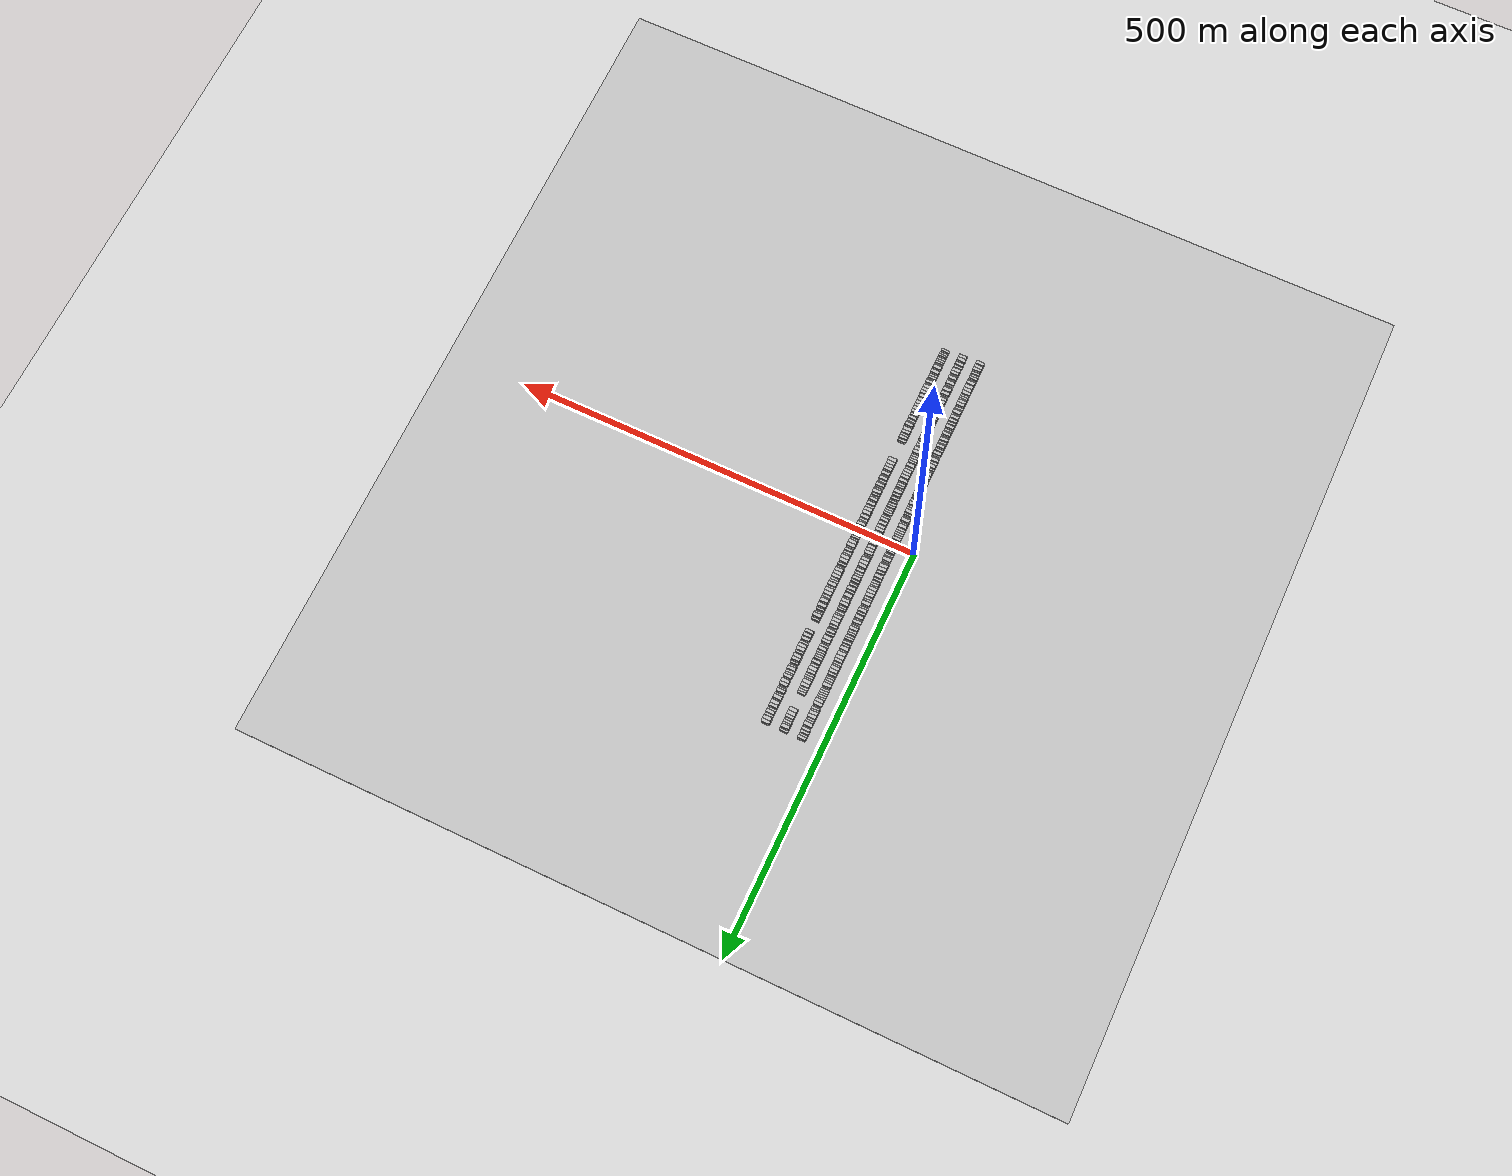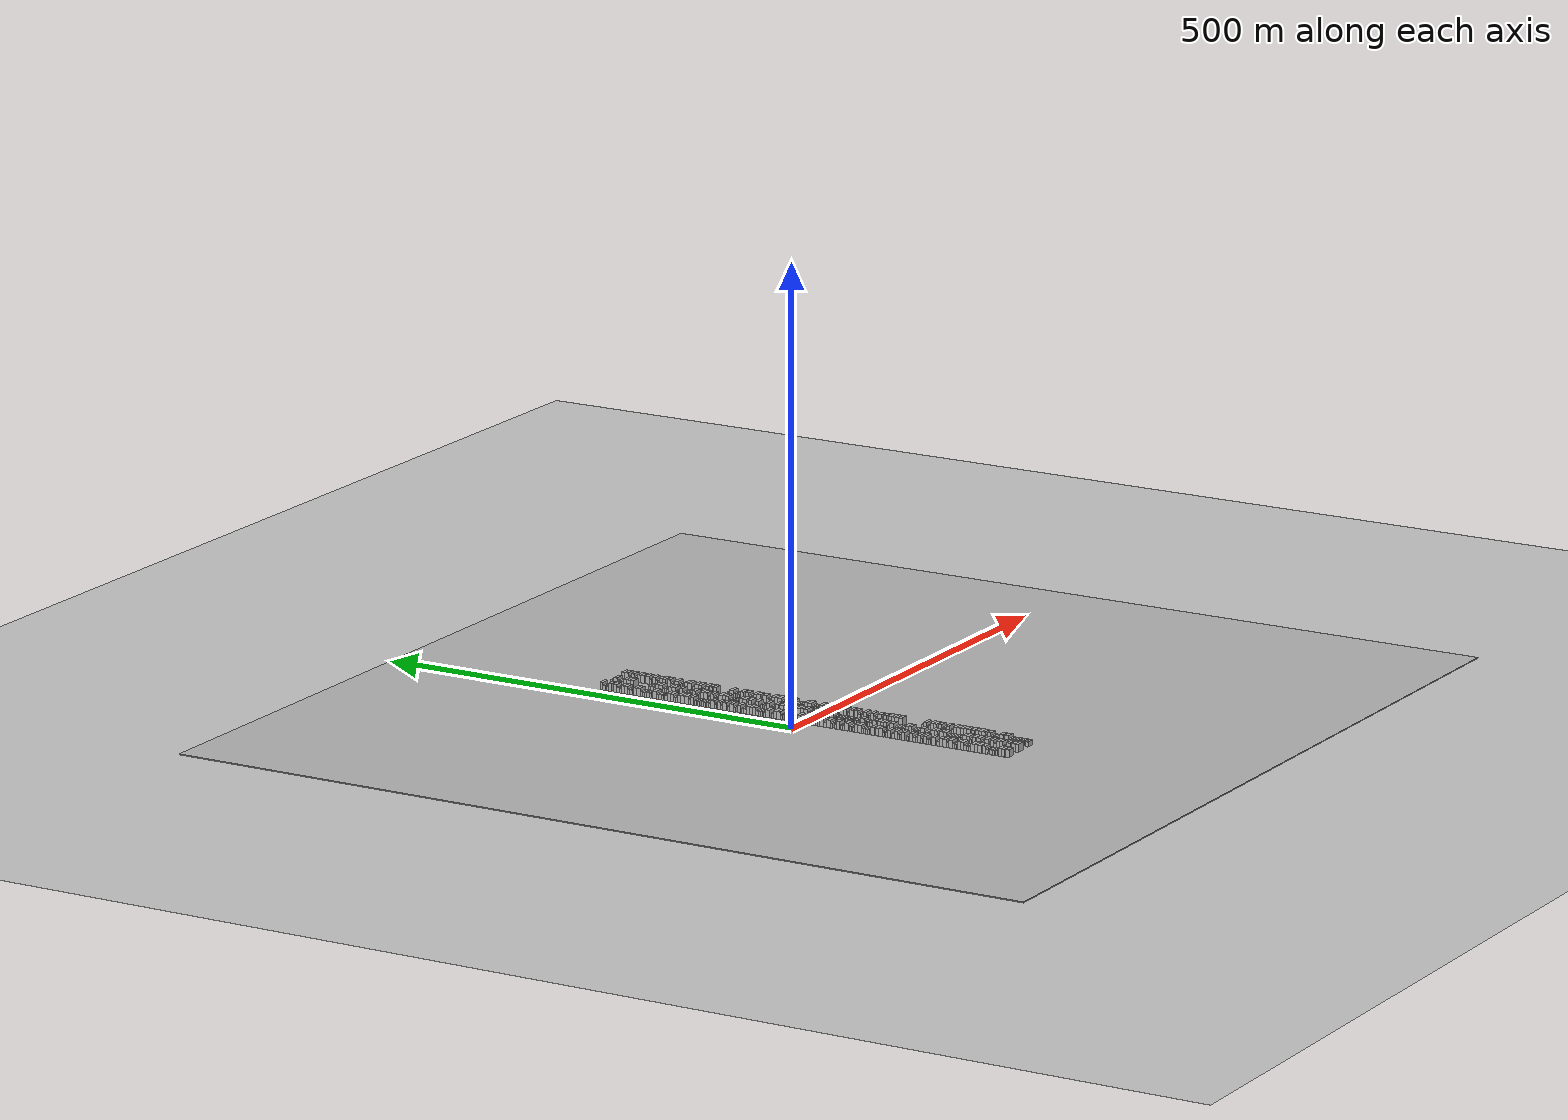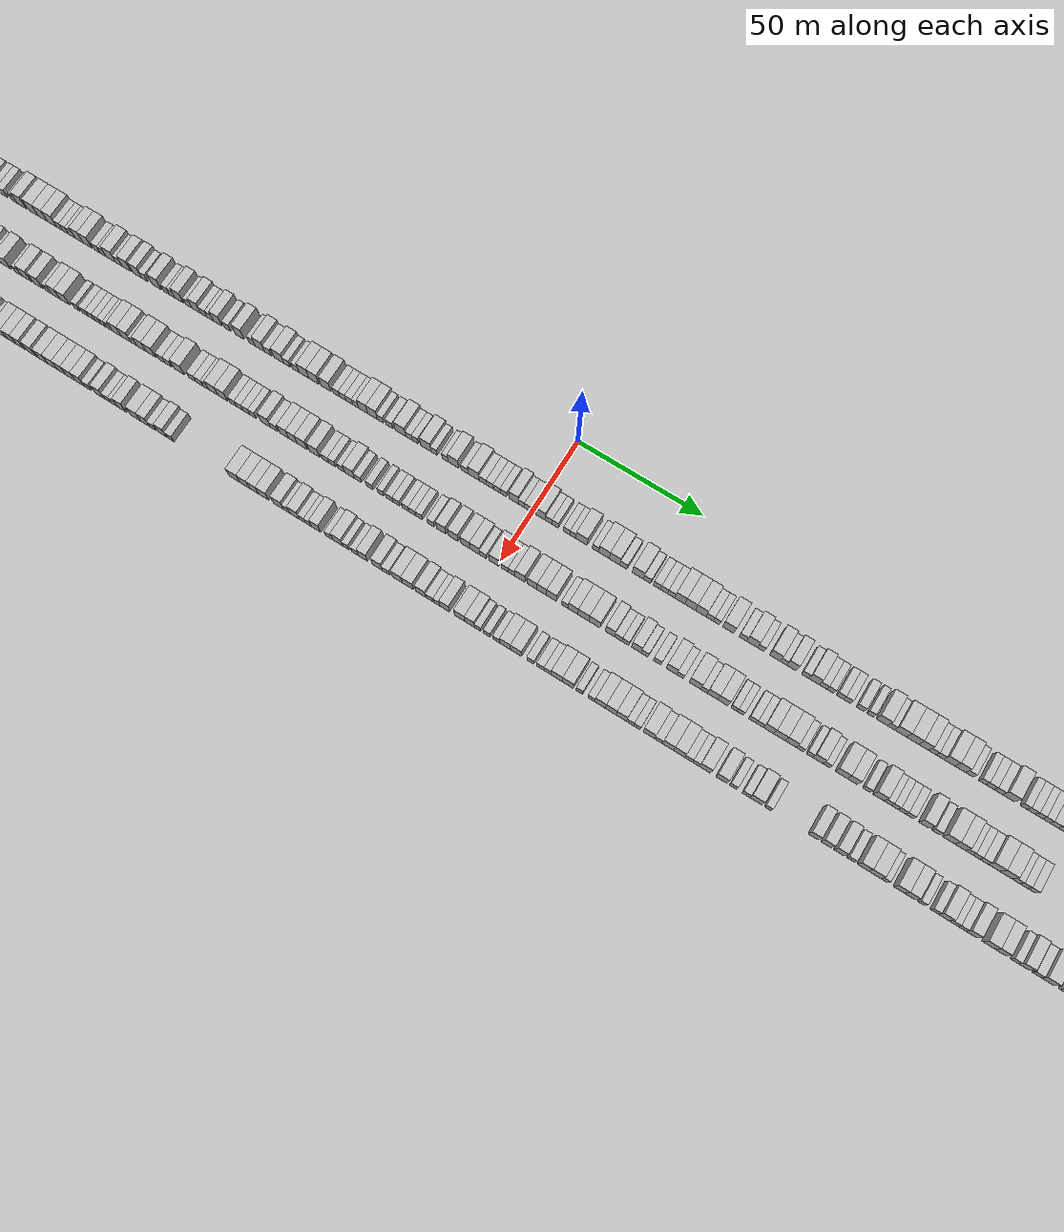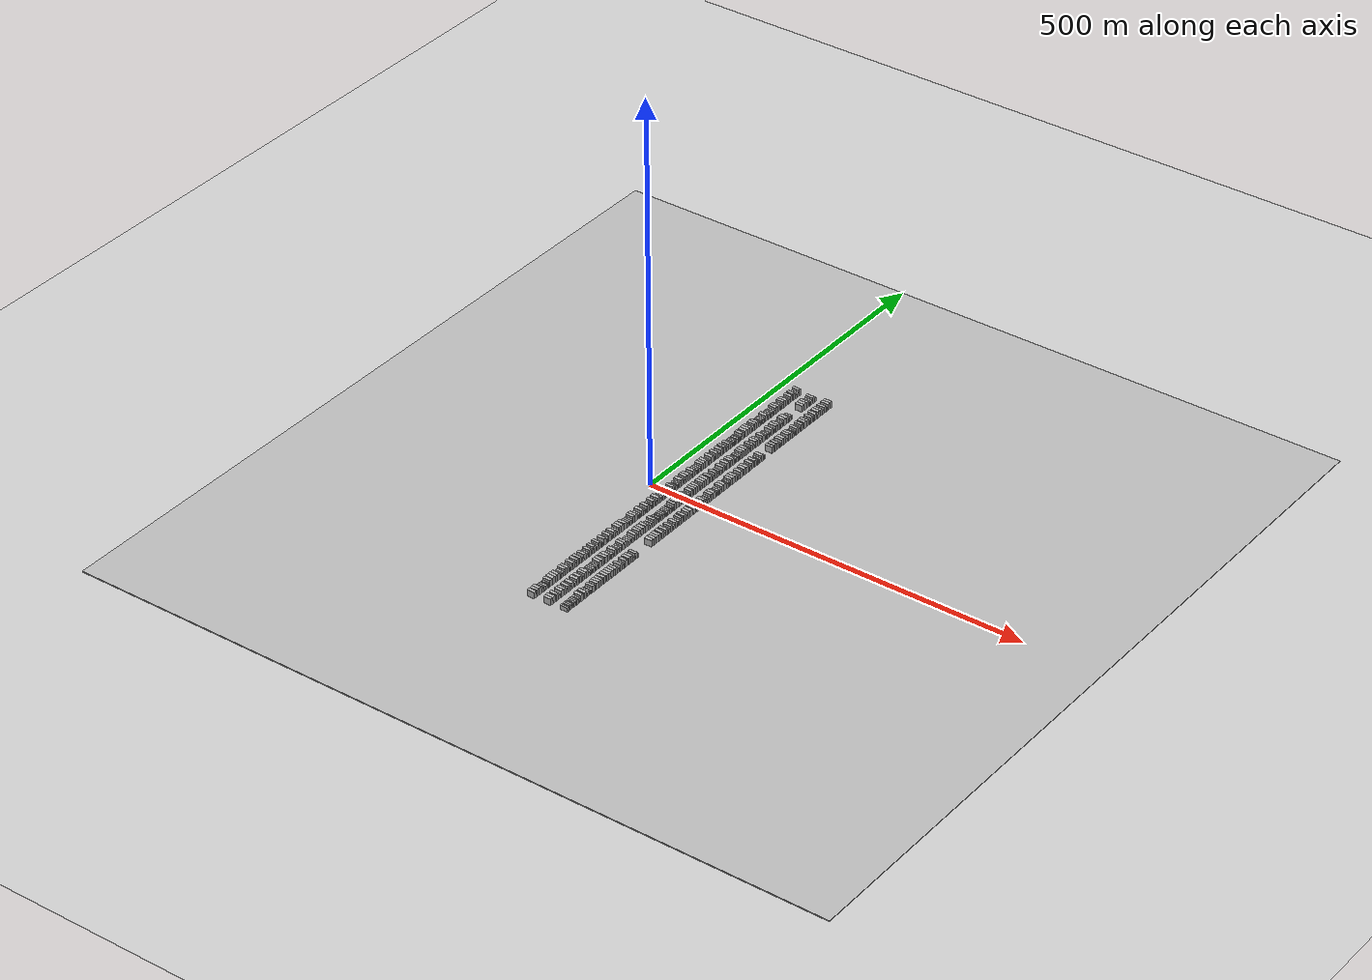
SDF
<?xml version="1.0" encoding="utf-8"?>

<sdf version="1.6">

   <world name="default">

      <gui fullscreen="0">

         <camera name="user_camera">

            <pose>-15 0 4.57585 0 0 0</pose>

            <view_controller>orbit</view_controller>

         </camera>

      </gui>

      <scene>

         <sky>

           <clouds>

             <speed>12</speed>

           </clouds>

         </sky>

         <ambient>0.4 0.4 0.4 1</ambient>

         <background>0.7 0.7 0.7 1</background>

         <shadows>1</shadows>

      </scene>

      <gravity>0 0 -9.8066</gravity>

      <magnetic_field>6e-06 2.3e-05 -4.2e-05</magnetic_field>

      <physics default="0" name="default_physics" type="ode">

         <ode>

            <solver>

               <type>quick</type>

               <iters>10</iters>

               <sor>1.0</sor>

               <use_dynamic_moi_rescaling>0</use_dynamic_moi_rescaling>

            </solver>

            <constraints>

               <cfm>0</cfm>

               <erp>0.2</erp>

               <contact_max_correcting_vel>100</contact_max_correcting_vel>

               <contact_surface_layer>0.001</contact_surface_layer>

            </constraints>

         </ode>

         <max_step_size>0.004</max_step_size>

         <real_time_factor>1</real_time_factor>

         <real_time_update_rate>250</real_time_update_rate>

      </physics>

      <light name="sun" type="directional">

         <cast_shadows>1</cast_shadows>

         <pose>0 0 10 0 0 0</pose>

         <diffuse>0.8 0.8 0.8 1</diffuse>

         <specular>0.2 0.2 0.2 1</specular>

         <attenuation>

            <range>1000</range>

            <constant>0.9</constant>

            <linear>0.01</linear>

            <quadratic>0.001</quadratic>

         </attenuation>

         <direction>-0.5 0.1 -0.9</direction>

      </light>

      <include>

         <name>ground_plane_1</name>

         <uri>model://HANNAS_ground_plane</uri>

         <pose>0 0 0  0 0 0</pose>

      </include>

      <include>

         <name>ground_plane_2</name>

         <uri>model://HANNAS_ground_plane</uri>

         <pose>100 0 0  0 0 0</pose>

      </include>

      <model name="building_1">

         <static>1</static>

         <pose frame="">25.0000 -245.9933 0 0.000000 0.000000 0.000000</pose>

         <link name="link">

            <pose frame="">0 0 4.50 0 0 0</pose>

            <collision name="collision">

               <geometry>

                  <box>

                     <size>10.0000 4.0133 9.0000</size>

                  </box>

               </geometry>

               <max_contacts>10</max_contacts>

               <surface>

                  <contact>

                     <ode/>

                  </contact>

                  <bounce/>

                  <friction>

                     <torsional>

                        <ode/>

                     </torsional>

                     <ode/>

                  </friction>

               </surface>

            </collision>

            <visual name="visual">

               <cast_shadows>0</cast_shadows>

               <geometry>

                  <box>

                     <size>10.0000 4.0133 9.0000</size>

                  </box>

               </geometry>

               <material>

                  <script>

                     <uri>model://HANNAS_wall/materials/scripts</uri>

                     <uri>model://HANNAS_wall/materials/textures</uri>

                     <name>vrc/HANNAS_wall</name>

                  </script>

               </material>

            </visual>

            <self_collide>0</self_collide>

            <enable_wind>0</enable_wind>

            <kinematic>0</kinematic>

         </link>

      </model>

      <model name="building_2">

         <static>1</static>

         <pose frame="">25.0000 -241.0090 0 0.000000 0.000000 0.000000</pose>

         <link name="link">

            <pose frame="">0 0 4.50 0 0 0</pose>

            <collision name="collision">

               <geometry>

                  <box>

                     <size>10.0000 3.9553 9.0000</size>

                  </box>

               </geometry>

               <max_contacts>10</max_contacts>

               <surface>

                  <contact>

                     <ode/>

                  </contact>

                  <bounce/>

                  <friction>

                     <torsional>

                        <ode/>

                     </torsional>

                     <ode/>

                  </friction>

               </surface>

            </collision>

            <visual name="visual">

               <cast_shadows>0</cast_shadows>

               <geometry>

                  <box>

                     <size>10.0000 3.9553 9.0000</size>

                  </box>

               </geometry>

               <material>

                  <script>

                     <uri>model://HANNAS_wall/materials/scripts</uri>

                     <uri>model://HANNAS_wall/materials/textures</uri>

                     <name>vrc/HANNAS_wall</name>

                  </script>

               </material>

            </visual>

            <self_collide>0</self_collide>

            <enable_wind>0</enable_wind>

            <kinematic>0</kinematic>

         </link>

      </model>

      <model name="building_3">

         <static>1</static>

         <pose frame="">25.0000 -237.1821 0 0.000000 0.000000 0.000000</pose>

         <link name="link">

            <pose frame="">0 0 4.50 0 0 0</pose>

            <collision name="collision">

               <geometry>

                  <box>

                     <size>10.0000 3.6985 9.0000</size>

                  </box>

               </geometry>

               <max_contacts>10</max_contacts>

               <surface>

                  <contact>

                     <ode/>

                  </contact>

                  <bounce/>

                  <friction>

                     <torsional>

                        <ode/>

                     </torsional>

                     <ode/>

                  </friction>

               </surface>

            </collision>

            <visual name="visual">

               <cast_shadows>0</cast_shadows>

               <geometry>

                  <box>

                     <size>10.0000 3.6985 9.0000</size>

                  </box>

               </geometry>

               <material>

                  <script>

                     <uri>model://HANNAS_wall/materials/scripts</uri>

                     <uri>model://HANNAS_wall/materials/textures</uri>

                     <name>vrc/HANNAS_wall</name>

                  </script>

               </material>

            </visual>

            <self_collide>0</self_collide>

            <enable_wind>0</enable_wind>

            <kinematic>0</kinematic>

         </link>

      </model>

      <model name="building_4">

         <static>1</static>

         <pose frame="">25.0000 -232.9304 0 0.000000 0.000000 0.000000</pose>

         <link name="link">

            <pose frame="">0 0 3.00 0 0 0</pose>

            <collision name="collision">

               <geometry>

                  <box>

                     <size>10.0000 2.8050 6.0000</size>

                  </box>

               </geometry>

               <max_contacts>10</max_contacts>

               <surface>

                  <contact>

                     <ode/>

                  </contact>

                  <bounce/>

                  <friction>

                     <torsional>

                        <ode/>

                     </torsional>

                     <ode/>

                  </friction>

               </surface>

            </collision>

            <visual name="visual">

               <cast_shadows>0</cast_shadows>

               <geometry>

                  <box>

                     <size>10.0000 2.8050 6.0000</size>

                  </box>

               </geometry>

               <material>

                  <script>

                     <uri>model://HANNAS_wall/materials/scripts</uri>

                     <uri>model://HANNAS_wall/materials/textures</uri>

                     <name>vrc/HANNAS_wall</name>

                  </script>

               </material>

            </visual>

            <self_collide>0</self_collide>

            <enable_wind>0</enable_wind>

            <kinematic>0</kinematic>

         </link>

      </model>

      <model name="building_5">

         <static>1</static>

         <pose frame="">25.0000 -229.2322 0 0.000000 0.000000 0.000000</pose>

         <link name="link">

            <pose frame="">0 0 3.00 0 0 0</pose>

            <collision name="collision">

               <geometry>

                  <box>

                     <size>10.0000 2.5915 6.0000</size>

                  </box>

               </geometry>

               <max_contacts>10</max_contacts>

               <surface>

                  <contact>

                     <ode/>

                  </contact>

                  <bounce/>

                  <friction>

                     <torsional>

                        <ode/>

                     </torsional>

                     <ode/>

                  </friction>

               </surface>

            </collision>

            <visual name="visual">

               <cast_shadows>0</cast_shadows>

               <geometry>

                  <box>

                     <size>10.0000 2.5915 6.0000</size>

                  </box>

               </geometry>

               <material>

                  <script>

                     <uri>model://HANNAS_wall/materials/scripts</uri>

                     <uri>model://HANNAS_wall/materials/textures</uri>

                     <name>vrc/HANNAS_wall</name>

                  </script>

               </material>

            </visual>

            <self_collide>0</self_collide>

            <enable_wind>0</enable_wind>

            <kinematic>0</kinematic>

         </link>

      </model>

      <model name="building_6">

         <static>1</static>

         <pose frame="">25.0000 -226.4989 0 0.000000 0.000000 0.000000</pose>

         <link name="link">

            <pose frame="">0 0 3.00 0 0 0</pose>

            <collision name="collision">

               <geometry>

                  <box>

                     <size>10.0000 2.8751 6.0000</size>

                  </box>

               </geometry>

               <max_contacts>10</max_contacts>

               <surface>

                  <contact>

                     <ode/>

                  </contact>

                  <bounce/>

                  <friction>

                     <torsional>

                        <ode/>

                     </torsional>

                     <ode/>

                  </friction>

               </surface>

            </collision>

            <visual name="visual">

               <cast_shadows>0</cast_shadows>

               <geometry>

                  <box>

                     <size>10.0000 2.8751 6.0000</size>

                  </box>

               </geometry>

               <material>

                  <script>

                     <uri>model://HANNAS_wall/materials/scripts</uri>

                     <uri>model://HANNAS_wall/materials/textures</uri>

                     <name>vrc/HANNAS_wall</name>

                  </script>

               </material>

            </visual>

            <self_collide>0</self_collide>

            <enable_wind>0</enable_wind>

            <kinematic>0</kinematic>

         </link>

      </model>

      <model name="building_7">

         <static>1</static>

         <pose frame="">25.0000 -221.8341 0 0.000000 0.000000 0.000000</pose>

         <link name="link">

            <pose frame="">0 0 3.00 0 0 0</pose>

            <collision name="collision">

               <geometry>

                  <box>

                     <size>10.0000 2.4544 6.0000</size>

                  </box>

               </geometry>

               <max_contacts>10</max_contacts>

               <surface>

                  <contact>

                     <ode/>

                  </contact>

                  <bounce/>

                  <friction>

                     <torsional>

                        <ode/>

                     </torsional>

                     <ode/>

                  </friction>

               </surface>

            </collision>

            <visual name="visual">

               <cast_shadows>0</cast_shadows>

               <geometry>

                  <box>

                     <size>10.0000 2.4544 6.0000</size>

                  </box>

               </geometry>

               <material>

                  <script>

                     <uri>model://HANNAS_wall/materials/scripts</uri>

                     <uri>model://HANNAS_wall/materials/textures</uri>

                     <name>vrc/HANNAS_wall</name>

                  </script>

               </material>

            </visual>

            <self_collide>0</self_collide>

            <enable_wind>0</enable_wind>

            <kinematic>0</kinematic>

         </link>

      </model>

      <model name="building_8">

         <static>1</static>

         <pose frame="">25.0000 -218.5676 0 0.000000 0.000000 0.000000</pose>

         <link name="link">

            <pose frame="">0 0 4.50 0 0 0</pose>

            <collision name="collision">

               <geometry>

                  <box>

                     <size>10.0000 4.0787 9.0000</size>

                  </box>

               </geometry>

               <max_contacts>10</max_contacts>

               <surface>

                  <contact>

                     <ode/>

                  </contact>

                  <bounce/>

                  <friction>

                     <torsional>

                        <ode/>

                     </torsional>

                     <ode/>

                  </friction>

               </surface>

            </collision>

            <visual name="visual">

               <cast_shadows>0</cast_shadows>

               <geometry>

                  <box>

                     <size>10.0000 4.0787 9.0000</size>

                  </box>

               </geometry>

               <material>

                  <script>

                     <uri>model://HANNAS_wall/materials/scripts</uri>

                     <uri>model://HANNAS_wall/materials/textures</uri>

                     <name>vrc/HANNAS_wall</name>

                  </script>

               </material>

            </visual>

            <self_collide>0</self_collide>

            <enable_wind>0</enable_wind>

            <kinematic>0</kinematic>

         </link>

      </model>

      <model name="building_9">

         <static>1</static>

         <pose frame="">25.0000 -213.3047 0 0.000000 0.000000 0.000000</pose>

         <link name="link">

            <pose frame="">0 0 4.50 0 0 0</pose>

            <collision name="collision">

               <geometry>

                  <box>

                     <size>10.0000 4.4470 9.0000</size>

                  </box>

               </geometry>

               <max_contacts>10</max_contacts>

               <surface>

                  <contact>

                     <ode/>

                  </contact>

                  <bounce/>

                  <friction>

                     <torsional>

                        <ode/>

                     </torsional>

                     <ode/>

                  </friction>

               </surface>

            </collision>

            <visual name="visual">

               <cast_shadows>0</cast_shadows>

               <geometry>

                  <box>

                     <size>10.0000 4.4470 9.0000</size>

                  </box>

               </geometry>

               <material>

                  <script>

                     <uri>model://HANNAS_wall/materials/scripts</uri>

                     <uri>model://HANNAS_wall/materials/textures</uri>

                     <name>vrc/HANNAS_wall</name>

                  </script>

               </material>

            </visual>

            <self_collide>0</self_collide>

            <enable_wind>0</enable_wind>

            <kinematic>0</kinematic>

         </link>

      </model>

      <model name="building_10">

         <static>1</static>

         <pose frame="">25.0000 -209.0256 0 0.000000 0.000000 0.000000</pose>

         <link name="link">

            <pose frame="">0 0 4.50 0 0 0</pose>

            <collision name="collision">

               <geometry>

                  <box>

                     <size>10.0000 4.1112 9.0000</size>

                  </box>

               </geometry>

               <max_contacts>10</max_contacts>

               <surface>

                  <contact>

                     <ode/>

                  </contact>

                  <bounce/>

                  <friction>

                     <torsional>

                        <ode/>

                     </torsional>

                     <ode/>

                  </friction>

               </surface>

            </collision>

            <visual name="visual">

               <cast_shadows>0</cast_shadows>

               <geometry>

                  <box>

                     <size>10.0000 4.1112 9.0000</size>

                  </box>

               </geometry>

               <material>

                  <script>

                     <uri>model://HANNAS_wall/materials/scripts</uri>

                     <uri>model://HANNAS_wall/materials/textures</uri>

                     <name>vrc/HANNAS_wall</name>

                  </script>

               </material>

            </visual>

            <self_collide>0</self_collide>

            <enable_wind>0</enable_wind>

            <kinematic>0</kinematic>

         </link>

      </model>

      <model name="building_11">

         <static>1</static>

         <pose frame="">25.0000 -204.8064 0 0.000000 0.000000 0.000000</pose>

         <link name="link">

            <pose frame="">0 0 4.50 0 0 0</pose>

            <collision name="collision">

               <geometry>

                  <box>

                     <size>10.0000 4.3273 9.0000</size>

                  </box>

               </geometry>

               <max_contacts>10</max_contacts>

               <surface>

                  <contact>

                     <ode/>

                  </contact>

                  <bounce/>

                  <friction>

                     <torsional>

                        <ode/>

                     </torsional>

                     <ode/>

                  </friction>

               </surface>

            </collision>

            <visual name="visual">

               <cast_shadows>0</cast_shadows>

               <geometry>

                  <box>

                     <size>10.0000 4.3273 9.0000</size>

                  </box>

               </geometry>

               <material>

                  <script>

                     <uri>model://HANNAS_wall/materials/scripts</uri>

                     <uri>model://HANNAS_wall/materials/textures</uri>

                     <name>vrc/HANNAS_wall</name>

                  </script>

               </material>

            </visual>

            <self_collide>0</self_collide>

            <enable_wind>0</enable_wind>

            <kinematic>0</kinematic>

         </link>

      </model>

      <model name="building_12">

         <static>1</static>

         <pose frame="">25.0000 -201.3231 0 0.000000 0.000000 0.000000</pose>

         <link name="link">

            <pose frame="">0 0 3.00 0 0 0</pose>

            <collision name="collision">

               <geometry>

                  <box>

                     <size>10.0000 2.6392 6.0000</size>

                  </box>

               </geometry>

               <max_contacts>10</max_contacts>

               <surface>

                  <contact>

                     <ode/>

                  </contact>

                  <bounce/>

                  <friction>

                     <torsional>

                        <ode/>

                     </torsional>

                     <ode/>

                  </friction>

               </surface>

            </collision>

            <visual name="visual">

               <cast_shadows>0</cast_shadows>

               <geometry>

                  <box>

                     <size>10.0000 2.6392 6.0000</size>

                  </box>

               </geometry>

               <material>

                  <script>

                     <uri>model://HANNAS_wall/materials/scripts</uri>

                     <uri>model://HANNAS_wall/materials/textures</uri>

                     <name>vrc/HANNAS_wall</name>

                  </script>

               </material>

            </visual>

            <self_collide>0</self_collide>

            <enable_wind>0</enable_wind>

            <kinematic>0</kinematic>

         </link>

      </model>

      <model name="building_13">

         <static>1</static>

         <pose frame="">25.0000 -198.6976 0 0.000000 0.000000 0.000000</pose>

         <link name="link">

            <pose frame="">0 0 3.00 0 0 0</pose>

            <collision name="collision">

               <geometry>

                  <box>

                     <size>10.0000 2.6119 6.0000</size>

                  </box>

               </geometry>

               <max_contacts>10</max_contacts>

               <surface>

                  <contact>

                     <ode/>

                  </contact>

                  <bounce/>

                  <friction>

                     <torsional>

                        <ode/>

                     </torsional>

                     <ode/>

                  </friction>

               </surface>

            </collision>

            <visual name="visual">

               <cast_shadows>0</cast_shadows>

               <geometry>

                  <box>

                     <size>10.0000 2.6119 6.0000</size>

                  </box>

               </geometry>

               <material>

                  <script>

                     <uri>model://HANNAS_wall/materials/scripts</uri>

                     <uri>model://HANNAS_wall/materials/textures</uri>

                     <name>vrc/HANNAS_wall</name>

                  </script>

               </material>

            </visual>

            <self_collide>0</self_collide>

            <enable_wind>0</enable_wind>

            <kinematic>0</kinematic>

         </link>

      </model>

      <model name="building_14">

         <static>1</static>

         <pose frame="">25.0000 -195.9175 0 0.000000 0.000000 0.000000</pose>

         <link name="link">

            <pose frame="">0 0 3.00 0 0 0</pose>

            <collision name="collision">

               <geometry>

                  <box>

                     <size>10.0000 2.9483 6.0000</size>

                  </box>

               </geometry>

               <max_contacts>10</max_contacts>

               <surface>

                  <contact>

                     <ode/>

                  </contact>

                  <bounce/>

                  <friction>

                     <torsional>

                        <ode/>

                     </torsional>

                     <ode/>

                  </friction>

               </surface>

            </collision>

            <visual name="visual">

               <cast_shadows>0</cast_shadows>

               <geometry>

                  <box>

                     <size>10.0000 2.9483 6.0000</size>

                  </box>

               </geometry>

               <material>

                  <script>

                     <uri>model://HANNAS_wall/materials/scripts</uri>

                     <uri>model://HANNAS_wall/materials/textures</uri>

                     <name>vrc/HANNAS_wall</name>

                  </script>

               </material>

            </visual>

            <self_collide>0</self_collide>

            <enable_wind>0</enable_wind>

            <kinematic>0</kinematic>

         </link>

      </model>

      <model name="building_15">

         <static>1</static>

         <pose frame="">25.0000 -192.6000 0 0.000000 0.000000 0.000000</pose>

         <link name="link">

            <pose frame="">0 0 4.50 0 0 0</pose>

            <collision name="collision">

               <geometry>

                  <box>

                     <size>10.0000 3.6866 9.0000</size>

                  </box>

               </geometry>

               <max_contacts>10</max_contacts>

               <surface>

                  <contact>

                     <ode/>

                  </contact>

                  <bounce/>

                  <friction>

                     <torsional>

                        <ode/>

                     </torsional>

                     <ode/>

                  </friction>

               </surface>

            </collision>

            <visual name="visual">

               <cast_shadows>0</cast_shadows>

               <geometry>

                  <box>

                     <size>10.0000 3.6866 9.0000</size>

                  </box>

               </geometry>

               <material>

                  <script>

                     <uri>model://HANNAS_wall/materials/scripts</uri>

                     <uri>model://HANNAS_wall/materials/textures</uri>

                     <name>vrc/HANNAS_wall</name>

                  </script>

               </material>

            </visual>

            <self_collide>0</self_collide>

            <enable_wind>0</enable_wind>

            <kinematic>0</kinematic>

         </link>

      </model>

      <model name="building_16">

         <static>1</static>

         <pose frame="">25.0000 -188.8242 0 0.000000 0.000000 0.000000</pose>

         <link name="link">

            <pose frame="">0 0 4.50 0 0 0</pose>

            <collision name="collision">

               <geometry>

                  <box>

                     <size>10.0000 3.8650 9.0000</size>

                  </box>

               </geometry>

               <max_contacts>10</max_contacts>

               <surface>

                  <contact>

                     <ode/>

                  </contact>

                  <bounce/>

                  <friction>

                     <torsional>

                        <ode/>

                     </torsional>

                     <ode/>

                  </friction>

               </surface>

            </collision>

            <visual name="visual">

               <cast_shadows>0</cast_shadows>

               <geometry>

                  <box>

                     <size>10.0000 3.8650 9.0000</size>

                  </box>

               </geometry>

               <material>

                  <script>

                     <uri>model://HANNAS_wall/materials/scripts</uri>

                     <uri>model://HANNAS_wall/materials/textures</uri>

                     <name>vrc/HANNAS_wall</name>

                  </script>

               </material>

            </visual>

            <self_collide>0</self_collide>

            <enable_wind>0</enable_wind>

            <kinematic>0</kinematic>

         </link>

      </model>

      <model name="building_17">

         <static>1</static>

         <pose frame="">25.0000 -184.5043 0 0.000000 0.000000 0.000000</pose>

         <link name="link">

            <pose frame="">0 0 3.00 0 0 0</pose>

            <collision name="collision">

               <geometry>

                  <box>

                     <size>10.0000 2.7749 6.0000</size>

                  </box>

               </geometry>

               <max_contacts>10</max_contacts>

               <surface>

                  <contact>

                     <ode/>

                  </contact>

                  <bounce/>

                  <friction>

                     <torsional>

                        <ode/>

                     </torsional>

                     <ode/>

                  </friction>

               </surface>

            </collision>

            <visual name="visual">

               <cast_shadows>0</cast_shadows>

               <geometry>

                  <box>

                     <size>10.0000 2.7749 6.0000</size>

                  </box>

               </geometry>

               <material>

                  <script>

                     <uri>model://HANNAS_wall/materials/scripts</uri>

                     <uri>model://HANNAS_wall/materials/textures</uri>

                     <name>vrc/HANNAS_wall</name>

                  </script>

               </material>

            </visual>

            <self_collide>0</self_collide>

            <enable_wind>0</enable_wind>

            <kinematic>0</kinematic>

         </link>

      </model>

      <model name="building_18">

         <static>1</static>

         <pose frame="">25.0000 -181.8539 0 0.000000 0.000000 0.000000</pose>

         <link name="link">

            <pose frame="">0 0 3.00 0 0 0</pose>

            <collision name="collision">

               <geometry>

                  <box>

                     <size>10.0000 2.5259 6.0000</size>

                  </box>

               </geometry>

               <max_contacts>10</max_contacts>

               <surface>

                  <contact>

                     <ode/>

                  </contact>

                  <bounce/>

                  <friction>

                     <torsional>

                        <ode/>

                     </torsional>

                     <ode/>

                  </friction>

               </surface>

            </collision>

            <visual name="visual">

               <cast_shadows>0</cast_shadows>

               <geometry>

                  <box>

                     <size>10.0000 2.5259 6.0000</size>

                  </box>

               </geometry>

               <material>

                  <script>

                     <uri>model://HANNAS_wall/materials/scripts</uri>

                     <uri>model://HANNAS_wall/materials/textures</uri>

                     <name>vrc/HANNAS_wall</name>

                  </script>

               </material>

            </visual>

            <self_collide>0</self_collide>

            <enable_wind>0</enable_wind>

            <kinematic>0</kinematic>

         </link>

      </model>

      <model name="building_19">

         <static>1</static>

         <pose frame="">25.0000 -178.4099 0 0.000000 0.000000 0.000000</pose>

         <link name="link">

            <pose frame="">0 0 4.50 0 0 0</pose>

            <collision name="collision">

               <geometry>

                  <box>

                     <size>10.0000 4.3621 9.0000</size>

                  </box>

               </geometry>

               <max_contacts>10</max_contacts>

               <surface>

                  <contact>

                     <ode/>

                  </contact>

                  <bounce/>

                  <friction>

                     <torsional>

                        <ode/>

                     </torsional>

                     <ode/>

                  </friction>

               </surface>

            </collision>

            <visual name="visual">

               <cast_shadows>0</cast_shadows>

               <geometry>

                  <box>

                     <size>10.0000 4.3621 9.0000</size>

                  </box>

               </geometry>

               <material>

                  <script>

                     <uri>model://HANNAS_wall/materials/scripts</uri>

                     <uri>model://HANNAS_wall/materials/textures</uri>

                     <name>vrc/HANNAS_wall</name>

                  </script>

               </material>

            </visual>

            <self_collide>0</self_collide>

            <enable_wind>0</enable_wind>

            <kinematic>0</kinematic>

         </link>

      </model>

      <model name="building_20">

         <static>1</static>

         <pose frame="">25.0000 -174.8103 0 0.000000 0.000000 0.000000</pose>

         <link name="link">

            <pose frame="">0 0 3.00 0 0 0</pose>

            <collision name="collision">

               <geometry>

                  <box>

                     <size>10.0000 2.8371 6.0000</size>

                  </box>

               </geometry>

               <max_contacts>10</max_contacts>

               <surface>

                  <contact>

                     <ode/>

                  </contact>

                  <bounce/>

                  <friction>

                     <torsional>

                        <ode/>

                     </torsional>

                     <ode/>

                  </friction>

               </surface>

            </collision>

            <visual name="visual">

               <cast_shadows>0</cast_shadows>

               <geometry>

                  <box>

                     <size>10.0000 2.8371 6.0000</size>

                  </box>

               </geometry>

               <material>

                  <script>

                     <uri>model://HANNAS_wall/materials/scripts</uri>

                     <uri>model://HANNAS_wall/materials/textures</uri>

                     <name>vrc/HANNAS_wall</name>

                  </script>

               </material>

            </visual>

            <self_collide>0</self_collide>

            <enable_wind>0</enable_wind>

            <kinematic>0</kinematic>

         </link>

      </model>

      <model name="building_21">

         <static>1</static>

         <pose frame="">25.0000 -171.4279 0 0.000000 0.000000 0.000000</pose>

         <link name="link">

            <pose frame="">0 0 4.50 0 0 0</pose>

            <collision name="collision">

               <geometry>

                  <box>

                     <size>10.0000 3.9276 9.0000</size>

                  </box>

               </geometry>

               <max_contacts>10</max_contacts>

               <surface>

                  <contact>

                     <ode/>

                  </contact>

                  <bounce/>

                  <friction>

                     <torsional>

                        <ode/>

                     </torsional>

                     <ode/>

                  </friction>

               </surface>

            </collision>

            <visual name="visual">

               <cast_shadows>0</cast_shadows>

               <geometry>

                  <box>

                     <size>10.0000 3.9276 9.0000</size>

                  </box>

               </geometry>

               <material>

                  <script>

                     <uri>model://HANNAS_wall/materials/scripts</uri>

                     <uri>model://HANNAS_wall/materials/textures</uri>

                     <name>vrc/HANNAS_wall</name>

                  </script>

               </material>

            </visual>

            <self_collide>0</self_collide>

            <enable_wind>0</enable_wind>

            <kinematic>0</kinematic>

         </link>

      </model>

      <model name="building_22">

         <static>1</static>

         <pose frame="">25.0000 -166.6228 0 0.000000 0.000000 0.000000</pose>

         <link name="link">

            <pose frame="">0 0 4.50 0 0 0</pose>

            <collision name="collision">

               <geometry>

                  <box>

                     <size>10.0000 3.6826 9.0000</size>

                  </box>

               </geometry>

               <max_contacts>10</max_contacts>

               <surface>

                  <contact>

                     <ode/>

                  </contact>

                  <bounce/>

                  <friction>

                     <torsional>

                        <ode/>

                     </torsional>

                     <ode/>

                  </friction>

               </surface>

            </collision>

            <visual name="visual">

               <cast_shadows>0</cast_shadows>

               <geometry>

                  <box>

                     <size>10.0000 3.6826 9.0000</size>

                  </box>

               </geometry>

               <material>

                  <script>

                     <uri>model://HANNAS_wall/materials/scripts</uri>

                     <uri>model://HANNAS_wall/materials/textures</uri>

                     <name>vrc/HANNAS_wall</name>

                  </script>

               </material>

            </visual>

            <self_collide>0</self_collide>

            <enable_wind>0</enable_wind>

            <kinematic>0</kinematic>

         </link>

      </model>

      <model name="building_23">

         <static>1</static>

         <pose frame="">25.0000 -163.4532 0 0.000000 0.000000 0.000000</pose>

         <link name="link">

            <pose frame="">0 0 3.00 0 0 0</pose>

            <collision name="collision">

               <geometry>

                  <box>

                     <size>10.0000 2.6567 6.0000</size>

                  </box>

               </geometry>

               <max_contacts>10</max_contacts>

               <surface>

                  <contact>

                     <ode/>

                  </contact>

                  <bounce/>

                  <friction>

                     <torsional>

                        <ode/>

                     </torsional>

                     <ode/>

                  </friction>

               </surface>

            </collision>

            <visual name="visual">

               <cast_shadows>0</cast_shadows>

               <geometry>

                  <box>

                     <size>10.0000 2.6567 6.0000</size>

                  </box>

               </geometry>

               <material>

                  <script>

                     <uri>model://HANNAS_wall/materials/scripts</uri>

                     <uri>model://HANNAS_wall/materials/textures</uri>

                     <name>vrc/HANNAS_wall</name>

                  </script>

               </material>

            </visual>

            <self_collide>0</self_collide>

            <enable_wind>0</enable_wind>

            <kinematic>0</kinematic>

         </link>

      </model>

      <model name="building_24">

         <static>1</static>

         <pose frame="">25.0000 -158.1047 0 0.000000 0.000000 0.000000</pose>

         <link name="link">

            <pose frame="">0 0 4.50 0 0 0</pose>

            <collision name="collision">

               <geometry>

                  <box>

                     <size>10.0000 4.0403 9.0000</size>

                  </box>

               </geometry>

               <max_contacts>10</max_contacts>

               <surface>

                  <contact>

                     <ode/>

                  </contact>

                  <bounce/>

                  <friction>

                     <torsional>

                        <ode/>

                     </torsional>

                     <ode/>

                  </friction>

               </surface>

            </collision>

            <visual name="visual">

               <cast_shadows>0</cast_shadows>

               <geometry>

                  <box>

                     <size>10.0000 4.0403 9.0000</size>

                  </box>

               </geometry>

               <material>

                  <script>

                     <uri>model://HANNAS_wall/materials/scripts</uri>

                     <uri>model://HANNAS_wall/materials/textures</uri>

                     <name>vrc/HANNAS_wall</name>

                  </script>

               </material>

            </visual>

            <self_collide>0</self_collide>

            <enable_wind>0</enable_wind>

            <kinematic>0</kinematic>

         </link>

      </model>

      <model name="building_25">

         <static>1</static>

         <pose frame="">25.0000 -153.8327 0 0.000000 0.000000 0.000000</pose>

         <link name="link">

            <pose frame="">0 0 3.00 0 0 0</pose>

            <collision name="collision">

               <geometry>

                  <box>

                     <size>10.0000 2.5037 6.0000</size>

                  </box>

               </geometry>

               <max_contacts>10</max_contacts>

               <surface>

                  <contact>

                     <ode/>

                  </contact>

                  <bounce/>

                  <friction>

                     <torsional>

                        <ode/>

                     </torsional>

                     <ode/>

                  </friction>

               </surface>

            </collision>

            <visual name="visual">

               <cast_shadows>0</cast_shadows>

               <geometry>

                  <box>

                     <size>10.0000 2.5037 6.0000</size>

                  </box>

               </geometry>

               <material>

                  <script>

                     <uri>model://HANNAS_wall/materials/scripts</uri>

                     <uri>model://HANNAS_wall/materials/textures</uri>

                     <name>vrc/HANNAS_wall</name>

                  </script>

               </material>

            </visual>

            <self_collide>0</self_collide>

            <enable_wind>0</enable_wind>

            <kinematic>0</kinematic>

         </link>

      </model>

      <model name="building_26">

         <static>1</static>

         <pose frame="">25.0000 -151.3712 0 0.000000 0.000000 0.000000</pose>

         <link name="link">

            <pose frame="">0 0 3.00 0 0 0</pose>

            <collision name="collision">

               <geometry>

                  <box>

                     <size>10.0000 2.4193 6.0000</size>

                  </box>

               </geometry>

               <max_contacts>10</max_contacts>

               <surface>

                  <contact>

                     <ode/>

                  </contact>

                  <bounce/>

                  <friction>

                     <torsional>

                        <ode/>

                     </torsional>

                     <ode/>

                  </friction>

               </surface>

            </collision>

            <visual name="visual">

               <cast_shadows>0</cast_shadows>

               <geometry>

                  <box>

                     <size>10.0000 2.4193 6.0000</size>

                  </box>

               </geometry>

               <material>

                  <script>

                     <uri>model://HANNAS_wall/materials/scripts</uri>

                     <uri>model://HANNAS_wall/materials/textures</uri>

                     <name>vrc/HANNAS_wall</name>

                  </script>

               </material>

            </visual>

            <self_collide>0</self_collide>

            <enable_wind>0</enable_wind>

            <kinematic>0</kinematic>

         </link>

      </model>

      <model name="building_27">

         <static>1</static>

         <pose frame="">25.0000 -148.2993 0 0.000000 0.000000 0.000000</pose>

         <link name="link">

            <pose frame="">0 0 4.50 0 0 0</pose>

            <collision name="collision">

               <geometry>

                  <box>

                     <size>10.0000 3.7246 9.0000</size>

                  </box>

               </geometry>

               <max_contacts>10</max_contacts>

               <surface>

                  <contact>

                     <ode/>

                  </contact>

                  <bounce/>

                  <friction>

                     <torsional>

                        <ode/>

                     </torsional>

                     <ode/>

                  </friction>

               </surface>

            </collision>

            <visual name="visual">

               <cast_shadows>0</cast_shadows>

               <geometry>

                  <box>

                     <size>10.0000 3.7246 9.0000</size>

                  </box>

               </geometry>

               <material>

                  <script>

                     <uri>model://HANNAS_wall/materials/scripts</uri>

                     <uri>model://HANNAS_wall/materials/textures</uri>

                     <name>vrc/HANNAS_wall</name>

                  </script>

               </material>

            </visual>

            <self_collide>0</self_collide>

            <enable_wind>0</enable_wind>

            <kinematic>0</kinematic>

         </link>

      </model>

      <model name="building_28">

         <static>1</static>

         <pose frame="">25.0000 -144.0534 0 0.000000 0.000000 0.000000</pose>

         <link name="link">

            <pose frame="">0 0 3.00 0 0 0</pose>

            <collision name="collision">

               <geometry>

                  <box>

                     <size>10.0000 2.7671 6.0000</size>

                  </box>

               </geometry>

               <max_contacts>10</max_contacts>

               <surface>

                  <contact>

                     <ode/>

                  </contact>

                  <bounce/>

                  <friction>

                     <torsional>

                        <ode/>

                     </torsional>

                     <ode/>

                  </friction>

               </surface>

            </collision>

            <visual name="visual">

               <cast_shadows>0</cast_shadows>

               <geometry>

                  <box>

                     <size>10.0000 2.7671 6.0000</size>

                  </box>

               </geometry>

               <material>

                  <script>

                     <uri>model://HANNAS_wall/materials/scripts</uri>

                     <uri>model://HANNAS_wall/materials/textures</uri>

                     <name>vrc/HANNAS_wall</name>

                  </script>

               </material>

            </visual>

            <self_collide>0</self_collide>

            <enable_wind>0</enable_wind>

            <kinematic>0</kinematic>

         </link>

      </model>

      <model name="building_29">

         <static>1</static>

         <pose frame="">25.0000 -140.7828 0 0.000000 0.000000 0.000000</pose>

         <link name="link">

            <pose frame="">0 0 4.50 0 0 0</pose>

            <collision name="collision">

               <geometry>

                  <box>

                     <size>10.0000 3.7740 9.0000</size>

                  </box>

               </geometry>

               <max_contacts>10</max_contacts>

               <surface>

                  <contact>

                     <ode/>

                  </contact>

                  <bounce/>

                  <friction>

                     <torsional>

                        <ode/>

                     </torsional>

                     <ode/>

                  </friction>

               </surface>

            </collision>

            <visual name="visual">

               <cast_shadows>0</cast_shadows>

               <geometry>

                  <box>

                     <size>10.0000 3.7740 9.0000</size>

                  </box>

               </geometry>

               <material>

                  <script>

                     <uri>model://HANNAS_wall/materials/scripts</uri>

                     <uri>model://HANNAS_wall/materials/textures</uri>

                     <name>vrc/HANNAS_wall</name>

                  </script>

               </material>

            </visual>

            <self_collide>0</self_collide>

            <enable_wind>0</enable_wind>

            <kinematic>0</kinematic>

         </link>

      </model>

      <model name="building_30">

         <static>1</static>

         <pose frame="">25.0000 -137.4815 0 0.000000 0.000000 0.000000</pose>

         <link name="link">

            <pose frame="">0 0 3.00 0 0 0</pose>

            <collision name="collision">

               <geometry>

                  <box>

                     <size>10.0000 2.8286 6.0000</size>

                  </box>

               </geometry>

               <max_contacts>10</max_contacts>

               <surface>

                  <contact>

                     <ode/>

                  </contact>

                  <bounce/>

                  <friction>

                     <torsional>

                        <ode/>

                     </torsional>

                     <ode/>

                  </friction>

               </surface>

            </collision>

            <visual name="visual">

               <cast_shadows>0</cast_shadows>

               <geometry>

                  <box>

                     <size>10.0000 2.8286 6.0000</size>

                  </box>

               </geometry>

               <material>

                  <script>

                     <uri>model://HANNAS_wall/materials/scripts</uri>

                     <uri>model://HANNAS_wall/materials/textures</uri>

                     <name>vrc/HANNAS_wall</name>

                  </script>

               </material>

            </visual>

            <self_collide>0</self_collide>

            <enable_wind>0</enable_wind>

            <kinematic>0</kinematic>

         </link>

      </model>

      <model name="building_31">

         <static>1</static>

         <pose frame="">25.0000 -134.6977 0 0.000000 0.000000 0.000000</pose>

         <link name="link">

            <pose frame="">0 0 3.00 0 0 0</pose>

            <collision name="collision">

               <geometry>

                  <box>

                     <size>10.0000 2.7391 6.0000</size>

                  </box>

               </geometry>

               <max_contacts>10</max_contacts>

               <surface>

                  <contact>

                     <ode/>

                  </contact>

                  <bounce/>

                  <friction>

                     <torsional>

                        <ode/>

                     </torsional>

                     <ode/>

                  </friction>

               </surface>

            </collision>

            <visual name="visual">

               <cast_shadows>0</cast_shadows>

               <geometry>

                  <box>

                     <size>10.0000 2.7391 6.0000</size>

                  </box>

               </geometry>

               <material>

                  <script>

                     <uri>model://HANNAS_wall/materials/scripts</uri>

                     <uri>model://HANNAS_wall/materials/textures</uri>

                     <name>vrc/HANNAS_wall</name>

                  </script>

               </material>

            </visual>

            <self_collide>0</self_collide>

            <enable_wind>0</enable_wind>

            <kinematic>0</kinematic>

         </link>

      </model>

      <model name="building_32">

         <static>1</static>

         <pose frame="">25.0000 -131.4777 0 0.000000 0.000000 0.000000</pose>

         <link name="link">

            <pose frame="">0 0 4.50 0 0 0</pose>

            <collision name="collision">

               <geometry>

                  <box>

                     <size>10.0000 3.7009 9.0000</size>

                  </box>

               </geometry>

               <max_contacts>10</max_contacts>

               <surface>

                  <contact>

                     <ode/>

                  </contact>

                  <bounce/>

                  <friction>

                     <torsional>

                        <ode/>

                     </torsional>

                     <ode/>

                  </friction>

               </surface>

            </collision>

            <visual name="visual">

               <cast_shadows>0</cast_shadows>

               <geometry>

                  <box>

                     <size>10.0000 3.7009 9.0000</size>

                  </box>

               </geometry>

               <material>

                  <script>

                     <uri>model://HANNAS_wall/materials/scripts</uri>

                     <uri>model://HANNAS_wall/materials/textures</uri>

                     <name>vrc/HANNAS_wall</name>

                  </script>

               </material>

            </visual>

            <self_collide>0</self_collide>

            <enable_wind>0</enable_wind>

            <kinematic>0</kinematic>

         </link>

      </model>

      <model name="building_33">

         <static>1</static>

         <pose frame="">25.0000 -127.2597 0 0.000000 0.000000 0.000000</pose>

         <link name="link">

            <pose frame="">0 0 3.00 0 0 0</pose>

            <collision name="collision">

               <geometry>

                  <box>

                     <size>10.0000 2.7352 6.0000</size>

                  </box>

               </geometry>

               <max_contacts>10</max_contacts>

               <surface>

                  <contact>

                     <ode/>

                  </contact>

                  <bounce/>

                  <friction>

                     <torsional>

                        <ode/>

                     </torsional>

                     <ode/>

                  </friction>

               </surface>

            </collision>

            <visual name="visual">

               <cast_shadows>0</cast_shadows>

               <geometry>

                  <box>

                     <size>10.0000 2.7352 6.0000</size>

                  </box>

               </geometry>

               <material>

                  <script>

                     <uri>model://HANNAS_wall/materials/scripts</uri>

                     <uri>model://HANNAS_wall/materials/textures</uri>

                     <name>vrc/HANNAS_wall</name>

                  </script>

               </material>

            </visual>

            <self_collide>0</self_collide>

            <enable_wind>0</enable_wind>

            <kinematic>0</kinematic>

         </link>

      </model>

      <model name="building_34">

         <static>1</static>

         <pose frame="">25.0000 -121.9509 0 0.000000 0.000000 0.000000</pose>

         <link name="link">

            <pose frame="">0 0 4.50 0 0 0</pose>

            <collision name="collision">

               <geometry>

                  <box>

                     <size>10.0000 3.8825 9.0000</size>

                  </box>

               </geometry>

               <max_contacts>10</max_contacts>

               <surface>

                  <contact>

                     <ode/>

                  </contact>

                  <bounce/>

                  <friction>

                     <torsional>

                        <ode/>

                     </torsional>

                     <ode/>

                  </friction>

               </surface>

            </collision>

            <visual name="visual">

               <cast_shadows>0</cast_shadows>

               <geometry>

                  <box>

                     <size>10.0000 3.8825 9.0000</size>

                  </box>

               </geometry>

               <material>

                  <script>

                     <uri>model://HANNAS_wall/materials/scripts</uri>

                     <uri>model://HANNAS_wall/materials/textures</uri>

                     <name>vrc/HANNAS_wall</name>

                  </script>

               </material>

            </visual>

            <self_collide>0</self_collide>

            <enable_wind>0</enable_wind>

            <kinematic>0</kinematic>

         </link>

      </model>

      <model name="building_35">

         <static>1</static>

         <pose frame="">25.0000 -116.6545 0 0.000000 0.000000 0.000000</pose>

         <link name="link">

            <pose frame="">0 0 3.00 0 0 0</pose>

            <collision name="collision">

               <geometry>

                  <box>

                     <size>10.0000 2.7103 6.0000</size>

                  </box>

               </geometry>

               <max_contacts>10</max_contacts>

               <surface>

                  <contact>

                     <ode/>

                  </contact>

                  <bounce/>

                  <friction>

                     <torsional>

                        <ode/>

                     </torsional>

                     <ode/>

                  </friction>

               </surface>

            </collision>

            <visual name="visual">

               <cast_shadows>0</cast_shadows>

               <geometry>

                  <box>

                     <size>10.0000 2.7103 6.0000</size>

                  </box>

               </geometry>

               <material>

                  <script>

                     <uri>model://HANNAS_wall/materials/scripts</uri>

                     <uri>model://HANNAS_wall/materials/textures</uri>

                     <name>vrc/HANNAS_wall</name>

                  </script>

               </material>

            </visual>

            <self_collide>0</self_collide>

            <enable_wind>0</enable_wind>

            <kinematic>0</kinematic>

         </link>

      </model>

      <model name="building_36">

         <static>1</static>

         <pose frame="">25.0000 -113.2570 0 0.000000 0.000000 0.000000</pose>

         <link name="link">

            <pose frame="">0 0 4.50 0 0 0</pose>

            <collision name="collision">

               <geometry>

                  <box>

                     <size>10.0000 4.0846 9.0000</size>

                  </box>

               </geometry>

               <max_contacts>10</max_contacts>

               <surface>

                  <contact>

                     <ode/>

                  </contact>

                  <bounce/>

                  <friction>

                     <torsional>

                        <ode/>

                     </torsional>

                     <ode/>

                  </friction>

               </surface>

            </collision>

            <visual name="visual">

               <cast_shadows>0</cast_shadows>

               <geometry>

                  <box>

                     <size>10.0000 4.0846 9.0000</size>

                  </box>

               </geometry>

               <material>

                  <script>

                     <uri>model://HANNAS_wall/materials/scripts</uri>

                     <uri>model://HANNAS_wall/materials/textures</uri>

                     <name>vrc/HANNAS_wall</name>

                  </script>

               </material>

            </visual>

            <self_collide>0</self_collide>

            <enable_wind>0</enable_wind>

            <kinematic>0</kinematic>

         </link>

      </model>

      <model name="building_37">

         <static>1</static>

         <pose frame="">25.0000 -109.7206 0 0.000000 0.000000 0.000000</pose>

         <link name="link">

            <pose frame="">0 0 3.00 0 0 0</pose>

            <collision name="collision">

               <geometry>

                  <box>

                     <size>10.0000 2.9881 6.0000</size>

                  </box>

               </geometry>

               <max_contacts>10</max_contacts>

               <surface>

                  <contact>

                     <ode/>

                  </contact>

                  <bounce/>

                  <friction>

                     <torsional>

                        <ode/>

                     </torsional>

                     <ode/>

                  </friction>

               </surface>

            </collision>

            <visual name="visual">

               <cast_shadows>0</cast_shadows>

               <geometry>

                  <box>

                     <size>10.0000 2.9881 6.0000</size>

                  </box>

               </geometry>

               <material>

                  <script>

                     <uri>model://HANNAS_wall/materials/scripts</uri>

                     <uri>model://HANNAS_wall/materials/textures</uri>

                     <name>vrc/HANNAS_wall</name>

                  </script>

               </material>

            </visual>

            <self_collide>0</self_collide>

            <enable_wind>0</enable_wind>

            <kinematic>0</kinematic>

         </link>

      </model>

      <model name="building_38">

         <static>1</static>

         <pose frame="">25.0000 -105.0718 0 0.000000 0.000000 0.000000</pose>

         <link name="link">

            <pose frame="">0 0 4.50 0 0 0</pose>

            <collision name="collision">

               <geometry>

                  <box>

                     <size>10.0000 4.3095 9.0000</size>

                  </box>

               </geometry>

               <max_contacts>10</max_contacts>

               <surface>

                  <contact>

                     <ode/>

                  </contact>

                  <bounce/>

                  <friction>

                     <torsional>

                        <ode/>

                     </torsional>

                     <ode/>

                  </friction>

               </surface>

            </collision>

            <visual name="visual">

               <cast_shadows>0</cast_shadows>

               <geometry>

                  <box>

                     <size>10.0000 4.3095 9.0000</size>

                  </box>

               </geometry>

               <material>

                  <script>

                     <uri>model://HANNAS_wall/materials/scripts</uri>

                     <uri>model://HANNAS_wall/materials/textures</uri>

                     <name>vrc/HANNAS_wall</name>

                  </script>

               </material>

            </visual>

            <self_collide>0</self_collide>

            <enable_wind>0</enable_wind>

            <kinematic>0</kinematic>

         </link>

      </model>

      <model name="building_39">

         <static>1</static>

         <pose frame="">25.0000 -101.5873 0 0.000000 0.000000 0.000000</pose>

         <link name="link">

            <pose frame="">0 0 3.00 0 0 0</pose>

            <collision name="collision">

               <geometry>

                  <box>

                     <size>10.0000 2.6594 6.0000</size>

                  </box>

               </geometry>

               <max_contacts>10</max_contacts>

               <surface>

                  <contact>

                     <ode/>

                  </contact>

                  <bounce/>

                  <friction>

                     <torsional>

                        <ode/>

                     </torsional>

                     <ode/>

                  </friction>

               </surface>

            </collision>

            <visual name="visual">

               <cast_shadows>0</cast_shadows>

               <geometry>

                  <box>

                     <size>10.0000 2.6594 6.0000</size>

                  </box>

               </geometry>

               <material>

                  <script>

                     <uri>model://HANNAS_wall/materials/scripts</uri>

                     <uri>model://HANNAS_wall/materials/textures</uri>

                     <name>vrc/HANNAS_wall</name>

                  </script>

               </material>

            </visual>

            <self_collide>0</self_collide>

            <enable_wind>0</enable_wind>

            <kinematic>0</kinematic>

         </link>

      </model>

      <model name="building_40">

         <static>1</static>

         <pose frame="">25.0000 -97.8645 0 0.000000 0.000000 0.000000</pose>

         <link name="link">

            <pose frame="">0 0 3.00 0 0 0</pose>

            <collision name="collision">

               <geometry>

                  <box>

                     <size>10.0000 2.7863 6.0000</size>

                  </box>

               </geometry>

               <max_contacts>10</max_contacts>

               <surface>

                  <contact>

                     <ode/>

                  </contact>

                  <bounce/>

                  <friction>

                     <torsional>

                        <ode/>

                     </torsional>

                     <ode/>

                  </friction>

               </surface>

            </collision>

            <visual name="visual">

               <cast_shadows>0</cast_shadows>

               <geometry>

                  <box>

                     <size>10.0000 2.7863 6.0000</size>

                  </box>

               </geometry>

               <material>

                  <script>

                     <uri>model://HANNAS_wall/materials/scripts</uri>

                     <uri>model://HANNAS_wall/materials/textures</uri>

                     <name>vrc/HANNAS_wall</name>

                  </script>

               </material>

            </visual>

            <self_collide>0</self_collide>

            <enable_wind>0</enable_wind>

            <kinematic>0</kinematic>

         </link>

      </model>

      <model name="building_41">

         <static>1</static>

         <pose frame="">25.0000 -94.4010 0 0.000000 0.000000 0.000000</pose>

         <link name="link">

            <pose frame="">0 0 4.50 0 0 0</pose>

            <collision name="collision">

               <geometry>

                  <box>

                     <size>10.0000 4.1406 9.0000</size>

                  </box>

               </geometry>

               <max_contacts>10</max_contacts>

               <surface>

                  <contact>

                     <ode/>

                  </contact>

                  <bounce/>

                  <friction>

                     <torsional>

                        <ode/>

                     </torsional>

                     <ode/>

                  </friction>

               </surface>

            </collision>

            <visual name="visual">

               <cast_shadows>0</cast_shadows>

               <geometry>

                  <box>

                     <size>10.0000 4.1406 9.0000</size>

                  </box>

               </geometry>

               <material>

                  <script>

                     <uri>model://HANNAS_wall/materials/scripts</uri>

                     <uri>model://HANNAS_wall/materials/textures</uri>

                     <name>vrc/HANNAS_wall</name>

                  </script>

               </material>

            </visual>

            <self_collide>0</self_collide>

            <enable_wind>0</enable_wind>

            <kinematic>0</kinematic>

         </link>

      </model>

      <model name="building_42">

         <static>1</static>

         <pose frame="">25.0000 -90.2159 0 0.000000 0.000000 0.000000</pose>

         <link name="link">

            <pose frame="">0 0 4.50 0 0 0</pose>

            <collision name="collision">

               <geometry>

                  <box>

                     <size>10.0000 4.2297 9.0000</size>

                  </box>

               </geometry>

               <max_contacts>10</max_contacts>

               <surface>

                  <contact>

                     <ode/>

                  </contact>

                  <bounce/>

                  <friction>

                     <torsional>

                        <ode/>

                     </torsional>

                     <ode/>

                  </friction>

               </surface>

            </collision>

            <visual name="visual">

               <cast_shadows>0</cast_shadows>

               <geometry>

                  <box>

                     <size>10.0000 4.2297 9.0000</size>

                  </box>

               </geometry>

               <material>

                  <script>

                     <uri>model://HANNAS_wall/materials/scripts</uri>

                     <uri>model://HANNAS_wall/materials/textures</uri>

                     <name>vrc/HANNAS_wall</name>

                  </script>

               </material>

            </visual>

            <self_collide>0</self_collide>

            <enable_wind>0</enable_wind>

            <kinematic>0</kinematic>

         </link>

      </model>

      <model name="building_43">

         <static>1</static>

         <pose frame="">25.0000 -85.0308 0 0.000000 0.000000 0.000000</pose>

         <link name="link">

            <pose frame="">0 0 4.50 0 0 0</pose>

            <collision name="collision">

               <geometry>

                  <box>

                     <size>10.0000 4.1405 9.0000</size>

                  </box>

               </geometry>

               <max_contacts>10</max_contacts>

               <surface>

                  <contact>

                     <ode/>

                  </contact>

                  <bounce/>

                  <friction>

                     <torsional>

                        <ode/>

                     </torsional>

                     <ode/>

                  </friction>

               </surface>

            </collision>

            <visual name="visual">

               <cast_shadows>0</cast_shadows>

               <geometry>

                  <box>

                     <size>10.0000 4.1405 9.0000</size>

                  </box>

               </geometry>

               <material>

                  <script>

                     <uri>model://HANNAS_wall/materials/scripts</uri>

                     <uri>model://HANNAS_wall/materials/textures</uri>

                     <name>vrc/HANNAS_wall</name>

                  </script>

               </material>

            </visual>

            <self_collide>0</self_collide>

            <enable_wind>0</enable_wind>

            <kinematic>0</kinematic>

         </link>

      </model>

      <model name="building_44">

         <static>1</static>

         <pose frame="">25.0000 -80.6118 0 0.000000 0.000000 0.000000</pose>

         <link name="link">

            <pose frame="">0 0 3.00 0 0 0</pose>

            <collision name="collision">

               <geometry>

                  <box>

                     <size>10.0000 2.6974 6.0000</size>

                  </box>

               </geometry>

               <max_contacts>10</max_contacts>

               <surface>

                  <contact>

                     <ode/>

                  </contact>

                  <bounce/>

                  <friction>

                     <torsional>

                        <ode/>

                     </torsional>

                     <ode/>

                  </friction>

               </surface>

            </collision>

            <visual name="visual">

               <cast_shadows>0</cast_shadows>

               <geometry>

                  <box>

                     <size>10.0000 2.6974 6.0000</size>

                  </box>

               </geometry>

               <material>

                  <script>

                     <uri>model://HANNAS_wall/materials/scripts</uri>

                     <uri>model://HANNAS_wall/materials/textures</uri>

                     <name>vrc/HANNAS_wall</name>

                  </script>

               </material>

            </visual>

            <self_collide>0</self_collide>

            <enable_wind>0</enable_wind>

            <kinematic>0</kinematic>

         </link>

      </model>

      <model name="building_45">

         <static>1</static>

         <pose frame="">25.0000 -77.9295 0 0.000000 0.000000 0.000000</pose>

         <link name="link">

            <pose frame="">0 0 3.00 0 0 0</pose>

            <collision name="collision">

               <geometry>

                  <box>

                     <size>10.0000 2.6673 6.0000</size>

                  </box>

               </geometry>

               <max_contacts>10</max_contacts>

               <surface>

                  <contact>

                     <ode/>

                  </contact>

                  <bounce/>

                  <friction>

                     <torsional>

                        <ode/>

                     </torsional>

                     <ode/>

                  </friction>

               </surface>

            </collision>

            <visual name="visual">

               <cast_shadows>0</cast_shadows>

               <geometry>

                  <box>

                     <size>10.0000 2.6673 6.0000</size>

                  </box>

               </geometry>

               <material>

                  <script>

                     <uri>model://HANNAS_wall/materials/scripts</uri>

                     <uri>model://HANNAS_wall/materials/textures</uri>

                     <name>vrc/HANNAS_wall</name>

                  </script>

               </material>

            </visual>

            <self_collide>0</self_collide>

            <enable_wind>0</enable_wind>

            <kinematic>0</kinematic>

         </link>

      </model>

      <model name="building_46">

         <static>1</static>

         <pose frame="">25.0000 -75.1723 0 0.000000 0.000000 0.000000</pose>

         <link name="link">

            <pose frame="">0 0 3.00 0 0 0</pose>

            <collision name="collision">

               <geometry>

                  <box>

                     <size>10.0000 2.8470 6.0000</size>

                  </box>

               </geometry>

               <max_contacts>10</max_contacts>

               <surface>

                  <contact>

                     <ode/>

                  </contact>

                  <bounce/>

                  <friction>

                     <torsional>

                        <ode/>

                     </torsional>

                     <ode/>

                  </friction>

               </surface>

            </collision>

            <visual name="visual">

               <cast_shadows>0</cast_shadows>

               <geometry>

                  <box>

                     <size>10.0000 2.8470 6.0000</size>

                  </box>

               </geometry>

               <material>

                  <script>

                     <uri>model://HANNAS_wall/materials/scripts</uri>

                     <uri>model://HANNAS_wall/materials/textures</uri>

                     <name>vrc/HANNAS_wall</name>

                  </script>

               </material>

            </visual>

            <self_collide>0</self_collide>

            <enable_wind>0</enable_wind>

            <kinematic>0</kinematic>

         </link>

      </model>

      <model name="building_47">

         <static>1</static>

         <pose frame="">25.0000 -72.5054 0 0.000000 0.000000 0.000000</pose>

         <link name="link">

            <pose frame="">0 0 3.00 0 0 0</pose>

            <collision name="collision">

               <geometry>

                  <box>

                     <size>10.0000 2.4868 6.0000</size>

                  </box>

               </geometry>

               <max_contacts>10</max_contacts>

               <surface>

                  <contact>

                     <ode/>

                  </contact>

                  <bounce/>

                  <friction>

                     <torsional>

                        <ode/>

                     </torsional>

                     <ode/>

                  </friction>

               </surface>

            </collision>

            <visual name="visual">

               <cast_shadows>0</cast_shadows>

               <geometry>

                  <box>

                     <size>10.0000 2.4868 6.0000</size>

                  </box>

               </geometry>

               <material>

                  <script>

                     <uri>model://HANNAS_wall/materials/scripts</uri>

                     <uri>model://HANNAS_wall/materials/textures</uri>

                     <name>vrc/HANNAS_wall</name>

                  </script>

               </material>

            </visual>

            <self_collide>0</self_collide>

            <enable_wind>0</enable_wind>

            <kinematic>0</kinematic>

         </link>

      </model>

      <model name="building_48">

         <static>1</static>

         <pose frame="">25.0000 -69.3493 0 0.000000 0.000000 0.000000</pose>

         <link name="link">

            <pose frame="">0 0 4.50 0 0 0</pose>

            <collision name="collision">

               <geometry>

                  <box>

                     <size>10.0000 3.8254 9.0000</size>

                  </box>

               </geometry>

               <max_contacts>10</max_contacts>

               <surface>

                  <contact>

                     <ode/>

                  </contact>

                  <bounce/>

                  <friction>

                     <torsional>

                        <ode/>

                     </torsional>

                     <ode/>

                  </friction>

               </surface>

            </collision>

            <visual name="visual">

               <cast_shadows>0</cast_shadows>

               <geometry>

                  <box>

                     <size>10.0000 3.8254 9.0000</size>

                  </box>

               </geometry>

               <material>

                  <script>

                     <uri>model://HANNAS_wall/materials/scripts</uri>

                     <uri>model://HANNAS_wall/materials/textures</uri>

                     <name>vrc/HANNAS_wall</name>

                  </script>

               </material>

            </visual>

            <self_collide>0</self_collide>

            <enable_wind>0</enable_wind>

            <kinematic>0</kinematic>

         </link>

      </model>

      <model name="building_49">

         <static>1</static>

         <pose frame="">25.0000 -65.4338 0 0.000000 0.000000 0.000000</pose>

         <link name="link">

            <pose frame="">0 0 4.50 0 0 0</pose>

            <collision name="collision">

               <geometry>

                  <box>

                     <size>10.0000 4.0057 9.0000</size>

                  </box>

               </geometry>

               <max_contacts>10</max_contacts>

               <surface>

                  <contact>

                     <ode/>

                  </contact>

                  <bounce/>

                  <friction>

                     <torsional>

                        <ode/>

                     </torsional>

                     <ode/>

                  </friction>

               </surface>

            </collision>

            <visual name="visual">

               <cast_shadows>0</cast_shadows>

               <geometry>

                  <box>

                     <size>10.0000 4.0057 9.0000</size>

                  </box>

               </geometry>

               <material>

                  <script>

                     <uri>model://HANNAS_wall/materials/scripts</uri>

                     <uri>model://HANNAS_wall/materials/textures</uri>

                     <name>vrc/HANNAS_wall</name>

                  </script>

               </material>

            </visual>

            <self_collide>0</self_collide>

            <enable_wind>0</enable_wind>

            <kinematic>0</kinematic>

         </link>

      </model>

      <model name="building_50">

         <static>1</static>

         <pose frame="">25.0000 -62.1860 0 0.000000 0.000000 0.000000</pose>

         <link name="link">

            <pose frame="">0 0 3.00 0 0 0</pose>

            <collision name="collision">

               <geometry>

                  <box>

                     <size>10.0000 2.4898 6.0000</size>

                  </box>

               </geometry>

               <max_contacts>10</max_contacts>

               <surface>

                  <contact>

                     <ode/>

                  </contact>

                  <bounce/>

                  <friction>

                     <torsional>

                        <ode/>

                     </torsional>

                     <ode/>

                  </friction>

               </surface>

            </collision>

            <visual name="visual">

               <cast_shadows>0</cast_shadows>

               <geometry>

                  <box>

                     <size>10.0000 2.4898 6.0000</size>

                  </box>

               </geometry>

               <material>

                  <script>

                     <uri>model://HANNAS_wall/materials/scripts</uri>

                     <uri>model://HANNAS_wall/materials/textures</uri>

                     <name>vrc/HANNAS_wall</name>

                  </script>

               </material>

            </visual>

            <self_collide>0</self_collide>

            <enable_wind>0</enable_wind>

            <kinematic>0</kinematic>

         </link>

      </model>

      <model name="building_51">

         <static>1</static>

         <pose frame="">25.0000 -58.4913 0 0.000000 0.000000 0.000000</pose>

         <link name="link">

            <pose frame="">0 0 3.00 0 0 0</pose>

            <collision name="collision">

               <geometry>

                  <box>

                     <size>10.0000 2.8997 6.0000</size>

                  </box>

               </geometry>

               <max_contacts>10</max_contacts>

               <surface>

                  <contact>

                     <ode/>

                  </contact>

                  <bounce/>

                  <friction>

                     <torsional>

                        <ode/>

                     </torsional>

                     <ode/>

                  </friction>

               </surface>

            </collision>

            <visual name="visual">

               <cast_shadows>0</cast_shadows>

               <geometry>

                  <box>

                     <size>10.0000 2.8997 6.0000</size>

                  </box>

               </geometry>

               <material>

                  <script>

                     <uri>model://HANNAS_wall/materials/scripts</uri>

                     <uri>model://HANNAS_wall/materials/textures</uri>

                     <name>vrc/HANNAS_wall</name>

                  </script>

               </material>

            </visual>

            <self_collide>0</self_collide>

            <enable_wind>0</enable_wind>

            <kinematic>0</kinematic>

         </link>

      </model>

      <model name="building_52">

         <static>1</static>

         <pose frame="">25.0000 -53.8438 0 0.000000 0.000000 0.000000</pose>

         <link name="link">

            <pose frame="">0 0 4.50 0 0 0</pose>

            <collision name="collision">

               <geometry>

                  <box>

                     <size>10.0000 4.3952 9.0000</size>

                  </box>

               </geometry>

               <max_contacts>10</max_contacts>

               <surface>

                  <contact>

                     <ode/>

                  </contact>

                  <bounce/>

                  <friction>

                     <torsional>

                        <ode/>

                     </torsional>

                     <ode/>

                  </friction>

               </surface>

            </collision>

            <visual name="visual">

               <cast_shadows>0</cast_shadows>

               <geometry>

                  <box>

                     <size>10.0000 4.3952 9.0000</size>

                  </box>

               </geometry>

               <material>

                  <script>

                     <uri>model://HANNAS_wall/materials/scripts</uri>

                     <uri>model://HANNAS_wall/materials/textures</uri>

                     <name>vrc/HANNAS_wall</name>

                  </script>

               </material>

            </visual>

            <self_collide>0</self_collide>

            <enable_wind>0</enable_wind>

            <kinematic>0</kinematic>

         </link>

      </model>

      <model name="building_53">

         <static>1</static>

         <pose frame="">25.0000 -50.3168 0 0.000000 0.000000 0.000000</pose>

         <link name="link">

            <pose frame="">0 0 3.00 0 0 0</pose>

            <collision name="collision">

               <geometry>

                  <box>

                     <size>10.0000 2.6588 6.0000</size>

                  </box>

               </geometry>

               <max_contacts>10</max_contacts>

               <surface>

                  <contact>

                     <ode/>

                  </contact>

                  <bounce/>

                  <friction>

                     <torsional>

                        <ode/>

                     </torsional>

                     <ode/>

                  </friction>

               </surface>

            </collision>

            <visual name="visual">

               <cast_shadows>0</cast_shadows>

               <geometry>

                  <box>

                     <size>10.0000 2.6588 6.0000</size>

                  </box>

               </geometry>

               <material>

                  <script>

                     <uri>model://HANNAS_wall/materials/scripts</uri>

                     <uri>model://HANNAS_wall/materials/textures</uri>

                     <name>vrc/HANNAS_wall</name>

                  </script>

               </material>

            </visual>

            <self_collide>0</self_collide>

            <enable_wind>0</enable_wind>

            <kinematic>0</kinematic>

         </link>

      </model>

      <model name="building_54">

         <static>1</static>

         <pose frame="">25.0000 -47.7360 0 0.000000 0.000000 0.000000</pose>

         <link name="link">

            <pose frame="">0 0 3.00 0 0 0</pose>

            <collision name="collision">

               <geometry>

                  <box>

                     <size>10.0000 2.5027 6.0000</size>

                  </box>

               </geometry>

               <max_contacts>10</max_contacts>

               <surface>

                  <contact>

                     <ode/>

                  </contact>

                  <bounce/>

                  <friction>

                     <torsional>

                        <ode/>

                     </torsional>

                     <ode/>

                  </friction>

               </surface>

            </collision>

            <visual name="visual">

               <cast_shadows>0</cast_shadows>

               <geometry>

                  <box>

                     <size>10.0000 2.5027 6.0000</size>

                  </box>

               </geometry>

               <material>

                  <script>

                     <uri>model://HANNAS_wall/materials/scripts</uri>

                     <uri>model://HANNAS_wall/materials/textures</uri>

                     <name>vrc/HANNAS_wall</name>

                  </script>

               </material>

            </visual>

            <self_collide>0</self_collide>

            <enable_wind>0</enable_wind>

            <kinematic>0</kinematic>

         </link>

      </model>

      <model name="building_55">

         <static>1</static>

         <pose frame="">25.0000 -43.3398 0 0.000000 0.000000 0.000000</pose>

         <link name="link">

            <pose frame="">0 0 4.50 0 0 0</pose>

            <collision name="collision">

               <geometry>

                  <box>

                     <size>10.0000 4.2897 9.0000</size>

                  </box>

               </geometry>

               <max_contacts>10</max_contacts>

               <surface>

                  <contact>

                     <ode/>

                  </contact>

                  <bounce/>

                  <friction>

                     <torsional>

                        <ode/>

                     </torsional>

                     <ode/>

                  </friction>

               </surface>

            </collision>

            <visual name="visual">

               <cast_shadows>0</cast_shadows>

               <geometry>

                  <box>

                     <size>10.0000 4.2897 9.0000</size>

                  </box>

               </geometry>

               <material>

                  <script>

                     <uri>model://HANNAS_wall/materials/scripts</uri>

                     <uri>model://HANNAS_wall/materials/textures</uri>

                     <name>vrc/HANNAS_wall</name>

                  </script>

               </material>

            </visual>

            <self_collide>0</self_collide>

            <enable_wind>0</enable_wind>

            <kinematic>0</kinematic>

         </link>

      </model>

      <model name="building_56">

         <static>1</static>

         <pose frame="">25.0000 -39.9396 0 0.000000 0.000000 0.000000</pose>

         <link name="link">

            <pose frame="">0 0 3.00 0 0 0</pose>

            <collision name="collision">

               <geometry>

                  <box>

                     <size>10.0000 2.5107 6.0000</size>

                  </box>

               </geometry>

               <max_contacts>10</max_contacts>

               <surface>

                  <contact>

                     <ode/>

                  </contact>

                  <bounce/>

                  <friction>

                     <torsional>

                        <ode/>

                     </torsional>

                     <ode/>

                  </friction>

               </surface>

            </collision>

            <visual name="visual">

               <cast_shadows>0</cast_shadows>

               <geometry>

                  <box>

                     <size>10.0000 2.5107 6.0000</size>

                  </box>

               </geometry>

               <material>

                  <script>

                     <uri>model://HANNAS_wall/materials/scripts</uri>

                     <uri>model://HANNAS_wall/materials/textures</uri>

                     <name>vrc/HANNAS_wall</name>

                  </script>

               </material>

            </visual>

            <self_collide>0</self_collide>

            <enable_wind>0</enable_wind>

            <kinematic>0</kinematic>

         </link>

      </model>

      <model name="building_57">

         <static>1</static>

         <pose frame="">25.0000 -35.4234 0 0.000000 0.000000 0.000000</pose>

         <link name="link">

            <pose frame="">0 0 3.00 0 0 0</pose>

            <collision name="collision">

               <geometry>

                  <box>

                     <size>10.0000 2.5218 6.0000</size>

                  </box>

               </geometry>

               <max_contacts>10</max_contacts>

               <surface>

                  <contact>

                     <ode/>

                  </contact>

                  <bounce/>

                  <friction>

                     <torsional>

                        <ode/>

                     </torsional>

                     <ode/>

                  </friction>

               </surface>

            </collision>

            <visual name="visual">

               <cast_shadows>0</cast_shadows>

               <geometry>

                  <box>

                     <size>10.0000 2.5218 6.0000</size>

                  </box>

               </geometry>

               <material>

                  <script>

                     <uri>model://HANNAS_wall/materials/scripts</uri>

                     <uri>model://HANNAS_wall/materials/textures</uri>

                     <name>vrc/HANNAS_wall</name>

                  </script>

               </material>

            </visual>

            <self_collide>0</self_collide>

            <enable_wind>0</enable_wind>

            <kinematic>0</kinematic>

         </link>

      </model>

      <model name="building_58">

         <static>1</static>

         <pose frame="">25.0000 -32.0395 0 0.000000 0.000000 0.000000</pose>

         <link name="link">

            <pose frame="">0 0 4.50 0 0 0</pose>

            <collision name="collision">

               <geometry>

                  <box>

                     <size>10.0000 4.2459 9.0000</size>

                  </box>

               </geometry>

               <max_contacts>10</max_contacts>

               <surface>

                  <contact>

                     <ode/>

                  </contact>

                  <bounce/>

                  <friction>

                     <torsional>

                        <ode/>

                     </torsional>

                     <ode/>

                  </friction>

               </surface>

            </collision>

            <visual name="visual">

               <cast_shadows>0</cast_shadows>

               <geometry>

                  <box>

                     <size>10.0000 4.2459 9.0000</size>

                  </box>

               </geometry>

               <material>

                  <script>

                     <uri>model://HANNAS_wall/materials/scripts</uri>

                     <uri>model://HANNAS_wall/materials/textures</uri>

                     <name>vrc/HANNAS_wall</name>

                  </script>

               </material>

            </visual>

            <self_collide>0</self_collide>

            <enable_wind>0</enable_wind>

            <kinematic>0</kinematic>

         </link>

      </model>

      <model name="building_59">

         <static>1</static>

         <pose frame="">25.0000 -27.4357 0 0.000000 0.000000 0.000000</pose>

         <link name="link">

            <pose frame="">0 0 3.00 0 0 0</pose>

            <collision name="collision">

               <geometry>

                  <box>

                     <size>10.0000 2.9616 6.0000</size>

                  </box>

               </geometry>

               <max_contacts>10</max_contacts>

               <surface>

                  <contact>

                     <ode/>

                  </contact>

                  <bounce/>

                  <friction>

                     <torsional>

                        <ode/>

                     </torsional>

                     <ode/>

                  </friction>

               </surface>

            </collision>

            <visual name="visual">

               <cast_shadows>0</cast_shadows>

               <geometry>

                  <box>

                     <size>10.0000 2.9616 6.0000</size>

                  </box>

               </geometry>

               <material>

                  <script>

                     <uri>model://HANNAS_wall/materials/scripts</uri>

                     <uri>model://HANNAS_wall/materials/textures</uri>

                     <name>vrc/HANNAS_wall</name>

                  </script>

               </material>

            </visual>

            <self_collide>0</self_collide>

            <enable_wind>0</enable_wind>

            <kinematic>0</kinematic>

         </link>

      </model>

      <model name="building_60">

         <static>1</static>

         <pose frame="">25.0000 -23.7570 0 0.000000 0.000000 0.000000</pose>

         <link name="link">

            <pose frame="">0 0 4.50 0 0 0</pose>

            <collision name="collision">

               <geometry>

                  <box>

                     <size>10.0000 4.3959 9.0000</size>

                  </box>

               </geometry>

               <max_contacts>10</max_contacts>

               <surface>

                  <contact>

                     <ode/>

                  </contact>

                  <bounce/>

                  <friction>

                     <torsional>

                        <ode/>

                     </torsional>

                     <ode/>

                  </friction>

               </surface>

            </collision>

            <visual name="visual">

               <cast_shadows>0</cast_shadows>

               <geometry>

                  <box>

                     <size>10.0000 4.3959 9.0000</size>

                  </box>

               </geometry>

               <material>

                  <script>

                     <uri>model://HANNAS_wall/materials/scripts</uri>

                     <uri>model://HANNAS_wall/materials/textures</uri>

                     <name>vrc/HANNAS_wall</name>

                  </script>

               </material>

            </visual>

            <self_collide>0</self_collide>

            <enable_wind>0</enable_wind>

            <kinematic>0</kinematic>

         </link>

      </model>

      <model name="building_61">

         <static>1</static>

         <pose frame="">25.0000 -20.1028 0 0.000000 0.000000 0.000000</pose>

         <link name="link">

            <pose frame="">0 0 3.00 0 0 0</pose>

            <collision name="collision">

               <geometry>

                  <box>

                     <size>10.0000 2.9125 6.0000</size>

                  </box>

               </geometry>

               <max_contacts>10</max_contacts>

               <surface>

                  <contact>

                     <ode/>

                  </contact>

                  <bounce/>

                  <friction>

                     <torsional>

                        <ode/>

                     </torsional>

                     <ode/>

                  </friction>

               </surface>

            </collision>

            <visual name="visual">

               <cast_shadows>0</cast_shadows>

               <geometry>

                  <box>

                     <size>10.0000 2.9125 6.0000</size>

                  </box>

               </geometry>

               <material>

                  <script>

                     <uri>model://HANNAS_wall/materials/scripts</uri>

                     <uri>model://HANNAS_wall/materials/textures</uri>

                     <name>vrc/HANNAS_wall</name>

                  </script>

               </material>

            </visual>

            <self_collide>0</self_collide>

            <enable_wind>0</enable_wind>

            <kinematic>0</kinematic>

         </link>

      </model>

      <model name="building_62">

         <static>1</static>

         <pose frame="">25.0000 -17.1964 0 0.000000 0.000000 0.000000</pose>

         <link name="link">

            <pose frame="">0 0 3.00 0 0 0</pose>

            <collision name="collision">

               <geometry>

                  <box>

                     <size>10.0000 2.9003 6.0000</size>

                  </box>

               </geometry>

               <max_contacts>10</max_contacts>

               <surface>

                  <contact>

                     <ode/>

                  </contact>

                  <bounce/>

                  <friction>

                     <torsional>

                        <ode/>

                     </torsional>

                     <ode/>

                  </friction>

               </surface>

            </collision>

            <visual name="visual">

               <cast_shadows>0</cast_shadows>

               <geometry>

                  <box>

                     <size>10.0000 2.9003 6.0000</size>

                  </box>

               </geometry>

               <material>

                  <script>

                     <uri>model://HANNAS_wall/materials/scripts</uri>

                     <uri>model://HANNAS_wall/materials/textures</uri>

                     <name>vrc/HANNAS_wall</name>

                  </script>

               </material>

            </visual>

            <self_collide>0</self_collide>

            <enable_wind>0</enable_wind>

            <kinematic>0</kinematic>

         </link>

      </model>

      <model name="building_63">

         <static>1</static>

         <pose frame="">25.0000 -14.3856 0 0.000000 0.000000 0.000000</pose>

         <link name="link">

            <pose frame="">0 0 3.00 0 0 0</pose>

            <collision name="collision">

               <geometry>

                  <box>

                     <size>10.0000 2.7212 6.0000</size>

                  </box>

               </geometry>

               <max_contacts>10</max_contacts>

               <surface>

                  <contact>

                     <ode/>

                  </contact>

                  <bounce/>

                  <friction>

                     <torsional>

                        <ode/>

                     </torsional>

                     <ode/>

                  </friction>

               </surface>

            </collision>

            <visual name="visual">

               <cast_shadows>0</cast_shadows>

               <geometry>

                  <box>

                     <size>10.0000 2.7212 6.0000</size>

                  </box>

               </geometry>

               <material>

                  <script>

                     <uri>model://HANNAS_wall/materials/scripts</uri>

                     <uri>model://HANNAS_wall/materials/textures</uri>

                     <name>vrc/HANNAS_wall</name>

                  </script>

               </material>

            </visual>

            <self_collide>0</self_collide>

            <enable_wind>0</enable_wind>

            <kinematic>0</kinematic>

         </link>

      </model>

      <model name="building_64">

         <static>1</static>

         <pose frame="">25.0000 -11.6765 0 0.000000 0.000000 0.000000</pose>

         <link name="link">

            <pose frame="">0 0 3.00 0 0 0</pose>

            <collision name="collision">

               <geometry>

                  <box>

                     <size>10.0000 2.6970 6.0000</size>

                  </box>

               </geometry>

               <max_contacts>10</max_contacts>

               <surface>

                  <contact>

                     <ode/>

                  </contact>

                  <bounce/>

                  <friction>

                     <torsional>

                        <ode/>

                     </torsional>

                     <ode/>

                  </friction>

               </surface>

            </collision>

            <visual name="visual">

               <cast_shadows>0</cast_shadows>

               <geometry>

                  <box>

                     <size>10.0000 2.6970 6.0000</size>

                  </box>

               </geometry>

               <material>

                  <script>

                     <uri>model://HANNAS_wall/materials/scripts</uri>

                     <uri>model://HANNAS_wall/materials/textures</uri>

                     <name>vrc/HANNAS_wall</name>

                  </script>

               </material>

            </visual>

            <self_collide>0</self_collide>

            <enable_wind>0</enable_wind>

            <kinematic>0</kinematic>

         </link>

      </model>

      <model name="building_65">

         <static>1</static>

         <pose frame="">25.0000 -7.4830 0 0.000000 0.000000 0.000000</pose>

         <link name="link">

            <pose frame="">0 0 4.50 0 0 0</pose>

            <collision name="collision">

               <geometry>

                  <box>

                     <size>10.0000 3.6899 9.0000</size>

                  </box>

               </geometry>

               <max_contacts>10</max_contacts>

               <surface>

                  <contact>

                     <ode/>

                  </contact>

                  <bounce/>

                  <friction>

                     <torsional>

                        <ode/>

                     </torsional>

                     <ode/>

                  </friction>

               </surface>

            </collision>

            <visual name="visual">

               <cast_shadows>0</cast_shadows>

               <geometry>

                  <box>

                     <size>10.0000 3.6899 9.0000</size>

                  </box>

               </geometry>

               <material>

                  <script>

                     <uri>model://HANNAS_wall/materials/scripts</uri>

                     <uri>model://HANNAS_wall/materials/textures</uri>

                     <name>vrc/HANNAS_wall</name>

                  </script>

               </material>

            </visual>

            <self_collide>0</self_collide>

            <enable_wind>0</enable_wind>

            <kinematic>0</kinematic>

         </link>

      </model>

      <model name="building_66">

         <static>1</static>

         <pose frame="">25.0000 -4.4138 0 0.000000 0.000000 0.000000</pose>

         <link name="link">

            <pose frame="">0 0 3.00 0 0 0</pose>

            <collision name="collision">

               <geometry>

                  <box>

                     <size>10.0000 2.4485 6.0000</size>

                  </box>

               </geometry>

               <max_contacts>10</max_contacts>

               <surface>

                  <contact>

                     <ode/>

                  </contact>

                  <bounce/>

                  <friction>

                     <torsional>

                        <ode/>

                     </torsional>

                     <ode/>

                  </friction>

               </surface>

            </collision>

            <visual name="visual">

               <cast_shadows>0</cast_shadows>

               <geometry>

                  <box>

                     <size>10.0000 2.4485 6.0000</size>

                  </box>

               </geometry>

               <material>

                  <script>

                     <uri>model://HANNAS_wall/materials/scripts</uri>

                     <uri>model://HANNAS_wall/materials/textures</uri>

                     <name>vrc/HANNAS_wall</name>

                  </script>

               </material>

            </visual>

            <self_collide>0</self_collide>

            <enable_wind>0</enable_wind>

            <kinematic>0</kinematic>

         </link>

      </model>

      <model name="building_67">

         <static>1</static>

         <pose frame="">25.0000 -1.8404 0 0.000000 0.000000 0.000000</pose>

         <link name="link">

            <pose frame="">0 0 3.00 0 0 0</pose>

            <collision name="collision">

               <geometry>

                  <box>

                     <size>10.0000 2.6983 6.0000</size>

                  </box>

               </geometry>

               <max_contacts>10</max_contacts>

               <surface>

                  <contact>

                     <ode/>

                  </contact>

                  <bounce/>

                  <friction>

                     <torsional>

                        <ode/>

                     </torsional>

                     <ode/>

                  </friction>

               </surface>

            </collision>

            <visual name="visual">

               <cast_shadows>0</cast_shadows>

               <geometry>

                  <box>

                     <size>10.0000 2.6983 6.0000</size>

                  </box>

               </geometry>

               <material>

                  <script>

                     <uri>model://HANNAS_wall/materials/scripts</uri>

                     <uri>model://HANNAS_wall/materials/textures</uri>

                     <name>vrc/HANNAS_wall</name>

                  </script>

               </material>

            </visual>

            <self_collide>0</self_collide>

            <enable_wind>0</enable_wind>

            <kinematic>0</kinematic>

         </link>

      </model>

      <model name="building_68">

         <static>1</static>

         <pose frame="">25.0000 3.3737 0 0.000000 0.000000 0.000000</pose>

         <link name="link">

            <pose frame="">0 0 4.50 0 0 0</pose>

            <collision name="collision">

               <geometry>

                  <box>

                     <size>10.0000 3.7300 9.0000</size>

                  </box>

               </geometry>

               <max_contacts>10</max_contacts>

               <surface>

                  <contact>

                     <ode/>

                  </contact>

                  <bounce/>

                  <friction>

                     <torsional>

                        <ode/>

                     </torsional>

                     <ode/>

                  </friction>

               </surface>

            </collision>

            <visual name="visual">

               <cast_shadows>0</cast_shadows>

               <geometry>

                  <box>

                     <size>10.0000 3.7300 9.0000</size>

                  </box>

               </geometry>

               <material>

                  <script>

                     <uri>model://HANNAS_wall/materials/scripts</uri>

                     <uri>model://HANNAS_wall/materials/textures</uri>

                     <name>vrc/HANNAS_wall</name>

                  </script>

               </material>

            </visual>

            <self_collide>0</self_collide>

            <enable_wind>0</enable_wind>

            <kinematic>0</kinematic>

         </link>

      </model>

      <model name="building_69">

         <static>1</static>

         <pose frame="">25.0000 6.5480 0 0.000000 0.000000 0.000000</pose>

         <link name="link">

            <pose frame="">0 0 3.00 0 0 0</pose>

            <collision name="collision">

               <geometry>

                  <box>

                     <size>10.0000 2.6185 6.0000</size>

                  </box>

               </geometry>

               <max_contacts>10</max_contacts>

               <surface>

                  <contact>

                     <ode/>

                  </contact>

                  <bounce/>

                  <friction>

                     <torsional>

                        <ode/>

                     </torsional>

                     <ode/>

                  </friction>

               </surface>

            </collision>

            <visual name="visual">

               <cast_shadows>0</cast_shadows>

               <geometry>

                  <box>

                     <size>10.0000 2.6185 6.0000</size>

                  </box>

               </geometry>

               <material>

                  <script>

                     <uri>model://HANNAS_wall/materials/scripts</uri>

                     <uri>model://HANNAS_wall/materials/textures</uri>

                     <name>vrc/HANNAS_wall</name>

                  </script>

               </material>

            </visual>

            <self_collide>0</self_collide>

            <enable_wind>0</enable_wind>

            <kinematic>0</kinematic>

         </link>

      </model>

      <model name="building_70">

         <static>1</static>

         <pose frame="">25.0000 9.1156 0 0.000000 0.000000 0.000000</pose>

         <link name="link">

            <pose frame="">0 0 3.00 0 0 0</pose>

            <collision name="collision">

               <geometry>

                  <box>

                     <size>10.0000 2.5166 6.0000</size>

                  </box>

               </geometry>

               <max_contacts>10</max_contacts>

               <surface>

                  <contact>

                     <ode/>

                  </contact>

                  <bounce/>

                  <friction>

                     <torsional>

                        <ode/>

                     </torsional>

                     <ode/>

                  </friction>

               </surface>

            </collision>

            <visual name="visual">

               <cast_shadows>0</cast_shadows>

               <geometry>

                  <box>

                     <size>10.0000 2.5166 6.0000</size>

                  </box>

               </geometry>

               <material>

                  <script>

                     <uri>model://HANNAS_wall/materials/scripts</uri>

                     <uri>model://HANNAS_wall/materials/textures</uri>

                     <name>vrc/HANNAS_wall</name>

                  </script>

               </material>

            </visual>

            <self_collide>0</self_collide>

            <enable_wind>0</enable_wind>

            <kinematic>0</kinematic>

         </link>

      </model>

      <model name="building_71">

         <static>1</static>

         <pose frame="">25.0000 13.6693 0 0.000000 0.000000 0.000000</pose>

         <link name="link">

            <pose frame="">0 0 3.00 0 0 0</pose>

            <collision name="collision">

               <geometry>

                  <box>

                     <size>10.0000 2.5907 6.0000</size>

                  </box>

               </geometry>

               <max_contacts>10</max_contacts>

               <surface>

                  <contact>

                     <ode/>

                  </contact>

                  <bounce/>

                  <friction>

                     <torsional>

                        <ode/>

                     </torsional>

                     <ode/>

                  </friction>

               </surface>

            </collision>

            <visual name="visual">

               <cast_shadows>0</cast_shadows>

               <geometry>

                  <box>

                     <size>10.0000 2.5907 6.0000</size>

                  </box>

               </geometry>

               <material>

                  <script>

                     <uri>model://HANNAS_wall/materials/scripts</uri>

                     <uri>model://HANNAS_wall/materials/textures</uri>

                     <name>vrc/HANNAS_wall</name>

                  </script>

               </material>

            </visual>

            <self_collide>0</self_collide>

            <enable_wind>0</enable_wind>

            <kinematic>0</kinematic>

         </link>

      </model>

      <model name="building_72">

         <static>1</static>

         <pose frame="">25.0000 16.1778 0 0.000000 0.000000 0.000000</pose>

         <link name="link">

            <pose frame="">0 0 3.00 0 0 0</pose>

            <collision name="collision">

               <geometry>

                  <box>

                     <size>10.0000 2.4264 6.0000</size>

                  </box>

               </geometry>

               <max_contacts>10</max_contacts>

               <surface>

                  <contact>

                     <ode/>

                  </contact>

                  <bounce/>

                  <friction>

                     <torsional>

                        <ode/>

                     </torsional>

                     <ode/>

                  </friction>

               </surface>

            </collision>

            <visual name="visual">

               <cast_shadows>0</cast_shadows>

               <geometry>

                  <box>

                     <size>10.0000 2.4264 6.0000</size>

                  </box>

               </geometry>

               <material>

                  <script>

                     <uri>model://HANNAS_wall/materials/scripts</uri>

                     <uri>model://HANNAS_wall/materials/textures</uri>

                     <name>vrc/HANNAS_wall</name>

                  </script>

               </material>

            </visual>

            <self_collide>0</self_collide>

            <enable_wind>0</enable_wind>

            <kinematic>0</kinematic>

         </link>

      </model>

      <model name="building_73">

         <static>1</static>

         <pose frame="">25.0000 19.6406 0 0.000000 0.000000 0.000000</pose>

         <link name="link">

            <pose frame="">0 0 4.50 0 0 0</pose>

            <collision name="collision">

               <geometry>

                  <box>

                     <size>10.0000 4.4991 9.0000</size>

                  </box>

               </geometry>

               <max_contacts>10</max_contacts>

               <surface>

                  <contact>

                     <ode/>

                  </contact>

                  <bounce/>

                  <friction>

                     <torsional>

                        <ode/>

                     </torsional>

                     <ode/>

                  </friction>

               </surface>

            </collision>

            <visual name="visual">

               <cast_shadows>0</cast_shadows>

               <geometry>

                  <box>

                     <size>10.0000 4.4991 9.0000</size>

                  </box>

               </geometry>

               <material>

                  <script>

                     <uri>model://HANNAS_wall/materials/scripts</uri>

                     <uri>model://HANNAS_wall/materials/textures</uri>

                     <name>vrc/HANNAS_wall</name>

                  </script>

               </material>

            </visual>

            <self_collide>0</self_collide>

            <enable_wind>0</enable_wind>

            <kinematic>0</kinematic>

         </link>

      </model>

      <model name="building_74">

         <static>1</static>

         <pose frame="">25.0000 25.1508 0 0.000000 0.000000 0.000000</pose>

         <link name="link">

            <pose frame="">0 0 3.00 0 0 0</pose>

            <collision name="collision">

               <geometry>

                  <box>

                     <size>10.0000 2.5212 6.0000</size>

                  </box>

               </geometry>

               <max_contacts>10</max_contacts>

               <surface>

                  <contact>

                     <ode/>

                  </contact>

                  <bounce/>

                  <friction>

                     <torsional>

                        <ode/>

                     </torsional>

                     <ode/>

                  </friction>

               </surface>

            </collision>

            <visual name="visual">

               <cast_shadows>0</cast_shadows>

               <geometry>

                  <box>

                     <size>10.0000 2.5212 6.0000</size>

                  </box>

               </geometry>

               <material>

                  <script>

                     <uri>model://HANNAS_wall/materials/scripts</uri>

                     <uri>model://HANNAS_wall/materials/textures</uri>

                     <name>vrc/HANNAS_wall</name>

                  </script>

               </material>

            </visual>

            <self_collide>0</self_collide>

            <enable_wind>0</enable_wind>

            <kinematic>0</kinematic>

         </link>

      </model>

      <model name="building_75">

         <static>1</static>

         <pose frame="">25.0000 28.5255 0 0.000000 0.000000 0.000000</pose>

         <link name="link">

            <pose frame="">0 0 4.50 0 0 0</pose>

            <collision name="collision">

               <geometry>

                  <box>

                     <size>10.0000 4.2283 9.0000</size>

                  </box>

               </geometry>

               <max_contacts>10</max_contacts>

               <surface>

                  <contact>

                     <ode/>

                  </contact>

                  <bounce/>

                  <friction>

                     <torsional>

                        <ode/>

                     </torsional>

                     <ode/>

                  </friction>

               </surface>

            </collision>

            <visual name="visual">

               <cast_shadows>0</cast_shadows>

               <geometry>

                  <box>

                     <size>10.0000 4.2283 9.0000</size>

                  </box>

               </geometry>

               <material>

                  <script>

                     <uri>model://HANNAS_wall/materials/scripts</uri>

                     <uri>model://HANNAS_wall/materials/textures</uri>

                     <name>vrc/HANNAS_wall</name>

                  </script>

               </material>

            </visual>

            <self_collide>0</self_collide>

            <enable_wind>0</enable_wind>

            <kinematic>0</kinematic>

         </link>

      </model>

      <model name="building_76">

         <static>1</static>

         <pose frame="">25.0000 32.7305 0 0.000000 0.000000 0.000000</pose>

         <link name="link">

            <pose frame="">0 0 4.50 0 0 0</pose>

            <collision name="collision">

               <geometry>

                  <box>

                     <size>10.0000 4.1818 9.0000</size>

                  </box>

               </geometry>

               <max_contacts>10</max_contacts>

               <surface>

                  <contact>

                     <ode/>

                  </contact>

                  <bounce/>

                  <friction>

                     <torsional>

                        <ode/>

                     </torsional>

                     <ode/>

                  </friction>

               </surface>

            </collision>

            <visual name="visual">

               <cast_shadows>0</cast_shadows>

               <geometry>

                  <box>

                     <size>10.0000 4.1818 9.0000</size>

                  </box>

               </geometry>

               <material>

                  <script>

                     <uri>model://HANNAS_wall/materials/scripts</uri>

                     <uri>model://HANNAS_wall/materials/textures</uri>

                     <name>vrc/HANNAS_wall</name>

                  </script>

               </material>

            </visual>

            <self_collide>0</self_collide>

            <enable_wind>0</enable_wind>

            <kinematic>0</kinematic>

         </link>

      </model>

      <model name="building_77">

         <static>1</static>

         <pose frame="">25.0000 36.2340 0 0.000000 0.000000 0.000000</pose>

         <link name="link">

            <pose frame="">0 0 3.00 0 0 0</pose>

            <collision name="collision">

               <geometry>

                  <box>

                     <size>10.0000 2.8250 6.0000</size>

                  </box>

               </geometry>

               <max_contacts>10</max_contacts>

               <surface>

                  <contact>

                     <ode/>

                  </contact>

                  <bounce/>

                  <friction>

                     <torsional>

                        <ode/>

                     </torsional>

                     <ode/>

                  </friction>

               </surface>

            </collision>

            <visual name="visual">

               <cast_shadows>0</cast_shadows>

               <geometry>

                  <box>

                     <size>10.0000 2.8250 6.0000</size>

                  </box>

               </geometry>

               <material>

                  <script>

                     <uri>model://HANNAS_wall/materials/scripts</uri>

                     <uri>model://HANNAS_wall/materials/textures</uri>

                     <name>vrc/HANNAS_wall</name>

                  </script>

               </material>

            </visual>

            <self_collide>0</self_collide>

            <enable_wind>0</enable_wind>

            <kinematic>0</kinematic>

         </link>

      </model>

      <model name="building_78">

         <static>1</static>

         <pose frame="">25.0000 41.8731 0 0.000000 0.000000 0.000000</pose>

         <link name="link">

            <pose frame="">0 0 4.50 0 0 0</pose>

            <collision name="collision">

               <geometry>

                  <box>

                     <size>10.0000 4.4532 9.0000</size>

                  </box>

               </geometry>

               <max_contacts>10</max_contacts>

               <surface>

                  <contact>

                     <ode/>

                  </contact>

                  <bounce/>

                  <friction>

                     <torsional>

                        <ode/>

                     </torsional>

                     <ode/>

                  </friction>

               </surface>

            </collision>

            <visual name="visual">

               <cast_shadows>0</cast_shadows>

               <geometry>

                  <box>

                     <size>10.0000 4.4532 9.0000</size>

                  </box>

               </geometry>

               <material>

                  <script>

                     <uri>model://HANNAS_wall/materials/scripts</uri>

                     <uri>model://HANNAS_wall/materials/textures</uri>

                     <name>vrc/HANNAS_wall</name>

                  </script>

               </material>

            </visual>

            <self_collide>0</self_collide>

            <enable_wind>0</enable_wind>

            <kinematic>0</kinematic>

         </link>

      </model>

      <model name="building_79">

         <static>1</static>

         <pose frame="">25.0000 45.5227 0 0.000000 0.000000 0.000000</pose>

         <link name="link">

            <pose frame="">0 0 3.00 0 0 0</pose>

            <collision name="collision">

               <geometry>

                  <box>

                     <size>10.0000 2.8459 6.0000</size>

                  </box>

               </geometry>

               <max_contacts>10</max_contacts>

               <surface>

                  <contact>

                     <ode/>

                  </contact>

                  <bounce/>

                  <friction>

                     <torsional>

                        <ode/>

                     </torsional>

                     <ode/>

                  </friction>

               </surface>

            </collision>

            <visual name="visual">

               <cast_shadows>0</cast_shadows>

               <geometry>

                  <box>

                     <size>10.0000 2.8459 6.0000</size>

                  </box>

               </geometry>

               <material>

                  <script>

                     <uri>model://HANNAS_wall/materials/scripts</uri>

                     <uri>model://HANNAS_wall/materials/textures</uri>

                     <name>vrc/HANNAS_wall</name>

                  </script>

               </material>

            </visual>

            <self_collide>0</self_collide>

            <enable_wind>0</enable_wind>

            <kinematic>0</kinematic>

         </link>

      </model>

      <model name="building_80">

         <static>1</static>

         <pose frame="">25.0000 49.3388 0 0.000000 0.000000 0.000000</pose>

         <link name="link">

            <pose frame="">0 0 3.00 0 0 0</pose>

            <collision name="collision">

               <geometry>

                  <box>

                     <size>10.0000 2.7863 6.0000</size>

                  </box>

               </geometry>

               <max_contacts>10</max_contacts>

               <surface>

                  <contact>

                     <ode/>

                  </contact>

                  <bounce/>

                  <friction>

                     <torsional>

                        <ode/>

                     </torsional>

                     <ode/>

                  </friction>

               </surface>

            </collision>

            <visual name="visual">

               <cast_shadows>0</cast_shadows>

               <geometry>

                  <box>

                     <size>10.0000 2.7863 6.0000</size>

                  </box>

               </geometry>

               <material>

                  <script>

                     <uri>model://HANNAS_wall/materials/scripts</uri>

                     <uri>model://HANNAS_wall/materials/textures</uri>

                     <name>vrc/HANNAS_wall</name>

                  </script>

               </material>

            </visual>

            <self_collide>0</self_collide>

            <enable_wind>0</enable_wind>

            <kinematic>0</kinematic>

         </link>

      </model>

      <model name="building_81">

         <static>1</static>

         <pose frame="">25.0000 52.1222 0 0.000000 0.000000 0.000000</pose>

         <link name="link">

            <pose frame="">0 0 3.00 0 0 0</pose>

            <collision name="collision">

               <geometry>

                  <box>

                     <size>10.0000 2.7805 6.0000</size>

                  </box>

               </geometry>

               <max_contacts>10</max_contacts>

               <surface>

                  <contact>

                     <ode/>

                  </contact>

                  <bounce/>

                  <friction>

                     <torsional>

                        <ode/>

                     </torsional>

                     <ode/>

                  </friction>

               </surface>

            </collision>

            <visual name="visual">

               <cast_shadows>0</cast_shadows>

               <geometry>

                  <box>

                     <size>10.0000 2.7805 6.0000</size>

                  </box>

               </geometry>

               <material>

                  <script>

                     <uri>model://HANNAS_wall/materials/scripts</uri>

                     <uri>model://HANNAS_wall/materials/textures</uri>

                     <name>vrc/HANNAS_wall</name>

                  </script>

               </material>

            </visual>

            <self_collide>0</self_collide>

            <enable_wind>0</enable_wind>

            <kinematic>0</kinematic>

         </link>

      </model>

      <model name="building_82">

         <static>1</static>

         <pose frame="">25.0000 54.9152 0 0.000000 0.000000 0.000000</pose>

         <link name="link">

            <pose frame="">0 0 3.00 0 0 0</pose>

            <collision name="collision">

               <geometry>

                  <box>

                     <size>10.0000 2.8055 6.0000</size>

                  </box>

               </geometry>

               <max_contacts>10</max_contacts>

               <surface>

                  <contact>

                     <ode/>

                  </contact>

                  <bounce/>

                  <friction>

                     <torsional>

                        <ode/>

                     </torsional>

                     <ode/>

                  </friction>

               </surface>

            </collision>

            <visual name="visual">

               <cast_shadows>0</cast_shadows>

               <geometry>

                  <box>

                     <size>10.0000 2.8055 6.0000</size>

                  </box>

               </geometry>

               <material>

                  <script>

                     <uri>model://HANNAS_wall/materials/scripts</uri>

                     <uri>model://HANNAS_wall/materials/textures</uri>

                     <name>vrc/HANNAS_wall</name>

                  </script>

               </material>

            </visual>

            <self_collide>0</self_collide>

            <enable_wind>0</enable_wind>

            <kinematic>0</kinematic>

         </link>

      </model>

      <model name="building_83">

         <static>1</static>

         <pose frame="">25.0000 58.2975 0 0.000000 0.000000 0.000000</pose>

         <link name="link">

            <pose frame="">0 0 4.50 0 0 0</pose>

            <collision name="collision">

               <geometry>

                  <box>

                     <size>10.0000 3.9589 9.0000</size>

                  </box>

               </geometry>

               <max_contacts>10</max_contacts>

               <surface>

                  <contact>

                     <ode/>

                  </contact>

                  <bounce/>

                  <friction>

                     <torsional>

                        <ode/>

                     </torsional>

                     <ode/>

                  </friction>

               </surface>

            </collision>

            <visual name="visual">

               <cast_shadows>0</cast_shadows>

               <geometry>

                  <box>

                     <size>10.0000 3.9589 9.0000</size>

                  </box>

               </geometry>

               <material>

                  <script>

                     <uri>model://HANNAS_wall/materials/scripts</uri>

                     <uri>model://HANNAS_wall/materials/textures</uri>

                     <name>vrc/HANNAS_wall</name>

                  </script>

               </material>

            </visual>

            <self_collide>0</self_collide>

            <enable_wind>0</enable_wind>

            <kinematic>0</kinematic>

         </link>

      </model>

      <model name="building_84">

         <static>1</static>

         <pose frame="">25.0000 62.2839 0 0.000000 0.000000 0.000000</pose>

         <link name="link">

            <pose frame="">0 0 4.50 0 0 0</pose>

            <collision name="collision">

               <geometry>

                  <box>

                     <size>10.0000 4.0139 9.0000</size>

                  </box>

               </geometry>

               <max_contacts>10</max_contacts>

               <surface>

                  <contact>

                     <ode/>

                  </contact>

                  <bounce/>

                  <friction>

                     <torsional>

                        <ode/>

                     </torsional>

                     <ode/>

                  </friction>

               </surface>

            </collision>

            <visual name="visual">

               <cast_shadows>0</cast_shadows>

               <geometry>

                  <box>

                     <size>10.0000 4.0139 9.0000</size>

                  </box>

               </geometry>

               <material>

                  <script>

                     <uri>model://HANNAS_wall/materials/scripts</uri>

                     <uri>model://HANNAS_wall/materials/textures</uri>

                     <name>vrc/HANNAS_wall</name>

                  </script>

               </material>

            </visual>

            <self_collide>0</self_collide>

            <enable_wind>0</enable_wind>

            <kinematic>0</kinematic>

         </link>

      </model>

      <model name="building_85">

         <static>1</static>

         <pose frame="">25.0000 66.3540 0 0.000000 0.000000 0.000000</pose>

         <link name="link">

            <pose frame="">0 0 4.50 0 0 0</pose>

            <collision name="collision">

               <geometry>

                  <box>

                     <size>10.0000 4.1264 9.0000</size>

                  </box>

               </geometry>

               <max_contacts>10</max_contacts>

               <surface>

                  <contact>

                     <ode/>

                  </contact>

                  <bounce/>

                  <friction>

                     <torsional>

                        <ode/>

                     </torsional>

                     <ode/>

                  </friction>

               </surface>

            </collision>

            <visual name="visual">

               <cast_shadows>0</cast_shadows>

               <geometry>

                  <box>

                     <size>10.0000 4.1264 9.0000</size>

                  </box>

               </geometry>

               <material>

                  <script>

                     <uri>model://HANNAS_wall/materials/scripts</uri>

                     <uri>model://HANNAS_wall/materials/textures</uri>

                     <name>vrc/HANNAS_wall</name>

                  </script>

               </material>

            </visual>

            <self_collide>0</self_collide>

            <enable_wind>0</enable_wind>

            <kinematic>0</kinematic>

         </link>

      </model>

      <model name="building_86">

         <static>1</static>

         <pose frame="">25.0000 69.8412 0 0.000000 0.000000 0.000000</pose>

         <link name="link">

            <pose frame="">0 0 3.00 0 0 0</pose>

            <collision name="collision">

               <geometry>

                  <box>

                     <size>10.0000 2.8480 6.0000</size>

                  </box>

               </geometry>

               <max_contacts>10</max_contacts>

               <surface>

                  <contact>

                     <ode/>

                  </contact>

                  <bounce/>

                  <friction>

                     <torsional>

                        <ode/>

                     </torsional>

                     <ode/>

                  </friction>

               </surface>

            </collision>

            <visual name="visual">

               <cast_shadows>0</cast_shadows>

               <geometry>

                  <box>

                     <size>10.0000 2.8480 6.0000</size>

                  </box>

               </geometry>

               <material>

                  <script>

                     <uri>model://HANNAS_wall/materials/scripts</uri>

                     <uri>model://HANNAS_wall/materials/textures</uri>

                     <name>vrc/HANNAS_wall</name>

                  </script>

               </material>

            </visual>

            <self_collide>0</self_collide>

            <enable_wind>0</enable_wind>

            <kinematic>0</kinematic>

         </link>

      </model>

      <model name="building_87">

         <static>1</static>

         <pose frame="">25.0000 72.4859 0 0.000000 0.000000 0.000000</pose>

         <link name="link">

            <pose frame="">0 0 3.00 0 0 0</pose>

            <collision name="collision">

               <geometry>

                  <box>

                     <size>10.0000 2.4414 6.0000</size>

                  </box>

               </geometry>

               <max_contacts>10</max_contacts>

               <surface>

                  <contact>

                     <ode/>

                  </contact>

                  <bounce/>

                  <friction>

                     <torsional>

                        <ode/>

                     </torsional>

                     <ode/>

                  </friction>

               </surface>

            </collision>

            <visual name="visual">

               <cast_shadows>0</cast_shadows>

               <geometry>

                  <box>

                     <size>10.0000 2.4414 6.0000</size>

                  </box>

               </geometry>

               <material>

                  <script>

                     <uri>model://HANNAS_wall/materials/scripts</uri>

                     <uri>model://HANNAS_wall/materials/textures</uri>

                     <name>vrc/HANNAS_wall</name>

                  </script>

               </material>

            </visual>

            <self_collide>0</self_collide>

            <enable_wind>0</enable_wind>

            <kinematic>0</kinematic>

         </link>

      </model>

      <model name="building_88">

         <static>1</static>

         <pose frame="">25.0000 76.9000 0 0.000000 0.000000 0.000000</pose>

         <link name="link">

            <pose frame="">0 0 4.50 0 0 0</pose>

            <collision name="collision">

               <geometry>

                  <box>

                     <size>10.0000 4.3868 9.0000</size>

                  </box>

               </geometry>

               <max_contacts>10</max_contacts>

               <surface>

                  <contact>

                     <ode/>

                  </contact>

                  <bounce/>

                  <friction>

                     <torsional>

                        <ode/>

                     </torsional>

                     <ode/>

                  </friction>

               </surface>

            </collision>

            <visual name="visual">

               <cast_shadows>0</cast_shadows>

               <geometry>

                  <box>

                     <size>10.0000 4.3868 9.0000</size>

                  </box>

               </geometry>

               <material>

                  <script>

                     <uri>model://HANNAS_wall/materials/scripts</uri>

                     <uri>model://HANNAS_wall/materials/textures</uri>

                     <name>vrc/HANNAS_wall</name>

                  </script>

               </material>

            </visual>

            <self_collide>0</self_collide>

            <enable_wind>0</enable_wind>

            <kinematic>0</kinematic>

         </link>

      </model>

      <model name="building_89">

         <static>1</static>

         <pose frame="">25.0000 82.5690 0 0.000000 0.000000 0.000000</pose>

         <link name="link">

            <pose frame="">0 0 3.00 0 0 0</pose>

            <collision name="collision">

               <geometry>

                  <box>

                     <size>10.0000 2.9511 6.0000</size>

                  </box>

               </geometry>

               <max_contacts>10</max_contacts>

               <surface>

                  <contact>

                     <ode/>

                  </contact>

                  <bounce/>

                  <friction>

                     <torsional>

                        <ode/>

                     </torsional>

                     <ode/>

                  </friction>

               </surface>

            </collision>

            <visual name="visual">

               <cast_shadows>0</cast_shadows>

               <geometry>

                  <box>

                     <size>10.0000 2.9511 6.0000</size>

                  </box>

               </geometry>

               <material>

                  <script>

                     <uri>model://HANNAS_wall/materials/scripts</uri>

                     <uri>model://HANNAS_wall/materials/textures</uri>

                     <name>vrc/HANNAS_wall</name>

                  </script>

               </material>

            </visual>

            <self_collide>0</self_collide>

            <enable_wind>0</enable_wind>

            <kinematic>0</kinematic>

         </link>

      </model>

      <model name="building_90">

         <static>1</static>

         <pose frame="">25.0000 86.0949 0 0.000000 0.000000 0.000000</pose>

         <link name="link">

            <pose frame="">0 0 4.50 0 0 0</pose>

            <collision name="collision">

               <geometry>

                  <box>

                     <size>10.0000 4.1008 9.0000</size>

                  </box>

               </geometry>

               <max_contacts>10</max_contacts>

               <surface>

                  <contact>

                     <ode/>

                  </contact>

                  <bounce/>

                  <friction>

                     <torsional>

                        <ode/>

                     </torsional>

                     <ode/>

                  </friction>

               </surface>

            </collision>

            <visual name="visual">

               <cast_shadows>0</cast_shadows>

               <geometry>

                  <box>

                     <size>10.0000 4.1008 9.0000</size>

                  </box>

               </geometry>

               <material>

                  <script>

                     <uri>model://HANNAS_wall/materials/scripts</uri>

                     <uri>model://HANNAS_wall/materials/textures</uri>

                     <name>vrc/HANNAS_wall</name>

                  </script>

               </material>

            </visual>

            <self_collide>0</self_collide>

            <enable_wind>0</enable_wind>

            <kinematic>0</kinematic>

         </link>

      </model>

      <model name="building_91">

         <static>1</static>

         <pose frame="">25.0000 89.4297 0 0.000000 0.000000 0.000000</pose>

         <link name="link">

            <pose frame="">0 0 3.00 0 0 0</pose>

            <collision name="collision">

               <geometry>

                  <box>

                     <size>10.0000 2.5689 6.0000</size>

                  </box>

               </geometry>

               <max_contacts>10</max_contacts>

               <surface>

                  <contact>

                     <ode/>

                  </contact>

                  <bounce/>

                  <friction>

                     <torsional>

                        <ode/>

                     </torsional>

                     <ode/>

                  </friction>

               </surface>

            </collision>

            <visual name="visual">

               <cast_shadows>0</cast_shadows>

               <geometry>

                  <box>

                     <size>10.0000 2.5689 6.0000</size>

                  </box>

               </geometry>

               <material>

                  <script>

                     <uri>model://HANNAS_wall/materials/scripts</uri>

                     <uri>model://HANNAS_wall/materials/textures</uri>

                     <name>vrc/HANNAS_wall</name>

                  </script>

               </material>

            </visual>

            <self_collide>0</self_collide>

            <enable_wind>0</enable_wind>

            <kinematic>0</kinematic>

         </link>

      </model>

      <model name="building_92">

         <static>1</static>

         <pose frame="">25.0000 94.7236 0 0.000000 0.000000 0.000000</pose>

         <link name="link">

            <pose frame="">0 0 4.50 0 0 0</pose>

            <collision name="collision">

               <geometry>

                  <box>

                     <size>10.0000 4.0187 9.0000</size>

                  </box>

               </geometry>

               <max_contacts>10</max_contacts>

               <surface>

                  <contact>

                     <ode/>

                  </contact>

                  <bounce/>

                  <friction>

                     <torsional>

                        <ode/>

                     </torsional>

                     <ode/>

                  </friction>

               </surface>

            </collision>

            <visual name="visual">

               <cast_shadows>0</cast_shadows>

               <geometry>

                  <box>

                     <size>10.0000 4.0187 9.0000</size>

                  </box>

               </geometry>

               <material>

                  <script>

                     <uri>model://HANNAS_wall/materials/scripts</uri>

                     <uri>model://HANNAS_wall/materials/textures</uri>

                     <name>vrc/HANNAS_wall</name>

                  </script>

               </material>

            </visual>

            <self_collide>0</self_collide>

            <enable_wind>0</enable_wind>

            <kinematic>0</kinematic>

         </link>

      </model>

      <model name="building_93">

         <static>1</static>

         <pose frame="">25.0000 97.9771 0 0.000000 0.000000 0.000000</pose>

         <link name="link">

            <pose frame="">0 0 3.00 0 0 0</pose>

            <collision name="collision">

               <geometry>

                  <box>

                     <size>10.0000 2.4884 6.0000</size>

                  </box>

               </geometry>

               <max_contacts>10</max_contacts>

               <surface>

                  <contact>

                     <ode/>

                  </contact>

                  <bounce/>

                  <friction>

                     <torsional>

                        <ode/>

                     </torsional>

                     <ode/>

                  </friction>

               </surface>

            </collision>

            <visual name="visual">

               <cast_shadows>0</cast_shadows>

               <geometry>

                  <box>

                     <size>10.0000 2.4884 6.0000</size>

                  </box>

               </geometry>

               <material>

                  <script>

                     <uri>model://HANNAS_wall/materials/scripts</uri>

                     <uri>model://HANNAS_wall/materials/textures</uri>

                     <name>vrc/HANNAS_wall</name>

                  </script>

               </material>

            </visual>

            <self_collide>0</self_collide>

            <enable_wind>0</enable_wind>

            <kinematic>0</kinematic>

         </link>

      </model>

      <model name="building_94">

         <static>1</static>

         <pose frame="">25.0000 101.0324 0 0.000000 0.000000 0.000000</pose>

         <link name="link">

            <pose frame="">0 0 4.50 0 0 0</pose>

            <collision name="collision">

               <geometry>

                  <box>

                     <size>10.0000 3.6221 9.0000</size>

                  </box>

               </geometry>

               <max_contacts>10</max_contacts>

               <surface>

                  <contact>

                     <ode/>

                  </contact>

                  <bounce/>

                  <friction>

                     <torsional>

                        <ode/>

                     </torsional>

                     <ode/>

                  </friction>

               </surface>

            </collision>

            <visual name="visual">

               <cast_shadows>0</cast_shadows>

               <geometry>

                  <box>

                     <size>10.0000 3.6221 9.0000</size>

                  </box>

               </geometry>

               <material>

                  <script>

                     <uri>model://HANNAS_wall/materials/scripts</uri>

                     <uri>model://HANNAS_wall/materials/textures</uri>

                     <name>vrc/HANNAS_wall</name>

                  </script>

               </material>

            </visual>

            <self_collide>0</self_collide>

            <enable_wind>0</enable_wind>

            <kinematic>0</kinematic>

         </link>

      </model>

      <model name="building_95">

         <static>1</static>

         <pose frame="">25.0000 106.2454 0 0.000000 0.000000 0.000000</pose>

         <link name="link">

            <pose frame="">0 0 3.00 0 0 0</pose>

            <collision name="collision">

               <geometry>

                  <box>

                     <size>10.0000 2.8039 6.0000</size>

                  </box>

               </geometry>

               <max_contacts>10</max_contacts>

               <surface>

                  <contact>

                     <ode/>

                  </contact>

                  <bounce/>

                  <friction>

                     <torsional>

                        <ode/>

                     </torsional>

                     <ode/>

                  </friction>

               </surface>

            </collision>

            <visual name="visual">

               <cast_shadows>0</cast_shadows>

               <geometry>

                  <box>

                     <size>10.0000 2.8039 6.0000</size>

                  </box>

               </geometry>

               <material>

                  <script>

                     <uri>model://HANNAS_wall/materials/scripts</uri>

                     <uri>model://HANNAS_wall/materials/textures</uri>

                     <name>vrc/HANNAS_wall</name>

                  </script>

               </material>

            </visual>

            <self_collide>0</self_collide>

            <enable_wind>0</enable_wind>

            <kinematic>0</kinematic>

         </link>

      </model>

      <model name="building_96">

         <static>1</static>

         <pose frame="">25.0000 109.5776 0 0.000000 0.000000 0.000000</pose>

         <link name="link">

            <pose frame="">0 0 4.50 0 0 0</pose>

            <collision name="collision">

               <geometry>

                  <box>

                     <size>10.0000 3.8605 9.0000</size>

                  </box>

               </geometry>

               <max_contacts>10</max_contacts>

               <surface>

                  <contact>

                     <ode/>

                  </contact>

                  <bounce/>

                  <friction>

                     <torsional>

                        <ode/>

                     </torsional>

                     <ode/>

                  </friction>

               </surface>

            </collision>

            <visual name="visual">

               <cast_shadows>0</cast_shadows>

               <geometry>

                  <box>

                     <size>10.0000 3.8605 9.0000</size>

                  </box>

               </geometry>

               <material>

                  <script>

                     <uri>model://HANNAS_wall/materials/scripts</uri>

                     <uri>model://HANNAS_wall/materials/textures</uri>

                     <name>vrc/HANNAS_wall</name>

                  </script>

               </material>

            </visual>

            <self_collide>0</self_collide>

            <enable_wind>0</enable_wind>

            <kinematic>0</kinematic>

         </link>

      </model>

      <model name="building_97">

         <static>1</static>

         <pose frame="">25.0000 112.9548 0 0.000000 0.000000 0.000000</pose>

         <link name="link">

            <pose frame="">0 0 3.00 0 0 0</pose>

            <collision name="collision">

               <geometry>

                  <box>

                     <size>10.0000 2.8938 6.0000</size>

                  </box>

               </geometry>

               <max_contacts>10</max_contacts>

               <surface>

                  <contact>

                     <ode/>

                  </contact>

                  <bounce/>

                  <friction>

                     <torsional>

                        <ode/>

                     </torsional>

                     <ode/>

                  </friction>

               </surface>

            </collision>

            <visual name="visual">

               <cast_shadows>0</cast_shadows>

               <geometry>

                  <box>

                     <size>10.0000 2.8938 6.0000</size>

                  </box>

               </geometry>

               <material>

                  <script>

                     <uri>model://HANNAS_wall/materials/scripts</uri>

                     <uri>model://HANNAS_wall/materials/textures</uri>

                     <name>vrc/HANNAS_wall</name>

                  </script>

               </material>

            </visual>

            <self_collide>0</self_collide>

            <enable_wind>0</enable_wind>

            <kinematic>0</kinematic>

         </link>

      </model>

      <model name="building_98">

         <static>1</static>

         <pose frame="">25.0000 115.6893 0 0.000000 0.000000 0.000000</pose>

         <link name="link">

            <pose frame="">0 0 3.00 0 0 0</pose>

            <collision name="collision">

               <geometry>

                  <box>

                     <size>10.0000 2.5752 6.0000</size>

                  </box>

               </geometry>

               <max_contacts>10</max_contacts>

               <surface>

                  <contact>

                     <ode/>

                  </contact>

                  <bounce/>

                  <friction>

                     <torsional>

                        <ode/>

                     </torsional>

                     <ode/>

                  </friction>

               </surface>

            </collision>

            <visual name="visual">

               <cast_shadows>0</cast_shadows>

               <geometry>

                  <box>

                     <size>10.0000 2.5752 6.0000</size>

                  </box>

               </geometry>

               <material>

                  <script>

                     <uri>model://HANNAS_wall/materials/scripts</uri>

                     <uri>model://HANNAS_wall/materials/textures</uri>

                     <name>vrc/HANNAS_wall</name>

                  </script>

               </material>

            </visual>

            <self_collide>0</self_collide>

            <enable_wind>0</enable_wind>

            <kinematic>0</kinematic>

         </link>

      </model>

      <model name="building_99">

         <static>1</static>

         <pose frame="">25.0000 119.3083 0 0.000000 0.000000 0.000000</pose>

         <link name="link">

            <pose frame="">0 0 3.00 0 0 0</pose>

            <collision name="collision">

               <geometry>

                  <box>

                     <size>10.0000 2.6627 6.0000</size>

                  </box>

               </geometry>

               <max_contacts>10</max_contacts>

               <surface>

                  <contact>

                     <ode/>

                  </contact>

                  <bounce/>

                  <friction>

                     <torsional>

                        <ode/>

                     </torsional>

                     <ode/>

                  </friction>

               </surface>

            </collision>

            <visual name="visual">

               <cast_shadows>0</cast_shadows>

               <geometry>

                  <box>

                     <size>10.0000 2.6627 6.0000</size>

                  </box>

               </geometry>

               <material>

                  <script>

                     <uri>model://HANNAS_wall/materials/scripts</uri>

                     <uri>model://HANNAS_wall/materials/textures</uri>

                     <name>vrc/HANNAS_wall</name>

                  </script>

               </material>

            </visual>

            <self_collide>0</self_collide>

            <enable_wind>0</enable_wind>

            <kinematic>0</kinematic>

         </link>

      </model>

      <model name="building_100">

         <static>1</static>

         <pose frame="">25.0000 121.9850 0 0.000000 0.000000 0.000000</pose>

         <link name="link">

            <pose frame="">0 0 3.00 0 0 0</pose>

            <collision name="collision">

               <geometry>

                  <box>

                     <size>10.0000 2.6906 6.0000</size>

                  </box>

               </geometry>

               <max_contacts>10</max_contacts>

               <surface>

                  <contact>

                     <ode/>

                  </contact>

                  <bounce/>

                  <friction>

                     <torsional>

                        <ode/>

                     </torsional>

                     <ode/>

                  </friction>

               </surface>

            </collision>

            <visual name="visual">

               <cast_shadows>0</cast_shadows>

               <geometry>

                  <box>

                     <size>10.0000 2.6906 6.0000</size>

                  </box>

               </geometry>

               <material>

                  <script>

                     <uri>model://HANNAS_wall/materials/scripts</uri>

                     <uri>model://HANNAS_wall/materials/textures</uri>

                     <name>vrc/HANNAS_wall</name>

                  </script>

               </material>

            </visual>

            <self_collide>0</self_collide>

            <enable_wind>0</enable_wind>

            <kinematic>0</kinematic>

         </link>

      </model>

      <model name="building_101">

         <static>1</static>

         <pose frame="">25.0000 126.8206 0 0.000000 0.000000 0.000000</pose>

         <link name="link">

            <pose frame="">0 0 3.00 0 0 0</pose>

            <collision name="collision">

               <geometry>

                  <box>

                     <size>10.0000 2.9807 6.0000</size>

                  </box>

               </geometry>

               <max_contacts>10</max_contacts>

               <surface>

                  <contact>

                     <ode/>

                  </contact>

                  <bounce/>

                  <friction>

                     <torsional>

                        <ode/>

                     </torsional>

                     <ode/>

                  </friction>

               </surface>

            </collision>

            <visual name="visual">

               <cast_shadows>0</cast_shadows>

               <geometry>

                  <box>

                     <size>10.0000 2.9807 6.0000</size>

                  </box>

               </geometry>

               <material>

                  <script>

                     <uri>model://HANNAS_wall/materials/scripts</uri>

                     <uri>model://HANNAS_wall/materials/textures</uri>

                     <name>vrc/HANNAS_wall</name>

                  </script>

               </material>

            </visual>

            <self_collide>0</self_collide>

            <enable_wind>0</enable_wind>

            <kinematic>0</kinematic>

         </link>

      </model>

      <model name="building_102">

         <static>1</static>

         <pose frame="">25.0000 130.5348 0 0.000000 0.000000 0.000000</pose>

         <link name="link">

            <pose frame="">0 0 3.00 0 0 0</pose>

            <collision name="collision">

               <geometry>

                  <box>

                     <size>10.0000 2.4476 6.0000</size>

                  </box>

               </geometry>

               <max_contacts>10</max_contacts>

               <surface>

                  <contact>

                     <ode/>

                  </contact>

                  <bounce/>

                  <friction>

                     <torsional>

                        <ode/>

                     </torsional>

                     <ode/>

                  </friction>

               </surface>

            </collision>

            <visual name="visual">

               <cast_shadows>0</cast_shadows>

               <geometry>

                  <box>

                     <size>10.0000 2.4476 6.0000</size>

                  </box>

               </geometry>

               <material>

                  <script>

                     <uri>model://HANNAS_wall/materials/scripts</uri>

                     <uri>model://HANNAS_wall/materials/textures</uri>

                     <name>vrc/HANNAS_wall</name>

                  </script>

               </material>

            </visual>

            <self_collide>0</self_collide>

            <enable_wind>0</enable_wind>

            <kinematic>0</kinematic>

         </link>

      </model>

      <model name="building_103">

         <static>1</static>

         <pose frame="">25.0000 134.9157 0 0.000000 0.000000 0.000000</pose>

         <link name="link">

            <pose frame="">0 0 4.50 0 0 0</pose>

            <collision name="collision">

               <geometry>

                  <box>

                     <size>10.0000 4.3143 9.0000</size>

                  </box>

               </geometry>

               <max_contacts>10</max_contacts>

               <surface>

                  <contact>

                     <ode/>

                  </contact>

                  <bounce/>

                  <friction>

                     <torsional>

                        <ode/>

                     </torsional>

                     <ode/>

                  </friction>

               </surface>

            </collision>

            <visual name="visual">

               <cast_shadows>0</cast_shadows>

               <geometry>

                  <box>

                     <size>10.0000 4.3143 9.0000</size>

                  </box>

               </geometry>

               <material>

                  <script>

                     <uri>model://HANNAS_wall/materials/scripts</uri>

                     <uri>model://HANNAS_wall/materials/textures</uri>

                     <name>vrc/HANNAS_wall</name>

                  </script>

               </material>

            </visual>

            <self_collide>0</self_collide>

            <enable_wind>0</enable_wind>

            <kinematic>0</kinematic>

         </link>

      </model>

      <model name="building_104">

         <static>1</static>

         <pose frame="">25.0000 138.3014 0 0.000000 0.000000 0.000000</pose>

         <link name="link">

            <pose frame="">0 0 3.00 0 0 0</pose>

            <collision name="collision">

               <geometry>

                  <box>

                     <size>10.0000 2.4571 6.0000</size>

                  </box>

               </geometry>

               <max_contacts>10</max_contacts>

               <surface>

                  <contact>

                     <ode/>

                  </contact>

                  <bounce/>

                  <friction>

                     <torsional>

                        <ode/>

                     </torsional>

                     <ode/>

                  </friction>

               </surface>

            </collision>

            <visual name="visual">

               <cast_shadows>0</cast_shadows>

               <geometry>

                  <box>

                     <size>10.0000 2.4571 6.0000</size>

                  </box>

               </geometry>

               <material>

                  <script>

                     <uri>model://HANNAS_wall/materials/scripts</uri>

                     <uri>model://HANNAS_wall/materials/textures</uri>

                     <name>vrc/HANNAS_wall</name>

                  </script>

               </material>

            </visual>

            <self_collide>0</self_collide>

            <enable_wind>0</enable_wind>

            <kinematic>0</kinematic>

         </link>

      </model>

      <model name="building_105">

         <static>1</static>

         <pose frame="">25.0000 141.7699 0 0.000000 0.000000 0.000000</pose>

         <link name="link">

            <pose frame="">0 0 4.50 0 0 0</pose>

            <collision name="collision">

               <geometry>

                  <box>

                     <size>10.0000 4.4799 9.0000</size>

                  </box>

               </geometry>

               <max_contacts>10</max_contacts>

               <surface>

                  <contact>

                     <ode/>

                  </contact>

                  <bounce/>

                  <friction>

                     <torsional>

                        <ode/>

                     </torsional>

                     <ode/>

                  </friction>

               </surface>

            </collision>

            <visual name="visual">

               <cast_shadows>0</cast_shadows>

               <geometry>

                  <box>

                     <size>10.0000 4.4799 9.0000</size>

                  </box>

               </geometry>

               <material>

                  <script>

                     <uri>model://HANNAS_wall/materials/scripts</uri>

                     <uri>model://HANNAS_wall/materials/textures</uri>

                     <name>vrc/HANNAS_wall</name>

                  </script>

               </material>

            </visual>

            <self_collide>0</self_collide>

            <enable_wind>0</enable_wind>

            <kinematic>0</kinematic>

         </link>

      </model>

      <model name="building_106">

         <static>1</static>

         <pose frame="">25.0000 146.1961 0 0.000000 0.000000 0.000000</pose>

         <link name="link">

            <pose frame="">0 0 4.50 0 0 0</pose>

            <collision name="collision">

               <geometry>

                  <box>

                     <size>10.0000 4.3724 9.0000</size>

                  </box>

               </geometry>

               <max_contacts>10</max_contacts>

               <surface>

                  <contact>

                     <ode/>

                  </contact>

                  <bounce/>

                  <friction>

                     <torsional>

                        <ode/>

                     </torsional>

                     <ode/>

                  </friction>

               </surface>

            </collision>

            <visual name="visual">

               <cast_shadows>0</cast_shadows>

               <geometry>

                  <box>

                     <size>10.0000 4.3724 9.0000</size>

                  </box>

               </geometry>

               <material>

                  <script>

                     <uri>model://HANNAS_wall/materials/scripts</uri>

                     <uri>model://HANNAS_wall/materials/textures</uri>

                     <name>vrc/HANNAS_wall</name>

                  </script>

               </material>

            </visual>

            <self_collide>0</self_collide>

            <enable_wind>0</enable_wind>

            <kinematic>0</kinematic>

         </link>

      </model>

      <model name="building_107">

         <static>1</static>

         <pose frame="">25.0000 150.2504 0 0.000000 0.000000 0.000000</pose>

         <link name="link">

            <pose frame="">0 0 4.50 0 0 0</pose>

            <collision name="collision">

               <geometry>

                  <box>

                     <size>10.0000 3.7363 9.0000</size>

                  </box>

               </geometry>

               <max_contacts>10</max_contacts>

               <surface>

                  <contact>

                     <ode/>

                  </contact>

                  <bounce/>

                  <friction>

                     <torsional>

                        <ode/>

                     </torsional>

                     <ode/>

                  </friction>

               </surface>

            </collision>

            <visual name="visual">

               <cast_shadows>0</cast_shadows>

               <geometry>

                  <box>

                     <size>10.0000 3.7363 9.0000</size>

                  </box>

               </geometry>

               <material>

                  <script>

                     <uri>model://HANNAS_wall/materials/scripts</uri>

                     <uri>model://HANNAS_wall/materials/textures</uri>

                     <name>vrc/HANNAS_wall</name>

                  </script>

               </material>

            </visual>

            <self_collide>0</self_collide>

            <enable_wind>0</enable_wind>

            <kinematic>0</kinematic>

         </link>

      </model>

      <model name="building_108">

         <static>1</static>

         <pose frame="">25.0000 153.4918 0 0.000000 0.000000 0.000000</pose>

         <link name="link">

            <pose frame="">0 0 3.00 0 0 0</pose>

            <collision name="collision">

               <geometry>

                  <box>

                     <size>10.0000 2.7466 6.0000</size>

                  </box>

               </geometry>

               <max_contacts>10</max_contacts>

               <surface>

                  <contact>

                     <ode/>

                  </contact>

                  <bounce/>

                  <friction>

                     <torsional>

                        <ode/>

                     </torsional>

                     <ode/>

                  </friction>

               </surface>

            </collision>

            <visual name="visual">

               <cast_shadows>0</cast_shadows>

               <geometry>

                  <box>

                     <size>10.0000 2.7466 6.0000</size>

                  </box>

               </geometry>

               <material>

                  <script>

                     <uri>model://HANNAS_wall/materials/scripts</uri>

                     <uri>model://HANNAS_wall/materials/textures</uri>

                     <name>vrc/HANNAS_wall</name>

                  </script>

               </material>

            </visual>

            <self_collide>0</self_collide>

            <enable_wind>0</enable_wind>

            <kinematic>0</kinematic>

         </link>

      </model>

      <model name="building_109">

         <static>1</static>

         <pose frame="">25.0000 156.2119 0 0.000000 0.000000 0.000000</pose>

         <link name="link">

            <pose frame="">0 0 3.00 0 0 0</pose>

            <collision name="collision">

               <geometry>

                  <box>

                     <size>10.0000 2.6937 6.0000</size>

                  </box>

               </geometry>

               <max_contacts>10</max_contacts>

               <surface>

                  <contact>

                     <ode/>

                  </contact>

                  <bounce/>

                  <friction>

                     <torsional>

                        <ode/>

                     </torsional>

                     <ode/>

                  </friction>

               </surface>

            </collision>

            <visual name="visual">

               <cast_shadows>0</cast_shadows>

               <geometry>

                  <box>

                     <size>10.0000 2.6937 6.0000</size>

                  </box>

               </geometry>

               <material>

                  <script>

                     <uri>model://HANNAS_wall/materials/scripts</uri>

                     <uri>model://HANNAS_wall/materials/textures</uri>

                     <name>vrc/HANNAS_wall</name>

                  </script>

               </material>

            </visual>

            <self_collide>0</self_collide>

            <enable_wind>0</enable_wind>

            <kinematic>0</kinematic>

         </link>

      </model>

      <model name="building_110">

         <static>1</static>

         <pose frame="">25.0000 159.6145 0 0.000000 0.000000 0.000000</pose>

         <link name="link">

            <pose frame="">0 0 4.50 0 0 0</pose>

            <collision name="collision">

               <geometry>

                  <box>

                     <size>10.0000 4.1115 9.0000</size>

                  </box>

               </geometry>

               <max_contacts>10</max_contacts>

               <surface>

                  <contact>

                     <ode/>

                  </contact>

                  <bounce/>

                  <friction>

                     <torsional>

                        <ode/>

                     </torsional>

                     <ode/>

                  </friction>

               </surface>

            </collision>

            <visual name="visual">

               <cast_shadows>0</cast_shadows>

               <geometry>

                  <box>

                     <size>10.0000 4.1115 9.0000</size>

                  </box>

               </geometry>

               <material>

                  <script>

                     <uri>model://HANNAS_wall/materials/scripts</uri>

                     <uri>model://HANNAS_wall/materials/textures</uri>

                     <name>vrc/HANNAS_wall</name>

                  </script>

               </material>

            </visual>

            <self_collide>0</self_collide>

            <enable_wind>0</enable_wind>

            <kinematic>0</kinematic>

         </link>

      </model>

      <model name="building_111">

         <static>1</static>

         <pose frame="">25.0000 163.5940 0 0.000000 0.000000 0.000000</pose>

         <link name="link">

            <pose frame="">0 0 4.50 0 0 0</pose>

            <collision name="collision">

               <geometry>

                  <box>

                     <size>10.0000 3.8473 9.0000</size>

                  </box>

               </geometry>

               <max_contacts>10</max_contacts>

               <surface>

                  <contact>

                     <ode/>

                  </contact>

                  <bounce/>

                  <friction>

                     <torsional>

                        <ode/>

                     </torsional>

                     <ode/>

                  </friction>

               </surface>

            </collision>

            <visual name="visual">

               <cast_shadows>0</cast_shadows>

               <geometry>

                  <box>

                     <size>10.0000 3.8473 9.0000</size>

                  </box>

               </geometry>

               <material>

                  <script>

                     <uri>model://HANNAS_wall/materials/scripts</uri>

                     <uri>model://HANNAS_wall/materials/textures</uri>

                     <name>vrc/HANNAS_wall</name>

                  </script>

               </material>

            </visual>

            <self_collide>0</self_collide>

            <enable_wind>0</enable_wind>

            <kinematic>0</kinematic>

         </link>

      </model>

      <model name="building_112">

         <static>1</static>

         <pose frame="">25.0000 166.9555 0 0.000000 0.000000 0.000000</pose>

         <link name="link">

            <pose frame="">0 0 3.00 0 0 0</pose>

            <collision name="collision">

               <geometry>

                  <box>

                     <size>10.0000 2.8758 6.0000</size>

                  </box>

               </geometry>

               <max_contacts>10</max_contacts>

               <surface>

                  <contact>

                     <ode/>

                  </contact>

                  <bounce/>

                  <friction>

                     <torsional>

                        <ode/>

                     </torsional>

                     <ode/>

                  </friction>

               </surface>

            </collision>

            <visual name="visual">

               <cast_shadows>0</cast_shadows>

               <geometry>

                  <box>

                     <size>10.0000 2.8758 6.0000</size>

                  </box>

               </geometry>

               <material>

                  <script>

                     <uri>model://HANNAS_wall/materials/scripts</uri>

                     <uri>model://HANNAS_wall/materials/textures</uri>

                     <name>vrc/HANNAS_wall</name>

                  </script>

               </material>

            </visual>

            <self_collide>0</self_collide>

            <enable_wind>0</enable_wind>

            <kinematic>0</kinematic>

         </link>

      </model>

      <model name="building_113">

         <static>1</static>

         <pose frame="">25.0000 171.6532 0 0.000000 0.000000 0.000000</pose>

         <link name="link">

            <pose frame="">0 0 3.00 0 0 0</pose>

            <collision name="collision">

               <geometry>

                  <box>

                     <size>10.0000 2.5194 6.0000</size>

                  </box>

               </geometry>

               <max_contacts>10</max_contacts>

               <surface>

                  <contact>

                     <ode/>

                  </contact>

                  <bounce/>

                  <friction>

                     <torsional>

                        <ode/>

                     </torsional>

                     <ode/>

                  </friction>

               </surface>

            </collision>

            <visual name="visual">

               <cast_shadows>0</cast_shadows>

               <geometry>

                  <box>

                     <size>10.0000 2.5194 6.0000</size>

                  </box>

               </geometry>

               <material>

                  <script>

                     <uri>model://HANNAS_wall/materials/scripts</uri>

                     <uri>model://HANNAS_wall/materials/textures</uri>

                     <name>vrc/HANNAS_wall</name>

                  </script>

               </material>

            </visual>

            <self_collide>0</self_collide>

            <enable_wind>0</enable_wind>

            <kinematic>0</kinematic>

         </link>

      </model>

      <model name="building_114">

         <static>1</static>

         <pose frame="">25.0000 174.4103 0 0.000000 0.000000 0.000000</pose>

         <link name="link">

            <pose frame="">0 0 3.00 0 0 0</pose>

            <collision name="collision">

               <geometry>

                  <box>

                     <size>10.0000 2.9949 6.0000</size>

                  </box>

               </geometry>

               <max_contacts>10</max_contacts>

               <surface>

                  <contact>

                     <ode/>

                  </contact>

                  <bounce/>

                  <friction>

                     <torsional>

                        <ode/>

                     </torsional>

                     <ode/>

                  </friction>

               </surface>

            </collision>

            <visual name="visual">

               <cast_shadows>0</cast_shadows>

               <geometry>

                  <box>

                     <size>10.0000 2.9949 6.0000</size>

                  </box>

               </geometry>

               <material>

                  <script>

                     <uri>model://HANNAS_wall/materials/scripts</uri>

                     <uri>model://HANNAS_wall/materials/textures</uri>

                     <name>vrc/HANNAS_wall</name>

                  </script>

               </material>

            </visual>

            <self_collide>0</self_collide>

            <enable_wind>0</enable_wind>

            <kinematic>0</kinematic>

         </link>

      </model>

      <model name="building_115">

         <static>1</static>

         <pose frame="">25.0000 177.4058 0 0.000000 0.000000 0.000000</pose>

         <link name="link">

            <pose frame="">0 0 3.00 0 0 0</pose>

            <collision name="collision">

               <geometry>

                  <box>

                     <size>10.0000 2.9961 6.0000</size>

                  </box>

               </geometry>

               <max_contacts>10</max_contacts>

               <surface>

                  <contact>

                     <ode/>

                  </contact>

                  <bounce/>

                  <friction>

                     <torsional>

                        <ode/>

                     </torsional>

                     <ode/>

                  </friction>

               </surface>

            </collision>

            <visual name="visual">

               <cast_shadows>0</cast_shadows>

               <geometry>

                  <box>

                     <size>10.0000 2.9961 6.0000</size>

                  </box>

               </geometry>

               <material>

                  <script>

                     <uri>model://HANNAS_wall/materials/scripts</uri>

                     <uri>model://HANNAS_wall/materials/textures</uri>

                     <name>vrc/HANNAS_wall</name>

                  </script>

               </material>

            </visual>

            <self_collide>0</self_collide>

            <enable_wind>0</enable_wind>

            <kinematic>0</kinematic>

         </link>

      </model>

      <model name="building_116">

         <static>1</static>

         <pose frame="">25.0000 181.0945 0 0.000000 0.000000 0.000000</pose>

         <link name="link">

            <pose frame="">0 0 4.50 0 0 0</pose>

            <collision name="collision">

               <geometry>

                  <box>

                     <size>10.0000 4.3812 9.0000</size>

                  </box>

               </geometry>

               <max_contacts>10</max_contacts>

               <surface>

                  <contact>

                     <ode/>

                  </contact>

                  <bounce/>

                  <friction>

                     <torsional>

                        <ode/>

                     </torsional>

                     <ode/>

                  </friction>

               </surface>

            </collision>

            <visual name="visual">

               <cast_shadows>0</cast_shadows>

               <geometry>

                  <box>

                     <size>10.0000 4.3812 9.0000</size>

                  </box>

               </geometry>

               <material>

                  <script>

                     <uri>model://HANNAS_wall/materials/scripts</uri>

                     <uri>model://HANNAS_wall/materials/textures</uri>

                     <name>vrc/HANNAS_wall</name>

                  </script>

               </material>

            </visual>

            <self_collide>0</self_collide>

            <enable_wind>0</enable_wind>

            <kinematic>0</kinematic>

         </link>

      </model>

      <model name="building_117">

         <static>1</static>

         <pose frame="">25.0000 186.5405 0 0.000000 0.000000 0.000000</pose>

         <link name="link">

            <pose frame="">0 0 3.00 0 0 0</pose>

            <collision name="collision">

               <geometry>

                  <box>

                     <size>10.0000 2.5109 6.0000</size>

                  </box>

               </geometry>

               <max_contacts>10</max_contacts>

               <surface>

                  <contact>

                     <ode/>

                  </contact>

                  <bounce/>

                  <friction>

                     <torsional>

                        <ode/>

                     </torsional>

                     <ode/>

                  </friction>

               </surface>

            </collision>

            <visual name="visual">

               <cast_shadows>0</cast_shadows>

               <geometry>

                  <box>

                     <size>10.0000 2.5109 6.0000</size>

                  </box>

               </geometry>

               <material>

                  <script>

                     <uri>model://HANNAS_wall/materials/scripts</uri>

                     <uri>model://HANNAS_wall/materials/textures</uri>

                     <name>vrc/HANNAS_wall</name>

                  </script>

               </material>

            </visual>

            <self_collide>0</self_collide>

            <enable_wind>0</enable_wind>

            <kinematic>0</kinematic>

         </link>

      </model>

      <model name="building_118">

         <static>1</static>

         <pose frame="">25.0000 189.2500 0 0.000000 0.000000 0.000000</pose>

         <link name="link">

            <pose frame="">0 0 3.00 0 0 0</pose>

            <collision name="collision">

               <geometry>

                  <box>

                     <size>10.0000 2.9079 6.0000</size>

                  </box>

               </geometry>

               <max_contacts>10</max_contacts>

               <surface>

                  <contact>

                     <ode/>

                  </contact>

                  <bounce/>

                  <friction>

                     <torsional>

                        <ode/>

                     </torsional>

                     <ode/>

                  </friction>

               </surface>

            </collision>

            <visual name="visual">

               <cast_shadows>0</cast_shadows>

               <geometry>

                  <box>

                     <size>10.0000 2.9079 6.0000</size>

                  </box>

               </geometry>

               <material>

                  <script>

                     <uri>model://HANNAS_wall/materials/scripts</uri>

                     <uri>model://HANNAS_wall/materials/textures</uri>

                     <name>vrc/HANNAS_wall</name>

                  </script>

               </material>

            </visual>

            <self_collide>0</self_collide>

            <enable_wind>0</enable_wind>

            <kinematic>0</kinematic>

         </link>

      </model>

      <model name="building_119">

         <static>1</static>

         <pose frame="">25.0000 191.9721 0 0.000000 0.000000 0.000000</pose>

         <link name="link">

            <pose frame="">0 0 3.00 0 0 0</pose>

            <collision name="collision">

               <geometry>

                  <box>

                     <size>10.0000 2.5364 6.0000</size>

                  </box>

               </geometry>

               <max_contacts>10</max_contacts>

               <surface>

                  <contact>

                     <ode/>

                  </contact>

                  <bounce/>

                  <friction>

                     <torsional>

                        <ode/>

                     </torsional>

                     <ode/>

                  </friction>

               </surface>

            </collision>

            <visual name="visual">

               <cast_shadows>0</cast_shadows>

               <geometry>

                  <box>

                     <size>10.0000 2.5364 6.0000</size>

                  </box>

               </geometry>

               <material>

                  <script>

                     <uri>model://HANNAS_wall/materials/scripts</uri>

                     <uri>model://HANNAS_wall/materials/textures</uri>

                     <name>vrc/HANNAS_wall</name>

                  </script>

               </material>

            </visual>

            <self_collide>0</self_collide>

            <enable_wind>0</enable_wind>

            <kinematic>0</kinematic>

         </link>

      </model>

      <model name="building_120">

         <static>1</static>

         <pose frame="">25.0000 194.5584 0 0.000000 0.000000 0.000000</pose>

         <link name="link">

            <pose frame="">0 0 3.00 0 0 0</pose>

            <collision name="collision">

               <geometry>

                  <box>

                     <size>10.0000 2.6361 6.0000</size>

                  </box>

               </geometry>

               <max_contacts>10</max_contacts>

               <surface>

                  <contact>

                     <ode/>

                  </contact>

                  <bounce/>

                  <friction>

                     <torsional>

                        <ode/>

                     </torsional>

                     <ode/>

                  </friction>

               </surface>

            </collision>

            <visual name="visual">

               <cast_shadows>0</cast_shadows>

               <geometry>

                  <box>

                     <size>10.0000 2.6361 6.0000</size>

                  </box>

               </geometry>

               <material>

                  <script>

                     <uri>model://HANNAS_wall/materials/scripts</uri>

                     <uri>model://HANNAS_wall/materials/textures</uri>

                     <name>vrc/HANNAS_wall</name>

                  </script>

               </material>

            </visual>

            <self_collide>0</self_collide>

            <enable_wind>0</enable_wind>

            <kinematic>0</kinematic>

         </link>

      </model>

      <model name="building_121">

         <static>1</static>

         <pose frame="">25.0000 197.3425 0 0.000000 0.000000 0.000000</pose>

         <link name="link">

            <pose frame="">0 0 3.00 0 0 0</pose>

            <collision name="collision">

               <geometry>

                  <box>

                     <size>10.0000 2.9322 6.0000</size>

                  </box>

               </geometry>

               <max_contacts>10</max_contacts>

               <surface>

                  <contact>

                     <ode/>

                  </contact>

                  <bounce/>

                  <friction>

                     <torsional>

                        <ode/>

                     </torsional>

                     <ode/>

                  </friction>

               </surface>

            </collision>

            <visual name="visual">

               <cast_shadows>0</cast_shadows>

               <geometry>

                  <box>

                     <size>10.0000 2.9322 6.0000</size>

                  </box>

               </geometry>

               <material>

                  <script>

                     <uri>model://HANNAS_wall/materials/scripts</uri>

                     <uri>model://HANNAS_wall/materials/textures</uri>

                     <name>vrc/HANNAS_wall</name>

                  </script>

               </material>

            </visual>

            <self_collide>0</self_collide>

            <enable_wind>0</enable_wind>

            <kinematic>0</kinematic>

         </link>

      </model>

      <model name="building_122">

         <static>1</static>

         <pose frame="">25.0000 200.8500 0 0.000000 0.000000 0.000000</pose>

         <link name="link">

            <pose frame="">0 0 4.50 0 0 0</pose>

            <collision name="collision">

               <geometry>

                  <box>

                     <size>10.0000 4.0829 9.0000</size>

                  </box>

               </geometry>

               <max_contacts>10</max_contacts>

               <surface>

                  <contact>

                     <ode/>

                  </contact>

                  <bounce/>

                  <friction>

                     <torsional>

                        <ode/>

                     </torsional>

                     <ode/>

                  </friction>

               </surface>

            </collision>

            <visual name="visual">

               <cast_shadows>0</cast_shadows>

               <geometry>

                  <box>

                     <size>10.0000 4.0829 9.0000</size>

                  </box>

               </geometry>

               <material>

                  <script>

                     <uri>model://HANNAS_wall/materials/scripts</uri>

                     <uri>model://HANNAS_wall/materials/textures</uri>

                     <name>vrc/HANNAS_wall</name>

                  </script>

               </material>

            </visual>

            <self_collide>0</self_collide>

            <enable_wind>0</enable_wind>

            <kinematic>0</kinematic>

         </link>

      </model>

      <model name="building_123">

         <static>1</static>

         <pose frame="">25.0000 204.8620 0 0.000000 0.000000 0.000000</pose>

         <link name="link">

            <pose frame="">0 0 4.50 0 0 0</pose>

            <collision name="collision">

               <geometry>

                  <box>

                     <size>10.0000 3.9411 9.0000</size>

                  </box>

               </geometry>

               <max_contacts>10</max_contacts>

               <surface>

                  <contact>

                     <ode/>

                  </contact>

                  <bounce/>

                  <friction>

                     <torsional>

                        <ode/>

                     </torsional>

                     <ode/>

                  </friction>

               </surface>

            </collision>

            <visual name="visual">

               <cast_shadows>0</cast_shadows>

               <geometry>

                  <box>

                     <size>10.0000 3.9411 9.0000</size>

                  </box>

               </geometry>

               <material>

                  <script>

                     <uri>model://HANNAS_wall/materials/scripts</uri>

                     <uri>model://HANNAS_wall/materials/textures</uri>

                     <name>vrc/HANNAS_wall</name>

                  </script>

               </material>

            </visual>

            <self_collide>0</self_collide>

            <enable_wind>0</enable_wind>

            <kinematic>0</kinematic>

         </link>

      </model>

      <model name="building_124">

         <static>1</static>

         <pose frame="">25.0000 210.1805 0 0.000000 0.000000 0.000000</pose>

         <link name="link">

            <pose frame="">0 0 3.00 0 0 0</pose>

            <collision name="collision">

               <geometry>

                  <box>

                     <size>10.0000 2.6959 6.0000</size>

                  </box>

               </geometry>

               <max_contacts>10</max_contacts>

               <surface>

                  <contact>

                     <ode/>

                  </contact>

                  <bounce/>

                  <friction>

                     <torsional>

                        <ode/>

                     </torsional>

                     <ode/>

                  </friction>

               </surface>

            </collision>

            <visual name="visual">

               <cast_shadows>0</cast_shadows>

               <geometry>

                  <box>

                     <size>10.0000 2.6959 6.0000</size>

                  </box>

               </geometry>

               <material>

                  <script>

                     <uri>model://HANNAS_wall/materials/scripts</uri>

                     <uri>model://HANNAS_wall/materials/textures</uri>

                     <name>vrc/HANNAS_wall</name>

                  </script>

               </material>

            </visual>

            <self_collide>0</self_collide>

            <enable_wind>0</enable_wind>

            <kinematic>0</kinematic>

         </link>

      </model>

      <model name="building_125">

         <static>1</static>

         <pose frame="">25.0000 212.8593 0 0.000000 0.000000 0.000000</pose>

         <link name="link">

            <pose frame="">0 0 3.00 0 0 0</pose>

            <collision name="collision">

               <geometry>

                  <box>

                     <size>10.0000 2.6619 6.0000</size>

                  </box>

               </geometry>

               <max_contacts>10</max_contacts>

               <surface>

                  <contact>

                     <ode/>

                  </contact>

                  <bounce/>

                  <friction>

                     <torsional>

                        <ode/>

                     </torsional>

                     <ode/>

                  </friction>

               </surface>

            </collision>

            <visual name="visual">

               <cast_shadows>0</cast_shadows>

               <geometry>

                  <box>

                     <size>10.0000 2.6619 6.0000</size>

                  </box>

               </geometry>

               <material>

                  <script>

                     <uri>model://HANNAS_wall/materials/scripts</uri>

                     <uri>model://HANNAS_wall/materials/textures</uri>

                     <name>vrc/HANNAS_wall</name>

                  </script>

               </material>

            </visual>

            <self_collide>0</self_collide>

            <enable_wind>0</enable_wind>

            <kinematic>0</kinematic>

         </link>

      </model>

      <model name="building_126">

         <static>1</static>

         <pose frame="">25.0000 216.2105 0 0.000000 0.000000 0.000000</pose>

         <link name="link">

            <pose frame="">0 0 4.50 0 0 0</pose>

            <collision name="collision">

               <geometry>

                  <box>

                     <size>10.0000 4.0404 9.0000</size>

                  </box>

               </geometry>

               <max_contacts>10</max_contacts>

               <surface>

                  <contact>

                     <ode/>

                  </contact>

                  <bounce/>

                  <friction>

                     <torsional>

                        <ode/>

                     </torsional>

                     <ode/>

                  </friction>

               </surface>

            </collision>

            <visual name="visual">

               <cast_shadows>0</cast_shadows>

               <geometry>

                  <box>

                     <size>10.0000 4.0404 9.0000</size>

                  </box>

               </geometry>

               <material>

                  <script>

                     <uri>model://HANNAS_wall/materials/scripts</uri>

                     <uri>model://HANNAS_wall/materials/textures</uri>

                     <name>vrc/HANNAS_wall</name>

                  </script>

               </material>

            </visual>

            <self_collide>0</self_collide>

            <enable_wind>0</enable_wind>

            <kinematic>0</kinematic>

         </link>

      </model>

      <model name="building_127">

         <static>1</static>

         <pose frame="">25.0000 220.3728 0 0.000000 0.000000 0.000000</pose>

         <link name="link">

            <pose frame="">0 0 4.50 0 0 0</pose>

            <collision name="collision">

               <geometry>

                  <box>

                     <size>10.0000 4.2842 9.0000</size>

                  </box>

               </geometry>

               <max_contacts>10</max_contacts>

               <surface>

                  <contact>

                     <ode/>

                  </contact>

                  <bounce/>

                  <friction>

                     <torsional>

                        <ode/>

                     </torsional>

                     <ode/>

                  </friction>

               </surface>

            </collision>

            <visual name="visual">

               <cast_shadows>0</cast_shadows>

               <geometry>

                  <box>

                     <size>10.0000 4.2842 9.0000</size>

                  </box>

               </geometry>

               <material>

                  <script>

                     <uri>model://HANNAS_wall/materials/scripts</uri>

                     <uri>model://HANNAS_wall/materials/textures</uri>

                     <name>vrc/HANNAS_wall</name>

                  </script>

               </material>

            </visual>

            <self_collide>0</self_collide>

            <enable_wind>0</enable_wind>

            <kinematic>0</kinematic>

         </link>

      </model>

      <model name="building_128">

         <static>1</static>

         <pose frame="">25.0000 223.7471 0 0.000000 0.000000 0.000000</pose>

         <link name="link">

            <pose frame="">0 0 3.00 0 0 0</pose>

            <collision name="collision">

               <geometry>

                  <box>

                     <size>10.0000 2.4646 6.0000</size>

                  </box>

               </geometry>

               <max_contacts>10</max_contacts>

               <surface>

                  <contact>

                     <ode/>

                  </contact>

                  <bounce/>

                  <friction>

                     <torsional>

                        <ode/>

                     </torsional>

                     <ode/>

                  </friction>

               </surface>

            </collision>

            <visual name="visual">

               <cast_shadows>0</cast_shadows>

               <geometry>

                  <box>

                     <size>10.0000 2.4646 6.0000</size>

                  </box>

               </geometry>

               <material>

                  <script>

                     <uri>model://HANNAS_wall/materials/scripts</uri>

                     <uri>model://HANNAS_wall/materials/textures</uri>

                     <name>vrc/HANNAS_wall</name>

                  </script>

               </material>

            </visual>

            <self_collide>0</self_collide>

            <enable_wind>0</enable_wind>

            <kinematic>0</kinematic>

         </link>

      </model>

      <model name="building_129">

         <static>1</static>

         <pose frame="">25.0000 226.4633 0 0.000000 0.000000 0.000000</pose>

         <link name="link">

            <pose frame="">0 0 3.00 0 0 0</pose>

            <collision name="collision">

               <geometry>

                  <box>

                     <size>10.0000 2.9677 6.0000</size>

                  </box>

               </geometry>

               <max_contacts>10</max_contacts>

               <surface>

                  <contact>

                     <ode/>

                  </contact>

                  <bounce/>

                  <friction>

                     <torsional>

                        <ode/>

                     </torsional>

                     <ode/>

                  </friction>

               </surface>

            </collision>

            <visual name="visual">

               <cast_shadows>0</cast_shadows>

               <geometry>

                  <box>

                     <size>10.0000 2.9677 6.0000</size>

                  </box>

               </geometry>

               <material>

                  <script>

                     <uri>model://HANNAS_wall/materials/scripts</uri>

                     <uri>model://HANNAS_wall/materials/textures</uri>

                     <name>vrc/HANNAS_wall</name>

                  </script>

               </material>

            </visual>

            <self_collide>0</self_collide>

            <enable_wind>0</enable_wind>

            <kinematic>0</kinematic>

         </link>

      </model>

      <model name="building_130">

         <static>1</static>

         <pose frame="">25.0000 230.1947 0 0.000000 0.000000 0.000000</pose>

         <link name="link">

            <pose frame="">0 0 4.50 0 0 0</pose>

            <collision name="collision">

               <geometry>

                  <box>

                     <size>10.0000 4.4953 9.0000</size>

                  </box>

               </geometry>

               <max_contacts>10</max_contacts>

               <surface>

                  <contact>

                     <ode/>

                  </contact>

                  <bounce/>

                  <friction>

                     <torsional>

                        <ode/>

                     </torsional>

                     <ode/>

                  </friction>

               </surface>

            </collision>

            <visual name="visual">

               <cast_shadows>0</cast_shadows>

               <geometry>

                  <box>

                     <size>10.0000 4.4953 9.0000</size>

                  </box>

               </geometry>

               <material>

                  <script>

                     <uri>model://HANNAS_wall/materials/scripts</uri>

                     <uri>model://HANNAS_wall/materials/textures</uri>

                     <name>vrc/HANNAS_wall</name>

                  </script>

               </material>

            </visual>

            <self_collide>0</self_collide>

            <enable_wind>0</enable_wind>

            <kinematic>0</kinematic>

         </link>

      </model>

      <model name="building_131">

         <static>1</static>

         <pose frame="">25.0000 236.2618 0 0.000000 0.000000 0.000000</pose>

         <link name="link">

            <pose frame="">0 0 4.50 0 0 0</pose>

            <collision name="collision">

               <geometry>

                  <box>

                     <size>10.0000 3.6388 9.0000</size>

                  </box>

               </geometry>

               <max_contacts>10</max_contacts>

               <surface>

                  <contact>

                     <ode/>

                  </contact>

                  <bounce/>

                  <friction>

                     <torsional>

                        <ode/>

                     </torsional>

                     <ode/>

                  </friction>

               </surface>

            </collision>

            <visual name="visual">

               <cast_shadows>0</cast_shadows>

               <geometry>

                  <box>

                     <size>10.0000 3.6388 9.0000</size>

                  </box>

               </geometry>

               <material>

                  <script>

                     <uri>model://HANNAS_wall/materials/scripts</uri>

                     <uri>model://HANNAS_wall/materials/textures</uri>

                     <name>vrc/HANNAS_wall</name>

                  </script>

               </material>

            </visual>

            <self_collide>0</self_collide>

            <enable_wind>0</enable_wind>

            <kinematic>0</kinematic>

         </link>

      </model>

      <model name="building_132">

         <static>1</static>

         <pose frame="">25.0000 239.5711 0 0.000000 0.000000 0.000000</pose>

         <link name="link">

            <pose frame="">0 0 3.00 0 0 0</pose>

            <collision name="collision">

               <geometry>

                  <box>

                     <size>10.0000 2.9800 6.0000</size>

                  </box>

               </geometry>

               <max_contacts>10</max_contacts>

               <surface>

                  <contact>

                     <ode/>

                  </contact>

                  <bounce/>

                  <friction>

                     <torsional>

                        <ode/>

                     </torsional>

                     <ode/>

                  </friction>

               </surface>

            </collision>

            <visual name="visual">

               <cast_shadows>0</cast_shadows>

               <geometry>

                  <box>

                     <size>10.0000 2.9800 6.0000</size>

                  </box>

               </geometry>

               <material>

                  <script>

                     <uri>model://HANNAS_wall/materials/scripts</uri>

                     <uri>model://HANNAS_wall/materials/textures</uri>

                     <name>vrc/HANNAS_wall</name>

                  </script>

               </material>

            </visual>

            <self_collide>0</self_collide>

            <enable_wind>0</enable_wind>

            <kinematic>0</kinematic>

         </link>

      </model>

      <model name="building_133">

         <static>1</static>

         <pose frame="">25.0000 243.5225 0 0.000000 0.000000 0.000000</pose>

         <link name="link">

            <pose frame="">0 0 3.00 0 0 0</pose>

            <collision name="collision">

               <geometry>

                  <box>

                     <size>10.0000 2.9228 6.0000</size>

                  </box>

               </geometry>

               <max_contacts>10</max_contacts>

               <surface>

                  <contact>

                     <ode/>

                  </contact>

                  <bounce/>

                  <friction>

                     <torsional>

                        <ode/>

                     </torsional>

                     <ode/>

                  </friction>

               </surface>

            </collision>

            <visual name="visual">

               <cast_shadows>0</cast_shadows>

               <geometry>

                  <box>

                     <size>10.0000 2.9228 6.0000</size>

                  </box>

               </geometry>

               <material>

                  <script>

                     <uri>model://HANNAS_wall/materials/scripts</uri>

                     <uri>model://HANNAS_wall/materials/textures</uri>

                     <name>vrc/HANNAS_wall</name>

                  </script>

               </material>

            </visual>

            <self_collide>0</self_collide>

            <enable_wind>0</enable_wind>

            <kinematic>0</kinematic>

         </link>

      </model>

      <model name="building_134">

         <static>1</static>

         <pose frame="">25.0000 246.7960 0 0.000000 0.000000 0.000000</pose>

         <link name="link">

            <pose frame="">0 0 4.50 0 0 0</pose>

            <collision name="collision">

               <geometry>

                  <box>

                     <size>10.0000 3.6241 9.0000</size>

                  </box>

               </geometry>

               <max_contacts>10</max_contacts>

               <surface>

                  <contact>

                     <ode/>

                  </contact>

                  <bounce/>

                  <friction>

                     <torsional>

                        <ode/>

                     </torsional>

                     <ode/>

                  </friction>

               </surface>

            </collision>

            <visual name="visual">

               <cast_shadows>0</cast_shadows>

               <geometry>

                  <box>

                     <size>10.0000 3.6241 9.0000</size>

                  </box>

               </geometry>

               <material>

                  <script>

                     <uri>model://HANNAS_wall/materials/scripts</uri>

                     <uri>model://HANNAS_wall/materials/textures</uri>

                     <name>vrc/HANNAS_wall</name>

                  </script>

               </material>

            </visual>

            <self_collide>0</self_collide>

            <enable_wind>0</enable_wind>

            <kinematic>0</kinematic>

         </link>

      </model>

      <model name="building_135">

         <static>1</static>

         <pose frame="">47.0000 -245.0998 0 0.000000 0.000000 0.000000</pose>

         <link name="link">

            <pose frame="">0 0 4.50 0 0 0</pose>

            <collision name="collision">

               <geometry>

                  <box>

                     <size>10.0000 3.8003 9.0000</size>

                  </box>

               </geometry>

               <max_contacts>10</max_contacts>

               <surface>

                  <contact>

                     <ode/>

                  </contact>

                  <bounce/>

                  <friction>

                     <torsional>

                        <ode/>

                     </torsional>

                     <ode/>

                  </friction>

               </surface>

            </collision>

            <visual name="visual">

               <cast_shadows>0</cast_shadows>

               <geometry>

                  <box>

                     <size>10.0000 3.8003 9.0000</size>

                  </box>

               </geometry>

               <material>

                  <script>

                     <uri>model://HANNAS_wall/materials/scripts</uri>

                     <uri>model://HANNAS_wall/materials/textures</uri>

                     <name>vrc/HANNAS_wall</name>

                  </script>

               </material>

            </visual>

            <self_collide>0</self_collide>

            <enable_wind>0</enable_wind>

            <kinematic>0</kinematic>

         </link>

      </model>

      <model name="building_136">

         <static>1</static>

         <pose frame="">47.0000 -241.0309 0 0.000000 0.000000 0.000000</pose>

         <link name="link">

            <pose frame="">0 0 4.50 0 0 0</pose>

            <collision name="collision">

               <geometry>

                  <box>

                     <size>10.0000 4.3375 9.0000</size>

                  </box>

               </geometry>

               <max_contacts>10</max_contacts>

               <surface>

                  <contact>

                     <ode/>

                  </contact>

                  <bounce/>

                  <friction>

                     <torsional>

                        <ode/>

                     </torsional>

                     <ode/>

                  </friction>

               </surface>

            </collision>

            <visual name="visual">

               <cast_shadows>0</cast_shadows>

               <geometry>

                  <box>

                     <size>10.0000 4.3375 9.0000</size>

                  </box>

               </geometry>

               <material>

                  <script>

                     <uri>model://HANNAS_wall/materials/scripts</uri>

                     <uri>model://HANNAS_wall/materials/textures</uri>

                     <name>vrc/HANNAS_wall</name>

                  </script>

               </material>

            </visual>

            <self_collide>0</self_collide>

            <enable_wind>0</enable_wind>

            <kinematic>0</kinematic>

         </link>

      </model>

      <model name="building_137">

         <static>1</static>

         <pose frame="">47.0000 -235.0188 0 0.000000 0.000000 0.000000</pose>

         <link name="link">

            <pose frame="">0 0 4.50 0 0 0</pose>

            <collision name="collision">

               <geometry>

                  <box>

                     <size>10.0000 3.6867 9.0000</size>

                  </box>

               </geometry>

               <max_contacts>10</max_contacts>

               <surface>

                  <contact>

                     <ode/>

                  </contact>

                  <bounce/>

                  <friction>

                     <torsional>

                        <ode/>

                     </torsional>

                     <ode/>

                  </friction>

               </surface>

            </collision>

            <visual name="visual">

               <cast_shadows>0</cast_shadows>

               <geometry>

                  <box>

                     <size>10.0000 3.6867 9.0000</size>

                  </box>

               </geometry>

               <material>

                  <script>

                     <uri>model://HANNAS_wall/materials/scripts</uri>

                     <uri>model://HANNAS_wall/materials/textures</uri>

                     <name>vrc/HANNAS_wall</name>

                  </script>

               </material>

            </visual>

            <self_collide>0</self_collide>

            <enable_wind>0</enable_wind>

            <kinematic>0</kinematic>

         </link>

      </model>

      <model name="building_138">

         <static>1</static>

         <pose frame="">47.0000 -231.7268 0 0.000000 0.000000 0.000000</pose>

         <link name="link">

            <pose frame="">0 0 3.00 0 0 0</pose>

            <collision name="collision">

               <geometry>

                  <box>

                     <size>10.0000 2.8975 6.0000</size>

                  </box>

               </geometry>

               <max_contacts>10</max_contacts>

               <surface>

                  <contact>

                     <ode/>

                  </contact>

                  <bounce/>

                  <friction>

                     <torsional>

                        <ode/>

                     </torsional>

                     <ode/>

                  </friction>

               </surface>

            </collision>

            <visual name="visual">

               <cast_shadows>0</cast_shadows>

               <geometry>

                  <box>

                     <size>10.0000 2.8975 6.0000</size>

                  </box>

               </geometry>

               <material>

                  <script>

                     <uri>model://HANNAS_wall/materials/scripts</uri>

                     <uri>model://HANNAS_wall/materials/textures</uri>

                     <name>vrc/HANNAS_wall</name>

                  </script>

               </material>

            </visual>

            <self_collide>0</self_collide>

            <enable_wind>0</enable_wind>

            <kinematic>0</kinematic>

         </link>

      </model>

      <model name="building_139">

         <static>1</static>

         <pose frame="">47.0000 -226.1566 0 0.000000 0.000000 0.000000</pose>

         <link name="link">

            <pose frame="">0 0 4.50 0 0 0</pose>

            <collision name="collision">

               <geometry>

                  <box>

                     <size>10.0000 4.2428 9.0000</size>

                  </box>

               </geometry>

               <max_contacts>10</max_contacts>

               <surface>

                  <contact>

                     <ode/>

                  </contact>

                  <bounce/>

                  <friction>

                     <torsional>

                        <ode/>

                     </torsional>

                     <ode/>

                  </friction>

               </surface>

            </collision>

            <visual name="visual">

               <cast_shadows>0</cast_shadows>

               <geometry>

                  <box>

                     <size>10.0000 4.2428 9.0000</size>

                  </box>

               </geometry>

               <material>

                  <script>

                     <uri>model://HANNAS_wall/materials/scripts</uri>

                     <uri>model://HANNAS_wall/materials/textures</uri>

                     <name>vrc/HANNAS_wall</name>

                  </script>

               </material>

            </visual>

            <self_collide>0</self_collide>

            <enable_wind>0</enable_wind>

            <kinematic>0</kinematic>

         </link>

      </model>

      <model name="building_140">

         <static>1</static>

         <pose frame="">47.0000 -222.2340 0 0.000000 0.000000 0.000000</pose>

         <link name="link">

            <pose frame="">0 0 4.50 0 0 0</pose>

            <collision name="collision">

               <geometry>

                  <box>

                     <size>10.0000 3.6024 9.0000</size>

                  </box>

               </geometry>

               <max_contacts>10</max_contacts>

               <surface>

                  <contact>

                     <ode/>

                  </contact>

                  <bounce/>

                  <friction>

                     <torsional>

                        <ode/>

                     </torsional>

                     <ode/>

                  </friction>

               </surface>

            </collision>

            <visual name="visual">

               <cast_shadows>0</cast_shadows>

               <geometry>

                  <box>

                     <size>10.0000 3.6024 9.0000</size>

                  </box>

               </geometry>

               <material>

                  <script>

                     <uri>model://HANNAS_wall/materials/scripts</uri>

                     <uri>model://HANNAS_wall/materials/textures</uri>

                     <name>vrc/HANNAS_wall</name>

                  </script>

               </material>

            </visual>

            <self_collide>0</self_collide>

            <enable_wind>0</enable_wind>

            <kinematic>0</kinematic>

         </link>

      </model>

      <model name="building_141">

         <static>1</static>

         <pose frame="">47.0000 -218.9761 0 0.000000 0.000000 0.000000</pose>

         <link name="link">

            <pose frame="">0 0 3.00 0 0 0</pose>

            <collision name="collision">

               <geometry>

                  <box>

                     <size>10.0000 2.9133 6.0000</size>

                  </box>

               </geometry>

               <max_contacts>10</max_contacts>

               <surface>

                  <contact>

                     <ode/>

                  </contact>

                  <bounce/>

                  <friction>

                     <torsional>

                        <ode/>

                     </torsional>

                     <ode/>

                  </friction>

               </surface>

            </collision>

            <visual name="visual">

               <cast_shadows>0</cast_shadows>

               <geometry>

                  <box>

                     <size>10.0000 2.9133 6.0000</size>

                  </box>

               </geometry>

               <material>

                  <script>

                     <uri>model://HANNAS_wall/materials/scripts</uri>

                     <uri>model://HANNAS_wall/materials/textures</uri>

                     <name>vrc/HANNAS_wall</name>

                  </script>

               </material>

            </visual>

            <self_collide>0</self_collide>

            <enable_wind>0</enable_wind>

            <kinematic>0</kinematic>

         </link>

      </model>

      <model name="building_142">

         <static>1</static>

         <pose frame="">47.0000 -215.5890 0 0.000000 0.000000 0.000000</pose>

         <link name="link">

            <pose frame="">0 0 4.50 0 0 0</pose>

            <collision name="collision">

               <geometry>

                  <box>

                     <size>10.0000 3.8611 9.0000</size>

                  </box>

               </geometry>

               <max_contacts>10</max_contacts>

               <surface>

                  <contact>

                     <ode/>

                  </contact>

                  <bounce/>

                  <friction>

                     <torsional>

                        <ode/>

                     </torsional>

                     <ode/>

                  </friction>

               </surface>

            </collision>

            <visual name="visual">

               <cast_shadows>0</cast_shadows>

               <geometry>

                  <box>

                     <size>10.0000 3.8611 9.0000</size>

                  </box>

               </geometry>

               <material>

                  <script>

                     <uri>model://HANNAS_wall/materials/scripts</uri>

                     <uri>model://HANNAS_wall/materials/textures</uri>

                     <name>vrc/HANNAS_wall</name>

                  </script>

               </material>

            </visual>

            <self_collide>0</self_collide>

            <enable_wind>0</enable_wind>

            <kinematic>0</kinematic>

         </link>

      </model>

      <model name="building_143">

         <static>1</static>

         <pose frame="">47.0000 -212.2351 0 0.000000 0.000000 0.000000</pose>

         <link name="link">

            <pose frame="">0 0 3.00 0 0 0</pose>

            <collision name="collision">

               <geometry>

                  <box>

                     <size>10.0000 2.8466 6.0000</size>

                  </box>

               </geometry>

               <max_contacts>10</max_contacts>

               <surface>

                  <contact>

                     <ode/>

                  </contact>

                  <bounce/>

                  <friction>

                     <torsional>

                        <ode/>

                     </torsional>

                     <ode/>

                  </friction>

               </surface>

            </collision>

            <visual name="visual">

               <cast_shadows>0</cast_shadows>

               <geometry>

                  <box>

                     <size>10.0000 2.8466 6.0000</size>

                  </box>

               </geometry>

               <material>

                  <script>

                     <uri>model://HANNAS_wall/materials/scripts</uri>

                     <uri>model://HANNAS_wall/materials/textures</uri>

                     <name>vrc/HANNAS_wall</name>

                  </script>

               </material>

            </visual>

            <self_collide>0</self_collide>

            <enable_wind>0</enable_wind>

            <kinematic>0</kinematic>

         </link>

      </model>

      <model name="building_144">

         <static>1</static>

         <pose frame="">47.0000 -208.6391 0 0.000000 0.000000 0.000000</pose>

         <link name="link">

            <pose frame="">0 0 4.50 0 0 0</pose>

            <collision name="collision">

               <geometry>

                  <box>

                     <size>10.0000 4.3456 9.0000</size>

                  </box>

               </geometry>

               <max_contacts>10</max_contacts>

               <surface>

                  <contact>

                     <ode/>

                  </contact>

                  <bounce/>

                  <friction>

                     <torsional>

                        <ode/>

                     </torsional>

                     <ode/>

                  </friction>

               </surface>

            </collision>

            <visual name="visual">

               <cast_shadows>0</cast_shadows>

               <geometry>

                  <box>

                     <size>10.0000 4.3456 9.0000</size>

                  </box>

               </geometry>

               <material>

                  <script>

                     <uri>model://HANNAS_wall/materials/scripts</uri>

                     <uri>model://HANNAS_wall/materials/textures</uri>

                     <name>vrc/HANNAS_wall</name>

                  </script>

               </material>

            </visual>

            <self_collide>0</self_collide>

            <enable_wind>0</enable_wind>

            <kinematic>0</kinematic>

         </link>

      </model>

      <model name="building_145">

         <static>1</static>

         <pose frame="">47.0000 -203.1096 0 0.000000 0.000000 0.000000</pose>

         <link name="link">

            <pose frame="">0 0 3.00 0 0 0</pose>

            <collision name="collision">

               <geometry>

                  <box>

                     <size>10.0000 2.7134 6.0000</size>

                  </box>

               </geometry>

               <max_contacts>10</max_contacts>

               <surface>

                  <contact>

                     <ode/>

                  </contact>

                  <bounce/>

                  <friction>

                     <torsional>

                        <ode/>

                     </torsional>

                     <ode/>

                  </friction>

               </surface>

            </collision>

            <visual name="visual">

               <cast_shadows>0</cast_shadows>

               <geometry>

                  <box>

                     <size>10.0000 2.7134 6.0000</size>

                  </box>

               </geometry>

               <material>

                  <script>

                     <uri>model://HANNAS_wall/materials/scripts</uri>

                     <uri>model://HANNAS_wall/materials/textures</uri>

                     <name>vrc/HANNAS_wall</name>

                  </script>

               </material>

            </visual>

            <self_collide>0</self_collide>

            <enable_wind>0</enable_wind>

            <kinematic>0</kinematic>

         </link>

      </model>

      <model name="building_146">

         <static>1</static>

         <pose frame="">47.0000 -199.5053 0 0.000000 0.000000 0.000000</pose>

         <link name="link">

            <pose frame="">0 0 4.50 0 0 0</pose>

            <collision name="collision">

               <geometry>

                  <box>

                     <size>10.0000 4.4951 9.0000</size>

                  </box>

               </geometry>

               <max_contacts>10</max_contacts>

               <surface>

                  <contact>

                     <ode/>

                  </contact>

                  <bounce/>

                  <friction>

                     <torsional>

                        <ode/>

                     </torsional>

                     <ode/>

                  </friction>

               </surface>

            </collision>

            <visual name="visual">

               <cast_shadows>0</cast_shadows>

               <geometry>

                  <box>

                     <size>10.0000 4.4951 9.0000</size>

                  </box>

               </geometry>

               <material>

                  <script>

                     <uri>model://HANNAS_wall/materials/scripts</uri>

                     <uri>model://HANNAS_wall/materials/textures</uri>

                     <name>vrc/HANNAS_wall</name>

                  </script>

               </material>

            </visual>

            <self_collide>0</self_collide>

            <enable_wind>0</enable_wind>

            <kinematic>0</kinematic>

         </link>

      </model>

      <model name="building_147">

         <static>1</static>

         <pose frame="">47.0000 -194.1768 0 0.000000 0.000000 0.000000</pose>

         <link name="link">

            <pose frame="">0 0 4.50 0 0 0</pose>

            <collision name="collision">

               <geometry>

                  <box>

                     <size>10.0000 4.1620 9.0000</size>

                  </box>

               </geometry>

               <max_contacts>10</max_contacts>

               <surface>

                  <contact>

                     <ode/>

                  </contact>

                  <bounce/>

                  <friction>

                     <torsional>

                        <ode/>

                     </torsional>

                     <ode/>

                  </friction>

               </surface>

            </collision>

            <visual name="visual">

               <cast_shadows>0</cast_shadows>

               <geometry>

                  <box>

                     <size>10.0000 4.1620 9.0000</size>

                  </box>

               </geometry>

               <material>

                  <script>

                     <uri>model://HANNAS_wall/materials/scripts</uri>

                     <uri>model://HANNAS_wall/materials/textures</uri>

                     <name>vrc/HANNAS_wall</name>

                  </script>

               </material>

            </visual>

            <self_collide>0</self_collide>

            <enable_wind>0</enable_wind>

            <kinematic>0</kinematic>

         </link>

      </model>

      <model name="building_148">

         <static>1</static>

         <pose frame="">47.0000 -189.6405 0 0.000000 0.000000 0.000000</pose>

         <link name="link">

            <pose frame="">0 0 3.00 0 0 0</pose>

            <collision name="collision">

               <geometry>

                  <box>

                     <size>10.0000 2.9105 6.0000</size>

                  </box>

               </geometry>

               <max_contacts>10</max_contacts>

               <surface>

                  <contact>

                     <ode/>

                  </contact>

                  <bounce/>

                  <friction>

                     <torsional>

                        <ode/>

                     </torsional>

                     <ode/>

                  </friction>

               </surface>

            </collision>

            <visual name="visual">

               <cast_shadows>0</cast_shadows>

               <geometry>

                  <box>

                     <size>10.0000 2.9105 6.0000</size>

                  </box>

               </geometry>

               <material>

                  <script>

                     <uri>model://HANNAS_wall/materials/scripts</uri>

                     <uri>model://HANNAS_wall/materials/textures</uri>

                     <name>vrc/HANNAS_wall</name>

                  </script>

               </material>

            </visual>

            <self_collide>0</self_collide>

            <enable_wind>0</enable_wind>

            <kinematic>0</kinematic>

         </link>

      </model>

      <model name="building_149">

         <static>1</static>

         <pose frame="">47.0000 -186.3275 0 0.000000 0.000000 0.000000</pose>

         <link name="link">

            <pose frame="">0 0 4.50 0 0 0</pose>

            <collision name="collision">

               <geometry>

                  <box>

                     <size>10.0000 3.7156 9.0000</size>

                  </box>

               </geometry>

               <max_contacts>10</max_contacts>

               <surface>

                  <contact>

                     <ode/>

                  </contact>

                  <bounce/>

                  <friction>

                     <torsional>

                        <ode/>

                     </torsional>

                     <ode/>

                  </friction>

               </surface>

            </collision>

            <visual name="visual">

               <cast_shadows>0</cast_shadows>

               <geometry>

                  <box>

                     <size>10.0000 3.7156 9.0000</size>

                  </box>

               </geometry>

               <material>

                  <script>

                     <uri>model://HANNAS_wall/materials/scripts</uri>

                     <uri>model://HANNAS_wall/materials/textures</uri>

                     <name>vrc/HANNAS_wall</name>

                  </script>

               </material>

            </visual>

            <self_collide>0</self_collide>

            <enable_wind>0</enable_wind>

            <kinematic>0</kinematic>

         </link>

      </model>

      <model name="building_150">

         <static>1</static>

         <pose frame="">47.0000 -182.3292 0 0.000000 0.000000 0.000000</pose>

         <link name="link">

            <pose frame="">0 0 4.50 0 0 0</pose>

            <collision name="collision">

               <geometry>

                  <box>

                     <size>10.0000 4.2810 9.0000</size>

                  </box>

               </geometry>

               <max_contacts>10</max_contacts>

               <surface>

                  <contact>

                     <ode/>

                  </contact>

                  <bounce/>

                  <friction>

                     <torsional>

                        <ode/>

                     </torsional>

                     <ode/>

                  </friction>

               </surface>

            </collision>

            <visual name="visual">

               <cast_shadows>0</cast_shadows>

               <geometry>

                  <box>

                     <size>10.0000 4.2810 9.0000</size>

                  </box>

               </geometry>

               <material>

                  <script>

                     <uri>model://HANNAS_wall/materials/scripts</uri>

                     <uri>model://HANNAS_wall/materials/textures</uri>

                     <name>vrc/HANNAS_wall</name>

                  </script>

               </material>

            </visual>

            <self_collide>0</self_collide>

            <enable_wind>0</enable_wind>

            <kinematic>0</kinematic>

         </link>

      </model>

      <model name="building_151">

         <static>1</static>

         <pose frame="">47.0000 -176.9479 0 0.000000 0.000000 0.000000</pose>

         <link name="link">

            <pose frame="">0 0 3.00 0 0 0</pose>

            <collision name="collision">

               <geometry>

                  <box>

                     <size>10.0000 2.4816 6.0000</size>

                  </box>

               </geometry>

               <max_contacts>10</max_contacts>

               <surface>

                  <contact>

                     <ode/>

                  </contact>

                  <bounce/>

                  <friction>

                     <torsional>

                        <ode/>

                     </torsional>

                     <ode/>

                  </friction>

               </surface>

            </collision>

            <visual name="visual">

               <cast_shadows>0</cast_shadows>

               <geometry>

                  <box>

                     <size>10.0000 2.4816 6.0000</size>

                  </box>

               </geometry>

               <material>

                  <script>

                     <uri>model://HANNAS_wall/materials/scripts</uri>

                     <uri>model://HANNAS_wall/materials/textures</uri>

                     <name>vrc/HANNAS_wall</name>

                  </script>

               </material>

            </visual>

            <self_collide>0</self_collide>

            <enable_wind>0</enable_wind>

            <kinematic>0</kinematic>

         </link>

      </model>

      <model name="building_152">

         <static>1</static>

         <pose frame="">47.0000 -173.3113 0 0.000000 0.000000 0.000000</pose>

         <link name="link">

            <pose frame="">0 0 3.00 0 0 0</pose>

            <collision name="collision">

               <geometry>

                  <box>

                     <size>10.0000 2.7916 6.0000</size>

                  </box>

               </geometry>

               <max_contacts>10</max_contacts>

               <surface>

                  <contact>

                     <ode/>

                  </contact>

                  <bounce/>

                  <friction>

                     <torsional>

                        <ode/>

                     </torsional>

                     <ode/>

                  </friction>

               </surface>

            </collision>

            <visual name="visual">

               <cast_shadows>0</cast_shadows>

               <geometry>

                  <box>

                     <size>10.0000 2.7916 6.0000</size>

                  </box>

               </geometry>

               <material>

                  <script>

                     <uri>model://HANNAS_wall/materials/scripts</uri>

                     <uri>model://HANNAS_wall/materials/textures</uri>

                     <name>vrc/HANNAS_wall</name>

                  </script>

               </material>

            </visual>

            <self_collide>0</self_collide>

            <enable_wind>0</enable_wind>

            <kinematic>0</kinematic>

         </link>

      </model>

      <model name="building_153">

         <static>1</static>

         <pose frame="">47.0000 -170.4796 0 0.000000 0.000000 0.000000</pose>

         <link name="link">

            <pose frame="">0 0 3.00 0 0 0</pose>

            <collision name="collision">

               <geometry>

                  <box>

                     <size>10.0000 2.8718 6.0000</size>

                  </box>

               </geometry>

               <max_contacts>10</max_contacts>

               <surface>

                  <contact>

                     <ode/>

                  </contact>

                  <bounce/>

                  <friction>

                     <torsional>

                        <ode/>

                     </torsional>

                     <ode/>

                  </friction>

               </surface>

            </collision>

            <visual name="visual">

               <cast_shadows>0</cast_shadows>

               <geometry>

                  <box>

                     <size>10.0000 2.8718 6.0000</size>

                  </box>

               </geometry>

               <material>

                  <script>

                     <uri>model://HANNAS_wall/materials/scripts</uri>

                     <uri>model://HANNAS_wall/materials/textures</uri>

                     <name>vrc/HANNAS_wall</name>

                  </script>

               </material>

            </visual>

            <self_collide>0</self_collide>

            <enable_wind>0</enable_wind>

            <kinematic>0</kinematic>

         </link>

      </model>

      <model name="building_154">

         <static>1</static>

         <pose frame="">47.0000 -167.8185 0 0.000000 0.000000 0.000000</pose>

         <link name="link">

            <pose frame="">0 0 3.00 0 0 0</pose>

            <collision name="collision">

               <geometry>

                  <box>

                     <size>10.0000 2.4504 6.0000</size>

                  </box>

               </geometry>

               <max_contacts>10</max_contacts>

               <surface>

                  <contact>

                     <ode/>

                  </contact>

                  <bounce/>

                  <friction>

                     <torsional>

                        <ode/>

                     </torsional>

                     <ode/>

                  </friction>

               </surface>

            </collision>

            <visual name="visual">

               <cast_shadows>0</cast_shadows>

               <geometry>

                  <box>

                     <size>10.0000 2.4504 6.0000</size>

                  </box>

               </geometry>

               <material>

                  <script>

                     <uri>model://HANNAS_wall/materials/scripts</uri>

                     <uri>model://HANNAS_wall/materials/textures</uri>

                     <name>vrc/HANNAS_wall</name>

                  </script>

               </material>

            </visual>

            <self_collide>0</self_collide>

            <enable_wind>0</enable_wind>

            <kinematic>0</kinematic>

         </link>

      </model>

      <model name="building_155">

         <static>1</static>

         <pose frame="">47.0000 -165.3469 0 0.000000 0.000000 0.000000</pose>

         <link name="link">

            <pose frame="">0 0 3.00 0 0 0</pose>

            <collision name="collision">

               <geometry>

                  <box>

                     <size>10.0000 2.4929 6.0000</size>

                  </box>

               </geometry>

               <max_contacts>10</max_contacts>

               <surface>

                  <contact>

                     <ode/>

                  </contact>

                  <bounce/>

                  <friction>

                     <torsional>

                        <ode/>

                     </torsional>

                     <ode/>

                  </friction>

               </surface>

            </collision>

            <visual name="visual">

               <cast_shadows>0</cast_shadows>

               <geometry>

                  <box>

                     <size>10.0000 2.4929 6.0000</size>

                  </box>

               </geometry>

               <material>

                  <script>

                     <uri>model://HANNAS_wall/materials/scripts</uri>

                     <uri>model://HANNAS_wall/materials/textures</uri>

                     <name>vrc/HANNAS_wall</name>

                  </script>

               </material>

            </visual>

            <self_collide>0</self_collide>

            <enable_wind>0</enable_wind>

            <kinematic>0</kinematic>

         </link>

      </model>

      <model name="building_156">

         <static>1</static>

         <pose frame="">47.0000 -162.7439 0 0.000000 0.000000 0.000000</pose>

         <link name="link">

            <pose frame="">0 0 3.00 0 0 0</pose>

            <collision name="collision">

               <geometry>

                  <box>

                     <size>10.0000 2.7132 6.0000</size>

                  </box>

               </geometry>

               <max_contacts>10</max_contacts>

               <surface>

                  <contact>

                     <ode/>

                  </contact>

                  <bounce/>

                  <friction>

                     <torsional>

                        <ode/>

                     </torsional>

                     <ode/>

                  </friction>

               </surface>

            </collision>

            <visual name="visual">

               <cast_shadows>0</cast_shadows>

               <geometry>

                  <box>

                     <size>10.0000 2.7132 6.0000</size>

                  </box>

               </geometry>

               <material>

                  <script>

                     <uri>model://HANNAS_wall/materials/scripts</uri>

                     <uri>model://HANNAS_wall/materials/textures</uri>

                     <name>vrc/HANNAS_wall</name>

                  </script>

               </material>

            </visual>

            <self_collide>0</self_collide>

            <enable_wind>0</enable_wind>

            <kinematic>0</kinematic>

         </link>

      </model>

      <model name="building_157">

         <static>1</static>

         <pose frame="">47.0000 -159.3656 0 0.000000 0.000000 0.000000</pose>

         <link name="link">

            <pose frame="">0 0 4.50 0 0 0</pose>

            <collision name="collision">

               <geometry>

                  <box>

                     <size>10.0000 4.0434 9.0000</size>

                  </box>

               </geometry>

               <max_contacts>10</max_contacts>

               <surface>

                  <contact>

                     <ode/>

                  </contact>

                  <bounce/>

                  <friction>

                     <torsional>

                        <ode/>

                     </torsional>

                     <ode/>

                  </friction>

               </surface>

            </collision>

            <visual name="visual">

               <cast_shadows>0</cast_shadows>

               <geometry>

                  <box>

                     <size>10.0000 4.0434 9.0000</size>

                  </box>

               </geometry>

               <material>

                  <script>

                     <uri>model://HANNAS_wall/materials/scripts</uri>

                     <uri>model://HANNAS_wall/materials/textures</uri>

                     <name>vrc/HANNAS_wall</name>

                  </script>

               </material>

            </visual>

            <self_collide>0</self_collide>

            <enable_wind>0</enable_wind>

            <kinematic>0</kinematic>

         </link>

      </model>

      <model name="building_158">

         <static>1</static>

         <pose frame="">47.0000 -155.2404 0 0.000000 0.000000 0.000000</pose>

         <link name="link">

            <pose frame="">0 0 4.50 0 0 0</pose>

            <collision name="collision">

               <geometry>

                  <box>

                     <size>10.0000 4.2071 9.0000</size>

                  </box>

               </geometry>

               <max_contacts>10</max_contacts>

               <surface>

                  <contact>

                     <ode/>

                  </contact>

                  <bounce/>

                  <friction>

                     <torsional>

                        <ode/>

                     </torsional>

                     <ode/>

                  </friction>

               </surface>

            </collision>

            <visual name="visual">

               <cast_shadows>0</cast_shadows>

               <geometry>

                  <box>

                     <size>10.0000 4.2071 9.0000</size>

                  </box>

               </geometry>

               <material>

                  <script>

                     <uri>model://HANNAS_wall/materials/scripts</uri>

                     <uri>model://HANNAS_wall/materials/textures</uri>

                     <name>vrc/HANNAS_wall</name>

                  </script>

               </material>

            </visual>

            <self_collide>0</self_collide>

            <enable_wind>0</enable_wind>

            <kinematic>0</kinematic>

         </link>

      </model>

      <model name="building_159">

         <static>1</static>

         <pose frame="">47.0000 -151.9055 0 0.000000 0.000000 0.000000</pose>

         <link name="link">

            <pose frame="">0 0 3.00 0 0 0</pose>

            <collision name="collision">

               <geometry>

                  <box>

                     <size>10.0000 2.4627 6.0000</size>

                  </box>

               </geometry>

               <max_contacts>10</max_contacts>

               <surface>

                  <contact>

                     <ode/>

                  </contact>

                  <bounce/>

                  <friction>

                     <torsional>

                        <ode/>

                     </torsional>

                     <ode/>

                  </friction>

               </surface>

            </collision>

            <visual name="visual">

               <cast_shadows>0</cast_shadows>

               <geometry>

                  <box>

                     <size>10.0000 2.4627 6.0000</size>

                  </box>

               </geometry>

               <material>

                  <script>

                     <uri>model://HANNAS_wall/materials/scripts</uri>

                     <uri>model://HANNAS_wall/materials/textures</uri>

                     <name>vrc/HANNAS_wall</name>

                  </script>

               </material>

            </visual>

            <self_collide>0</self_collide>

            <enable_wind>0</enable_wind>

            <kinematic>0</kinematic>

         </link>

      </model>

      <model name="building_160">

         <static>1</static>

         <pose frame="">47.0000 -148.6690 0 0.000000 0.000000 0.000000</pose>

         <link name="link">

            <pose frame="">0 0 4.50 0 0 0</pose>

            <collision name="collision">

               <geometry>

                  <box>

                     <size>10.0000 4.0103 9.0000</size>

                  </box>

               </geometry>

               <max_contacts>10</max_contacts>

               <surface>

                  <contact>

                     <ode/>

                  </contact>

                  <bounce/>

                  <friction>

                     <torsional>

                        <ode/>

                     </torsional>

                     <ode/>

                  </friction>

               </surface>

            </collision>

            <visual name="visual">

               <cast_shadows>0</cast_shadows>

               <geometry>

                  <box>

                     <size>10.0000 4.0103 9.0000</size>

                  </box>

               </geometry>

               <material>

                  <script>

                     <uri>model://HANNAS_wall/materials/scripts</uri>

                     <uri>model://HANNAS_wall/materials/textures</uri>

                     <name>vrc/HANNAS_wall</name>

                  </script>

               </material>

            </visual>

            <self_collide>0</self_collide>

            <enable_wind>0</enable_wind>

            <kinematic>0</kinematic>

         </link>

      </model>

      <model name="building_161">

         <static>1</static>

         <pose frame="">47.0000 -144.5327 0 0.000000 0.000000 0.000000</pose>

         <link name="link">

            <pose frame="">0 0 4.50 0 0 0</pose>

            <collision name="collision">

               <geometry>

                  <box>

                     <size>10.0000 4.2622 9.0000</size>

                  </box>

               </geometry>

               <max_contacts>10</max_contacts>

               <surface>

                  <contact>

                     <ode/>

                  </contact>

                  <bounce/>

                  <friction>

                     <torsional>

                        <ode/>

                     </torsional>

                     <ode/>

                  </friction>

               </surface>

            </collision>

            <visual name="visual">

               <cast_shadows>0</cast_shadows>

               <geometry>

                  <box>

                     <size>10.0000 4.2622 9.0000</size>

                  </box>

               </geometry>

               <material>

                  <script>

                     <uri>model://HANNAS_wall/materials/scripts</uri>

                     <uri>model://HANNAS_wall/materials/textures</uri>

                     <name>vrc/HANNAS_wall</name>

                  </script>

               </material>

            </visual>

            <self_collide>0</self_collide>

            <enable_wind>0</enable_wind>

            <kinematic>0</kinematic>

         </link>

      </model>

      <model name="building_162">

         <static>1</static>

         <pose frame="">47.0000 -139.9137 0 0.000000 0.000000 0.000000</pose>

         <link name="link">

            <pose frame="">0 0 3.00 0 0 0</pose>

            <collision name="collision">

               <geometry>

                  <box>

                     <size>10.0000 2.9758 6.0000</size>

                  </box>

               </geometry>

               <max_contacts>10</max_contacts>

               <surface>

                  <contact>

                     <ode/>

                  </contact>

                  <bounce/>

                  <friction>

                     <torsional>

                        <ode/>

                     </torsional>

                     <ode/>

                  </friction>

               </surface>

            </collision>

            <visual name="visual">

               <cast_shadows>0</cast_shadows>

               <geometry>

                  <box>

                     <size>10.0000 2.9758 6.0000</size>

                  </box>

               </geometry>

               <material>

                  <script>

                     <uri>model://HANNAS_wall/materials/scripts</uri>

                     <uri>model://HANNAS_wall/materials/textures</uri>

                     <name>vrc/HANNAS_wall</name>

                  </script>

               </material>

            </visual>

            <self_collide>0</self_collide>

            <enable_wind>0</enable_wind>

            <kinematic>0</kinematic>

         </link>

      </model>

      <model name="building_163">

         <static>1</static>

         <pose frame="">47.0000 -136.9492 0 0.000000 0.000000 0.000000</pose>

         <link name="link">

            <pose frame="">0 0 3.00 0 0 0</pose>

            <collision name="collision">

               <geometry>

                  <box>

                     <size>10.0000 2.9533 6.0000</size>

                  </box>

               </geometry>

               <max_contacts>10</max_contacts>

               <surface>

                  <contact>

                     <ode/>

                  </contact>

                  <bounce/>

                  <friction>

                     <torsional>

                        <ode/>

                     </torsional>

                     <ode/>

                  </friction>

               </surface>

            </collision>

            <visual name="visual">

               <cast_shadows>0</cast_shadows>

               <geometry>

                  <box>

                     <size>10.0000 2.9533 6.0000</size>

                  </box>

               </geometry>

               <material>

                  <script>

                     <uri>model://HANNAS_wall/materials/scripts</uri>

                     <uri>model://HANNAS_wall/materials/textures</uri>

                     <name>vrc/HANNAS_wall</name>

                  </script>

               </material>

            </visual>

            <self_collide>0</self_collide>

            <enable_wind>0</enable_wind>

            <kinematic>0</kinematic>

         </link>

      </model>

      <model name="building_164">

         <static>1</static>

         <pose frame="">47.0000 -132.2496 0 0.000000 0.000000 0.000000</pose>

         <link name="link">

            <pose frame="">0 0 4.50 0 0 0</pose>

            <collision name="collision">

               <geometry>

                  <box>

                     <size>10.0000 4.4460 9.0000</size>

                  </box>

               </geometry>

               <max_contacts>10</max_contacts>

               <surface>

                  <contact>

                     <ode/>

                  </contact>

                  <bounce/>

                  <friction>

                     <torsional>

                        <ode/>

                     </torsional>

                     <ode/>

                  </friction>

               </surface>

            </collision>

            <visual name="visual">

               <cast_shadows>0</cast_shadows>

               <geometry>

                  <box>

                     <size>10.0000 4.4460 9.0000</size>

                  </box>

               </geometry>

               <material>

                  <script>

                     <uri>model://HANNAS_wall/materials/scripts</uri>

                     <uri>model://HANNAS_wall/materials/textures</uri>

                     <name>vrc/HANNAS_wall</name>

                  </script>

               </material>

            </visual>

            <self_collide>0</self_collide>

            <enable_wind>0</enable_wind>

            <kinematic>0</kinematic>

         </link>

      </model>

      <model name="building_165">

         <static>1</static>

         <pose frame="">47.0000 -126.5386 0 0.000000 0.000000 0.000000</pose>

         <link name="link">

            <pose frame="">0 0 3.00 0 0 0</pose>

            <collision name="collision">

               <geometry>

                  <box>

                     <size>10.0000 2.9758 6.0000</size>

                  </box>

               </geometry>

               <max_contacts>10</max_contacts>

               <surface>

                  <contact>

                     <ode/>

                  </contact>

                  <bounce/>

                  <friction>

                     <torsional>

                        <ode/>

                     </torsional>

                     <ode/>

                  </friction>

               </surface>

            </collision>

            <visual name="visual">

               <cast_shadows>0</cast_shadows>

               <geometry>

                  <box>

                     <size>10.0000 2.9758 6.0000</size>

                  </box>

               </geometry>

               <material>

                  <script>

                     <uri>model://HANNAS_wall/materials/scripts</uri>

                     <uri>model://HANNAS_wall/materials/textures</uri>

                     <name>vrc/HANNAS_wall</name>

                  </script>

               </material>

            </visual>

            <self_collide>0</self_collide>

            <enable_wind>0</enable_wind>

            <kinematic>0</kinematic>

         </link>

      </model>

      <model name="building_166">

         <static>1</static>

         <pose frame="">47.0000 -123.5592 0 0.000000 0.000000 0.000000</pose>

         <link name="link">

            <pose frame="">0 0 3.00 0 0 0</pose>

            <collision name="collision">

               <geometry>

                  <box>

                     <size>10.0000 2.9830 6.0000</size>

                  </box>

               </geometry>

               <max_contacts>10</max_contacts>

               <surface>

                  <contact>

                     <ode/>

                  </contact>

                  <bounce/>

                  <friction>

                     <torsional>

                        <ode/>

                     </torsional>

                     <ode/>

                  </friction>

               </surface>

            </collision>

            <visual name="visual">

               <cast_shadows>0</cast_shadows>

               <geometry>

                  <box>

                     <size>10.0000 2.9830 6.0000</size>

                  </box>

               </geometry>

               <material>

                  <script>

                     <uri>model://HANNAS_wall/materials/scripts</uri>

                     <uri>model://HANNAS_wall/materials/textures</uri>

                     <name>vrc/HANNAS_wall</name>

                  </script>

               </material>

            </visual>

            <self_collide>0</self_collide>

            <enable_wind>0</enable_wind>

            <kinematic>0</kinematic>

         </link>

      </model>

      <model name="building_167">

         <static>1</static>

         <pose frame="">47.0000 -120.8615 0 0.000000 0.000000 0.000000</pose>

         <link name="link">

            <pose frame="">0 0 3.00 0 0 0</pose>

            <collision name="collision">

               <geometry>

                  <box>

                     <size>10.0000 2.4124 6.0000</size>

                  </box>

               </geometry>

               <max_contacts>10</max_contacts>

               <surface>

                  <contact>

                     <ode/>

                  </contact>

                  <bounce/>

                  <friction>

                     <torsional>

                        <ode/>

                     </torsional>

                     <ode/>

                  </friction>

               </surface>

            </collision>

            <visual name="visual">

               <cast_shadows>0</cast_shadows>

               <geometry>

                  <box>

                     <size>10.0000 2.4124 6.0000</size>

                  </box>

               </geometry>

               <material>

                  <script>

                     <uri>model://HANNAS_wall/materials/scripts</uri>

                     <uri>model://HANNAS_wall/materials/textures</uri>

                     <name>vrc/HANNAS_wall</name>

                  </script>

               </material>

            </visual>

            <self_collide>0</self_collide>

            <enable_wind>0</enable_wind>

            <kinematic>0</kinematic>

         </link>

      </model>

      <model name="building_168">

         <static>1</static>

         <pose frame="">47.0000 -117.5974 0 0.000000 0.000000 0.000000</pose>

         <link name="link">

            <pose frame="">0 0 4.50 0 0 0</pose>

            <collision name="collision">

               <geometry>

                  <box>

                     <size>10.0000 4.1157 9.0000</size>

                  </box>

               </geometry>

               <max_contacts>10</max_contacts>

               <surface>

                  <contact>

                     <ode/>

                  </contact>

                  <bounce/>

                  <friction>

                     <torsional>

                        <ode/>

                     </torsional>

                     <ode/>

                  </friction>

               </surface>

            </collision>

            <visual name="visual">

               <cast_shadows>0</cast_shadows>

               <geometry>

                  <box>

                     <size>10.0000 4.1157 9.0000</size>

                  </box>

               </geometry>

               <material>

                  <script>

                     <uri>model://HANNAS_wall/materials/scripts</uri>

                     <uri>model://HANNAS_wall/materials/textures</uri>

                     <name>vrc/HANNAS_wall</name>

                  </script>

               </material>

            </visual>

            <self_collide>0</self_collide>

            <enable_wind>0</enable_wind>

            <kinematic>0</kinematic>

         </link>

      </model>

      <model name="building_169">

         <static>1</static>

         <pose frame="">47.0000 -113.5578 0 0.000000 0.000000 0.000000</pose>

         <link name="link">

            <pose frame="">0 0 4.50 0 0 0</pose>

            <collision name="collision">

               <geometry>

                  <box>

                     <size>10.0000 3.9635 9.0000</size>

                  </box>

               </geometry>

               <max_contacts>10</max_contacts>

               <surface>

                  <contact>

                     <ode/>

                  </contact>

                  <bounce/>

                  <friction>

                     <torsional>

                        <ode/>

                     </torsional>

                     <ode/>

                  </friction>

               </surface>

            </collision>

            <visual name="visual">

               <cast_shadows>0</cast_shadows>

               <geometry>

                  <box>

                     <size>10.0000 3.9635 9.0000</size>

                  </box>

               </geometry>

               <material>

                  <script>

                     <uri>model://HANNAS_wall/materials/scripts</uri>

                     <uri>model://HANNAS_wall/materials/textures</uri>

                     <name>vrc/HANNAS_wall</name>

                  </script>

               </material>

            </visual>

            <self_collide>0</self_collide>

            <enable_wind>0</enable_wind>

            <kinematic>0</kinematic>

         </link>

      </model>

      <model name="building_170">

         <static>1</static>

         <pose frame="">47.0000 -109.1818 0 0.000000 0.000000 0.000000</pose>

         <link name="link">

            <pose frame="">0 0 3.00 0 0 0</pose>

            <collision name="collision">

               <geometry>

                  <box>

                     <size>10.0000 2.7886 6.0000</size>

                  </box>

               </geometry>

               <max_contacts>10</max_contacts>

               <surface>

                  <contact>

                     <ode/>

                  </contact>

                  <bounce/>

                  <friction>

                     <torsional>

                        <ode/>

                     </torsional>

                     <ode/>

                  </friction>

               </surface>

            </collision>

            <visual name="visual">

               <cast_shadows>0</cast_shadows>

               <geometry>

                  <box>

                     <size>10.0000 2.7886 6.0000</size>

                  </box>

               </geometry>

               <material>

                  <script>

                     <uri>model://HANNAS_wall/materials/scripts</uri>

                     <uri>model://HANNAS_wall/materials/textures</uri>

                     <name>vrc/HANNAS_wall</name>

                  </script>

               </material>

            </visual>

            <self_collide>0</self_collide>

            <enable_wind>0</enable_wind>

            <kinematic>0</kinematic>

         </link>

      </model>

      <model name="building_171">

         <static>1</static>

         <pose frame="">47.0000 -106.3564 0 0.000000 0.000000 0.000000</pose>

         <link name="link">

            <pose frame="">0 0 3.00 0 0 0</pose>

            <collision name="collision">

               <geometry>

                  <box>

                     <size>10.0000 2.8622 6.0000</size>

                  </box>

               </geometry>

               <max_contacts>10</max_contacts>

               <surface>

                  <contact>

                     <ode/>

                  </contact>

                  <bounce/>

                  <friction>

                     <torsional>

                        <ode/>

                     </torsional>

                     <ode/>

                  </friction>

               </surface>

            </collision>

            <visual name="visual">

               <cast_shadows>0</cast_shadows>

               <geometry>

                  <box>

                     <size>10.0000 2.8622 6.0000</size>

                  </box>

               </geometry>

               <material>

                  <script>

                     <uri>model://HANNAS_wall/materials/scripts</uri>

                     <uri>model://HANNAS_wall/materials/textures</uri>

                     <name>vrc/HANNAS_wall</name>

                  </script>

               </material>

            </visual>

            <self_collide>0</self_collide>

            <enable_wind>0</enable_wind>

            <kinematic>0</kinematic>

         </link>

      </model>

      <model name="building_172">

         <static>1</static>

         <pose frame="">47.0000 -103.4695 0 0.000000 0.000000 0.000000</pose>

         <link name="link">

            <pose frame="">0 0 3.00 0 0 0</pose>

            <collision name="collision">

               <geometry>

                  <box>

                     <size>10.0000 2.9117 6.0000</size>

                  </box>

               </geometry>

               <max_contacts>10</max_contacts>

               <surface>

                  <contact>

                     <ode/>

                  </contact>

                  <bounce/>

                  <friction>

                     <torsional>

                        <ode/>

                     </torsional>

                     <ode/>

                  </friction>

               </surface>

            </collision>

            <visual name="visual">

               <cast_shadows>0</cast_shadows>

               <geometry>

                  <box>

                     <size>10.0000 2.9117 6.0000</size>

                  </box>

               </geometry>

               <material>

                  <script>

                     <uri>model://HANNAS_wall/materials/scripts</uri>

                     <uri>model://HANNAS_wall/materials/textures</uri>

                     <name>vrc/HANNAS_wall</name>

                  </script>

               </material>

            </visual>

            <self_collide>0</self_collide>

            <enable_wind>0</enable_wind>

            <kinematic>0</kinematic>

         </link>

      </model>

      <model name="building_173">

         <static>1</static>

         <pose frame="">47.0000 -100.7025 0 0.000000 0.000000 0.000000</pose>

         <link name="link">

            <pose frame="">0 0 3.00 0 0 0</pose>

            <collision name="collision">

               <geometry>

                  <box>

                     <size>10.0000 2.6223 6.0000</size>

                  </box>

               </geometry>

               <max_contacts>10</max_contacts>

               <surface>

                  <contact>

                     <ode/>

                  </contact>

                  <bounce/>

                  <friction>

                     <torsional>

                        <ode/>

                     </torsional>

                     <ode/>

                  </friction>

               </surface>

            </collision>

            <visual name="visual">

               <cast_shadows>0</cast_shadows>

               <geometry>

                  <box>

                     <size>10.0000 2.6223 6.0000</size>

                  </box>

               </geometry>

               <material>

                  <script>

                     <uri>model://HANNAS_wall/materials/scripts</uri>

                     <uri>model://HANNAS_wall/materials/textures</uri>

                     <name>vrc/HANNAS_wall</name>

                  </script>

               </material>

            </visual>

            <self_collide>0</self_collide>

            <enable_wind>0</enable_wind>

            <kinematic>0</kinematic>

         </link>

      </model>

      <model name="building_174">

         <static>1</static>

         <pose frame="">47.0000 -95.3338 0 0.000000 0.000000 0.000000</pose>

         <link name="link">

            <pose frame="">0 0 4.50 0 0 0</pose>

            <collision name="collision">

               <geometry>

                  <box>

                     <size>10.0000 4.1151 9.0000</size>

                  </box>

               </geometry>

               <max_contacts>10</max_contacts>

               <surface>

                  <contact>

                     <ode/>

                  </contact>

                  <bounce/>

                  <friction>

                     <torsional>

                        <ode/>

                     </torsional>

                     <ode/>

                  </friction>

               </surface>

            </collision>

            <visual name="visual">

               <cast_shadows>0</cast_shadows>

               <geometry>

                  <box>

                     <size>10.0000 4.1151 9.0000</size>

                  </box>

               </geometry>

               <material>

                  <script>

                     <uri>model://HANNAS_wall/materials/scripts</uri>

                     <uri>model://HANNAS_wall/materials/textures</uri>

                     <name>vrc/HANNAS_wall</name>

                  </script>

               </material>

            </visual>

            <self_collide>0</self_collide>

            <enable_wind>0</enable_wind>

            <kinematic>0</kinematic>

         </link>

      </model>

      <model name="building_175">

         <static>1</static>

         <pose frame="">47.0000 -91.8090 0 0.000000 0.000000 0.000000</pose>

         <link name="link">

            <pose frame="">0 0 3.00 0 0 0</pose>

            <collision name="collision">

               <geometry>

                  <box>

                     <size>10.0000 2.9346 6.0000</size>

                  </box>

               </geometry>

               <max_contacts>10</max_contacts>

               <surface>

                  <contact>

                     <ode/>

                  </contact>

                  <bounce/>

                  <friction>

                     <torsional>

                        <ode/>

                     </torsional>

                     <ode/>

                  </friction>

               </surface>

            </collision>

            <visual name="visual">

               <cast_shadows>0</cast_shadows>

               <geometry>

                  <box>

                     <size>10.0000 2.9346 6.0000</size>

                  </box>

               </geometry>

               <material>

                  <script>

                     <uri>model://HANNAS_wall/materials/scripts</uri>

                     <uri>model://HANNAS_wall/materials/textures</uri>

                     <name>vrc/HANNAS_wall</name>

                  </script>

               </material>

            </visual>

            <self_collide>0</self_collide>

            <enable_wind>0</enable_wind>

            <kinematic>0</kinematic>

         </link>

      </model>

      <model name="building_176">

         <static>1</static>

         <pose frame="">47.0000 -87.4961 0 0.000000 0.000000 0.000000</pose>

         <link name="link">

            <pose frame="">0 0 4.50 0 0 0</pose>

            <collision name="collision">

               <geometry>

                  <box>

                     <size>10.0000 3.6913 9.0000</size>

                  </box>

               </geometry>

               <max_contacts>10</max_contacts>

               <surface>

                  <contact>

                     <ode/>

                  </contact>

                  <bounce/>

                  <friction>

                     <torsional>

                        <ode/>

                     </torsional>

                     <ode/>

                  </friction>

               </surface>

            </collision>

            <visual name="visual">

               <cast_shadows>0</cast_shadows>

               <geometry>

                  <box>

                     <size>10.0000 3.6913 9.0000</size>

                  </box>

               </geometry>

               <material>

                  <script>

                     <uri>model://HANNAS_wall/materials/scripts</uri>

                     <uri>model://HANNAS_wall/materials/textures</uri>

                     <name>vrc/HANNAS_wall</name>

                  </script>

               </material>

            </visual>

            <self_collide>0</self_collide>

            <enable_wind>0</enable_wind>

            <kinematic>0</kinematic>

         </link>

      </model>

      <model name="building_177">

         <static>1</static>

         <pose frame="">47.0000 -83.8483 0 0.000000 0.000000 0.000000</pose>

         <link name="link">

            <pose frame="">0 0 4.50 0 0 0</pose>

            <collision name="collision">

               <geometry>

                  <box>

                     <size>10.0000 3.6042 9.0000</size>

                  </box>

               </geometry>

               <max_contacts>10</max_contacts>

               <surface>

                  <contact>

                     <ode/>

                  </contact>

                  <bounce/>

                  <friction>

                     <torsional>

                        <ode/>

                     </torsional>

                     <ode/>

                  </friction>

               </surface>

            </collision>

            <visual name="visual">

               <cast_shadows>0</cast_shadows>

               <geometry>

                  <box>

                     <size>10.0000 3.6042 9.0000</size>

                  </box>

               </geometry>

               <material>

                  <script>

                     <uri>model://HANNAS_wall/materials/scripts</uri>

                     <uri>model://HANNAS_wall/materials/textures</uri>

                     <name>vrc/HANNAS_wall</name>

                  </script>

               </material>

            </visual>

            <self_collide>0</self_collide>

            <enable_wind>0</enable_wind>

            <kinematic>0</kinematic>

         </link>

      </model>

      <model name="building_178">

         <static>1</static>

         <pose frame="">47.0000 -80.0000 0 0.000000 0.000000 0.000000</pose>

         <link name="link">

            <pose frame="">0 0 4.50 0 0 0</pose>

            <collision name="collision">

               <geometry>

                  <box>

                     <size>10.0000 4.0924 9.0000</size>

                  </box>

               </geometry>

               <max_contacts>10</max_contacts>

               <surface>

                  <contact>

                     <ode/>

                  </contact>

                  <bounce/>

                  <friction>

                     <torsional>

                        <ode/>

                     </torsional>

                     <ode/>

                  </friction>

               </surface>

            </collision>

            <visual name="visual">

               <cast_shadows>0</cast_shadows>

               <geometry>

                  <box>

                     <size>10.0000 4.0924 9.0000</size>

                  </box>

               </geometry>

               <material>

                  <script>

                     <uri>model://HANNAS_wall/materials/scripts</uri>

                     <uri>model://HANNAS_wall/materials/textures</uri>

                     <name>vrc/HANNAS_wall</name>

                  </script>

               </material>

            </visual>

            <self_collide>0</self_collide>

            <enable_wind>0</enable_wind>

            <kinematic>0</kinematic>

         </link>

      </model>

      <model name="building_179">

         <static>1</static>

         <pose frame="">47.0000 -74.9035 0 0.000000 0.000000 0.000000</pose>

         <link name="link">

            <pose frame="">0 0 4.50 0 0 0</pose>

            <collision name="collision">

               <geometry>

                  <box>

                     <size>10.0000 4.1007 9.0000</size>

                  </box>

               </geometry>

               <max_contacts>10</max_contacts>

               <surface>

                  <contact>

                     <ode/>

                  </contact>

                  <bounce/>

                  <friction>

                     <torsional>

                        <ode/>

                     </torsional>

                     <ode/>

                  </friction>

               </surface>

            </collision>

            <visual name="visual">

               <cast_shadows>0</cast_shadows>

               <geometry>

                  <box>

                     <size>10.0000 4.1007 9.0000</size>

                  </box>

               </geometry>

               <material>

                  <script>

                     <uri>model://HANNAS_wall/materials/scripts</uri>

                     <uri>model://HANNAS_wall/materials/textures</uri>

                     <name>vrc/HANNAS_wall</name>

                  </script>

               </material>

            </visual>

            <self_collide>0</self_collide>

            <enable_wind>0</enable_wind>

            <kinematic>0</kinematic>

         </link>

      </model>

      <model name="building_180">

         <static>1</static>

         <pose frame="">47.0000 -70.3770 0 0.000000 0.000000 0.000000</pose>

         <link name="link">

            <pose frame="">0 0 3.00 0 0 0</pose>

            <collision name="collision">

               <geometry>

                  <box>

                     <size>10.0000 2.9522 6.0000</size>

                  </box>

               </geometry>

               <max_contacts>10</max_contacts>

               <surface>

                  <contact>

                     <ode/>

                  </contact>

                  <bounce/>

                  <friction>

                     <torsional>

                        <ode/>

                     </torsional>

                     <ode/>

                  </friction>

               </surface>

            </collision>

            <visual name="visual">

               <cast_shadows>0</cast_shadows>

               <geometry>

                  <box>

                     <size>10.0000 2.9522 6.0000</size>

                  </box>

               </geometry>

               <material>

                  <script>

                     <uri>model://HANNAS_wall/materials/scripts</uri>

                     <uri>model://HANNAS_wall/materials/textures</uri>

                     <name>vrc/HANNAS_wall</name>

                  </script>

               </material>

            </visual>

            <self_collide>0</self_collide>

            <enable_wind>0</enable_wind>

            <kinematic>0</kinematic>

         </link>

      </model>

      <model name="building_181">

         <static>1</static>

         <pose frame="">47.0000 -67.4968 0 0.000000 0.000000 0.000000</pose>

         <link name="link">

            <pose frame="">0 0 3.00 0 0 0</pose>

            <collision name="collision">

               <geometry>

                  <box>

                     <size>10.0000 2.8083 6.0000</size>

                  </box>

               </geometry>

               <max_contacts>10</max_contacts>

               <surface>

                  <contact>

                     <ode/>

                  </contact>

                  <bounce/>

                  <friction>

                     <torsional>

                        <ode/>

                     </torsional>

                     <ode/>

                  </friction>

               </surface>

            </collision>

            <visual name="visual">

               <cast_shadows>0</cast_shadows>

               <geometry>

                  <box>

                     <size>10.0000 2.8083 6.0000</size>

                  </box>

               </geometry>

               <material>

                  <script>

                     <uri>model://HANNAS_wall/materials/scripts</uri>

                     <uri>model://HANNAS_wall/materials/textures</uri>

                     <name>vrc/HANNAS_wall</name>

                  </script>

               </material>

            </visual>

            <self_collide>0</self_collide>

            <enable_wind>0</enable_wind>

            <kinematic>0</kinematic>

         </link>

      </model>

      <model name="building_182">

         <static>1</static>

         <pose frame="">47.0000 -63.6664 0 0.000000 0.000000 0.000000</pose>

         <link name="link">

            <pose frame="">0 0 3.00 0 0 0</pose>

            <collision name="collision">

               <geometry>

                  <box>

                     <size>10.0000 2.8524 6.0000</size>

                  </box>

               </geometry>

               <max_contacts>10</max_contacts>

               <surface>

                  <contact>

                     <ode/>

                  </contact>

                  <bounce/>

                  <friction>

                     <torsional>

                        <ode/>

                     </torsional>

                     <ode/>

                  </friction>

               </surface>

            </collision>

            <visual name="visual">

               <cast_shadows>0</cast_shadows>

               <geometry>

                  <box>

                     <size>10.0000 2.8524 6.0000</size>

                  </box>

               </geometry>

               <material>

                  <script>

                     <uri>model://HANNAS_wall/materials/scripts</uri>

                     <uri>model://HANNAS_wall/materials/textures</uri>

                     <name>vrc/HANNAS_wall</name>

                  </script>

               </material>

            </visual>

            <self_collide>0</self_collide>

            <enable_wind>0</enable_wind>

            <kinematic>0</kinematic>

         </link>

      </model>

      <model name="building_183">

         <static>1</static>

         <pose frame="">47.0000 -60.1987 0 0.000000 0.000000 0.000000</pose>

         <link name="link">

            <pose frame="">0 0 4.50 0 0 0</pose>

            <collision name="collision">

               <geometry>

                  <box>

                     <size>10.0000 4.0830 9.0000</size>

                  </box>

               </geometry>

               <max_contacts>10</max_contacts>

               <surface>

                  <contact>

                     <ode/>

                  </contact>

                  <bounce/>

                  <friction>

                     <torsional>

                        <ode/>

                     </torsional>

                     <ode/>

                  </friction>

               </surface>

            </collision>

            <visual name="visual">

               <cast_shadows>0</cast_shadows>

               <geometry>

                  <box>

                     <size>10.0000 4.0830 9.0000</size>

                  </box>

               </geometry>

               <material>

                  <script>

                     <uri>model://HANNAS_wall/materials/scripts</uri>

                     <uri>model://HANNAS_wall/materials/textures</uri>

                     <name>vrc/HANNAS_wall</name>

                  </script>

               </material>

            </visual>

            <self_collide>0</self_collide>

            <enable_wind>0</enable_wind>

            <kinematic>0</kinematic>

         </link>

      </model>

      <model name="building_184">

         <static>1</static>

         <pose frame="">47.0000 -56.7410 0 0.000000 0.000000 0.000000</pose>

         <link name="link">

            <pose frame="">0 0 3.00 0 0 0</pose>

            <collision name="collision">

               <geometry>

                  <box>

                     <size>10.0000 2.8324 6.0000</size>

                  </box>

               </geometry>

               <max_contacts>10</max_contacts>

               <surface>

                  <contact>

                     <ode/>

                  </contact>

                  <bounce/>

                  <friction>

                     <torsional>

                        <ode/>

                     </torsional>

                     <ode/>

                  </friction>

               </surface>

            </collision>

            <visual name="visual">

               <cast_shadows>0</cast_shadows>

               <geometry>

                  <box>

                     <size>10.0000 2.8324 6.0000</size>

                  </box>

               </geometry>

               <material>

                  <script>

                     <uri>model://HANNAS_wall/materials/scripts</uri>

                     <uri>model://HANNAS_wall/materials/textures</uri>

                     <name>vrc/HANNAS_wall</name>

                  </script>

               </material>

            </visual>

            <self_collide>0</self_collide>

            <enable_wind>0</enable_wind>

            <kinematic>0</kinematic>

         </link>

      </model>

      <model name="building_185">

         <static>1</static>

         <pose frame="">47.0000 -51.9276 0 0.000000 0.000000 0.000000</pose>

         <link name="link">

            <pose frame="">0 0 3.00 0 0 0</pose>

            <collision name="collision">

               <geometry>

                  <box>

                     <size>10.0000 2.7942 6.0000</size>

                  </box>

               </geometry>

               <max_contacts>10</max_contacts>

               <surface>

                  <contact>

                     <ode/>

                  </contact>

                  <bounce/>

                  <friction>

                     <torsional>

                        <ode/>

                     </torsional>

                     <ode/>

                  </friction>

               </surface>

            </collision>

            <visual name="visual">

               <cast_shadows>0</cast_shadows>

               <geometry>

                  <box>

                     <size>10.0000 2.7942 6.0000</size>

                  </box>

               </geometry>

               <material>

                  <script>

                     <uri>model://HANNAS_wall/materials/scripts</uri>

                     <uri>model://HANNAS_wall/materials/textures</uri>

                     <name>vrc/HANNAS_wall</name>

                  </script>

               </material>

            </visual>

            <self_collide>0</self_collide>

            <enable_wind>0</enable_wind>

            <kinematic>0</kinematic>

         </link>

      </model>

      <model name="building_186">

         <static>1</static>

         <pose frame="">47.0000 -47.3177 0 0.000000 0.000000 0.000000</pose>

         <link name="link">

            <pose frame="">0 0 3.00 0 0 0</pose>

            <collision name="collision">

               <geometry>

                  <box>

                     <size>10.0000 2.4257 6.0000</size>

                  </box>

               </geometry>

               <max_contacts>10</max_contacts>

               <surface>

                  <contact>

                     <ode/>

                  </contact>

                  <bounce/>

                  <friction>

                     <torsional>

                        <ode/>

                     </torsional>

                     <ode/>

                  </friction>

               </surface>

            </collision>

            <visual name="visual">

               <cast_shadows>0</cast_shadows>

               <geometry>

                  <box>

                     <size>10.0000 2.4257 6.0000</size>

                  </box>

               </geometry>

               <material>

                  <script>

                     <uri>model://HANNAS_wall/materials/scripts</uri>

                     <uri>model://HANNAS_wall/materials/textures</uri>

                     <name>vrc/HANNAS_wall</name>

                  </script>

               </material>

            </visual>

            <self_collide>0</self_collide>

            <enable_wind>0</enable_wind>

            <kinematic>0</kinematic>

         </link>

      </model>

      <model name="building_187">

         <static>1</static>

         <pose frame="">47.0000 -43.7033 0 0.000000 0.000000 0.000000</pose>

         <link name="link">

            <pose frame="">0 0 3.00 0 0 0</pose>

            <collision name="collision">

               <geometry>

                  <box>

                     <size>10.0000 2.8031 6.0000</size>

                  </box>

               </geometry>

               <max_contacts>10</max_contacts>

               <surface>

                  <contact>

                     <ode/>

                  </contact>

                  <bounce/>

                  <friction>

                     <torsional>

                        <ode/>

                     </torsional>

                     <ode/>

                  </friction>

               </surface>

            </collision>

            <visual name="visual">

               <cast_shadows>0</cast_shadows>

               <geometry>

                  <box>

                     <size>10.0000 2.8031 6.0000</size>

                  </box>

               </geometry>

               <material>

                  <script>

                     <uri>model://HANNAS_wall/materials/scripts</uri>

                     <uri>model://HANNAS_wall/materials/textures</uri>

                     <name>vrc/HANNAS_wall</name>

                  </script>

               </material>

            </visual>

            <self_collide>0</self_collide>

            <enable_wind>0</enable_wind>

            <kinematic>0</kinematic>

         </link>

      </model>

      <model name="building_188">

         <static>1</static>

         <pose frame="">47.0000 -40.9563 0 0.000000 0.000000 0.000000</pose>

         <link name="link">

            <pose frame="">0 0 3.00 0 0 0</pose>

            <collision name="collision">

               <geometry>

                  <box>

                     <size>10.0000 2.6908 6.0000</size>

                  </box>

               </geometry>

               <max_contacts>10</max_contacts>

               <surface>

                  <contact>

                     <ode/>

                  </contact>

                  <bounce/>

                  <friction>

                     <torsional>

                        <ode/>

                     </torsional>

                     <ode/>

                  </friction>

               </surface>

            </collision>

            <visual name="visual">

               <cast_shadows>0</cast_shadows>

               <geometry>

                  <box>

                     <size>10.0000 2.6908 6.0000</size>

                  </box>

               </geometry>

               <material>

                  <script>

                     <uri>model://HANNAS_wall/materials/scripts</uri>

                     <uri>model://HANNAS_wall/materials/textures</uri>

                     <name>vrc/HANNAS_wall</name>

                  </script>

               </material>

            </visual>

            <self_collide>0</self_collide>

            <enable_wind>0</enable_wind>

            <kinematic>0</kinematic>

         </link>

      </model>

      <model name="building_189">

         <static>1</static>

         <pose frame="">47.0000 -37.2589 0 0.000000 0.000000 0.000000</pose>

         <link name="link">

            <pose frame="">0 0 3.00 0 0 0</pose>

            <collision name="collision">

               <geometry>

                  <box>

                     <size>10.0000 2.7040 6.0000</size>

                  </box>

               </geometry>

               <max_contacts>10</max_contacts>

               <surface>

                  <contact>

                     <ode/>

                  </contact>

                  <bounce/>

                  <friction>

                     <torsional>

                        <ode/>

                     </torsional>

                     <ode/>

                  </friction>

               </surface>

            </collision>

            <visual name="visual">

               <cast_shadows>0</cast_shadows>

               <geometry>

                  <box>

                     <size>10.0000 2.7040 6.0000</size>

                  </box>

               </geometry>

               <material>

                  <script>

                     <uri>model://HANNAS_wall/materials/scripts</uri>

                     <uri>model://HANNAS_wall/materials/textures</uri>

                     <name>vrc/HANNAS_wall</name>

                  </script>

               </material>

            </visual>

            <self_collide>0</self_collide>

            <enable_wind>0</enable_wind>

            <kinematic>0</kinematic>

         </link>

      </model>

      <model name="building_190">

         <static>1</static>

         <pose frame="">47.0000 -34.5333 0 0.000000 0.000000 0.000000</pose>

         <link name="link">

            <pose frame="">0 0 3.00 0 0 0</pose>

            <collision name="collision">

               <geometry>

                  <box>

                     <size>10.0000 2.7471 6.0000</size>

                  </box>

               </geometry>

               <max_contacts>10</max_contacts>

               <surface>

                  <contact>

                     <ode/>

                  </contact>

                  <bounce/>

                  <friction>

                     <torsional>

                        <ode/>

                     </torsional>

                     <ode/>

                  </friction>

               </surface>

            </collision>

            <visual name="visual">

               <cast_shadows>0</cast_shadows>

               <geometry>

                  <box>

                     <size>10.0000 2.7471 6.0000</size>

                  </box>

               </geometry>

               <material>

                  <script>

                     <uri>model://HANNAS_wall/materials/scripts</uri>

                     <uri>model://HANNAS_wall/materials/textures</uri>

                     <name>vrc/HANNAS_wall</name>

                  </script>

               </material>

            </visual>

            <self_collide>0</self_collide>

            <enable_wind>0</enable_wind>

            <kinematic>0</kinematic>

         </link>

      </model>

      <model name="building_191">

         <static>1</static>

         <pose frame="">47.0000 -31.7739 0 0.000000 0.000000 0.000000</pose>

         <link name="link">

            <pose frame="">0 0 3.00 0 0 0</pose>

            <collision name="collision">

               <geometry>

                  <box>

                     <size>10.0000 2.7716 6.0000</size>

                  </box>

               </geometry>

               <max_contacts>10</max_contacts>

               <surface>

                  <contact>

                     <ode/>

                  </contact>

                  <bounce/>

                  <friction>

                     <torsional>

                        <ode/>

                     </torsional>

                     <ode/>

                  </friction>

               </surface>

            </collision>

            <visual name="visual">

               <cast_shadows>0</cast_shadows>

               <geometry>

                  <box>

                     <size>10.0000 2.7716 6.0000</size>

                  </box>

               </geometry>

               <material>

                  <script>

                     <uri>model://HANNAS_wall/materials/scripts</uri>

                     <uri>model://HANNAS_wall/materials/textures</uri>

                     <name>vrc/HANNAS_wall</name>

                  </script>

               </material>

            </visual>

            <self_collide>0</self_collide>

            <enable_wind>0</enable_wind>

            <kinematic>0</kinematic>

         </link>

      </model>

      <model name="building_192">

         <static>1</static>

         <pose frame="">47.0000 -27.0105 0 0.000000 0.000000 0.000000</pose>

         <link name="link">

            <pose frame="">0 0 3.00 0 0 0</pose>

            <collision name="collision">

               <geometry>

                  <box>

                     <size>10.0000 2.7553 6.0000</size>

                  </box>

               </geometry>

               <max_contacts>10</max_contacts>

               <surface>

                  <contact>

                     <ode/>

                  </contact>

                  <bounce/>

                  <friction>

                     <torsional>

                        <ode/>

                     </torsional>

                     <ode/>

                  </friction>

               </surface>

            </collision>

            <visual name="visual">

               <cast_shadows>0</cast_shadows>

               <geometry>

                  <box>

                     <size>10.0000 2.7553 6.0000</size>

                  </box>

               </geometry>

               <material>

                  <script>

                     <uri>model://HANNAS_wall/materials/scripts</uri>

                     <uri>model://HANNAS_wall/materials/textures</uri>

                     <name>vrc/HANNAS_wall</name>

                  </script>

               </material>

            </visual>

            <self_collide>0</self_collide>

            <enable_wind>0</enable_wind>

            <kinematic>0</kinematic>

         </link>

      </model>

      <model name="building_193">

         <static>1</static>

         <pose frame="">47.0000 -22.7267 0 0.000000 0.000000 0.000000</pose>

         <link name="link">

            <pose frame="">0 0 4.50 0 0 0</pose>

            <collision name="collision">

               <geometry>

                  <box>

                     <size>10.0000 3.8123 9.0000</size>

                  </box>

               </geometry>

               <max_contacts>10</max_contacts>

               <surface>

                  <contact>

                     <ode/>

                  </contact>

                  <bounce/>

                  <friction>

                     <torsional>

                        <ode/>

                     </torsional>

                     <ode/>

                  </friction>

               </surface>

            </collision>

            <visual name="visual">

               <cast_shadows>0</cast_shadows>

               <geometry>

                  <box>

                     <size>10.0000 3.8123 9.0000</size>

                  </box>

               </geometry>

               <material>

                  <script>

                     <uri>model://HANNAS_wall/materials/scripts</uri>

                     <uri>model://HANNAS_wall/materials/textures</uri>

                     <name>vrc/HANNAS_wall</name>

                  </script>

               </material>

            </visual>

            <self_collide>0</self_collide>

            <enable_wind>0</enable_wind>

            <kinematic>0</kinematic>

         </link>

      </model>

      <model name="building_194">

         <static>1</static>

         <pose frame="">47.0000 -17.8507 0 0.000000 0.000000 0.000000</pose>

         <link name="link">

            <pose frame="">0 0 4.50 0 0 0</pose>

            <collision name="collision">

               <geometry>

                  <box>

                     <size>10.0000 3.9397 9.0000</size>

                  </box>

               </geometry>

               <max_contacts>10</max_contacts>

               <surface>

                  <contact>

                     <ode/>

                  </contact>

                  <bounce/>

                  <friction>

                     <torsional>

                        <ode/>

                     </torsional>

                     <ode/>

                  </friction>

               </surface>

            </collision>

            <visual name="visual">

               <cast_shadows>0</cast_shadows>

               <geometry>

                  <box>

                     <size>10.0000 3.9397 9.0000</size>

                  </box>

               </geometry>

               <material>

                  <script>

                     <uri>model://HANNAS_wall/materials/scripts</uri>

                     <uri>model://HANNAS_wall/materials/textures</uri>

                     <name>vrc/HANNAS_wall</name>

                  </script>

               </material>

            </visual>

            <self_collide>0</self_collide>

            <enable_wind>0</enable_wind>

            <kinematic>0</kinematic>

         </link>

      </model>

      <model name="building_195">

         <static>1</static>

         <pose frame="">47.0000 -12.9955 0 0.000000 0.000000 0.000000</pose>

         <link name="link">

            <pose frame="">0 0 4.50 0 0 0</pose>

            <collision name="collision">

               <geometry>

                  <box>

                     <size>10.0000 3.7707 9.0000</size>

                  </box>

               </geometry>

               <max_contacts>10</max_contacts>

               <surface>

                  <contact>

                     <ode/>

                  </contact>

                  <bounce/>

                  <friction>

                     <torsional>

                        <ode/>

                     </torsional>

                     <ode/>

                  </friction>

               </surface>

            </collision>

            <visual name="visual">

               <cast_shadows>0</cast_shadows>

               <geometry>

                  <box>

                     <size>10.0000 3.7707 9.0000</size>

                  </box>

               </geometry>

               <material>

                  <script>

                     <uri>model://HANNAS_wall/materials/scripts</uri>

                     <uri>model://HANNAS_wall/materials/textures</uri>

                     <name>vrc/HANNAS_wall</name>

                  </script>

               </material>

            </visual>

            <self_collide>0</self_collide>

            <enable_wind>0</enable_wind>

            <kinematic>0</kinematic>

         </link>

      </model>

      <model name="building_196">

         <static>1</static>

         <pose frame="">47.0000 -9.2051 0 0.000000 0.000000 0.000000</pose>

         <link name="link">

            <pose frame="">0 0 4.50 0 0 0</pose>

            <collision name="collision">

               <geometry>

                  <box>

                     <size>10.0000 3.8101 9.0000</size>

                  </box>

               </geometry>

               <max_contacts>10</max_contacts>

               <surface>

                  <contact>

                     <ode/>

                  </contact>

                  <bounce/>

                  <friction>

                     <torsional>

                        <ode/>

                     </torsional>

                     <ode/>

                  </friction>

               </surface>

            </collision>

            <visual name="visual">

               <cast_shadows>0</cast_shadows>

               <geometry>

                  <box>

                     <size>10.0000 3.8101 9.0000</size>

                  </box>

               </geometry>

               <material>

                  <script>

                     <uri>model://HANNAS_wall/materials/scripts</uri>

                     <uri>model://HANNAS_wall/materials/textures</uri>

                     <name>vrc/HANNAS_wall</name>

                  </script>

               </material>

            </visual>

            <self_collide>0</self_collide>

            <enable_wind>0</enable_wind>

            <kinematic>0</kinematic>

         </link>

      </model>

      <model name="building_197">

         <static>1</static>

         <pose frame="">47.0000 -5.8783 0 0.000000 0.000000 0.000000</pose>

         <link name="link">

            <pose frame="">0 0 3.00 0 0 0</pose>

            <collision name="collision">

               <geometry>

                  <box>

                     <size>10.0000 2.8435 6.0000</size>

                  </box>

               </geometry>

               <max_contacts>10</max_contacts>

               <surface>

                  <contact>

                     <ode/>

                  </contact>

                  <bounce/>

                  <friction>

                     <torsional>

                        <ode/>

                     </torsional>

                     <ode/>

                  </friction>

               </surface>

            </collision>

            <visual name="visual">

               <cast_shadows>0</cast_shadows>

               <geometry>

                  <box>

                     <size>10.0000 2.8435 6.0000</size>

                  </box>

               </geometry>

               <material>

                  <script>

                     <uri>model://HANNAS_wall/materials/scripts</uri>

                     <uri>model://HANNAS_wall/materials/textures</uri>

                     <name>vrc/HANNAS_wall</name>

                  </script>

               </material>

            </visual>

            <self_collide>0</self_collide>

            <enable_wind>0</enable_wind>

            <kinematic>0</kinematic>

         </link>

      </model>

      <model name="building_198">

         <static>1</static>

         <pose frame="">47.0000 -1.5516 0 0.000000 0.000000 0.000000</pose>

         <link name="link">

            <pose frame="">0 0 4.50 0 0 0</pose>

            <collision name="collision">

               <geometry>

                  <box>

                     <size>10.0000 3.8099 9.0000</size>

                  </box>

               </geometry>

               <max_contacts>10</max_contacts>

               <surface>

                  <contact>

                     <ode/>

                  </contact>

                  <bounce/>

                  <friction>

                     <torsional>

                        <ode/>

                     </torsional>

                     <ode/>

                  </friction>

               </surface>

            </collision>

            <visual name="visual">

               <cast_shadows>0</cast_shadows>

               <geometry>

                  <box>

                     <size>10.0000 3.8099 9.0000</size>

                  </box>

               </geometry>

               <material>

                  <script>

                     <uri>model://HANNAS_wall/materials/scripts</uri>

                     <uri>model://HANNAS_wall/materials/textures</uri>

                     <name>vrc/HANNAS_wall</name>

                  </script>

               </material>

            </visual>

            <self_collide>0</self_collide>

            <enable_wind>0</enable_wind>

            <kinematic>0</kinematic>

         </link>

      </model>

      <model name="building_199">

         <static>1</static>

         <pose frame="">47.0000 2.7387 0 0.000000 0.000000 0.000000</pose>

         <link name="link">

            <pose frame="">0 0 3.00 0 0 0</pose>

            <collision name="collision">

               <geometry>

                  <box>

                     <size>10.0000 2.7707 6.0000</size>

                  </box>

               </geometry>

               <max_contacts>10</max_contacts>

               <surface>

                  <contact>

                     <ode/>

                  </contact>

                  <bounce/>

                  <friction>

                     <torsional>

                        <ode/>

                     </torsional>

                     <ode/>

                  </friction>

               </surface>

            </collision>

            <visual name="visual">

               <cast_shadows>0</cast_shadows>

               <geometry>

                  <box>

                     <size>10.0000 2.7707 6.0000</size>

                  </box>

               </geometry>

               <material>

                  <script>

                     <uri>model://HANNAS_wall/materials/scripts</uri>

                     <uri>model://HANNAS_wall/materials/textures</uri>

                     <name>vrc/HANNAS_wall</name>

                  </script>

               </material>

            </visual>

            <self_collide>0</self_collide>

            <enable_wind>0</enable_wind>

            <kinematic>0</kinematic>

         </link>

      </model>

      <model name="building_200">

         <static>1</static>

         <pose frame="">47.0000 5.4608 0 0.000000 0.000000 0.000000</pose>

         <link name="link">

            <pose frame="">0 0 3.00 0 0 0</pose>

            <collision name="collision">

               <geometry>

                  <box>

                     <size>10.0000 2.6737 6.0000</size>

                  </box>

               </geometry>

               <max_contacts>10</max_contacts>

               <surface>

                  <contact>

                     <ode/>

                  </contact>

                  <bounce/>

                  <friction>

                     <torsional>

                        <ode/>

                     </torsional>

                     <ode/>

                  </friction>

               </surface>

            </collision>

            <visual name="visual">

               <cast_shadows>0</cast_shadows>

               <geometry>

                  <box>

                     <size>10.0000 2.6737 6.0000</size>

                  </box>

               </geometry>

               <material>

                  <script>

                     <uri>model://HANNAS_wall/materials/scripts</uri>

                     <uri>model://HANNAS_wall/materials/textures</uri>

                     <name>vrc/HANNAS_wall</name>

                  </script>

               </material>

            </visual>

            <self_collide>0</self_collide>

            <enable_wind>0</enable_wind>

            <kinematic>0</kinematic>

         </link>

      </model>

      <model name="building_201">

         <static>1</static>

         <pose frame="">47.0000 8.8042 0 0.000000 0.000000 0.000000</pose>

         <link name="link">

            <pose frame="">0 0 4.50 0 0 0</pose>

            <collision name="collision">

               <geometry>

                  <box>

                     <size>10.0000 4.0131 9.0000</size>

                  </box>

               </geometry>

               <max_contacts>10</max_contacts>

               <surface>

                  <contact>

                     <ode/>

                  </contact>

                  <bounce/>

                  <friction>

                     <torsional>

                        <ode/>

                     </torsional>

                     <ode/>

                  </friction>

               </surface>

            </collision>

            <visual name="visual">

               <cast_shadows>0</cast_shadows>

               <geometry>

                  <box>

                     <size>10.0000 4.0131 9.0000</size>

                  </box>

               </geometry>

               <material>

                  <script>

                     <uri>model://HANNAS_wall/materials/scripts</uri>

                     <uri>model://HANNAS_wall/materials/textures</uri>

                     <name>vrc/HANNAS_wall</name>

                  </script>

               </material>

            </visual>

            <self_collide>0</self_collide>

            <enable_wind>0</enable_wind>

            <kinematic>0</kinematic>

         </link>

      </model>

      <model name="building_202">

         <static>1</static>

         <pose frame="">47.0000 13.6943 0 0.000000 0.000000 0.000000</pose>

         <link name="link">

            <pose frame="">0 0 4.50 0 0 0</pose>

            <collision name="collision">

               <geometry>

                  <box>

                     <size>10.0000 3.7670 9.0000</size>

                  </box>

               </geometry>

               <max_contacts>10</max_contacts>

               <surface>

                  <contact>

                     <ode/>

                  </contact>

                  <bounce/>

                  <friction>

                     <torsional>

                        <ode/>

                     </torsional>

                     <ode/>

                  </friction>

               </surface>

            </collision>

            <visual name="visual">

               <cast_shadows>0</cast_shadows>

               <geometry>

                  <box>

                     <size>10.0000 3.7670 9.0000</size>

                  </box>

               </geometry>

               <material>

                  <script>

                     <uri>model://HANNAS_wall/materials/scripts</uri>

                     <uri>model://HANNAS_wall/materials/textures</uri>

                     <name>vrc/HANNAS_wall</name>

                  </script>

               </material>

            </visual>

            <self_collide>0</self_collide>

            <enable_wind>0</enable_wind>

            <kinematic>0</kinematic>

         </link>

      </model>

      <model name="building_203">

         <static>1</static>

         <pose frame="">47.0000 17.4329 0 0.000000 0.000000 0.000000</pose>

         <link name="link">

            <pose frame="">0 0 4.50 0 0 0</pose>

            <collision name="collision">

               <geometry>

                  <box>

                     <size>10.0000 3.7102 9.0000</size>

                  </box>

               </geometry>

               <max_contacts>10</max_contacts>

               <surface>

                  <contact>

                     <ode/>

                  </contact>

                  <bounce/>

                  <friction>

                     <torsional>

                        <ode/>

                     </torsional>

                     <ode/>

                  </friction>

               </surface>

            </collision>

            <visual name="visual">

               <cast_shadows>0</cast_shadows>

               <geometry>

                  <box>

                     <size>10.0000 3.7102 9.0000</size>

                  </box>

               </geometry>

               <material>

                  <script>

                     <uri>model://HANNAS_wall/materials/scripts</uri>

                     <uri>model://HANNAS_wall/materials/textures</uri>

                     <name>vrc/HANNAS_wall</name>

                  </script>

               </material>

            </visual>

            <self_collide>0</self_collide>

            <enable_wind>0</enable_wind>

            <kinematic>0</kinematic>

         </link>

      </model>

      <model name="building_204">

         <static>1</static>

         <pose frame="">47.0000 21.2386 0 0.000000 0.000000 0.000000</pose>

         <link name="link">

            <pose frame="">0 0 4.50 0 0 0</pose>

            <collision name="collision">

               <geometry>

                  <box>

                     <size>10.0000 3.9012 9.0000</size>

                  </box>

               </geometry>

               <max_contacts>10</max_contacts>

               <surface>

                  <contact>

                     <ode/>

                  </contact>

                  <bounce/>

                  <friction>

                     <torsional>

                        <ode/>

                     </torsional>

                     <ode/>

                  </friction>

               </surface>

            </collision>

            <visual name="visual">

               <cast_shadows>0</cast_shadows>

               <geometry>

                  <box>

                     <size>10.0000 3.9012 9.0000</size>

                  </box>

               </geometry>

               <material>

                  <script>

                     <uri>model://HANNAS_wall/materials/scripts</uri>

                     <uri>model://HANNAS_wall/materials/textures</uri>

                     <name>vrc/HANNAS_wall</name>

                  </script>

               </material>

            </visual>

            <self_collide>0</self_collide>

            <enable_wind>0</enable_wind>

            <kinematic>0</kinematic>

         </link>

      </model>

      <model name="building_205">

         <static>1</static>

         <pose frame="">47.0000 26.4906 0 0.000000 0.000000 0.000000</pose>

         <link name="link">

            <pose frame="">0 0 3.00 0 0 0</pose>

            <collision name="collision">

               <geometry>

                  <box>

                     <size>10.0000 2.6029 6.0000</size>

                  </box>

               </geometry>

               <max_contacts>10</max_contacts>

               <surface>

                  <contact>

                     <ode/>

                  </contact>

                  <bounce/>

                  <friction>

                     <torsional>

                        <ode/>

                     </torsional>

                     <ode/>

                  </friction>

               </surface>

            </collision>

            <visual name="visual">

               <cast_shadows>0</cast_shadows>

               <geometry>

                  <box>

                     <size>10.0000 2.6029 6.0000</size>

                  </box>

               </geometry>

               <material>

                  <script>

                     <uri>model://HANNAS_wall/materials/scripts</uri>

                     <uri>model://HANNAS_wall/materials/textures</uri>

                     <name>vrc/HANNAS_wall</name>

                  </script>

               </material>

            </visual>

            <self_collide>0</self_collide>

            <enable_wind>0</enable_wind>

            <kinematic>0</kinematic>

         </link>

      </model>

      <model name="building_206">

         <static>1</static>

         <pose frame="">47.0000 29.6896 0 0.000000 0.000000 0.000000</pose>

         <link name="link">

            <pose frame="">0 0 4.50 0 0 0</pose>

            <collision name="collision">

               <geometry>

                  <box>

                     <size>10.0000 3.7950 9.0000</size>

                  </box>

               </geometry>

               <max_contacts>10</max_contacts>

               <surface>

                  <contact>

                     <ode/>

                  </contact>

                  <bounce/>

                  <friction>

                     <torsional>

                        <ode/>

                     </torsional>

                     <ode/>

                  </friction>

               </surface>

            </collision>

            <visual name="visual">

               <cast_shadows>0</cast_shadows>

               <geometry>

                  <box>

                     <size>10.0000 3.7950 9.0000</size>

                  </box>

               </geometry>

               <material>

                  <script>

                     <uri>model://HANNAS_wall/materials/scripts</uri>

                     <uri>model://HANNAS_wall/materials/textures</uri>

                     <name>vrc/HANNAS_wall</name>

                  </script>

               </material>

            </visual>

            <self_collide>0</self_collide>

            <enable_wind>0</enable_wind>

            <kinematic>0</kinematic>

         </link>

      </model>

      <model name="building_207">

         <static>1</static>

         <pose frame="">47.0000 33.7867 0 0.000000 0.000000 0.000000</pose>

         <link name="link">

            <pose frame="">0 0 4.50 0 0 0</pose>

            <collision name="collision">

               <geometry>

                  <box>

                     <size>10.0000 4.3993 9.0000</size>

                  </box>

               </geometry>

               <max_contacts>10</max_contacts>

               <surface>

                  <contact>

                     <ode/>

                  </contact>

                  <bounce/>

                  <friction>

                     <torsional>

                        <ode/>

                     </torsional>

                     <ode/>

                  </friction>

               </surface>

            </collision>

            <visual name="visual">

               <cast_shadows>0</cast_shadows>

               <geometry>

                  <box>

                     <size>10.0000 4.3993 9.0000</size>

                  </box>

               </geometry>

               <material>

                  <script>

                     <uri>model://HANNAS_wall/materials/scripts</uri>

                     <uri>model://HANNAS_wall/materials/textures</uri>

                     <name>vrc/HANNAS_wall</name>

                  </script>

               </material>

            </visual>

            <self_collide>0</self_collide>

            <enable_wind>0</enable_wind>

            <kinematic>0</kinematic>

         </link>

      </model>

      <model name="building_208">

         <static>1</static>

         <pose frame="">47.0000 38.1537 0 0.000000 0.000000 0.000000</pose>

         <link name="link">

            <pose frame="">0 0 4.50 0 0 0</pose>

            <collision name="collision">

               <geometry>

                  <box>

                     <size>10.0000 4.3348 9.0000</size>

                  </box>

               </geometry>

               <max_contacts>10</max_contacts>

               <surface>

                  <contact>

                     <ode/>

                  </contact>

                  <bounce/>

                  <friction>

                     <torsional>

                        <ode/>

                     </torsional>

                     <ode/>

                  </friction>

               </surface>

            </collision>

            <visual name="visual">

               <cast_shadows>0</cast_shadows>

               <geometry>

                  <box>

                     <size>10.0000 4.3348 9.0000</size>

                  </box>

               </geometry>

               <material>

                  <script>

                     <uri>model://HANNAS_wall/materials/scripts</uri>

                     <uri>model://HANNAS_wall/materials/textures</uri>

                     <name>vrc/HANNAS_wall</name>

                  </script>

               </material>

            </visual>

            <self_collide>0</self_collide>

            <enable_wind>0</enable_wind>

            <kinematic>0</kinematic>

         </link>

      </model>

      <model name="building_209">

         <static>1</static>

         <pose frame="">47.0000 44.1318 0 0.000000 0.000000 0.000000</pose>

         <link name="link">

            <pose frame="">0 0 4.50 0 0 0</pose>

            <collision name="collision">

               <geometry>

                  <box>

                     <size>10.0000 3.6214 9.0000</size>

                  </box>

               </geometry>

               <max_contacts>10</max_contacts>

               <surface>

                  <contact>

                     <ode/>

                  </contact>

                  <bounce/>

                  <friction>

                     <torsional>

                        <ode/>

                     </torsional>

                     <ode/>

                  </friction>

               </surface>

            </collision>

            <visual name="visual">

               <cast_shadows>0</cast_shadows>

               <geometry>

                  <box>

                     <size>10.0000 3.6214 9.0000</size>

                  </box>

               </geometry>

               <material>

                  <script>

                     <uri>model://HANNAS_wall/materials/scripts</uri>

                     <uri>model://HANNAS_wall/materials/textures</uri>

                     <name>vrc/HANNAS_wall</name>

                  </script>

               </material>

            </visual>

            <self_collide>0</self_collide>

            <enable_wind>0</enable_wind>

            <kinematic>0</kinematic>

         </link>

      </model>

      <model name="building_210">

         <static>1</static>

         <pose frame="">47.0000 47.3916 0 0.000000 0.000000 0.000000</pose>

         <link name="link">

            <pose frame="">0 0 3.00 0 0 0</pose>

            <collision name="collision">

               <geometry>

                  <box>

                     <size>10.0000 2.8982 6.0000</size>

                  </box>

               </geometry>

               <max_contacts>10</max_contacts>

               <surface>

                  <contact>

                     <ode/>

                  </contact>

                  <bounce/>

                  <friction>

                     <torsional>

                        <ode/>

                     </torsional>

                     <ode/>

                  </friction>

               </surface>

            </collision>

            <visual name="visual">

               <cast_shadows>0</cast_shadows>

               <geometry>

                  <box>

                     <size>10.0000 2.8982 6.0000</size>

                  </box>

               </geometry>

               <material>

                  <script>

                     <uri>model://HANNAS_wall/materials/scripts</uri>

                     <uri>model://HANNAS_wall/materials/textures</uri>

                     <name>vrc/HANNAS_wall</name>

                  </script>

               </material>

            </visual>

            <self_collide>0</self_collide>

            <enable_wind>0</enable_wind>

            <kinematic>0</kinematic>

         </link>

      </model>

      <model name="building_211">

         <static>1</static>

         <pose frame="">47.0000 50.1635 0 0.000000 0.000000 0.000000</pose>

         <link name="link">

            <pose frame="">0 0 3.00 0 0 0</pose>

            <collision name="collision">

               <geometry>

                  <box>

                     <size>10.0000 2.6455 6.0000</size>

                  </box>

               </geometry>

               <max_contacts>10</max_contacts>

               <surface>

                  <contact>

                     <ode/>

                  </contact>

                  <bounce/>

                  <friction>

                     <torsional>

                        <ode/>

                     </torsional>

                     <ode/>

                  </friction>

               </surface>

            </collision>

            <visual name="visual">

               <cast_shadows>0</cast_shadows>

               <geometry>

                  <box>

                     <size>10.0000 2.6455 6.0000</size>

                  </box>

               </geometry>

               <material>

                  <script>

                     <uri>model://HANNAS_wall/materials/scripts</uri>

                     <uri>model://HANNAS_wall/materials/textures</uri>

                     <name>vrc/HANNAS_wall</name>

                  </script>

               </material>

            </visual>

            <self_collide>0</self_collide>

            <enable_wind>0</enable_wind>

            <kinematic>0</kinematic>

         </link>

      </model>

      <model name="building_212">

         <static>1</static>

         <pose frame="">47.0000 54.3451 0 0.000000 0.000000 0.000000</pose>

         <link name="link">

            <pose frame="">0 0 4.50 0 0 0</pose>

            <collision name="collision">

               <geometry>

                  <box>

                     <size>10.0000 3.7178 9.0000</size>

                  </box>

               </geometry>

               <max_contacts>10</max_contacts>

               <surface>

                  <contact>

                     <ode/>

                  </contact>

                  <bounce/>

                  <friction>

                     <torsional>

                        <ode/>

                     </torsional>

                     <ode/>

                  </friction>

               </surface>

            </collision>

            <visual name="visual">

               <cast_shadows>0</cast_shadows>

               <geometry>

                  <box>

                     <size>10.0000 3.7178 9.0000</size>

                  </box>

               </geometry>

               <material>

                  <script>

                     <uri>model://HANNAS_wall/materials/scripts</uri>

                     <uri>model://HANNAS_wall/materials/textures</uri>

                     <name>vrc/HANNAS_wall</name>

                  </script>

               </material>

            </visual>

            <self_collide>0</self_collide>

            <enable_wind>0</enable_wind>

            <kinematic>0</kinematic>

         </link>

      </model>

      <model name="building_213">

         <static>1</static>

         <pose frame="">47.0000 57.5817 0 0.000000 0.000000 0.000000</pose>

         <link name="link">

            <pose frame="">0 0 3.00 0 0 0</pose>

            <collision name="collision">

               <geometry>

                  <box>

                     <size>10.0000 2.7553 6.0000</size>

                  </box>

               </geometry>

               <max_contacts>10</max_contacts>

               <surface>

                  <contact>

                     <ode/>

                  </contact>

                  <bounce/>

                  <friction>

                     <torsional>

                        <ode/>

                     </torsional>

                     <ode/>

                  </friction>

               </surface>

            </collision>

            <visual name="visual">

               <cast_shadows>0</cast_shadows>

               <geometry>

                  <box>

                     <size>10.0000 2.7553 6.0000</size>

                  </box>

               </geometry>

               <material>

                  <script>

                     <uri>model://HANNAS_wall/materials/scripts</uri>

                     <uri>model://HANNAS_wall/materials/textures</uri>

                     <name>vrc/HANNAS_wall</name>

                  </script>

               </material>

            </visual>

            <self_collide>0</self_collide>

            <enable_wind>0</enable_wind>

            <kinematic>0</kinematic>

         </link>

      </model>

      <model name="building_214">

         <static>1</static>

         <pose frame="">47.0000 62.4388 0 0.000000 0.000000 0.000000</pose>

         <link name="link">

            <pose frame="">0 0 3.00 0 0 0</pose>

            <collision name="collision">

               <geometry>

                  <box>

                     <size>10.0000 2.9589 6.0000</size>

                  </box>

               </geometry>

               <max_contacts>10</max_contacts>

               <surface>

                  <contact>

                     <ode/>

                  </contact>

                  <bounce/>

                  <friction>

                     <torsional>

                        <ode/>

                     </torsional>

                     <ode/>

                  </friction>

               </surface>

            </collision>

            <visual name="visual">

               <cast_shadows>0</cast_shadows>

               <geometry>

                  <box>

                     <size>10.0000 2.9589 6.0000</size>

                  </box>

               </geometry>

               <material>

                  <script>

                     <uri>model://HANNAS_wall/materials/scripts</uri>

                     <uri>model://HANNAS_wall/materials/textures</uri>

                     <name>vrc/HANNAS_wall</name>

                  </script>

               </material>

            </visual>

            <self_collide>0</self_collide>

            <enable_wind>0</enable_wind>

            <kinematic>0</kinematic>

         </link>

      </model>

      <model name="building_215">

         <static>1</static>

         <pose frame="">47.0000 67.9080 0 0.000000 0.000000 0.000000</pose>

         <link name="link">

            <pose frame="">0 0 4.50 0 0 0</pose>

            <collision name="collision">

               <geometry>

                  <box>

                     <size>10.0000 3.9795 9.0000</size>

                  </box>

               </geometry>

               <max_contacts>10</max_contacts>

               <surface>

                  <contact>

                     <ode/>

                  </contact>

                  <bounce/>

                  <friction>

                     <torsional>

                        <ode/>

                     </torsional>

                     <ode/>

                  </friction>

               </surface>

            </collision>

            <visual name="visual">

               <cast_shadows>0</cast_shadows>

               <geometry>

                  <box>

                     <size>10.0000 3.9795 9.0000</size>

                  </box>

               </geometry>

               <material>

                  <script>

                     <uri>model://HANNAS_wall/materials/scripts</uri>

                     <uri>model://HANNAS_wall/materials/textures</uri>

                     <name>vrc/HANNAS_wall</name>

                  </script>

               </material>

            </visual>

            <self_collide>0</self_collide>

            <enable_wind>0</enable_wind>

            <kinematic>0</kinematic>

         </link>

      </model>

      <model name="building_216">

         <static>1</static>

         <pose frame="">47.0000 71.2483 0 0.000000 0.000000 0.000000</pose>

         <link name="link">

            <pose frame="">0 0 3.00 0 0 0</pose>

            <collision name="collision">

               <geometry>

                  <box>

                     <size>10.0000 2.7011 6.0000</size>

                  </box>

               </geometry>

               <max_contacts>10</max_contacts>

               <surface>

                  <contact>

                     <ode/>

                  </contact>

                  <bounce/>

                  <friction>

                     <torsional>

                        <ode/>

                     </torsional>

                     <ode/>

                  </friction>

               </surface>

            </collision>

            <visual name="visual">

               <cast_shadows>0</cast_shadows>

               <geometry>

                  <box>

                     <size>10.0000 2.7011 6.0000</size>

                  </box>

               </geometry>

               <material>

                  <script>

                     <uri>model://HANNAS_wall/materials/scripts</uri>

                     <uri>model://HANNAS_wall/materials/textures</uri>

                     <name>vrc/HANNAS_wall</name>

                  </script>

               </material>

            </visual>

            <self_collide>0</self_collide>

            <enable_wind>0</enable_wind>

            <kinematic>0</kinematic>

         </link>

      </model>

      <model name="building_217">

         <static>1</static>

         <pose frame="">47.0000 76.8460 0 0.000000 0.000000 0.000000</pose>

         <link name="link">

            <pose frame="">0 0 4.50 0 0 0</pose>

            <collision name="collision">

               <geometry>

                  <box>

                     <size>10.0000 4.4944 9.0000</size>

                  </box>

               </geometry>

               <max_contacts>10</max_contacts>

               <surface>

                  <contact>

                     <ode/>

                  </contact>

                  <bounce/>

                  <friction>

                     <torsional>

                        <ode/>

                     </torsional>

                     <ode/>

                  </friction>

               </surface>

            </collision>

            <visual name="visual">

               <cast_shadows>0</cast_shadows>

               <geometry>

                  <box>

                     <size>10.0000 4.4944 9.0000</size>

                  </box>

               </geometry>

               <material>

                  <script>

                     <uri>model://HANNAS_wall/materials/scripts</uri>

                     <uri>model://HANNAS_wall/materials/textures</uri>

                     <name>vrc/HANNAS_wall</name>

                  </script>

               </material>

            </visual>

            <self_collide>0</self_collide>

            <enable_wind>0</enable_wind>

            <kinematic>0</kinematic>

         </link>

      </model>

      <model name="building_218">

         <static>1</static>

         <pose frame="">47.0000 80.3409 0 0.000000 0.000000 0.000000</pose>

         <link name="link">

            <pose frame="">0 0 3.00 0 0 0</pose>

            <collision name="collision">

               <geometry>

                  <box>

                     <size>10.0000 2.4952 6.0000</size>

                  </box>

               </geometry>

               <max_contacts>10</max_contacts>

               <surface>

                  <contact>

                     <ode/>

                  </contact>

                  <bounce/>

                  <friction>

                     <torsional>

                        <ode/>

                     </torsional>

                     <ode/>

                  </friction>

               </surface>

            </collision>

            <visual name="visual">

               <cast_shadows>0</cast_shadows>

               <geometry>

                  <box>

                     <size>10.0000 2.4952 6.0000</size>

                  </box>

               </geometry>

               <material>

                  <script>

                     <uri>model://HANNAS_wall/materials/scripts</uri>

                     <uri>model://HANNAS_wall/materials/textures</uri>

                     <name>vrc/HANNAS_wall</name>

                  </script>

               </material>

            </visual>

            <self_collide>0</self_collide>

            <enable_wind>0</enable_wind>

            <kinematic>0</kinematic>

         </link>

      </model>

      <model name="building_219">

         <static>1</static>

         <pose frame="">47.0000 83.6094 0 0.000000 0.000000 0.000000</pose>

         <link name="link">

            <pose frame="">0 0 4.50 0 0 0</pose>

            <collision name="collision">

               <geometry>

                  <box>

                     <size>10.0000 4.0419 9.0000</size>

                  </box>

               </geometry>

               <max_contacts>10</max_contacts>

               <surface>

                  <contact>

                     <ode/>

                  </contact>

                  <bounce/>

                  <friction>

                     <torsional>

                        <ode/>

                     </torsional>

                     <ode/>

                  </friction>

               </surface>

            </collision>

            <visual name="visual">

               <cast_shadows>0</cast_shadows>

               <geometry>

                  <box>

                     <size>10.0000 4.0419 9.0000</size>

                  </box>

               </geometry>

               <material>

                  <script>

                     <uri>model://HANNAS_wall/materials/scripts</uri>

                     <uri>model://HANNAS_wall/materials/textures</uri>

                     <name>vrc/HANNAS_wall</name>

                  </script>

               </material>

            </visual>

            <self_collide>0</self_collide>

            <enable_wind>0</enable_wind>

            <kinematic>0</kinematic>

         </link>

      </model>

      <model name="building_220">

         <static>1</static>

         <pose frame="">47.0000 87.5590 0 0.000000 0.000000 0.000000</pose>

         <link name="link">

            <pose frame="">0 0 4.50 0 0 0</pose>

            <collision name="collision">

               <geometry>

                  <box>

                     <size>10.0000 3.8572 9.0000</size>

                  </box>

               </geometry>

               <max_contacts>10</max_contacts>

               <surface>

                  <contact>

                     <ode/>

                  </contact>

                  <bounce/>

                  <friction>

                     <torsional>

                        <ode/>

                     </torsional>

                     <ode/>

                  </friction>

               </surface>

            </collision>

            <visual name="visual">

               <cast_shadows>0</cast_shadows>

               <geometry>

                  <box>

                     <size>10.0000 3.8572 9.0000</size>

                  </box>

               </geometry>

               <material>

                  <script>

                     <uri>model://HANNAS_wall/materials/scripts</uri>

                     <uri>model://HANNAS_wall/materials/textures</uri>

                     <name>vrc/HANNAS_wall</name>

                  </script>

               </material>

            </visual>

            <self_collide>0</self_collide>

            <enable_wind>0</enable_wind>

            <kinematic>0</kinematic>

         </link>

      </model>

      <model name="building_221">

         <static>1</static>

         <pose frame="">47.0000 91.6969 0 0.000000 0.000000 0.000000</pose>

         <link name="link">

            <pose frame="">0 0 3.00 0 0 0</pose>

            <collision name="collision">

               <geometry>

                  <box>

                     <size>10.0000 2.4188 6.0000</size>

                  </box>

               </geometry>

               <max_contacts>10</max_contacts>

               <surface>

                  <contact>

                     <ode/>

                  </contact>

                  <bounce/>

                  <friction>

                     <torsional>

                        <ode/>

                     </torsional>

                     <ode/>

                  </friction>

               </surface>

            </collision>

            <visual name="visual">

               <cast_shadows>0</cast_shadows>

               <geometry>

                  <box>

                     <size>10.0000 2.4188 6.0000</size>

                  </box>

               </geometry>

               <material>

                  <script>

                     <uri>model://HANNAS_wall/materials/scripts</uri>

                     <uri>model://HANNAS_wall/materials/textures</uri>

                     <name>vrc/HANNAS_wall</name>

                  </script>

               </material>

            </visual>

            <self_collide>0</self_collide>

            <enable_wind>0</enable_wind>

            <kinematic>0</kinematic>

         </link>

      </model>

      <model name="building_222">

         <static>1</static>

         <pose frame="">47.0000 94.1097 0 0.000000 0.000000 0.000000</pose>

         <link name="link">

            <pose frame="">0 0 3.00 0 0 0</pose>

            <collision name="collision">

               <geometry>

                  <box>

                     <size>10.0000 2.4068 6.0000</size>

                  </box>

               </geometry>

               <max_contacts>10</max_contacts>

               <surface>

                  <contact>

                     <ode/>

                  </contact>

                  <bounce/>

                  <friction>

                     <torsional>

                        <ode/>

                     </torsional>

                     <ode/>

                  </friction>

               </surface>

            </collision>

            <visual name="visual">

               <cast_shadows>0</cast_shadows>

               <geometry>

                  <box>

                     <size>10.0000 2.4068 6.0000</size>

                  </box>

               </geometry>

               <material>

                  <script>

                     <uri>model://HANNAS_wall/materials/scripts</uri>

                     <uri>model://HANNAS_wall/materials/textures</uri>

                     <name>vrc/HANNAS_wall</name>

                  </script>

               </material>

            </visual>

            <self_collide>0</self_collide>

            <enable_wind>0</enable_wind>

            <kinematic>0</kinematic>

         </link>

      </model>

      <model name="building_223">

         <static>1</static>

         <pose frame="">47.0000 98.7558 0 0.000000 0.000000 0.000000</pose>

         <link name="link">

            <pose frame="">0 0 3.00 0 0 0</pose>

            <collision name="collision">

               <geometry>

                  <box>

                     <size>10.0000 2.8852 6.0000</size>

                  </box>

               </geometry>

               <max_contacts>10</max_contacts>

               <surface>

                  <contact>

                     <ode/>

                  </contact>

                  <bounce/>

                  <friction>

                     <torsional>

                        <ode/>

                     </torsional>

                     <ode/>

                  </friction>

               </surface>

            </collision>

            <visual name="visual">

               <cast_shadows>0</cast_shadows>

               <geometry>

                  <box>

                     <size>10.0000 2.8852 6.0000</size>

                  </box>

               </geometry>

               <material>

                  <script>

                     <uri>model://HANNAS_wall/materials/scripts</uri>

                     <uri>model://HANNAS_wall/materials/textures</uri>

                     <name>vrc/HANNAS_wall</name>

                  </script>

               </material>

            </visual>

            <self_collide>0</self_collide>

            <enable_wind>0</enable_wind>

            <kinematic>0</kinematic>

         </link>

      </model>

      <model name="building_224">

         <static>1</static>

         <pose frame="">47.0000 101.5169 0 0.000000 0.000000 0.000000</pose>

         <link name="link">

            <pose frame="">0 0 3.00 0 0 0</pose>

            <collision name="collision">

               <geometry>

                  <box>

                     <size>10.0000 2.6370 6.0000</size>

                  </box>

               </geometry>

               <max_contacts>10</max_contacts>

               <surface>

                  <contact>

                     <ode/>

                  </contact>

                  <bounce/>

                  <friction>

                     <torsional>

                        <ode/>

                     </torsional>

                     <ode/>

                  </friction>

               </surface>

            </collision>

            <visual name="visual">

               <cast_shadows>0</cast_shadows>

               <geometry>

                  <box>

                     <size>10.0000 2.6370 6.0000</size>

                  </box>

               </geometry>

               <material>

                  <script>

                     <uri>model://HANNAS_wall/materials/scripts</uri>

                     <uri>model://HANNAS_wall/materials/textures</uri>

                     <name>vrc/HANNAS_wall</name>

                  </script>

               </material>

            </visual>

            <self_collide>0</self_collide>

            <enable_wind>0</enable_wind>

            <kinematic>0</kinematic>

         </link>

      </model>

      <model name="building_225">

         <static>1</static>

         <pose frame="">47.0000 104.7259 0 0.000000 0.000000 0.000000</pose>

         <link name="link">

            <pose frame="">0 0 4.50 0 0 0</pose>

            <collision name="collision">

               <geometry>

                  <box>

                     <size>10.0000 3.7812 9.0000</size>

                  </box>

               </geometry>

               <max_contacts>10</max_contacts>

               <surface>

                  <contact>

                     <ode/>

                  </contact>

                  <bounce/>

                  <friction>

                     <torsional>

                        <ode/>

                     </torsional>

                     <ode/>

                  </friction>

               </surface>

            </collision>

            <visual name="visual">

               <cast_shadows>0</cast_shadows>

               <geometry>

                  <box>

                     <size>10.0000 3.7812 9.0000</size>

                  </box>

               </geometry>

               <material>

                  <script>

                     <uri>model://HANNAS_wall/materials/scripts</uri>

                     <uri>model://HANNAS_wall/materials/textures</uri>

                     <name>vrc/HANNAS_wall</name>

                  </script>

               </material>

            </visual>

            <self_collide>0</self_collide>

            <enable_wind>0</enable_wind>

            <kinematic>0</kinematic>

         </link>

      </model>

      <model name="building_226">

         <static>1</static>

         <pose frame="">47.0000 108.7806 0 0.000000 0.000000 0.000000</pose>

         <link name="link">

            <pose frame="">0 0 4.50 0 0 0</pose>

            <collision name="collision">

               <geometry>

                  <box>

                     <size>10.0000 4.3280 9.0000</size>

                  </box>

               </geometry>

               <max_contacts>10</max_contacts>

               <surface>

                  <contact>

                     <ode/>

                  </contact>

                  <bounce/>

                  <friction>

                     <torsional>

                        <ode/>

                     </torsional>

                     <ode/>

                  </friction>

               </surface>

            </collision>

            <visual name="visual">

               <cast_shadows>0</cast_shadows>

               <geometry>

                  <box>

                     <size>10.0000 4.3280 9.0000</size>

                  </box>

               </geometry>

               <material>

                  <script>

                     <uri>model://HANNAS_wall/materials/scripts</uri>

                     <uri>model://HANNAS_wall/materials/textures</uri>

                     <name>vrc/HANNAS_wall</name>

                  </script>

               </material>

            </visual>

            <self_collide>0</self_collide>

            <enable_wind>0</enable_wind>

            <kinematic>0</kinematic>

         </link>

      </model>

      <model name="building_227">

         <static>1</static>

         <pose frame="">47.0000 112.9967 0 0.000000 0.000000 0.000000</pose>

         <link name="link">

            <pose frame="">0 0 4.50 0 0 0</pose>

            <collision name="collision">

               <geometry>

                  <box>

                     <size>10.0000 4.1043 9.0000</size>

                  </box>

               </geometry>

               <max_contacts>10</max_contacts>

               <surface>

                  <contact>

                     <ode/>

                  </contact>

                  <bounce/>

                  <friction>

                     <torsional>

                        <ode/>

                     </torsional>

                     <ode/>

                  </friction>

               </surface>

            </collision>

            <visual name="visual">

               <cast_shadows>0</cast_shadows>

               <geometry>

                  <box>

                     <size>10.0000 4.1043 9.0000</size>

                  </box>

               </geometry>

               <material>

                  <script>

                     <uri>model://HANNAS_wall/materials/scripts</uri>

                     <uri>model://HANNAS_wall/materials/textures</uri>

                     <name>vrc/HANNAS_wall</name>

                  </script>

               </material>

            </visual>

            <self_collide>0</self_collide>

            <enable_wind>0</enable_wind>

            <kinematic>0</kinematic>

         </link>

      </model>

      <model name="building_228">

         <static>1</static>

         <pose frame="">47.0000 116.4003 0 0.000000 0.000000 0.000000</pose>

         <link name="link">

            <pose frame="">0 0 3.00 0 0 0</pose>

            <collision name="collision">

               <geometry>

                  <box>

                     <size>10.0000 2.7030 6.0000</size>

                  </box>

               </geometry>

               <max_contacts>10</max_contacts>

               <surface>

                  <contact>

                     <ode/>

                  </contact>

                  <bounce/>

                  <friction>

                     <torsional>

                        <ode/>

                     </torsional>

                     <ode/>

                  </friction>

               </surface>

            </collision>

            <visual name="visual">

               <cast_shadows>0</cast_shadows>

               <geometry>

                  <box>

                     <size>10.0000 2.7030 6.0000</size>

                  </box>

               </geometry>

               <material>

                  <script>

                     <uri>model://HANNAS_wall/materials/scripts</uri>

                     <uri>model://HANNAS_wall/materials/textures</uri>

                     <name>vrc/HANNAS_wall</name>

                  </script>

               </material>

            </visual>

            <self_collide>0</self_collide>

            <enable_wind>0</enable_wind>

            <kinematic>0</kinematic>

         </link>

      </model>

      <model name="building_229">

         <static>1</static>

         <pose frame="">47.0000 119.9584 0 0.000000 0.000000 0.000000</pose>

         <link name="link">

            <pose frame="">0 0 3.00 0 0 0</pose>

            <collision name="collision">

               <geometry>

                  <box>

                     <size>10.0000 2.4132 6.0000</size>

                  </box>

               </geometry>

               <max_contacts>10</max_contacts>

               <surface>

                  <contact>

                     <ode/>

                  </contact>

                  <bounce/>

                  <friction>

                     <torsional>

                        <ode/>

                     </torsional>

                     <ode/>

                  </friction>

               </surface>

            </collision>

            <visual name="visual">

               <cast_shadows>0</cast_shadows>

               <geometry>

                  <box>

                     <size>10.0000 2.4132 6.0000</size>

                  </box>

               </geometry>

               <material>

                  <script>

                     <uri>model://HANNAS_wall/materials/scripts</uri>

                     <uri>model://HANNAS_wall/materials/textures</uri>

                     <name>vrc/HANNAS_wall</name>

                  </script>

               </material>

            </visual>

            <self_collide>0</self_collide>

            <enable_wind>0</enable_wind>

            <kinematic>0</kinematic>

         </link>

      </model>

      <model name="building_230">

         <static>1</static>

         <pose frame="">47.0000 123.0456 0 0.000000 0.000000 0.000000</pose>

         <link name="link">

            <pose frame="">0 0 4.50 0 0 0</pose>

            <collision name="collision">

               <geometry>

                  <box>

                     <size>10.0000 3.7612 9.0000</size>

                  </box>

               </geometry>

               <max_contacts>10</max_contacts>

               <surface>

                  <contact>

                     <ode/>

                  </contact>

                  <bounce/>

                  <friction>

                     <torsional>

                        <ode/>

                     </torsional>

                     <ode/>

                  </friction>

               </surface>

            </collision>

            <visual name="visual">

               <cast_shadows>0</cast_shadows>

               <geometry>

                  <box>

                     <size>10.0000 3.7612 9.0000</size>

                  </box>

               </geometry>

               <material>

                  <script>

                     <uri>model://HANNAS_wall/materials/scripts</uri>

                     <uri>model://HANNAS_wall/materials/textures</uri>

                     <name>vrc/HANNAS_wall</name>

                  </script>

               </material>

            </visual>

            <self_collide>0</self_collide>

            <enable_wind>0</enable_wind>

            <kinematic>0</kinematic>

         </link>

      </model>

      <model name="building_231">

         <static>1</static>

         <pose frame="">47.0000 126.2044 0 0.000000 0.000000 0.000000</pose>

         <link name="link">

            <pose frame="">0 0 3.00 0 0 0</pose>

            <collision name="collision">

               <geometry>

                  <box>

                     <size>10.0000 2.5562 6.0000</size>

                  </box>

               </geometry>

               <max_contacts>10</max_contacts>

               <surface>

                  <contact>

                     <ode/>

                  </contact>

                  <bounce/>

                  <friction>

                     <torsional>

                        <ode/>

                     </torsional>

                     <ode/>

                  </friction>

               </surface>

            </collision>

            <visual name="visual">

               <cast_shadows>0</cast_shadows>

               <geometry>

                  <box>

                     <size>10.0000 2.5562 6.0000</size>

                  </box>

               </geometry>

               <material>

                  <script>

                     <uri>model://HANNAS_wall/materials/scripts</uri>

                     <uri>model://HANNAS_wall/materials/textures</uri>

                     <name>vrc/HANNAS_wall</name>

                  </script>

               </material>

            </visual>

            <self_collide>0</self_collide>

            <enable_wind>0</enable_wind>

            <kinematic>0</kinematic>

         </link>

      </model>

      <model name="building_232">

         <static>1</static>

         <pose frame="">47.0000 131.6914 0 0.000000 0.000000 0.000000</pose>

         <link name="link">

            <pose frame="">0 0 4.50 0 0 0</pose>

            <collision name="collision">

               <geometry>

                  <box>

                     <size>10.0000 4.4179 9.0000</size>

                  </box>

               </geometry>

               <max_contacts>10</max_contacts>

               <surface>

                  <contact>

                     <ode/>

                  </contact>

                  <bounce/>

                  <friction>

                     <torsional>

                        <ode/>

                     </torsional>

                     <ode/>

                  </friction>

               </surface>

            </collision>

            <visual name="visual">

               <cast_shadows>0</cast_shadows>

               <geometry>

                  <box>

                     <size>10.0000 4.4179 9.0000</size>

                  </box>

               </geometry>

               <material>

                  <script>

                     <uri>model://HANNAS_wall/materials/scripts</uri>

                     <uri>model://HANNAS_wall/materials/textures</uri>

                     <name>vrc/HANNAS_wall</name>

                  </script>

               </material>

            </visual>

            <self_collide>0</self_collide>

            <enable_wind>0</enable_wind>

            <kinematic>0</kinematic>

         </link>

      </model>

      <model name="building_233">

         <static>1</static>

         <pose frame="">47.0000 135.7543 0 0.000000 0.000000 0.000000</pose>

         <link name="link">

            <pose frame="">0 0 4.50 0 0 0</pose>

            <collision name="collision">

               <geometry>

                  <box>

                     <size>10.0000 3.7079 9.0000</size>

                  </box>

               </geometry>

               <max_contacts>10</max_contacts>

               <surface>

                  <contact>

                     <ode/>

                  </contact>

                  <bounce/>

                  <friction>

                     <torsional>

                        <ode/>

                     </torsional>

                     <ode/>

                  </friction>

               </surface>

            </collision>

            <visual name="visual">

               <cast_shadows>0</cast_shadows>

               <geometry>

                  <box>

                     <size>10.0000 3.7079 9.0000</size>

                  </box>

               </geometry>

               <material>

                  <script>

                     <uri>model://HANNAS_wall/materials/scripts</uri>

                     <uri>model://HANNAS_wall/materials/textures</uri>

                     <name>vrc/HANNAS_wall</name>

                  </script>

               </material>

            </visual>

            <self_collide>0</self_collide>

            <enable_wind>0</enable_wind>

            <kinematic>0</kinematic>

         </link>

      </model>

      <model name="building_234">

         <static>1</static>

         <pose frame="">47.0000 140.9794 0 0.000000 0.000000 0.000000</pose>

         <link name="link">

            <pose frame="">0 0 3.00 0 0 0</pose>

            <collision name="collision">

               <geometry>

                  <box>

                     <size>10.0000 2.7422 6.0000</size>

                  </box>

               </geometry>

               <max_contacts>10</max_contacts>

               <surface>

                  <contact>

                     <ode/>

                  </contact>

                  <bounce/>

                  <friction>

                     <torsional>

                        <ode/>

                     </torsional>

                     <ode/>

                  </friction>

               </surface>

            </collision>

            <visual name="visual">

               <cast_shadows>0</cast_shadows>

               <geometry>

                  <box>

                     <size>10.0000 2.7422 6.0000</size>

                  </box>

               </geometry>

               <material>

                  <script>

                     <uri>model://HANNAS_wall/materials/scripts</uri>

                     <uri>model://HANNAS_wall/materials/textures</uri>

                     <name>vrc/HANNAS_wall</name>

                  </script>

               </material>

            </visual>

            <self_collide>0</self_collide>

            <enable_wind>0</enable_wind>

            <kinematic>0</kinematic>

         </link>

      </model>

      <model name="building_235">

         <static>1</static>

         <pose frame="">47.0000 145.3841 0 0.000000 0.000000 0.000000</pose>

         <link name="link">

            <pose frame="">0 0 4.50 0 0 0</pose>

            <collision name="collision">

               <geometry>

                  <box>

                     <size>10.0000 4.0673 9.0000</size>

                  </box>

               </geometry>

               <max_contacts>10</max_contacts>

               <surface>

                  <contact>

                     <ode/>

                  </contact>

                  <bounce/>

                  <friction>

                     <torsional>

                        <ode/>

                     </torsional>

                     <ode/>

                  </friction>

               </surface>

            </collision>

            <visual name="visual">

               <cast_shadows>0</cast_shadows>

               <geometry>

                  <box>

                     <size>10.0000 4.0673 9.0000</size>

                  </box>

               </geometry>

               <material>

                  <script>

                     <uri>model://HANNAS_wall/materials/scripts</uri>

                     <uri>model://HANNAS_wall/materials/textures</uri>

                     <name>vrc/HANNAS_wall</name>

                  </script>

               </material>

            </visual>

            <self_collide>0</self_collide>

            <enable_wind>0</enable_wind>

            <kinematic>0</kinematic>

         </link>

      </model>

      <model name="building_236">

         <static>1</static>

         <pose frame="">47.0000 148.7516 0 0.000000 0.000000 0.000000</pose>

         <link name="link">

            <pose frame="">0 0 3.00 0 0 0</pose>

            <collision name="collision">

               <geometry>

                  <box>

                     <size>10.0000 2.6677 6.0000</size>

                  </box>

               </geometry>

               <max_contacts>10</max_contacts>

               <surface>

                  <contact>

                     <ode/>

                  </contact>

                  <bounce/>

                  <friction>

                     <torsional>

                        <ode/>

                     </torsional>

                     <ode/>

                  </friction>

               </surface>

            </collision>

            <visual name="visual">

               <cast_shadows>0</cast_shadows>

               <geometry>

                  <box>

                     <size>10.0000 2.6677 6.0000</size>

                  </box>

               </geometry>

               <material>

                  <script>

                     <uri>model://HANNAS_wall/materials/scripts</uri>

                     <uri>model://HANNAS_wall/materials/textures</uri>

                     <name>vrc/HANNAS_wall</name>

                  </script>

               </material>

            </visual>

            <self_collide>0</self_collide>

            <enable_wind>0</enable_wind>

            <kinematic>0</kinematic>

         </link>

      </model>

      <model name="building_237">

         <static>1</static>

         <pose frame="">47.0000 151.3244 0 0.000000 0.000000 0.000000</pose>

         <link name="link">

            <pose frame="">0 0 3.00 0 0 0</pose>

            <collision name="collision">

               <geometry>

                  <box>

                     <size>10.0000 2.4778 6.0000</size>

                  </box>

               </geometry>

               <max_contacts>10</max_contacts>

               <surface>

                  <contact>

                     <ode/>

                  </contact>

                  <bounce/>

                  <friction>

                     <torsional>

                        <ode/>

                     </torsional>

                     <ode/>

                  </friction>

               </surface>

            </collision>

            <visual name="visual">

               <cast_shadows>0</cast_shadows>

               <geometry>

                  <box>

                     <size>10.0000 2.4778 6.0000</size>

                  </box>

               </geometry>

               <material>

                  <script>

                     <uri>model://HANNAS_wall/materials/scripts</uri>

                     <uri>model://HANNAS_wall/materials/textures</uri>

                     <name>vrc/HANNAS_wall</name>

                  </script>

               </material>

            </visual>

            <self_collide>0</self_collide>

            <enable_wind>0</enable_wind>

            <kinematic>0</kinematic>

         </link>

      </model>

      <model name="building_238">

         <static>1</static>

         <pose frame="">47.0000 153.9164 0 0.000000 0.000000 0.000000</pose>

         <link name="link">

            <pose frame="">0 0 3.00 0 0 0</pose>

            <collision name="collision">

               <geometry>

                  <box>

                     <size>10.0000 2.7061 6.0000</size>

                  </box>

               </geometry>

               <max_contacts>10</max_contacts>

               <surface>

                  <contact>

                     <ode/>

                  </contact>

                  <bounce/>

                  <friction>

                     <torsional>

                        <ode/>

                     </torsional>

                     <ode/>

                  </friction>

               </surface>

            </collision>

            <visual name="visual">

               <cast_shadows>0</cast_shadows>

               <geometry>

                  <box>

                     <size>10.0000 2.7061 6.0000</size>

                  </box>

               </geometry>

               <material>

                  <script>

                     <uri>model://HANNAS_wall/materials/scripts</uri>

                     <uri>model://HANNAS_wall/materials/textures</uri>

                     <name>vrc/HANNAS_wall</name>

                  </script>

               </material>

            </visual>

            <self_collide>0</self_collide>

            <enable_wind>0</enable_wind>

            <kinematic>0</kinematic>

         </link>

      </model>

      <model name="building_239">

         <static>1</static>

         <pose frame="">47.0000 156.6345 0 0.000000 0.000000 0.000000</pose>

         <link name="link">

            <pose frame="">0 0 3.00 0 0 0</pose>

            <collision name="collision">

               <geometry>

                  <box>

                     <size>10.0000 2.7301 6.0000</size>

                  </box>

               </geometry>

               <max_contacts>10</max_contacts>

               <surface>

                  <contact>

                     <ode/>

                  </contact>

                  <bounce/>

                  <friction>

                     <torsional>

                        <ode/>

                     </torsional>

                     <ode/>

                  </friction>

               </surface>

            </collision>

            <visual name="visual">

               <cast_shadows>0</cast_shadows>

               <geometry>

                  <box>

                     <size>10.0000 2.7301 6.0000</size>

                  </box>

               </geometry>

               <material>

                  <script>

                     <uri>model://HANNAS_wall/materials/scripts</uri>

                     <uri>model://HANNAS_wall/materials/textures</uri>

                     <name>vrc/HANNAS_wall</name>

                  </script>

               </material>

            </visual>

            <self_collide>0</self_collide>

            <enable_wind>0</enable_wind>

            <kinematic>0</kinematic>

         </link>

      </model>

      <model name="building_240">

         <static>1</static>

         <pose frame="">47.0000 161.9153 0 0.000000 0.000000 0.000000</pose>

         <link name="link">

            <pose frame="">0 0 4.50 0 0 0</pose>

            <collision name="collision">

               <geometry>

                  <box>

                     <size>10.0000 3.8315 9.0000</size>

                  </box>

               </geometry>

               <max_contacts>10</max_contacts>

               <surface>

                  <contact>

                     <ode/>

                  </contact>

                  <bounce/>

                  <friction>

                     <torsional>

                        <ode/>

                     </torsional>

                     <ode/>

                  </friction>

               </surface>

            </collision>

            <visual name="visual">

               <cast_shadows>0</cast_shadows>

               <geometry>

                  <box>

                     <size>10.0000 3.8315 9.0000</size>

                  </box>

               </geometry>

               <material>

                  <script>

                     <uri>model://HANNAS_wall/materials/scripts</uri>

                     <uri>model://HANNAS_wall/materials/textures</uri>

                     <name>vrc/HANNAS_wall</name>

                  </script>

               </material>

            </visual>

            <self_collide>0</self_collide>

            <enable_wind>0</enable_wind>

            <kinematic>0</kinematic>

         </link>

      </model>

      <model name="building_241">

         <static>1</static>

         <pose frame="">47.0000 166.1976 0 0.000000 0.000000 0.000000</pose>

         <link name="link">

            <pose frame="">0 0 3.00 0 0 0</pose>

            <collision name="collision">

               <geometry>

                  <box>

                     <size>10.0000 2.7331 6.0000</size>

                  </box>

               </geometry>

               <max_contacts>10</max_contacts>

               <surface>

                  <contact>

                     <ode/>

                  </contact>

                  <bounce/>

                  <friction>

                     <torsional>

                        <ode/>

                     </torsional>

                     <ode/>

                  </friction>

               </surface>

            </collision>

            <visual name="visual">

               <cast_shadows>0</cast_shadows>

               <geometry>

                  <box>

                     <size>10.0000 2.7331 6.0000</size>

                  </box>

               </geometry>

               <material>

                  <script>

                     <uri>model://HANNAS_wall/materials/scripts</uri>

                     <uri>model://HANNAS_wall/materials/textures</uri>

                     <name>vrc/HANNAS_wall</name>

                  </script>

               </material>

            </visual>

            <self_collide>0</self_collide>

            <enable_wind>0</enable_wind>

            <kinematic>0</kinematic>

         </link>

      </model>

      <model name="building_242">

         <static>1</static>

         <pose frame="">47.0000 170.7808 0 0.000000 0.000000 0.000000</pose>

         <link name="link">

            <pose frame="">0 0 4.50 0 0 0</pose>

            <collision name="collision">

               <geometry>

                  <box>

                     <size>10.0000 4.4334 9.0000</size>

                  </box>

               </geometry>

               <max_contacts>10</max_contacts>

               <surface>

                  <contact>

                     <ode/>

                  </contact>

                  <bounce/>

                  <friction>

                     <torsional>

                        <ode/>

                     </torsional>

                     <ode/>

                  </friction>

               </surface>

            </collision>

            <visual name="visual">

               <cast_shadows>0</cast_shadows>

               <geometry>

                  <box>

                     <size>10.0000 4.4334 9.0000</size>

                  </box>

               </geometry>

               <material>

                  <script>

                     <uri>model://HANNAS_wall/materials/scripts</uri>

                     <uri>model://HANNAS_wall/materials/textures</uri>

                     <name>vrc/HANNAS_wall</name>

                  </script>

               </material>

            </visual>

            <self_collide>0</self_collide>

            <enable_wind>0</enable_wind>

            <kinematic>0</kinematic>

         </link>

      </model>

      <model name="building_243">

         <static>1</static>

         <pose frame="">47.0000 174.8718 0 0.000000 0.000000 0.000000</pose>

         <link name="link">

            <pose frame="">0 0 4.50 0 0 0</pose>

            <collision name="collision">

               <geometry>

                  <box>

                     <size>10.0000 3.7485 9.0000</size>

                  </box>

               </geometry>

               <max_contacts>10</max_contacts>

               <surface>

                  <contact>

                     <ode/>

                  </contact>

                  <bounce/>

                  <friction>

                     <torsional>

                        <ode/>

                     </torsional>

                     <ode/>

                  </friction>

               </surface>

            </collision>

            <visual name="visual">

               <cast_shadows>0</cast_shadows>

               <geometry>

                  <box>

                     <size>10.0000 3.7485 9.0000</size>

                  </box>

               </geometry>

               <material>

                  <script>

                     <uri>model://HANNAS_wall/materials/scripts</uri>

                     <uri>model://HANNAS_wall/materials/textures</uri>

                     <name>vrc/HANNAS_wall</name>

                  </script>

               </material>

            </visual>

            <self_collide>0</self_collide>

            <enable_wind>0</enable_wind>

            <kinematic>0</kinematic>

         </link>

      </model>

      <model name="building_244">

         <static>1</static>

         <pose frame="">47.0000 177.9963 0 0.000000 0.000000 0.000000</pose>

         <link name="link">

            <pose frame="">0 0 3.00 0 0 0</pose>

            <collision name="collision">

               <geometry>

                  <box>

                     <size>10.0000 2.5005 6.0000</size>

                  </box>

               </geometry>

               <max_contacts>10</max_contacts>

               <surface>

                  <contact>

                     <ode/>

                  </contact>

                  <bounce/>

                  <friction>

                     <torsional>

                        <ode/>

                     </torsional>

                     <ode/>

                  </friction>

               </surface>

            </collision>

            <visual name="visual">

               <cast_shadows>0</cast_shadows>

               <geometry>

                  <box>

                     <size>10.0000 2.5005 6.0000</size>

                  </box>

               </geometry>

               <material>

                  <script>

                     <uri>model://HANNAS_wall/materials/scripts</uri>

                     <uri>model://HANNAS_wall/materials/textures</uri>

                     <name>vrc/HANNAS_wall</name>

                  </script>

               </material>

            </visual>

            <self_collide>0</self_collide>

            <enable_wind>0</enable_wind>

            <kinematic>0</kinematic>

         </link>

      </model>

      <model name="building_245">

         <static>1</static>

         <pose frame="">47.0000 180.5786 0 0.000000 0.000000 0.000000</pose>

         <link name="link">

            <pose frame="">0 0 3.00 0 0 0</pose>

            <collision name="collision">

               <geometry>

                  <box>

                     <size>10.0000 2.6640 6.0000</size>

                  </box>

               </geometry>

               <max_contacts>10</max_contacts>

               <surface>

                  <contact>

                     <ode/>

                  </contact>

                  <bounce/>

                  <friction>

                     <torsional>

                        <ode/>

                     </torsional>

                     <ode/>

                  </friction>

               </surface>

            </collision>

            <visual name="visual">

               <cast_shadows>0</cast_shadows>

               <geometry>

                  <box>

                     <size>10.0000 2.6640 6.0000</size>

                  </box>

               </geometry>

               <material>

                  <script>

                     <uri>model://HANNAS_wall/materials/scripts</uri>

                     <uri>model://HANNAS_wall/materials/textures</uri>

                     <name>vrc/HANNAS_wall</name>

                  </script>

               </material>

            </visual>

            <self_collide>0</self_collide>

            <enable_wind>0</enable_wind>

            <kinematic>0</kinematic>

         </link>

      </model>

      <model name="building_246">

         <static>1</static>

         <pose frame="">47.0000 183.3971 0 0.000000 0.000000 0.000000</pose>

         <link name="link">

            <pose frame="">0 0 3.00 0 0 0</pose>

            <collision name="collision">

               <geometry>

                  <box>

                     <size>10.0000 2.9731 6.0000</size>

                  </box>

               </geometry>

               <max_contacts>10</max_contacts>

               <surface>

                  <contact>

                     <ode/>

                  </contact>

                  <bounce/>

                  <friction>

                     <torsional>

                        <ode/>

                     </torsional>

                     <ode/>

                  </friction>

               </surface>

            </collision>

            <visual name="visual">

               <cast_shadows>0</cast_shadows>

               <geometry>

                  <box>

                     <size>10.0000 2.9731 6.0000</size>

                  </box>

               </geometry>

               <material>

                  <script>

                     <uri>model://HANNAS_wall/materials/scripts</uri>

                     <uri>model://HANNAS_wall/materials/textures</uri>

                     <name>vrc/HANNAS_wall</name>

                  </script>

               </material>

            </visual>

            <self_collide>0</self_collide>

            <enable_wind>0</enable_wind>

            <kinematic>0</kinematic>

         </link>

      </model>

      <model name="building_247">

         <static>1</static>

         <pose frame="">47.0000 187.0184 0 0.000000 0.000000 0.000000</pose>

         <link name="link">

            <pose frame="">0 0 4.50 0 0 0</pose>

            <collision name="collision">

               <geometry>

                  <box>

                     <size>10.0000 4.2694 9.0000</size>

                  </box>

               </geometry>

               <max_contacts>10</max_contacts>

               <surface>

                  <contact>

                     <ode/>

                  </contact>

                  <bounce/>

                  <friction>

                     <torsional>

                        <ode/>

                     </torsional>

                     <ode/>

                  </friction>

               </surface>

            </collision>

            <visual name="visual">

               <cast_shadows>0</cast_shadows>

               <geometry>

                  <box>

                     <size>10.0000 4.2694 9.0000</size>

                  </box>

               </geometry>

               <material>

                  <script>

                     <uri>model://HANNAS_wall/materials/scripts</uri>

                     <uri>model://HANNAS_wall/materials/textures</uri>

                     <name>vrc/HANNAS_wall</name>

                  </script>

               </material>

            </visual>

            <self_collide>0</self_collide>

            <enable_wind>0</enable_wind>

            <kinematic>0</kinematic>

         </link>

      </model>

      <model name="building_248">

         <static>1</static>

         <pose frame="">47.0000 191.3420 0 0.000000 0.000000 0.000000</pose>

         <link name="link">

            <pose frame="">0 0 4.50 0 0 0</pose>

            <collision name="collision">

               <geometry>

                  <box>

                     <size>10.0000 4.3778 9.0000</size>

                  </box>

               </geometry>

               <max_contacts>10</max_contacts>

               <surface>

                  <contact>

                     <ode/>

                  </contact>

                  <bounce/>

                  <friction>

                     <torsional>

                        <ode/>

                     </torsional>

                     <ode/>

                  </friction>

               </surface>

            </collision>

            <visual name="visual">

               <cast_shadows>0</cast_shadows>

               <geometry>

                  <box>

                     <size>10.0000 4.3778 9.0000</size>

                  </box>

               </geometry>

               <material>

                  <script>

                     <uri>model://HANNAS_wall/materials/scripts</uri>

                     <uri>model://HANNAS_wall/materials/textures</uri>

                     <name>vrc/HANNAS_wall</name>

                  </script>

               </material>

            </visual>

            <self_collide>0</self_collide>

            <enable_wind>0</enable_wind>

            <kinematic>0</kinematic>

         </link>

      </model>

      <model name="building_249">

         <static>1</static>

         <pose frame="">47.0000 194.9148 0 0.000000 0.000000 0.000000</pose>

         <link name="link">

            <pose frame="">0 0 3.00 0 0 0</pose>

            <collision name="collision">

               <geometry>

                  <box>

                     <size>10.0000 2.7678 6.0000</size>

                  </box>

               </geometry>

               <max_contacts>10</max_contacts>

               <surface>

                  <contact>

                     <ode/>

                  </contact>

                  <bounce/>

                  <friction>

                     <torsional>

                        <ode/>

                     </torsional>

                     <ode/>

                  </friction>

               </surface>

            </collision>

            <visual name="visual">

               <cast_shadows>0</cast_shadows>

               <geometry>

                  <box>

                     <size>10.0000 2.7678 6.0000</size>

                  </box>

               </geometry>

               <material>

                  <script>

                     <uri>model://HANNAS_wall/materials/scripts</uri>

                     <uri>model://HANNAS_wall/materials/textures</uri>

                     <name>vrc/HANNAS_wall</name>

                  </script>

               </material>

            </visual>

            <self_collide>0</self_collide>

            <enable_wind>0</enable_wind>

            <kinematic>0</kinematic>

         </link>

      </model>

      <model name="building_250">

         <static>1</static>

         <pose frame="">47.0000 197.6421 0 0.000000 0.000000 0.000000</pose>

         <link name="link">

            <pose frame="">0 0 3.00 0 0 0</pose>

            <collision name="collision">

               <geometry>

                  <box>

                     <size>10.0000 2.6870 6.0000</size>

                  </box>

               </geometry>

               <max_contacts>10</max_contacts>

               <surface>

                  <contact>

                     <ode/>

                  </contact>

                  <bounce/>

                  <friction>

                     <torsional>

                        <ode/>

                     </torsional>

                     <ode/>

                  </friction>

               </surface>

            </collision>

            <visual name="visual">

               <cast_shadows>0</cast_shadows>

               <geometry>

                  <box>

                     <size>10.0000 2.6870 6.0000</size>

                  </box>

               </geometry>

               <material>

                  <script>

                     <uri>model://HANNAS_wall/materials/scripts</uri>

                     <uri>model://HANNAS_wall/materials/textures</uri>

                     <name>vrc/HANNAS_wall</name>

                  </script>

               </material>

            </visual>

            <self_collide>0</self_collide>

            <enable_wind>0</enable_wind>

            <kinematic>0</kinematic>

         </link>

      </model>

      <model name="building_251">

         <static>1</static>

         <pose frame="">47.0000 200.3770 0 0.000000 0.000000 0.000000</pose>

         <link name="link">

            <pose frame="">0 0 3.00 0 0 0</pose>

            <collision name="collision">

               <geometry>

                  <box>

                     <size>10.0000 2.7827 6.0000</size>

                  </box>

               </geometry>

               <max_contacts>10</max_contacts>

               <surface>

                  <contact>

                     <ode/>

                  </contact>

                  <bounce/>

                  <friction>

                     <torsional>

                        <ode/>

                     </torsional>

                     <ode/>

                  </friction>

               </surface>

            </collision>

            <visual name="visual">

               <cast_shadows>0</cast_shadows>

               <geometry>

                  <box>

                     <size>10.0000 2.7827 6.0000</size>

                  </box>

               </geometry>

               <material>

                  <script>

                     <uri>model://HANNAS_wall/materials/scripts</uri>

                     <uri>model://HANNAS_wall/materials/textures</uri>

                     <name>vrc/HANNAS_wall</name>

                  </script>

               </material>

            </visual>

            <self_collide>0</self_collide>

            <enable_wind>0</enable_wind>

            <kinematic>0</kinematic>

         </link>

      </model>

      <model name="building_252">

         <static>1</static>

         <pose frame="">47.0000 222.4279 0 0.000000 0.000000 0.000000</pose>

         <link name="link">

            <pose frame="">0 0 4.50 0 0 0</pose>

            <collision name="collision">

               <geometry>

                  <box>

                     <size>10.0000 4.4398 9.0000</size>

                  </box>

               </geometry>

               <max_contacts>10</max_contacts>

               <surface>

                  <contact>

                     <ode/>

                  </contact>

                  <bounce/>

                  <friction>

                     <torsional>

                        <ode/>

                     </torsional>

                     <ode/>

                  </friction>

               </surface>

            </collision>

            <visual name="visual">

               <cast_shadows>0</cast_shadows>

               <geometry>

                  <box>

                     <size>10.0000 4.4398 9.0000</size>

                  </box>

               </geometry>

               <material>

                  <script>

                     <uri>model://HANNAS_wall/materials/scripts</uri>

                     <uri>model://HANNAS_wall/materials/textures</uri>

                     <name>vrc/HANNAS_wall</name>

                  </script>

               </material>

            </visual>

            <self_collide>0</self_collide>

            <enable_wind>0</enable_wind>

            <kinematic>0</kinematic>

         </link>

      </model>

      <model name="building_253">

         <static>1</static>

         <pose frame="">47.0000 226.8636 0 0.000000 0.000000 0.000000</pose>

         <link name="link">

            <pose frame="">0 0 4.50 0 0 0</pose>

            <collision name="collision">

               <geometry>

                  <box>

                     <size>10.0000 4.4316 9.0000</size>

                  </box>

               </geometry>

               <max_contacts>10</max_contacts>

               <surface>

                  <contact>

                     <ode/>

                  </contact>

                  <bounce/>

                  <friction>

                     <torsional>

                        <ode/>

                     </torsional>

                     <ode/>

                  </friction>

               </surface>

            </collision>

            <visual name="visual">

               <cast_shadows>0</cast_shadows>

               <geometry>

                  <box>

                     <size>10.0000 4.4316 9.0000</size>

                  </box>

               </geometry>

               <material>

                  <script>

                     <uri>model://HANNAS_wall/materials/scripts</uri>

                     <uri>model://HANNAS_wall/materials/textures</uri>

                     <name>vrc/HANNAS_wall</name>

                  </script>

               </material>

            </visual>

            <self_collide>0</self_collide>

            <enable_wind>0</enable_wind>

            <kinematic>0</kinematic>

         </link>

      </model>

      <model name="building_254">

         <static>1</static>

         <pose frame="">47.0000 230.8967 0 0.000000 0.000000 0.000000</pose>

         <link name="link">

            <pose frame="">0 0 4.50 0 0 0</pose>

            <collision name="collision">

               <geometry>

                  <box>

                     <size>10.0000 3.6346 9.0000</size>

                  </box>

               </geometry>

               <max_contacts>10</max_contacts>

               <surface>

                  <contact>

                     <ode/>

                  </contact>

                  <bounce/>

                  <friction>

                     <torsional>

                        <ode/>

                     </torsional>

                     <ode/>

                  </friction>

               </surface>

            </collision>

            <visual name="visual">

               <cast_shadows>0</cast_shadows>

               <geometry>

                  <box>

                     <size>10.0000 3.6346 9.0000</size>

                  </box>

               </geometry>

               <material>

                  <script>

                     <uri>model://HANNAS_wall/materials/scripts</uri>

                     <uri>model://HANNAS_wall/materials/textures</uri>

                     <name>vrc/HANNAS_wall</name>

                  </script>

               </material>

            </visual>

            <self_collide>0</self_collide>

            <enable_wind>0</enable_wind>

            <kinematic>0</kinematic>

         </link>

      </model>

      <model name="building_255">

         <static>1</static>

         <pose frame="">47.0000 233.9249 0 0.000000 0.000000 0.000000</pose>

         <link name="link">

            <pose frame="">0 0 3.00 0 0 0</pose>

            <collision name="collision">

               <geometry>

                  <box>

                     <size>10.0000 2.4217 6.0000</size>

                  </box>

               </geometry>

               <max_contacts>10</max_contacts>

               <surface>

                  <contact>

                     <ode/>

                  </contact>

                  <bounce/>

                  <friction>

                     <torsional>

                        <ode/>

                     </torsional>

                     <ode/>

                  </friction>

               </surface>

            </collision>

            <visual name="visual">

               <cast_shadows>0</cast_shadows>

               <geometry>

                  <box>

                     <size>10.0000 2.4217 6.0000</size>

                  </box>

               </geometry>

               <material>

                  <script>

                     <uri>model://HANNAS_wall/materials/scripts</uri>

                     <uri>model://HANNAS_wall/materials/textures</uri>

                     <name>vrc/HANNAS_wall</name>

                  </script>

               </material>

            </visual>

            <self_collide>0</self_collide>

            <enable_wind>0</enable_wind>

            <kinematic>0</kinematic>

         </link>

      </model>

      <model name="building_256">

         <static>1</static>

         <pose frame="">47.0000 236.6046 0 0.000000 0.000000 0.000000</pose>

         <link name="link">

            <pose frame="">0 0 3.00 0 0 0</pose>

            <collision name="collision">

               <geometry>

                  <box>

                     <size>10.0000 2.9377 6.0000</size>

                  </box>

               </geometry>

               <max_contacts>10</max_contacts>

               <surface>

                  <contact>

                     <ode/>

                  </contact>

                  <bounce/>

                  <friction>

                     <torsional>

                        <ode/>

                     </torsional>

                     <ode/>

                  </friction>

               </surface>

            </collision>

            <visual name="visual">

               <cast_shadows>0</cast_shadows>

               <geometry>

                  <box>

                     <size>10.0000 2.9377 6.0000</size>

                  </box>

               </geometry>

               <material>

                  <script>

                     <uri>model://HANNAS_wall/materials/scripts</uri>

                     <uri>model://HANNAS_wall/materials/textures</uri>

                     <name>vrc/HANNAS_wall</name>

                  </script>

               </material>

            </visual>

            <self_collide>0</self_collide>

            <enable_wind>0</enable_wind>

            <kinematic>0</kinematic>

         </link>

      </model>

      <model name="building_257">

         <static>1</static>

         <pose frame="">47.0000 239.4876 0 0.000000 0.000000 0.000000</pose>

         <link name="link">

            <pose frame="">0 0 3.00 0 0 0</pose>

            <collision name="collision">

               <geometry>

                  <box>

                     <size>10.0000 2.8284 6.0000</size>

                  </box>

               </geometry>

               <max_contacts>10</max_contacts>

               <surface>

                  <contact>

                     <ode/>

                  </contact>

                  <bounce/>

                  <friction>

                     <torsional>

                        <ode/>

                     </torsional>

                     <ode/>

                  </friction>

               </surface>

            </collision>

            <visual name="visual">

               <cast_shadows>0</cast_shadows>

               <geometry>

                  <box>

                     <size>10.0000 2.8284 6.0000</size>

                  </box>

               </geometry>

               <material>

                  <script>

                     <uri>model://HANNAS_wall/materials/scripts</uri>

                     <uri>model://HANNAS_wall/materials/textures</uri>

                     <name>vrc/HANNAS_wall</name>

                  </script>

               </material>

            </visual>

            <self_collide>0</self_collide>

            <enable_wind>0</enable_wind>

            <kinematic>0</kinematic>

         </link>

      </model>

      <model name="building_258">

         <static>1</static>

         <pose frame="">47.0000 242.9554 0 0.000000 0.000000 0.000000</pose>

         <link name="link">

            <pose frame="">0 0 4.50 0 0 0</pose>

            <collision name="collision">

               <geometry>

                  <box>

                     <size>10.0000 4.1072 9.0000</size>

                  </box>

               </geometry>

               <max_contacts>10</max_contacts>

               <surface>

                  <contact>

                     <ode/>

                  </contact>

                  <bounce/>

                  <friction>

                     <torsional>

                        <ode/>

                     </torsional>

                     <ode/>

                  </friction>

               </surface>

            </collision>

            <visual name="visual">

               <cast_shadows>0</cast_shadows>

               <geometry>

                  <box>

                     <size>10.0000 4.1072 9.0000</size>

                  </box>

               </geometry>

               <material>

                  <script>

                     <uri>model://HANNAS_wall/materials/scripts</uri>

                     <uri>model://HANNAS_wall/materials/textures</uri>

                     <name>vrc/HANNAS_wall</name>

                  </script>

               </material>

            </visual>

            <self_collide>0</self_collide>

            <enable_wind>0</enable_wind>

            <kinematic>0</kinematic>

         </link>

      </model>

      <model name="building_259">

         <static>1</static>

         <pose frame="">47.0000 247.3245 0 0.000000 0.000000 0.000000</pose>

         <link name="link">

            <pose frame="">0 0 3.00 0 0 0</pose>

            <collision name="collision">

               <geometry>

                  <box>

                     <size>10.0000 2.6310 6.0000</size>

                  </box>

               </geometry>

               <max_contacts>10</max_contacts>

               <surface>

                  <contact>

                     <ode/>

                  </contact>

                  <bounce/>

                  <friction>

                     <torsional>

                        <ode/>

                     </torsional>

                     <ode/>

                  </friction>

               </surface>

            </collision>

            <visual name="visual">

               <cast_shadows>0</cast_shadows>

               <geometry>

                  <box>

                     <size>10.0000 2.6310 6.0000</size>

                  </box>

               </geometry>

               <material>

                  <script>

                     <uri>model://HANNAS_wall/materials/scripts</uri>

                     <uri>model://HANNAS_wall/materials/textures</uri>

                     <name>vrc/HANNAS_wall</name>

                  </script>

               </material>

            </visual>

            <self_collide>0</self_collide>

            <enable_wind>0</enable_wind>

            <kinematic>0</kinematic>

         </link>

      </model>

      <model name="building_260">

         <static>1</static>

         <pose frame="">69.0000 -244.6020 0 0.000000 0.000000 0.000000</pose>

         <link name="link">

            <pose frame="">0 0 3.00 0 0 0</pose>

            <collision name="collision">

               <geometry>

                  <box>

                     <size>10.0000 2.7961 6.0000</size>

                  </box>

               </geometry>

               <max_contacts>10</max_contacts>

               <surface>

                  <contact>

                     <ode/>

                  </contact>

                  <bounce/>

                  <friction>

                     <torsional>

                        <ode/>

                     </torsional>

                     <ode/>

                  </friction>

               </surface>

            </collision>

            <visual name="visual">

               <cast_shadows>0</cast_shadows>

               <geometry>

                  <box>

                     <size>10.0000 2.7961 6.0000</size>

                  </box>

               </geometry>

               <material>

                  <script>

                     <uri>model://HANNAS_wall/materials/scripts</uri>

                     <uri>model://HANNAS_wall/materials/textures</uri>

                     <name>vrc/HANNAS_wall</name>

                  </script>

               </material>

            </visual>

            <self_collide>0</self_collide>

            <enable_wind>0</enable_wind>

            <kinematic>0</kinematic>

         </link>

      </model>

      <model name="building_261">

         <static>1</static>

         <pose frame="">69.0000 -239.9670 0 0.000000 0.000000 0.000000</pose>

         <link name="link">

            <pose frame="">0 0 3.00 0 0 0</pose>

            <collision name="collision">

               <geometry>

                  <box>

                     <size>10.0000 2.4738 6.0000</size>

                  </box>

               </geometry>

               <max_contacts>10</max_contacts>

               <surface>

                  <contact>

                     <ode/>

                  </contact>

                  <bounce/>

                  <friction>

                     <torsional>

                        <ode/>

                     </torsional>

                     <ode/>

                  </friction>

               </surface>

            </collision>

            <visual name="visual">

               <cast_shadows>0</cast_shadows>

               <geometry>

                  <box>

                     <size>10.0000 2.4738 6.0000</size>

                  </box>

               </geometry>

               <material>

                  <script>

                     <uri>model://HANNAS_wall/materials/scripts</uri>

                     <uri>model://HANNAS_wall/materials/textures</uri>

                     <name>vrc/HANNAS_wall</name>

                  </script>

               </material>

            </visual>

            <self_collide>0</self_collide>

            <enable_wind>0</enable_wind>

            <kinematic>0</kinematic>

         </link>

      </model>

      <model name="building_262">

         <static>1</static>

         <pose frame="">69.0000 -237.5021 0 0.000000 0.000000 0.000000</pose>

         <link name="link">

            <pose frame="">0 0 3.00 0 0 0</pose>

            <collision name="collision">

               <geometry>

                  <box>

                     <size>10.0000 2.4560 6.0000</size>

                  </box>

               </geometry>

               <max_contacts>10</max_contacts>

               <surface>

                  <contact>

                     <ode/>

                  </contact>

                  <bounce/>

                  <friction>

                     <torsional>

                        <ode/>

                     </torsional>

                     <ode/>

                  </friction>

               </surface>

            </collision>

            <visual name="visual">

               <cast_shadows>0</cast_shadows>

               <geometry>

                  <box>

                     <size>10.0000 2.4560 6.0000</size>

                  </box>

               </geometry>

               <material>

                  <script>

                     <uri>model://HANNAS_wall/materials/scripts</uri>

                     <uri>model://HANNAS_wall/materials/textures</uri>

                     <name>vrc/HANNAS_wall</name>

                  </script>

               </material>

            </visual>

            <self_collide>0</self_collide>

            <enable_wind>0</enable_wind>

            <kinematic>0</kinematic>

         </link>

      </model>

      <model name="building_263">

         <static>1</static>

         <pose frame="">69.0000 -232.9785 0 0.000000 0.000000 0.000000</pose>

         <link name="link">

            <pose frame="">0 0 3.00 0 0 0</pose>

            <collision name="collision">

               <geometry>

                  <box>

                     <size>10.0000 2.5913 6.0000</size>

                  </box>

               </geometry>

               <max_contacts>10</max_contacts>

               <surface>

                  <contact>

                     <ode/>

                  </contact>

                  <bounce/>

                  <friction>

                     <torsional>

                        <ode/>

                     </torsional>

                     <ode/>

                  </friction>

               </surface>

            </collision>

            <visual name="visual">

               <cast_shadows>0</cast_shadows>

               <geometry>

                  <box>

                     <size>10.0000 2.5913 6.0000</size>

                  </box>

               </geometry>

               <material>

                  <script>

                     <uri>model://HANNAS_wall/materials/scripts</uri>

                     <uri>model://HANNAS_wall/materials/textures</uri>

                     <name>vrc/HANNAS_wall</name>

                  </script>

               </material>

            </visual>

            <self_collide>0</self_collide>

            <enable_wind>0</enable_wind>

            <kinematic>0</kinematic>

         </link>

      </model>

      <model name="building_264">

         <static>1</static>

         <pose frame="">69.0000 -230.3650 0 0.000000 0.000000 0.000000</pose>

         <link name="link">

            <pose frame="">0 0 3.00 0 0 0</pose>

            <collision name="collision">

               <geometry>

                  <box>

                     <size>10.0000 2.6356 6.0000</size>

                  </box>

               </geometry>

               <max_contacts>10</max_contacts>

               <surface>

                  <contact>

                     <ode/>

                  </contact>

                  <bounce/>

                  <friction>

                     <torsional>

                        <ode/>

                     </torsional>

                     <ode/>

                  </friction>

               </surface>

            </collision>

            <visual name="visual">

               <cast_shadows>0</cast_shadows>

               <geometry>

                  <box>

                     <size>10.0000 2.6356 6.0000</size>

                  </box>

               </geometry>

               <material>

                  <script>

                     <uri>model://HANNAS_wall/materials/scripts</uri>

                     <uri>model://HANNAS_wall/materials/textures</uri>

                     <name>vrc/HANNAS_wall</name>

                  </script>

               </material>

            </visual>

            <self_collide>0</self_collide>

            <enable_wind>0</enable_wind>

            <kinematic>0</kinematic>

         </link>

      </model>

      <model name="building_265">

         <static>1</static>

         <pose frame="">69.0000 -227.7972 0 0.000000 0.000000 0.000000</pose>

         <link name="link">

            <pose frame="">0 0 3.00 0 0 0</pose>

            <collision name="collision">

               <geometry>

                  <box>

                     <size>10.0000 2.5000 6.0000</size>

                  </box>

               </geometry>

               <max_contacts>10</max_contacts>

               <surface>

                  <contact>

                     <ode/>

                  </contact>

                  <bounce/>

                  <friction>

                     <torsional>

                        <ode/>

                     </torsional>

                     <ode/>

                  </friction>

               </surface>

            </collision>

            <visual name="visual">

               <cast_shadows>0</cast_shadows>

               <geometry>

                  <box>

                     <size>10.0000 2.5000 6.0000</size>

                  </box>

               </geometry>

               <material>

                  <script>

                     <uri>model://HANNAS_wall/materials/scripts</uri>

                     <uri>model://HANNAS_wall/materials/textures</uri>

                     <name>vrc/HANNAS_wall</name>

                  </script>

               </material>

            </visual>

            <self_collide>0</self_collide>

            <enable_wind>0</enable_wind>

            <kinematic>0</kinematic>

         </link>

      </model>

      <model name="building_266">

         <static>1</static>

         <pose frame="">69.0000 -224.1180 0 0.000000 0.000000 0.000000</pose>

         <link name="link">

            <pose frame="">0 0 3.00 0 0 0</pose>

            <collision name="collision">

               <geometry>

                  <box>

                     <size>10.0000 2.8585 6.0000</size>

                  </box>

               </geometry>

               <max_contacts>10</max_contacts>

               <surface>

                  <contact>

                     <ode/>

                  </contact>

                  <bounce/>

                  <friction>

                     <torsional>

                        <ode/>

                     </torsional>

                     <ode/>

                  </friction>

               </surface>

            </collision>

            <visual name="visual">

               <cast_shadows>0</cast_shadows>

               <geometry>

                  <box>

                     <size>10.0000 2.8585 6.0000</size>

                  </box>

               </geometry>

               <material>

                  <script>

                     <uri>model://HANNAS_wall/materials/scripts</uri>

                     <uri>model://HANNAS_wall/materials/textures</uri>

                     <name>vrc/HANNAS_wall</name>

                  </script>

               </material>

            </visual>

            <self_collide>0</self_collide>

            <enable_wind>0</enable_wind>

            <kinematic>0</kinematic>

         </link>

      </model>

      <model name="building_267">

         <static>1</static>

         <pose frame="">69.0000 -220.4954 0 0.000000 0.000000 0.000000</pose>

         <link name="link">

            <pose frame="">0 0 4.50 0 0 0</pose>

            <collision name="collision">

               <geometry>

                  <box>

                     <size>10.0000 4.3865 9.0000</size>

                  </box>

               </geometry>

               <max_contacts>10</max_contacts>

               <surface>

                  <contact>

                     <ode/>

                  </contact>

                  <bounce/>

                  <friction>

                     <torsional>

                        <ode/>

                     </torsional>

                     <ode/>

                  </friction>

               </surface>

            </collision>

            <visual name="visual">

               <cast_shadows>0</cast_shadows>

               <geometry>

                  <box>

                     <size>10.0000 4.3865 9.0000</size>

                  </box>

               </geometry>

               <material>

                  <script>

                     <uri>model://HANNAS_wall/materials/scripts</uri>

                     <uri>model://HANNAS_wall/materials/textures</uri>

                     <name>vrc/HANNAS_wall</name>

                  </script>

               </material>

            </visual>

            <self_collide>0</self_collide>

            <enable_wind>0</enable_wind>

            <kinematic>0</kinematic>

         </link>

      </model>

      <model name="building_268">

         <static>1</static>

         <pose frame="">69.0000 -214.1790 0 0.000000 0.000000 0.000000</pose>

         <link name="link">

            <pose frame="">0 0 4.50 0 0 0</pose>

            <collision name="collision">

               <geometry>

                  <box>

                     <size>10.0000 4.2463 9.0000</size>

                  </box>

               </geometry>

               <max_contacts>10</max_contacts>

               <surface>

                  <contact>

                     <ode/>

                  </contact>

                  <bounce/>

                  <friction>

                     <torsional>

                        <ode/>

                     </torsional>

                     <ode/>

                  </friction>

               </surface>

            </collision>

            <visual name="visual">

               <cast_shadows>0</cast_shadows>

               <geometry>

                  <box>

                     <size>10.0000 4.2463 9.0000</size>

                  </box>

               </geometry>

               <material>

                  <script>

                     <uri>model://HANNAS_wall/materials/scripts</uri>

                     <uri>model://HANNAS_wall/materials/textures</uri>

                     <name>vrc/HANNAS_wall</name>

                  </script>

               </material>

            </visual>

            <self_collide>0</self_collide>

            <enable_wind>0</enable_wind>

            <kinematic>0</kinematic>

         </link>

      </model>

      <model name="building_269">

         <static>1</static>

         <pose frame="">69.0000 -209.7197 0 0.000000 0.000000 0.000000</pose>

         <link name="link">

            <pose frame="">0 0 3.00 0 0 0</pose>

            <collision name="collision">

               <geometry>

                  <box>

                     <size>10.0000 2.6721 6.0000</size>

                  </box>

               </geometry>

               <max_contacts>10</max_contacts>

               <surface>

                  <contact>

                     <ode/>

                  </contact>

                  <bounce/>

                  <friction>

                     <torsional>

                        <ode/>

                     </torsional>

                     <ode/>

                  </friction>

               </surface>

            </collision>

            <visual name="visual">

               <cast_shadows>0</cast_shadows>

               <geometry>

                  <box>

                     <size>10.0000 2.6721 6.0000</size>

                  </box>

               </geometry>

               <material>

                  <script>

                     <uri>model://HANNAS_wall/materials/scripts</uri>

                     <uri>model://HANNAS_wall/materials/textures</uri>

                     <name>vrc/HANNAS_wall</name>

                  </script>

               </material>

            </visual>

            <self_collide>0</self_collide>

            <enable_wind>0</enable_wind>

            <kinematic>0</kinematic>

         </link>

      </model>

      <model name="building_270">

         <static>1</static>

         <pose frame="">69.0000 -206.9708 0 0.000000 0.000000 0.000000</pose>

         <link name="link">

            <pose frame="">0 0 3.00 0 0 0</pose>

            <collision name="collision">

               <geometry>

                  <box>

                     <size>10.0000 2.8258 6.0000</size>

                  </box>

               </geometry>

               <max_contacts>10</max_contacts>

               <surface>

                  <contact>

                     <ode/>

                  </contact>

                  <bounce/>

                  <friction>

                     <torsional>

                        <ode/>

                     </torsional>

                     <ode/>

                  </friction>

               </surface>

            </collision>

            <visual name="visual">

               <cast_shadows>0</cast_shadows>

               <geometry>

                  <box>

                     <size>10.0000 2.8258 6.0000</size>

                  </box>

               </geometry>

               <material>

                  <script>

                     <uri>model://HANNAS_wall/materials/scripts</uri>

                     <uri>model://HANNAS_wall/materials/textures</uri>

                     <name>vrc/HANNAS_wall</name>

                  </script>

               </material>

            </visual>

            <self_collide>0</self_collide>

            <enable_wind>0</enable_wind>

            <kinematic>0</kinematic>

         </link>

      </model>

      <model name="building_271">

         <static>1</static>

         <pose frame="">69.0000 -203.1207 0 0.000000 0.000000 0.000000</pose>

         <link name="link">

            <pose frame="">0 0 3.00 0 0 0</pose>

            <collision name="collision">

               <geometry>

                  <box>

                     <size>10.0000 2.8744 6.0000</size>

                  </box>

               </geometry>

               <max_contacts>10</max_contacts>

               <surface>

                  <contact>

                     <ode/>

                  </contact>

                  <bounce/>

                  <friction>

                     <torsional>

                        <ode/>

                     </torsional>

                     <ode/>

                  </friction>

               </surface>

            </collision>

            <visual name="visual">

               <cast_shadows>0</cast_shadows>

               <geometry>

                  <box>

                     <size>10.0000 2.8744 6.0000</size>

                  </box>

               </geometry>

               <material>

                  <script>

                     <uri>model://HANNAS_wall/materials/scripts</uri>

                     <uri>model://HANNAS_wall/materials/textures</uri>

                     <name>vrc/HANNAS_wall</name>

                  </script>

               </material>

            </visual>

            <self_collide>0</self_collide>

            <enable_wind>0</enable_wind>

            <kinematic>0</kinematic>

         </link>

      </model>

      <model name="building_272">

         <static>1</static>

         <pose frame="">69.0000 -199.7907 0 0.000000 0.000000 0.000000</pose>

         <link name="link">

            <pose frame="">0 0 4.50 0 0 0</pose>

            <collision name="collision">

               <geometry>

                  <box>

                     <size>10.0000 3.7855 9.0000</size>

                  </box>

               </geometry>

               <max_contacts>10</max_contacts>

               <surface>

                  <contact>

                     <ode/>

                  </contact>

                  <bounce/>

                  <friction>

                     <torsional>

                        <ode/>

                     </torsional>

                     <ode/>

                  </friction>

               </surface>

            </collision>

            <visual name="visual">

               <cast_shadows>0</cast_shadows>

               <geometry>

                  <box>

                     <size>10.0000 3.7855 9.0000</size>

                  </box>

               </geometry>

               <material>

                  <script>

                     <uri>model://HANNAS_wall/materials/scripts</uri>

                     <uri>model://HANNAS_wall/materials/textures</uri>

                     <name>vrc/HANNAS_wall</name>

                  </script>

               </material>

            </visual>

            <self_collide>0</self_collide>

            <enable_wind>0</enable_wind>

            <kinematic>0</kinematic>

         </link>

      </model>

      <model name="building_273">

         <static>1</static>

         <pose frame="">69.0000 -196.4528 0 0.000000 0.000000 0.000000</pose>

         <link name="link">

            <pose frame="">0 0 3.00 0 0 0</pose>

            <collision name="collision">

               <geometry>

                  <box>

                     <size>10.0000 2.8904 6.0000</size>

                  </box>

               </geometry>

               <max_contacts>10</max_contacts>

               <surface>

                  <contact>

                     <ode/>

                  </contact>

                  <bounce/>

                  <friction>

                     <torsional>

                        <ode/>

                     </torsional>

                     <ode/>

                  </friction>

               </surface>

            </collision>

            <visual name="visual">

               <cast_shadows>0</cast_shadows>

               <geometry>

                  <box>

                     <size>10.0000 2.8904 6.0000</size>

                  </box>

               </geometry>

               <material>

                  <script>

                     <uri>model://HANNAS_wall/materials/scripts</uri>

                     <uri>model://HANNAS_wall/materials/textures</uri>

                     <name>vrc/HANNAS_wall</name>

                  </script>

               </material>

            </visual>

            <self_collide>0</self_collide>

            <enable_wind>0</enable_wind>

            <kinematic>0</kinematic>

         </link>

      </model>

      <model name="building_274">

         <static>1</static>

         <pose frame="">69.0000 -192.9890 0 0.000000 0.000000 0.000000</pose>

         <link name="link">

            <pose frame="">0 0 4.50 0 0 0</pose>

            <collision name="collision">

               <geometry>

                  <box>

                     <size>10.0000 4.0370 9.0000</size>

                  </box>

               </geometry>

               <max_contacts>10</max_contacts>

               <surface>

                  <contact>

                     <ode/>

                  </contact>

                  <bounce/>

                  <friction>

                     <torsional>

                        <ode/>

                     </torsional>

                     <ode/>

                  </friction>

               </surface>

            </collision>

            <visual name="visual">

               <cast_shadows>0</cast_shadows>

               <geometry>

                  <box>

                     <size>10.0000 4.0370 9.0000</size>

                  </box>

               </geometry>

               <material>

                  <script>

                     <uri>model://HANNAS_wall/materials/scripts</uri>

                     <uri>model://HANNAS_wall/materials/textures</uri>

                     <name>vrc/HANNAS_wall</name>

                  </script>

               </material>

            </visual>

            <self_collide>0</self_collide>

            <enable_wind>0</enable_wind>

            <kinematic>0</kinematic>

         </link>

      </model>

      <model name="building_275">

         <static>1</static>

         <pose frame="">69.0000 -188.9936 0 0.000000 0.000000 0.000000</pose>

         <link name="link">

            <pose frame="">0 0 4.50 0 0 0</pose>

            <collision name="collision">

               <geometry>

                  <box>

                     <size>10.0000 3.9538 9.0000</size>

                  </box>

               </geometry>

               <max_contacts>10</max_contacts>

               <surface>

                  <contact>

                     <ode/>

                  </contact>

                  <bounce/>

                  <friction>

                     <torsional>

                        <ode/>

                     </torsional>

                     <ode/>

                  </friction>

               </surface>

            </collision>

            <visual name="visual">

               <cast_shadows>0</cast_shadows>

               <geometry>

                  <box>

                     <size>10.0000 3.9538 9.0000</size>

                  </box>

               </geometry>

               <material>

                  <script>

                     <uri>model://HANNAS_wall/materials/scripts</uri>

                     <uri>model://HANNAS_wall/materials/textures</uri>

                     <name>vrc/HANNAS_wall</name>

                  </script>

               </material>

            </visual>

            <self_collide>0</self_collide>

            <enable_wind>0</enable_wind>

            <kinematic>0</kinematic>

         </link>

      </model>

      <model name="building_276">

         <static>1</static>

         <pose frame="">69.0000 -185.1319 0 0.000000 0.000000 0.000000</pose>

         <link name="link">

            <pose frame="">0 0 4.50 0 0 0</pose>

            <collision name="collision">

               <geometry>

                  <box>

                     <size>10.0000 3.7696 9.0000</size>

                  </box>

               </geometry>

               <max_contacts>10</max_contacts>

               <surface>

                  <contact>

                     <ode/>

                  </contact>

                  <bounce/>

                  <friction>

                     <torsional>

                        <ode/>

                     </torsional>

                     <ode/>

                  </friction>

               </surface>

            </collision>

            <visual name="visual">

               <cast_shadows>0</cast_shadows>

               <geometry>

                  <box>

                     <size>10.0000 3.7696 9.0000</size>

                  </box>

               </geometry>

               <material>

                  <script>

                     <uri>model://HANNAS_wall/materials/scripts</uri>

                     <uri>model://HANNAS_wall/materials/textures</uri>

                     <name>vrc/HANNAS_wall</name>

                  </script>

               </material>

            </visual>

            <self_collide>0</self_collide>

            <enable_wind>0</enable_wind>

            <kinematic>0</kinematic>

         </link>

      </model>

      <model name="building_277">

         <static>1</static>

         <pose frame="">69.0000 -180.1863 0 0.000000 0.000000 0.000000</pose>

         <link name="link">

            <pose frame="">0 0 4.50 0 0 0</pose>

            <collision name="collision">

               <geometry>

                  <box>

                     <size>10.0000 4.1217 9.0000</size>

                  </box>

               </geometry>

               <max_contacts>10</max_contacts>

               <surface>

                  <contact>

                     <ode/>

                  </contact>

                  <bounce/>

                  <friction>

                     <torsional>

                        <ode/>

                     </torsional>

                     <ode/>

                  </friction>

               </surface>

            </collision>

            <visual name="visual">

               <cast_shadows>0</cast_shadows>

               <geometry>

                  <box>

                     <size>10.0000 4.1217 9.0000</size>

                  </box>

               </geometry>

               <material>

                  <script>

                     <uri>model://HANNAS_wall/materials/scripts</uri>

                     <uri>model://HANNAS_wall/materials/textures</uri>

                     <name>vrc/HANNAS_wall</name>

                  </script>

               </material>

            </visual>

            <self_collide>0</self_collide>

            <enable_wind>0</enable_wind>

            <kinematic>0</kinematic>

         </link>

      </model>

      <model name="building_278">

         <static>1</static>

         <pose frame="">69.0000 -175.1108 0 0.000000 0.000000 0.000000</pose>

         <link name="link">

            <pose frame="">0 0 4.50 0 0 0</pose>

            <collision name="collision">

               <geometry>

                  <box>

                     <size>10.0000 4.0292 9.0000</size>

                  </box>

               </geometry>

               <max_contacts>10</max_contacts>

               <surface>

                  <contact>

                     <ode/>

                  </contact>

                  <bounce/>

                  <friction>

                     <torsional>

                        <ode/>

                     </torsional>

                     <ode/>

                  </friction>

               </surface>

            </collision>

            <visual name="visual">

               <cast_shadows>0</cast_shadows>

               <geometry>

                  <box>

                     <size>10.0000 4.0292 9.0000</size>

                  </box>

               </geometry>

               <material>

                  <script>

                     <uri>model://HANNAS_wall/materials/scripts</uri>

                     <uri>model://HANNAS_wall/materials/textures</uri>

                     <name>vrc/HANNAS_wall</name>

                  </script>

               </material>

            </visual>

            <self_collide>0</self_collide>

            <enable_wind>0</enable_wind>

            <kinematic>0</kinematic>

         </link>

      </model>

      <model name="building_279">

         <static>1</static>

         <pose frame="">69.0000 -170.9506 0 0.000000 0.000000 0.000000</pose>

         <link name="link">

            <pose frame="">0 0 4.50 0 0 0</pose>

            <collision name="collision">

               <geometry>

                  <box>

                     <size>10.0000 4.2911 9.0000</size>

                  </box>

               </geometry>

               <max_contacts>10</max_contacts>

               <surface>

                  <contact>

                     <ode/>

                  </contact>

                  <bounce/>

                  <friction>

                     <torsional>

                        <ode/>

                     </torsional>

                     <ode/>

                  </friction>

               </surface>

            </collision>

            <visual name="visual">

               <cast_shadows>0</cast_shadows>

               <geometry>

                  <box>

                     <size>10.0000 4.2911 9.0000</size>

                  </box>

               </geometry>

               <material>

                  <script>

                     <uri>model://HANNAS_wall/materials/scripts</uri>

                     <uri>model://HANNAS_wall/materials/textures</uri>

                     <name>vrc/HANNAS_wall</name>

                  </script>

               </material>

            </visual>

            <self_collide>0</self_collide>

            <enable_wind>0</enable_wind>

            <kinematic>0</kinematic>

         </link>

      </model>

      <model name="building_280">

         <static>1</static>

         <pose frame="">69.0000 -166.9072 0 0.000000 0.000000 0.000000</pose>

         <link name="link">

            <pose frame="">0 0 4.50 0 0 0</pose>

            <collision name="collision">

               <geometry>

                  <box>

                     <size>10.0000 3.7957 9.0000</size>

                  </box>

               </geometry>

               <max_contacts>10</max_contacts>

               <surface>

                  <contact>

                     <ode/>

                  </contact>

                  <bounce/>

                  <friction>

                     <torsional>

                        <ode/>

                     </torsional>

                     <ode/>

                  </friction>

               </surface>

            </collision>

            <visual name="visual">

               <cast_shadows>0</cast_shadows>

               <geometry>

                  <box>

                     <size>10.0000 3.7957 9.0000</size>

                  </box>

               </geometry>

               <material>

                  <script>

                     <uri>model://HANNAS_wall/materials/scripts</uri>

                     <uri>model://HANNAS_wall/materials/textures</uri>

                     <name>vrc/HANNAS_wall</name>

                  </script>

               </material>

            </visual>

            <self_collide>0</self_collide>

            <enable_wind>0</enable_wind>

            <kinematic>0</kinematic>

         </link>

      </model>

      <model name="building_281">

         <static>1</static>

         <pose frame="">69.0000 -162.9472 0 0.000000 0.000000 0.000000</pose>

         <link name="link">

            <pose frame="">0 0 4.50 0 0 0</pose>

            <collision name="collision">

               <geometry>

                  <box>

                     <size>10.0000 4.1243 9.0000</size>

                  </box>

               </geometry>

               <max_contacts>10</max_contacts>

               <surface>

                  <contact>

                     <ode/>

                  </contact>

                  <bounce/>

                  <friction>

                     <torsional>

                        <ode/>

                     </torsional>

                     <ode/>

                  </friction>

               </surface>

            </collision>

            <visual name="visual">

               <cast_shadows>0</cast_shadows>

               <geometry>

                  <box>

                     <size>10.0000 4.1243 9.0000</size>

                  </box>

               </geometry>

               <material>

                  <script>

                     <uri>model://HANNAS_wall/materials/scripts</uri>

                     <uri>model://HANNAS_wall/materials/textures</uri>

                     <name>vrc/HANNAS_wall</name>

                  </script>

               </material>

            </visual>

            <self_collide>0</self_collide>

            <enable_wind>0</enable_wind>

            <kinematic>0</kinematic>

         </link>

      </model>

      <model name="building_282">

         <static>1</static>

         <pose frame="">69.0000 -158.9633 0 0.000000 0.000000 0.000000</pose>

         <link name="link">

            <pose frame="">0 0 4.50 0 0 0</pose>

            <collision name="collision">

               <geometry>

                  <box>

                     <size>10.0000 3.8435 9.0000</size>

                  </box>

               </geometry>

               <max_contacts>10</max_contacts>

               <surface>

                  <contact>

                     <ode/>

                  </contact>

                  <bounce/>

                  <friction>

                     <torsional>

                        <ode/>

                     </torsional>

                     <ode/>

                  </friction>

               </surface>

            </collision>

            <visual name="visual">

               <cast_shadows>0</cast_shadows>

               <geometry>

                  <box>

                     <size>10.0000 3.8435 9.0000</size>

                  </box>

               </geometry>

               <material>

                  <script>

                     <uri>model://HANNAS_wall/materials/scripts</uri>

                     <uri>model://HANNAS_wall/materials/textures</uri>

                     <name>vrc/HANNAS_wall</name>

                  </script>

               </material>

            </visual>

            <self_collide>0</self_collide>

            <enable_wind>0</enable_wind>

            <kinematic>0</kinematic>

         </link>

      </model>

      <model name="building_283">

         <static>1</static>

         <pose frame="">69.0000 -155.6148 0 0.000000 0.000000 0.000000</pose>

         <link name="link">

            <pose frame="">0 0 3.00 0 0 0</pose>

            <collision name="collision">

               <geometry>

                  <box>

                     <size>10.0000 2.8537 6.0000</size>

                  </box>

               </geometry>

               <max_contacts>10</max_contacts>

               <surface>

                  <contact>

                     <ode/>

                  </contact>

                  <bounce/>

                  <friction>

                     <torsional>

                        <ode/>

                     </torsional>

                     <ode/>

                  </friction>

               </surface>

            </collision>

            <visual name="visual">

               <cast_shadows>0</cast_shadows>

               <geometry>

                  <box>

                     <size>10.0000 2.8537 6.0000</size>

                  </box>

               </geometry>

               <material>

                  <script>

                     <uri>model://HANNAS_wall/materials/scripts</uri>

                     <uri>model://HANNAS_wall/materials/textures</uri>

                     <name>vrc/HANNAS_wall</name>

                  </script>

               </material>

            </visual>

            <self_collide>0</self_collide>

            <enable_wind>0</enable_wind>

            <kinematic>0</kinematic>

         </link>

      </model>

      <model name="building_284">

         <static>1</static>

         <pose frame="">69.0000 -150.3148 0 0.000000 0.000000 0.000000</pose>

         <link name="link">

            <pose frame="">0 0 4.50 0 0 0</pose>

            <collision name="collision">

               <geometry>

                  <box>

                     <size>10.0000 3.7462 9.0000</size>

                  </box>

               </geometry>

               <max_contacts>10</max_contacts>

               <surface>

                  <contact>

                     <ode/>

                  </contact>

                  <bounce/>

                  <friction>

                     <torsional>

                        <ode/>

                     </torsional>

                     <ode/>

                  </friction>

               </surface>

            </collision>

            <visual name="visual">

               <cast_shadows>0</cast_shadows>

               <geometry>

                  <box>

                     <size>10.0000 3.7462 9.0000</size>

                  </box>

               </geometry>

               <material>

                  <script>

                     <uri>model://HANNAS_wall/materials/scripts</uri>

                     <uri>model://HANNAS_wall/materials/textures</uri>

                     <name>vrc/HANNAS_wall</name>

                  </script>

               </material>

            </visual>

            <self_collide>0</self_collide>

            <enable_wind>0</enable_wind>

            <kinematic>0</kinematic>

         </link>

      </model>

      <model name="building_285">

         <static>1</static>

         <pose frame="">69.0000 -147.0103 0 0.000000 0.000000 0.000000</pose>

         <link name="link">

            <pose frame="">0 0 3.00 0 0 0</pose>

            <collision name="collision">

               <geometry>

                  <box>

                     <size>10.0000 2.8628 6.0000</size>

                  </box>

               </geometry>

               <max_contacts>10</max_contacts>

               <surface>

                  <contact>

                     <ode/>

                  </contact>

                  <bounce/>

                  <friction>

                     <torsional>

                        <ode/>

                     </torsional>

                     <ode/>

                  </friction>

               </surface>

            </collision>

            <visual name="visual">

               <cast_shadows>0</cast_shadows>

               <geometry>

                  <box>

                     <size>10.0000 2.8628 6.0000</size>

                  </box>

               </geometry>

               <material>

                  <script>

                     <uri>model://HANNAS_wall/materials/scripts</uri>

                     <uri>model://HANNAS_wall/materials/textures</uri>

                     <name>vrc/HANNAS_wall</name>

                  </script>

               </material>

            </visual>

            <self_collide>0</self_collide>

            <enable_wind>0</enable_wind>

            <kinematic>0</kinematic>

         </link>

      </model>

      <model name="building_286">

         <static>1</static>

         <pose frame="">69.0000 -144.2001 0 0.000000 0.000000 0.000000</pose>

         <link name="link">

            <pose frame="">0 0 3.00 0 0 0</pose>

            <collision name="collision">

               <geometry>

                  <box>

                     <size>10.0000 2.7576 6.0000</size>

                  </box>

               </geometry>

               <max_contacts>10</max_contacts>

               <surface>

                  <contact>

                     <ode/>

                  </contact>

                  <bounce/>

                  <friction>

                     <torsional>

                        <ode/>

                     </torsional>

                     <ode/>

                  </friction>

               </surface>

            </collision>

            <visual name="visual">

               <cast_shadows>0</cast_shadows>

               <geometry>

                  <box>

                     <size>10.0000 2.7576 6.0000</size>

                  </box>

               </geometry>

               <material>

                  <script>

                     <uri>model://HANNAS_wall/materials/scripts</uri>

                     <uri>model://HANNAS_wall/materials/textures</uri>

                     <name>vrc/HANNAS_wall</name>

                  </script>

               </material>

            </visual>

            <self_collide>0</self_collide>

            <enable_wind>0</enable_wind>

            <kinematic>0</kinematic>

         </link>

      </model>

      <model name="building_287">

         <static>1</static>

         <pose frame="">69.0000 -140.9666 0 0.000000 0.000000 0.000000</pose>

         <link name="link">

            <pose frame="">0 0 4.50 0 0 0</pose>

            <collision name="collision">

               <geometry>

                  <box>

                     <size>10.0000 3.7094 9.0000</size>

                  </box>

               </geometry>

               <max_contacts>10</max_contacts>

               <surface>

                  <contact>

                     <ode/>

                  </contact>

                  <bounce/>

                  <friction>

                     <torsional>

                        <ode/>

                     </torsional>

                     <ode/>

                  </friction>

               </surface>

            </collision>

            <visual name="visual">

               <cast_shadows>0</cast_shadows>

               <geometry>

                  <box>

                     <size>10.0000 3.7094 9.0000</size>

                  </box>

               </geometry>

               <material>

                  <script>

                     <uri>model://HANNAS_wall/materials/scripts</uri>

                     <uri>model://HANNAS_wall/materials/textures</uri>

                     <name>vrc/HANNAS_wall</name>

                  </script>

               </material>

            </visual>

            <self_collide>0</self_collide>

            <enable_wind>0</enable_wind>

            <kinematic>0</kinematic>

         </link>

      </model>

      <model name="building_288">

         <static>1</static>

         <pose frame="">69.0000 -134.8986 0 0.000000 0.000000 0.000000</pose>

         <link name="link">

            <pose frame="">0 0 4.50 0 0 0</pose>

            <collision name="collision">

               <geometry>

                  <box>

                     <size>10.0000 4.4265 9.0000</size>

                  </box>

               </geometry>

               <max_contacts>10</max_contacts>

               <surface>

                  <contact>

                     <ode/>

                  </contact>

                  <bounce/>

                  <friction>

                     <torsional>

                        <ode/>

                     </torsional>

                     <ode/>

                  </friction>

               </surface>

            </collision>

            <visual name="visual">

               <cast_shadows>0</cast_shadows>

               <geometry>

                  <box>

                     <size>10.0000 4.4265 9.0000</size>

                  </box>

               </geometry>

               <material>

                  <script>

                     <uri>model://HANNAS_wall/materials/scripts</uri>

                     <uri>model://HANNAS_wall/materials/textures</uri>

                     <name>vrc/HANNAS_wall</name>

                  </script>

               </material>

            </visual>

            <self_collide>0</self_collide>

            <enable_wind>0</enable_wind>

            <kinematic>0</kinematic>

         </link>

      </model>

      <model name="building_289">

         <static>1</static>

         <pose frame="">69.0000 -130.8397 0 0.000000 0.000000 0.000000</pose>

         <link name="link">

            <pose frame="">0 0 4.50 0 0 0</pose>

            <collision name="collision">

               <geometry>

                  <box>

                     <size>10.0000 3.6914 9.0000</size>

                  </box>

               </geometry>

               <max_contacts>10</max_contacts>

               <surface>

                  <contact>

                     <ode/>

                  </contact>

                  <bounce/>

                  <friction>

                     <torsional>

                        <ode/>

                     </torsional>

                     <ode/>

                  </friction>

               </surface>

            </collision>

            <visual name="visual">

               <cast_shadows>0</cast_shadows>

               <geometry>

                  <box>

                     <size>10.0000 3.6914 9.0000</size>

                  </box>

               </geometry>

               <material>

                  <script>

                     <uri>model://HANNAS_wall/materials/scripts</uri>

                     <uri>model://HANNAS_wall/materials/textures</uri>

                     <name>vrc/HANNAS_wall</name>

                  </script>

               </material>

            </visual>

            <self_collide>0</self_collide>

            <enable_wind>0</enable_wind>

            <kinematic>0</kinematic>

         </link>

      </model>

      <model name="building_290">

         <static>1</static>

         <pose frame="">69.0000 -127.5987 0 0.000000 0.000000 0.000000</pose>

         <link name="link">

            <pose frame="">0 0 3.00 0 0 0</pose>

            <collision name="collision">

               <geometry>

                  <box>

                     <size>10.0000 2.7906 6.0000</size>

                  </box>

               </geometry>

               <max_contacts>10</max_contacts>

               <surface>

                  <contact>

                     <ode/>

                  </contact>

                  <bounce/>

                  <friction>

                     <torsional>

                        <ode/>

                     </torsional>

                     <ode/>

                  </friction>

               </surface>

            </collision>

            <visual name="visual">

               <cast_shadows>0</cast_shadows>

               <geometry>

                  <box>

                     <size>10.0000 2.7906 6.0000</size>

                  </box>

               </geometry>

               <material>

                  <script>

                     <uri>model://HANNAS_wall/materials/scripts</uri>

                     <uri>model://HANNAS_wall/materials/textures</uri>

                     <name>vrc/HANNAS_wall</name>

                  </script>

               </material>

            </visual>

            <self_collide>0</self_collide>

            <enable_wind>0</enable_wind>

            <kinematic>0</kinematic>

         </link>

      </model>

      <model name="building_291">

         <static>1</static>

         <pose frame="">69.0000 -123.3910 0 0.000000 0.000000 0.000000</pose>

         <link name="link">

            <pose frame="">0 0 4.50 0 0 0</pose>

            <collision name="collision">

               <geometry>

                  <box>

                     <size>10.0000 3.6248 9.0000</size>

                  </box>

               </geometry>

               <max_contacts>10</max_contacts>

               <surface>

                  <contact>

                     <ode/>

                  </contact>

                  <bounce/>

                  <friction>

                     <torsional>

                        <ode/>

                     </torsional>

                     <ode/>

                  </friction>

               </surface>

            </collision>

            <visual name="visual">

               <cast_shadows>0</cast_shadows>

               <geometry>

                  <box>

                     <size>10.0000 3.6248 9.0000</size>

                  </box>

               </geometry>

               <material>

                  <script>

                     <uri>model://HANNAS_wall/materials/scripts</uri>

                     <uri>model://HANNAS_wall/materials/textures</uri>

                     <name>vrc/HANNAS_wall</name>

                  </script>

               </material>

            </visual>

            <self_collide>0</self_collide>

            <enable_wind>0</enable_wind>

            <kinematic>0</kinematic>

         </link>

      </model>

      <model name="building_292">

         <static>1</static>

         <pose frame="">69.0000 -120.1073 0 0.000000 0.000000 0.000000</pose>

         <link name="link">

            <pose frame="">0 0 3.00 0 0 0</pose>

            <collision name="collision">

               <geometry>

                  <box>

                     <size>10.0000 2.9426 6.0000</size>

                  </box>

               </geometry>

               <max_contacts>10</max_contacts>

               <surface>

                  <contact>

                     <ode/>

                  </contact>

                  <bounce/>

                  <friction>

                     <torsional>

                        <ode/>

                     </torsional>

                     <ode/>

                  </friction>

               </surface>

            </collision>

            <visual name="visual">

               <cast_shadows>0</cast_shadows>

               <geometry>

                  <box>

                     <size>10.0000 2.9426 6.0000</size>

                  </box>

               </geometry>

               <material>

                  <script>

                     <uri>model://HANNAS_wall/materials/scripts</uri>

                     <uri>model://HANNAS_wall/materials/textures</uri>

                     <name>vrc/HANNAS_wall</name>

                  </script>

               </material>

            </visual>

            <self_collide>0</self_collide>

            <enable_wind>0</enable_wind>

            <kinematic>0</kinematic>

         </link>

      </model>

      <model name="building_293">

         <static>1</static>

         <pose frame="">69.0000 -92.9450 0 0.000000 0.000000 0.000000</pose>

         <link name="link">

            <pose frame="">0 0 4.50 0 0 0</pose>

            <collision name="collision">

               <geometry>

                  <box>

                     <size>10.0000 4.4606 9.0000</size>

                  </box>

               </geometry>

               <max_contacts>10</max_contacts>

               <surface>

                  <contact>

                     <ode/>

                  </contact>

                  <bounce/>

                  <friction>

                     <torsional>

                        <ode/>

                     </torsional>

                     <ode/>

                  </friction>

               </surface>

            </collision>

            <visual name="visual">

               <cast_shadows>0</cast_shadows>

               <geometry>

                  <box>

                     <size>10.0000 4.4606 9.0000</size>

                  </box>

               </geometry>

               <material>

                  <script>

                     <uri>model://HANNAS_wall/materials/scripts</uri>

                     <uri>model://HANNAS_wall/materials/textures</uri>

                     <name>vrc/HANNAS_wall</name>

                  </script>

               </material>

            </visual>

            <self_collide>0</self_collide>

            <enable_wind>0</enable_wind>

            <kinematic>0</kinematic>

         </link>

      </model>

      <model name="building_294">

         <static>1</static>

         <pose frame="">69.0000 -88.6700 0 0.000000 0.000000 0.000000</pose>

         <link name="link">

            <pose frame="">0 0 4.50 0 0 0</pose>

            <collision name="collision">

               <geometry>

                  <box>

                     <size>10.0000 4.0895 9.0000</size>

                  </box>

               </geometry>

               <max_contacts>10</max_contacts>

               <surface>

                  <contact>

                     <ode/>

                  </contact>

                  <bounce/>

                  <friction>

                     <torsional>

                        <ode/>

                     </torsional>

                     <ode/>

                  </friction>

               </surface>

            </collision>

            <visual name="visual">

               <cast_shadows>0</cast_shadows>

               <geometry>

                  <box>

                     <size>10.0000 4.0895 9.0000</size>

                  </box>

               </geometry>

               <material>

                  <script>

                     <uri>model://HANNAS_wall/materials/scripts</uri>

                     <uri>model://HANNAS_wall/materials/textures</uri>

                     <name>vrc/HANNAS_wall</name>

                  </script>

               </material>

            </visual>

            <self_collide>0</self_collide>

            <enable_wind>0</enable_wind>

            <kinematic>0</kinematic>

         </link>

      </model>

      <model name="building_295">

         <static>1</static>

         <pose frame="">69.0000 -84.7175 0 0.000000 0.000000 0.000000</pose>

         <link name="link">

            <pose frame="">0 0 4.50 0 0 0</pose>

            <collision name="collision">

               <geometry>

                  <box>

                     <size>10.0000 3.8154 9.0000</size>

                  </box>

               </geometry>

               <max_contacts>10</max_contacts>

               <surface>

                  <contact>

                     <ode/>

                  </contact>

                  <bounce/>

                  <friction>

                     <torsional>

                        <ode/>

                     </torsional>

                     <ode/>

                  </friction>

               </surface>

            </collision>

            <visual name="visual">

               <cast_shadows>0</cast_shadows>

               <geometry>

                  <box>

                     <size>10.0000 3.8154 9.0000</size>

                  </box>

               </geometry>

               <material>

                  <script>

                     <uri>model://HANNAS_wall/materials/scripts</uri>

                     <uri>model://HANNAS_wall/materials/textures</uri>

                     <name>vrc/HANNAS_wall</name>

                  </script>

               </material>

            </visual>

            <self_collide>0</self_collide>

            <enable_wind>0</enable_wind>

            <kinematic>0</kinematic>

         </link>

      </model>

      <model name="building_296">

         <static>1</static>

         <pose frame="">69.0000 -80.7724 0 0.000000 0.000000 0.000000</pose>

         <link name="link">

            <pose frame="">0 0 4.50 0 0 0</pose>

            <collision name="collision">

               <geometry>

                  <box>

                     <size>10.0000 4.0748 9.0000</size>

                  </box>

               </geometry>

               <max_contacts>10</max_contacts>

               <surface>

                  <contact>

                     <ode/>

                  </contact>

                  <bounce/>

                  <friction>

                     <torsional>

                        <ode/>

                     </torsional>

                     <ode/>

                  </friction>

               </surface>

            </collision>

            <visual name="visual">

               <cast_shadows>0</cast_shadows>

               <geometry>

                  <box>

                     <size>10.0000 4.0748 9.0000</size>

                  </box>

               </geometry>

               <material>

                  <script>

                     <uri>model://HANNAS_wall/materials/scripts</uri>

                     <uri>model://HANNAS_wall/materials/textures</uri>

                     <name>vrc/HANNAS_wall</name>

                  </script>

               </material>

            </visual>

            <self_collide>0</self_collide>

            <enable_wind>0</enable_wind>

            <kinematic>0</kinematic>

         </link>

      </model>

      <model name="building_297">

         <static>1</static>

         <pose frame="">69.0000 -74.6576 0 0.000000 0.000000 0.000000</pose>

         <link name="link">

            <pose frame="">0 0 4.50 0 0 0</pose>

            <collision name="collision">

               <geometry>

                  <box>

                     <size>10.0000 4.1549 9.0000</size>

                  </box>

               </geometry>

               <max_contacts>10</max_contacts>

               <surface>

                  <contact>

                     <ode/>

                  </contact>

                  <bounce/>

                  <friction>

                     <torsional>

                        <ode/>

                     </torsional>

                     <ode/>

                  </friction>

               </surface>

            </collision>

            <visual name="visual">

               <cast_shadows>0</cast_shadows>

               <geometry>

                  <box>

                     <size>10.0000 4.1549 9.0000</size>

                  </box>

               </geometry>

               <material>

                  <script>

                     <uri>model://HANNAS_wall/materials/scripts</uri>

                     <uri>model://HANNAS_wall/materials/textures</uri>

                     <name>vrc/HANNAS_wall</name>

                  </script>

               </material>

            </visual>

            <self_collide>0</self_collide>

            <enable_wind>0</enable_wind>

            <kinematic>0</kinematic>

         </link>

      </model>

      <model name="building_298">

         <static>1</static>

         <pose frame="">69.0000 -71.2847 0 0.000000 0.000000 0.000000</pose>

         <link name="link">

            <pose frame="">0 0 3.00 0 0 0</pose>

            <collision name="collision">

               <geometry>

                  <box>

                     <size>10.0000 2.5909 6.0000</size>

                  </box>

               </geometry>

               <max_contacts>10</max_contacts>

               <surface>

                  <contact>

                     <ode/>

                  </contact>

                  <bounce/>

                  <friction>

                     <torsional>

                        <ode/>

                     </torsional>

                     <ode/>

                  </friction>

               </surface>

            </collision>

            <visual name="visual">

               <cast_shadows>0</cast_shadows>

               <geometry>

                  <box>

                     <size>10.0000 2.5909 6.0000</size>

                  </box>

               </geometry>

               <material>

                  <script>

                     <uri>model://HANNAS_wall/materials/scripts</uri>

                     <uri>model://HANNAS_wall/materials/textures</uri>

                     <name>vrc/HANNAS_wall</name>

                  </script>

               </material>

            </visual>

            <self_collide>0</self_collide>

            <enable_wind>0</enable_wind>

            <kinematic>0</kinematic>

         </link>

      </model>

      <model name="building_299">

         <static>1</static>

         <pose frame="">69.0000 -68.0179 0 0.000000 0.000000 0.000000</pose>

         <link name="link">

            <pose frame="">0 0 4.50 0 0 0</pose>

            <collision name="collision">

               <geometry>

                  <box>

                     <size>10.0000 3.9426 9.0000</size>

                  </box>

               </geometry>

               <max_contacts>10</max_contacts>

               <surface>

                  <contact>

                     <ode/>

                  </contact>

                  <bounce/>

                  <friction>

                     <torsional>

                        <ode/>

                     </torsional>

                     <ode/>

                  </friction>

               </surface>

            </collision>

            <visual name="visual">

               <cast_shadows>0</cast_shadows>

               <geometry>

                  <box>

                     <size>10.0000 3.9426 9.0000</size>

                  </box>

               </geometry>

               <material>

                  <script>

                     <uri>model://HANNAS_wall/materials/scripts</uri>

                     <uri>model://HANNAS_wall/materials/textures</uri>

                     <name>vrc/HANNAS_wall</name>

                  </script>

               </material>

            </visual>

            <self_collide>0</self_collide>

            <enable_wind>0</enable_wind>

            <kinematic>0</kinematic>

         </link>

      </model>

      <model name="building_300">

         <static>1</static>

         <pose frame="">69.0000 -64.8006 0 0.000000 0.000000 0.000000</pose>

         <link name="link">

            <pose frame="">0 0 3.00 0 0 0</pose>

            <collision name="collision">

               <geometry>

                  <box>

                     <size>10.0000 2.4920 6.0000</size>

                  </box>

               </geometry>

               <max_contacts>10</max_contacts>

               <surface>

                  <contact>

                     <ode/>

                  </contact>

                  <bounce/>

                  <friction>

                     <torsional>

                        <ode/>

                     </torsional>

                     <ode/>

                  </friction>

               </surface>

            </collision>

            <visual name="visual">

               <cast_shadows>0</cast_shadows>

               <geometry>

                  <box>

                     <size>10.0000 2.4920 6.0000</size>

                  </box>

               </geometry>

               <material>

                  <script>

                     <uri>model://HANNAS_wall/materials/scripts</uri>

                     <uri>model://HANNAS_wall/materials/textures</uri>

                     <name>vrc/HANNAS_wall</name>

                  </script>

               </material>

            </visual>

            <self_collide>0</self_collide>

            <enable_wind>0</enable_wind>

            <kinematic>0</kinematic>

         </link>

      </model>

      <model name="building_301">

         <static>1</static>

         <pose frame="">69.0000 -62.2480 0 0.000000 0.000000 0.000000</pose>

         <link name="link">

            <pose frame="">0 0 3.00 0 0 0</pose>

            <collision name="collision">

               <geometry>

                  <box>

                     <size>10.0000 2.6132 6.0000</size>

                  </box>

               </geometry>

               <max_contacts>10</max_contacts>

               <surface>

                  <contact>

                     <ode/>

                  </contact>

                  <bounce/>

                  <friction>

                     <torsional>

                        <ode/>

                     </torsional>

                     <ode/>

                  </friction>

               </surface>

            </collision>

            <visual name="visual">

               <cast_shadows>0</cast_shadows>

               <geometry>

                  <box>

                     <size>10.0000 2.6132 6.0000</size>

                  </box>

               </geometry>

               <material>

                  <script>

                     <uri>model://HANNAS_wall/materials/scripts</uri>

                     <uri>model://HANNAS_wall/materials/textures</uri>

                     <name>vrc/HANNAS_wall</name>

                  </script>

               </material>

            </visual>

            <self_collide>0</self_collide>

            <enable_wind>0</enable_wind>

            <kinematic>0</kinematic>

         </link>

      </model>

      <model name="building_302">

         <static>1</static>

         <pose frame="">69.0000 -59.0892 0 0.000000 0.000000 0.000000</pose>

         <link name="link">

            <pose frame="">0 0 4.50 0 0 0</pose>

            <collision name="collision">

               <geometry>

                  <box>

                     <size>10.0000 3.7042 9.0000</size>

                  </box>

               </geometry>

               <max_contacts>10</max_contacts>

               <surface>

                  <contact>

                     <ode/>

                  </contact>

                  <bounce/>

                  <friction>

                     <torsional>

                        <ode/>

                     </torsional>

                     <ode/>

                  </friction>

               </surface>

            </collision>

            <visual name="visual">

               <cast_shadows>0</cast_shadows>

               <geometry>

                  <box>

                     <size>10.0000 3.7042 9.0000</size>

                  </box>

               </geometry>

               <material>

                  <script>

                     <uri>model://HANNAS_wall/materials/scripts</uri>

                     <uri>model://HANNAS_wall/materials/textures</uri>

                     <name>vrc/HANNAS_wall</name>

                  </script>

               </material>

            </visual>

            <self_collide>0</self_collide>

            <enable_wind>0</enable_wind>

            <kinematic>0</kinematic>

         </link>

      </model>

      <model name="building_303">

         <static>1</static>

         <pose frame="">69.0000 -53.7679 0 0.000000 0.000000 0.000000</pose>

         <link name="link">

            <pose frame="">0 0 3.00 0 0 0</pose>

            <collision name="collision">

               <geometry>

                  <box>

                     <size>10.0000 2.9385 6.0000</size>

                  </box>

               </geometry>

               <max_contacts>10</max_contacts>

               <surface>

                  <contact>

                     <ode/>

                  </contact>

                  <bounce/>

                  <friction>

                     <torsional>

                        <ode/>

                     </torsional>

                     <ode/>

                  </friction>

               </surface>

            </collision>

            <visual name="visual">

               <cast_shadows>0</cast_shadows>

               <geometry>

                  <box>

                     <size>10.0000 2.9385 6.0000</size>

                  </box>

               </geometry>

               <material>

                  <script>

                     <uri>model://HANNAS_wall/materials/scripts</uri>

                     <uri>model://HANNAS_wall/materials/textures</uri>

                     <name>vrc/HANNAS_wall</name>

                  </script>

               </material>

            </visual>

            <self_collide>0</self_collide>

            <enable_wind>0</enable_wind>

            <kinematic>0</kinematic>

         </link>

      </model>

      <model name="building_304">

         <static>1</static>

         <pose frame="">69.0000 -50.2243 0 0.000000 0.000000 0.000000</pose>

         <link name="link">

            <pose frame="">0 0 4.50 0 0 0</pose>

            <collision name="collision">

               <geometry>

                  <box>

                     <size>10.0000 4.1486 9.0000</size>

                  </box>

               </geometry>

               <max_contacts>10</max_contacts>

               <surface>

                  <contact>

                     <ode/>

                  </contact>

                  <bounce/>

                  <friction>

                     <torsional>

                        <ode/>

                     </torsional>

                     <ode/>

                  </friction>

               </surface>

            </collision>

            <visual name="visual">

               <cast_shadows>0</cast_shadows>

               <geometry>

                  <box>

                     <size>10.0000 4.1486 9.0000</size>

                  </box>

               </geometry>

               <material>

                  <script>

                     <uri>model://HANNAS_wall/materials/scripts</uri>

                     <uri>model://HANNAS_wall/materials/textures</uri>

                     <name>vrc/HANNAS_wall</name>

                  </script>

               </material>

            </visual>

            <self_collide>0</self_collide>

            <enable_wind>0</enable_wind>

            <kinematic>0</kinematic>

         </link>

      </model>

      <model name="building_305">

         <static>1</static>

         <pose frame="">69.0000 -46.9462 0 0.000000 0.000000 0.000000</pose>

         <link name="link">

            <pose frame="">0 0 3.00 0 0 0</pose>

            <collision name="collision">

               <geometry>

                  <box>

                     <size>10.0000 2.4076 6.0000</size>

                  </box>

               </geometry>

               <max_contacts>10</max_contacts>

               <surface>

                  <contact>

                     <ode/>

                  </contact>

                  <bounce/>

                  <friction>

                     <torsional>

                        <ode/>

                     </torsional>

                     <ode/>

                  </friction>

               </surface>

            </collision>

            <visual name="visual">

               <cast_shadows>0</cast_shadows>

               <geometry>

                  <box>

                     <size>10.0000 2.4076 6.0000</size>

                  </box>

               </geometry>

               <material>

                  <script>

                     <uri>model://HANNAS_wall/materials/scripts</uri>

                     <uri>model://HANNAS_wall/materials/textures</uri>

                     <name>vrc/HANNAS_wall</name>

                  </script>

               </material>

            </visual>

            <self_collide>0</self_collide>

            <enable_wind>0</enable_wind>

            <kinematic>0</kinematic>

         </link>

      </model>

      <model name="building_306">

         <static>1</static>

         <pose frame="">69.0000 -43.2603 0 0.000000 0.000000 0.000000</pose>

         <link name="link">

            <pose frame="">0 0 3.00 0 0 0</pose>

            <collision name="collision">

               <geometry>

                  <box>

                     <size>10.0000 2.9642 6.0000</size>

                  </box>

               </geometry>

               <max_contacts>10</max_contacts>

               <surface>

                  <contact>

                     <ode/>

                  </contact>

                  <bounce/>

                  <friction>

                     <torsional>

                        <ode/>

                     </torsional>

                     <ode/>

                  </friction>

               </surface>

            </collision>

            <visual name="visual">

               <cast_shadows>0</cast_shadows>

               <geometry>

                  <box>

                     <size>10.0000 2.9642 6.0000</size>

                  </box>

               </geometry>

               <material>

                  <script>

                     <uri>model://HANNAS_wall/materials/scripts</uri>

                     <uri>model://HANNAS_wall/materials/textures</uri>

                     <name>vrc/HANNAS_wall</name>

                  </script>

               </material>

            </visual>

            <self_collide>0</self_collide>

            <enable_wind>0</enable_wind>

            <kinematic>0</kinematic>

         </link>

      </model>

      <model name="building_307">

         <static>1</static>

         <pose frame="">69.0000 -39.9596 0 0.000000 0.000000 0.000000</pose>

         <link name="link">

            <pose frame="">0 0 4.50 0 0 0</pose>

            <collision name="collision">

               <geometry>

                  <box>

                     <size>10.0000 3.6372 9.0000</size>

                  </box>

               </geometry>

               <max_contacts>10</max_contacts>

               <surface>

                  <contact>

                     <ode/>

                  </contact>

                  <bounce/>

                  <friction>

                     <torsional>

                        <ode/>

                     </torsional>

                     <ode/>

                  </friction>

               </surface>

            </collision>

            <visual name="visual">

               <cast_shadows>0</cast_shadows>

               <geometry>

                  <box>

                     <size>10.0000 3.6372 9.0000</size>

                  </box>

               </geometry>

               <material>

                  <script>

                     <uri>model://HANNAS_wall/materials/scripts</uri>

                     <uri>model://HANNAS_wall/materials/textures</uri>

                     <name>vrc/HANNAS_wall</name>

                  </script>

               </material>

            </visual>

            <self_collide>0</self_collide>

            <enable_wind>0</enable_wind>

            <kinematic>0</kinematic>

         </link>

      </model>

      <model name="building_308">

         <static>1</static>

         <pose frame="">69.0000 -34.1440 0 0.000000 0.000000 0.000000</pose>

         <link name="link">

            <pose frame="">0 0 4.50 0 0 0</pose>

            <collision name="collision">

               <geometry>

                  <box>

                     <size>10.0000 3.9940 9.0000</size>

                  </box>

               </geometry>

               <max_contacts>10</max_contacts>

               <surface>

                  <contact>

                     <ode/>

                  </contact>

                  <bounce/>

                  <friction>

                     <torsional>

                        <ode/>

                     </torsional>

                     <ode/>

                  </friction>

               </surface>

            </collision>

            <visual name="visual">

               <cast_shadows>0</cast_shadows>

               <geometry>

                  <box>

                     <size>10.0000 3.9940 9.0000</size>

                  </box>

               </geometry>

               <material>

                  <script>

                     <uri>model://HANNAS_wall/materials/scripts</uri>

                     <uri>model://HANNAS_wall/materials/textures</uri>

                     <name>vrc/HANNAS_wall</name>

                  </script>

               </material>

            </visual>

            <self_collide>0</self_collide>

            <enable_wind>0</enable_wind>

            <kinematic>0</kinematic>

         </link>

      </model>

      <model name="building_309">

         <static>1</static>

         <pose frame="">69.0000 -30.6529 0 0.000000 0.000000 0.000000</pose>

         <link name="link">

            <pose frame="">0 0 3.00 0 0 0</pose>

            <collision name="collision">

               <geometry>

                  <box>

                     <size>10.0000 2.9882 6.0000</size>

                  </box>

               </geometry>

               <max_contacts>10</max_contacts>

               <surface>

                  <contact>

                     <ode/>

                  </contact>

                  <bounce/>

                  <friction>

                     <torsional>

                        <ode/>

                     </torsional>

                     <ode/>

                  </friction>

               </surface>

            </collision>

            <visual name="visual">

               <cast_shadows>0</cast_shadows>

               <geometry>

                  <box>

                     <size>10.0000 2.9882 6.0000</size>

                  </box>

               </geometry>

               <material>

                  <script>

                     <uri>model://HANNAS_wall/materials/scripts</uri>

                     <uri>model://HANNAS_wall/materials/textures</uri>

                     <name>vrc/HANNAS_wall</name>

                  </script>

               </material>

            </visual>

            <self_collide>0</self_collide>

            <enable_wind>0</enable_wind>

            <kinematic>0</kinematic>

         </link>

      </model>

      <model name="building_310">

         <static>1</static>

         <pose frame="">69.0000 -26.1283 0 0.000000 0.000000 0.000000</pose>

         <link name="link">

            <pose frame="">0 0 4.50 0 0 0</pose>

            <collision name="collision">

               <geometry>

                  <box>

                     <size>10.0000 4.0611 9.0000</size>

                  </box>

               </geometry>

               <max_contacts>10</max_contacts>

               <surface>

                  <contact>

                     <ode/>

                  </contact>

                  <bounce/>

                  <friction>

                     <torsional>

                        <ode/>

                     </torsional>

                     <ode/>

                  </friction>

               </surface>

            </collision>

            <visual name="visual">

               <cast_shadows>0</cast_shadows>

               <geometry>

                  <box>

                     <size>10.0000 4.0611 9.0000</size>

                  </box>

               </geometry>

               <material>

                  <script>

                     <uri>model://HANNAS_wall/materials/scripts</uri>

                     <uri>model://HANNAS_wall/materials/textures</uri>

                     <name>vrc/HANNAS_wall</name>

                  </script>

               </material>

            </visual>

            <self_collide>0</self_collide>

            <enable_wind>0</enable_wind>

            <kinematic>0</kinematic>

         </link>

      </model>

      <model name="building_311">

         <static>1</static>

         <pose frame="">69.0000 -21.8571 0 0.000000 0.000000 0.000000</pose>

         <link name="link">

            <pose frame="">0 0 4.50 0 0 0</pose>

            <collision name="collision">

               <geometry>

                  <box>

                     <size>10.0000 4.4812 9.0000</size>

                  </box>

               </geometry>

               <max_contacts>10</max_contacts>

               <surface>

                  <contact>

                     <ode/>

                  </contact>

                  <bounce/>

                  <friction>

                     <torsional>

                        <ode/>

                     </torsional>

                     <ode/>

                  </friction>

               </surface>

            </collision>

            <visual name="visual">

               <cast_shadows>0</cast_shadows>

               <geometry>

                  <box>

                     <size>10.0000 4.4812 9.0000</size>

                  </box>

               </geometry>

               <material>

                  <script>

                     <uri>model://HANNAS_wall/materials/scripts</uri>

                     <uri>model://HANNAS_wall/materials/textures</uri>

                     <name>vrc/HANNAS_wall</name>

                  </script>

               </material>

            </visual>

            <self_collide>0</self_collide>

            <enable_wind>0</enable_wind>

            <kinematic>0</kinematic>

         </link>

      </model>

      <model name="building_312">

         <static>1</static>

         <pose frame="">69.0000 -16.5875 0 0.000000 0.000000 0.000000</pose>

         <link name="link">

            <pose frame="">0 0 4.50 0 0 0</pose>

            <collision name="collision">

               <geometry>

                  <box>

                     <size>10.0000 4.0580 9.0000</size>

                  </box>

               </geometry>

               <max_contacts>10</max_contacts>

               <surface>

                  <contact>

                     <ode/>

                  </contact>

                  <bounce/>

                  <friction>

                     <torsional>

                        <ode/>

                     </torsional>

                     <ode/>

                  </friction>

               </surface>

            </collision>

            <visual name="visual">

               <cast_shadows>0</cast_shadows>

               <geometry>

                  <box>

                     <size>10.0000 4.0580 9.0000</size>

                  </box>

               </geometry>

               <material>

                  <script>

                     <uri>model://HANNAS_wall/materials/scripts</uri>

                     <uri>model://HANNAS_wall/materials/textures</uri>

                     <name>vrc/HANNAS_wall</name>

                  </script>

               </material>

            </visual>

            <self_collide>0</self_collide>

            <enable_wind>0</enable_wind>

            <kinematic>0</kinematic>

         </link>

      </model>

      <model name="building_313">

         <static>1</static>

         <pose frame="">69.0000 -13.0663 0 0.000000 0.000000 0.000000</pose>

         <link name="link">

            <pose frame="">0 0 3.00 0 0 0</pose>

            <collision name="collision">

               <geometry>

                  <box>

                     <size>10.0000 2.9845 6.0000</size>

                  </box>

               </geometry>

               <max_contacts>10</max_contacts>

               <surface>

                  <contact>

                     <ode/>

                  </contact>

                  <bounce/>

                  <friction>

                     <torsional>

                        <ode/>

                     </torsional>

                     <ode/>

                  </friction>

               </surface>

            </collision>

            <visual name="visual">

               <cast_shadows>0</cast_shadows>

               <geometry>

                  <box>

                     <size>10.0000 2.9845 6.0000</size>

                  </box>

               </geometry>

               <material>

                  <script>

                     <uri>model://HANNAS_wall/materials/scripts</uri>

                     <uri>model://HANNAS_wall/materials/textures</uri>

                     <name>vrc/HANNAS_wall</name>

                  </script>

               </material>

            </visual>

            <self_collide>0</self_collide>

            <enable_wind>0</enable_wind>

            <kinematic>0</kinematic>

         </link>

      </model>

      <model name="building_314">

         <static>1</static>

         <pose frame="">69.0000 -10.2707 0 0.000000 0.000000 0.000000</pose>

         <link name="link">

            <pose frame="">0 0 3.00 0 0 0</pose>

            <collision name="collision">

               <geometry>

                  <box>

                     <size>10.0000 2.6067 6.0000</size>

                  </box>

               </geometry>

               <max_contacts>10</max_contacts>

               <surface>

                  <contact>

                     <ode/>

                  </contact>

                  <bounce/>

                  <friction>

                     <torsional>

                        <ode/>

                     </torsional>

                     <ode/>

                  </friction>

               </surface>

            </collision>

            <visual name="visual">

               <cast_shadows>0</cast_shadows>

               <geometry>

                  <box>

                     <size>10.0000 2.6067 6.0000</size>

                  </box>

               </geometry>

               <material>

                  <script>

                     <uri>model://HANNAS_wall/materials/scripts</uri>

                     <uri>model://HANNAS_wall/materials/textures</uri>

                     <name>vrc/HANNAS_wall</name>

                  </script>

               </material>

            </visual>

            <self_collide>0</self_collide>

            <enable_wind>0</enable_wind>

            <kinematic>0</kinematic>

         </link>

      </model>

      <model name="building_315">

         <static>1</static>

         <pose frame="">69.0000 -7.0938 0 0.000000 0.000000 0.000000</pose>

         <link name="link">

            <pose frame="">0 0 4.50 0 0 0</pose>

            <collision name="collision">

               <geometry>

                  <box>

                     <size>10.0000 3.7470 9.0000</size>

                  </box>

               </geometry>

               <max_contacts>10</max_contacts>

               <surface>

                  <contact>

                     <ode/>

                  </contact>

                  <bounce/>

                  <friction>

                     <torsional>

                        <ode/>

                     </torsional>

                     <ode/>

                  </friction>

               </surface>

            </collision>

            <visual name="visual">

               <cast_shadows>0</cast_shadows>

               <geometry>

                  <box>

                     <size>10.0000 3.7470 9.0000</size>

                  </box>

               </geometry>

               <material>

                  <script>

                     <uri>model://HANNAS_wall/materials/scripts</uri>

                     <uri>model://HANNAS_wall/materials/textures</uri>

                     <name>vrc/HANNAS_wall</name>

                  </script>

               </material>

            </visual>

            <self_collide>0</self_collide>

            <enable_wind>0</enable_wind>

            <kinematic>0</kinematic>

         </link>

      </model>

      <model name="building_316">

         <static>1</static>

         <pose frame="">69.0000 -1.1263 0 0.000000 0.000000 0.000000</pose>

         <link name="link">

            <pose frame="">0 0 4.50 0 0 0</pose>

            <collision name="collision">

               <geometry>

                  <box>

                     <size>10.0000 4.1881 9.0000</size>

                  </box>

               </geometry>

               <max_contacts>10</max_contacts>

               <surface>

                  <contact>

                     <ode/>

                  </contact>

                  <bounce/>

                  <friction>

                     <torsional>

                        <ode/>

                     </torsional>

                     <ode/>

                  </friction>

               </surface>

            </collision>

            <visual name="visual">

               <cast_shadows>0</cast_shadows>

               <geometry>

                  <box>

                     <size>10.0000 4.1881 9.0000</size>

                  </box>

               </geometry>

               <material>

                  <script>

                     <uri>model://HANNAS_wall/materials/scripts</uri>

                     <uri>model://HANNAS_wall/materials/textures</uri>

                     <name>vrc/HANNAS_wall</name>

                  </script>

               </material>

            </visual>

            <self_collide>0</self_collide>

            <enable_wind>0</enable_wind>

            <kinematic>0</kinematic>

         </link>

      </model>

      <model name="building_317">

         <static>1</static>

         <pose frame="">69.0000 2.8905 0 0.000000 0.000000 0.000000</pose>

         <link name="link">

            <pose frame="">0 0 4.50 0 0 0</pose>

            <collision name="collision">

               <geometry>

                  <box>

                     <size>10.0000 3.8454 9.0000</size>

                  </box>

               </geometry>

               <max_contacts>10</max_contacts>

               <surface>

                  <contact>

                     <ode/>

                  </contact>

                  <bounce/>

                  <friction>

                     <torsional>

                        <ode/>

                     </torsional>

                     <ode/>

                  </friction>

               </surface>

            </collision>

            <visual name="visual">

               <cast_shadows>0</cast_shadows>

               <geometry>

                  <box>

                     <size>10.0000 3.8454 9.0000</size>

                  </box>

               </geometry>

               <material>

                  <script>

                     <uri>model://HANNAS_wall/materials/scripts</uri>

                     <uri>model://HANNAS_wall/materials/textures</uri>

                     <name>vrc/HANNAS_wall</name>

                  </script>

               </material>

            </visual>

            <self_collide>0</self_collide>

            <enable_wind>0</enable_wind>

            <kinematic>0</kinematic>

         </link>

      </model>

      <model name="building_318">

         <static>1</static>

         <pose frame="">69.0000 6.0544 0 0.000000 0.000000 0.000000</pose>

         <link name="link">

            <pose frame="">0 0 3.00 0 0 0</pose>

            <collision name="collision">

               <geometry>

                  <box>

                     <size>10.0000 2.4822 6.0000</size>

                  </box>

               </geometry>

               <max_contacts>10</max_contacts>

               <surface>

                  <contact>

                     <ode/>

                  </contact>

                  <bounce/>

                  <friction>

                     <torsional>

                        <ode/>

                     </torsional>

                     <ode/>

                  </friction>

               </surface>

            </collision>

            <visual name="visual">

               <cast_shadows>0</cast_shadows>

               <geometry>

                  <box>

                     <size>10.0000 2.4822 6.0000</size>

                  </box>

               </geometry>

               <material>

                  <script>

                     <uri>model://HANNAS_wall/materials/scripts</uri>

                     <uri>model://HANNAS_wall/materials/textures</uri>

                     <name>vrc/HANNAS_wall</name>

                  </script>

               </material>

            </visual>

            <self_collide>0</self_collide>

            <enable_wind>0</enable_wind>

            <kinematic>0</kinematic>

         </link>

      </model>

      <model name="building_319">

         <static>1</static>

         <pose frame="">69.0000 9.6330 0 0.000000 0.000000 0.000000</pose>

         <link name="link">

            <pose frame="">0 0 3.00 0 0 0</pose>

            <collision name="collision">

               <geometry>

                  <box>

                     <size>10.0000 2.6751 6.0000</size>

                  </box>

               </geometry>

               <max_contacts>10</max_contacts>

               <surface>

                  <contact>

                     <ode/>

                  </contact>

                  <bounce/>

                  <friction>

                     <torsional>

                        <ode/>

                     </torsional>

                     <ode/>

                  </friction>

               </surface>

            </collision>

            <visual name="visual">

               <cast_shadows>0</cast_shadows>

               <geometry>

                  <box>

                     <size>10.0000 2.6751 6.0000</size>

                  </box>

               </geometry>

               <material>

                  <script>

                     <uri>model://HANNAS_wall/materials/scripts</uri>

                     <uri>model://HANNAS_wall/materials/textures</uri>

                     <name>vrc/HANNAS_wall</name>

                  </script>

               </material>

            </visual>

            <self_collide>0</self_collide>

            <enable_wind>0</enable_wind>

            <kinematic>0</kinematic>

         </link>

      </model>

      <model name="building_320">

         <static>1</static>

         <pose frame="">69.0000 13.3513 0 0.000000 0.000000 0.000000</pose>

         <link name="link">

            <pose frame="">0 0 3.00 0 0 0</pose>

            <collision name="collision">

               <geometry>

                  <box>

                     <size>10.0000 2.7615 6.0000</size>

                  </box>

               </geometry>

               <max_contacts>10</max_contacts>

               <surface>

                  <contact>

                     <ode/>

                  </contact>

                  <bounce/>

                  <friction>

                     <torsional>

                        <ode/>

                     </torsional>

                     <ode/>

                  </friction>

               </surface>

            </collision>

            <visual name="visual">

               <cast_shadows>0</cast_shadows>

               <geometry>

                  <box>

                     <size>10.0000 2.7615 6.0000</size>

                  </box>

               </geometry>

               <material>

                  <script>

                     <uri>model://HANNAS_wall/materials/scripts</uri>

                     <uri>model://HANNAS_wall/materials/textures</uri>

                     <name>vrc/HANNAS_wall</name>

                  </script>

               </material>

            </visual>

            <self_collide>0</self_collide>

            <enable_wind>0</enable_wind>

            <kinematic>0</kinematic>

         </link>

      </model>

      <model name="building_321">

         <static>1</static>

         <pose frame="">69.0000 16.8161 0 0.000000 0.000000 0.000000</pose>

         <link name="link">

            <pose frame="">0 0 4.50 0 0 0</pose>

            <collision name="collision">

               <geometry>

                  <box>

                     <size>10.0000 4.1680 9.0000</size>

                  </box>

               </geometry>

               <max_contacts>10</max_contacts>

               <surface>

                  <contact>

                     <ode/>

                  </contact>

                  <bounce/>

                  <friction>

                     <torsional>

                        <ode/>

                     </torsional>

                     <ode/>

                  </friction>

               </surface>

            </collision>

            <visual name="visual">

               <cast_shadows>0</cast_shadows>

               <geometry>

                  <box>

                     <size>10.0000 4.1680 9.0000</size>

                  </box>

               </geometry>

               <material>

                  <script>

                     <uri>model://HANNAS_wall/materials/scripts</uri>

                     <uri>model://HANNAS_wall/materials/textures</uri>

                     <name>vrc/HANNAS_wall</name>

                  </script>

               </material>

            </visual>

            <self_collide>0</self_collide>

            <enable_wind>0</enable_wind>

            <kinematic>0</kinematic>

         </link>

      </model>

      <model name="building_322">

         <static>1</static>

         <pose frame="">69.0000 21.0716 0 0.000000 0.000000 0.000000</pose>

         <link name="link">

            <pose frame="">0 0 4.50 0 0 0</pose>

            <collision name="collision">

               <geometry>

                  <box>

                     <size>10.0000 4.3431 9.0000</size>

                  </box>

               </geometry>

               <max_contacts>10</max_contacts>

               <surface>

                  <contact>

                     <ode/>

                  </contact>

                  <bounce/>

                  <friction>

                     <torsional>

                        <ode/>

                     </torsional>

                     <ode/>

                  </friction>

               </surface>

            </collision>

            <visual name="visual">

               <cast_shadows>0</cast_shadows>

               <geometry>

                  <box>

                     <size>10.0000 4.3431 9.0000</size>

                  </box>

               </geometry>

               <material>

                  <script>

                     <uri>model://HANNAS_wall/materials/scripts</uri>

                     <uri>model://HANNAS_wall/materials/textures</uri>

                     <name>vrc/HANNAS_wall</name>

                  </script>

               </material>

            </visual>

            <self_collide>0</self_collide>

            <enable_wind>0</enable_wind>

            <kinematic>0</kinematic>

         </link>

      </model>

      <model name="building_323">

         <static>1</static>

         <pose frame="">69.0000 26.6615 0 0.000000 0.000000 0.000000</pose>

         <link name="link">

            <pose frame="">0 0 3.00 0 0 0</pose>

            <collision name="collision">

               <geometry>

                  <box>

                     <size>10.0000 2.8368 6.0000</size>

                  </box>

               </geometry>

               <max_contacts>10</max_contacts>

               <surface>

                  <contact>

                     <ode/>

                  </contact>

                  <bounce/>

                  <friction>

                     <torsional>

                        <ode/>

                     </torsional>

                     <ode/>

                  </friction>

               </surface>

            </collision>

            <visual name="visual">

               <cast_shadows>0</cast_shadows>

               <geometry>

                  <box>

                     <size>10.0000 2.8368 6.0000</size>

                  </box>

               </geometry>

               <material>

                  <script>

                     <uri>model://HANNAS_wall/materials/scripts</uri>

                     <uri>model://HANNAS_wall/materials/textures</uri>

                     <name>vrc/HANNAS_wall</name>

                  </script>

               </material>

            </visual>

            <self_collide>0</self_collide>

            <enable_wind>0</enable_wind>

            <kinematic>0</kinematic>

         </link>

      </model>

      <model name="building_324">

         <static>1</static>

         <pose frame="">69.0000 30.5073 0 0.000000 0.000000 0.000000</pose>

         <link name="link">

            <pose frame="">0 0 3.00 0 0 0</pose>

            <collision name="collision">

               <geometry>

                  <box>

                     <size>10.0000 2.8547 6.0000</size>

                  </box>

               </geometry>

               <max_contacts>10</max_contacts>

               <surface>

                  <contact>

                     <ode/>

                  </contact>

                  <bounce/>

                  <friction>

                     <torsional>

                        <ode/>

                     </torsional>

                     <ode/>

                  </friction>

               </surface>

            </collision>

            <visual name="visual">

               <cast_shadows>0</cast_shadows>

               <geometry>

                  <box>

                     <size>10.0000 2.8547 6.0000</size>

                  </box>

               </geometry>

               <material>

                  <script>

                     <uri>model://HANNAS_wall/materials/scripts</uri>

                     <uri>model://HANNAS_wall/materials/textures</uri>

                     <name>vrc/HANNAS_wall</name>

                  </script>

               </material>

            </visual>

            <self_collide>0</self_collide>

            <enable_wind>0</enable_wind>

            <kinematic>0</kinematic>

         </link>

      </model>

      <model name="building_325">

         <static>1</static>

         <pose frame="">69.0000 33.3444 0 0.000000 0.000000 0.000000</pose>

         <link name="link">

            <pose frame="">0 0 3.00 0 0 0</pose>

            <collision name="collision">

               <geometry>

                  <box>

                     <size>10.0000 2.8195 6.0000</size>

                  </box>

               </geometry>

               <max_contacts>10</max_contacts>

               <surface>

                  <contact>

                     <ode/>

                  </contact>

                  <bounce/>

                  <friction>

                     <torsional>

                        <ode/>

                     </torsional>

                     <ode/>

                  </friction>

               </surface>

            </collision>

            <visual name="visual">

               <cast_shadows>0</cast_shadows>

               <geometry>

                  <box>

                     <size>10.0000 2.8195 6.0000</size>

                  </box>

               </geometry>

               <material>

                  <script>

                     <uri>model://HANNAS_wall/materials/scripts</uri>

                     <uri>model://HANNAS_wall/materials/textures</uri>

                     <name>vrc/HANNAS_wall</name>

                  </script>

               </material>

            </visual>

            <self_collide>0</self_collide>

            <enable_wind>0</enable_wind>

            <kinematic>0</kinematic>

         </link>

      </model>

      <model name="building_326">

         <static>1</static>

         <pose frame="">69.0000 36.9057 0 0.000000 0.000000 0.000000</pose>

         <link name="link">

            <pose frame="">0 0 4.50 0 0 0</pose>

            <collision name="collision">

               <geometry>

                  <box>

                     <size>10.0000 4.3032 9.0000</size>

                  </box>

               </geometry>

               <max_contacts>10</max_contacts>

               <surface>

                  <contact>

                     <ode/>

                  </contact>

                  <bounce/>

                  <friction>

                     <torsional>

                        <ode/>

                     </torsional>

                     <ode/>

                  </friction>

               </surface>

            </collision>

            <visual name="visual">

               <cast_shadows>0</cast_shadows>

               <geometry>

                  <box>

                     <size>10.0000 4.3032 9.0000</size>

                  </box>

               </geometry>

               <material>

                  <script>

                     <uri>model://HANNAS_wall/materials/scripts</uri>

                     <uri>model://HANNAS_wall/materials/textures</uri>

                     <name>vrc/HANNAS_wall</name>

                  </script>

               </material>

            </visual>

            <self_collide>0</self_collide>

            <enable_wind>0</enable_wind>

            <kinematic>0</kinematic>

         </link>

      </model>

      <model name="building_327">

         <static>1</static>

         <pose frame="">69.0000 41.2068 0 0.000000 0.000000 0.000000</pose>

         <link name="link">

            <pose frame="">0 0 4.50 0 0 0</pose>

            <collision name="collision">

               <geometry>

                  <box>

                     <size>10.0000 4.2992 9.0000</size>

                  </box>

               </geometry>

               <max_contacts>10</max_contacts>

               <surface>

                  <contact>

                     <ode/>

                  </contact>

                  <bounce/>

                  <friction>

                     <torsional>

                        <ode/>

                     </torsional>

                     <ode/>

                  </friction>

               </surface>

            </collision>

            <visual name="visual">

               <cast_shadows>0</cast_shadows>

               <geometry>

                  <box>

                     <size>10.0000 4.2992 9.0000</size>

                  </box>

               </geometry>

               <material>

                  <script>

                     <uri>model://HANNAS_wall/materials/scripts</uri>

                     <uri>model://HANNAS_wall/materials/textures</uri>

                     <name>vrc/HANNAS_wall</name>

                  </script>

               </material>

            </visual>

            <self_collide>0</self_collide>

            <enable_wind>0</enable_wind>

            <kinematic>0</kinematic>

         </link>

      </model>

      <model name="building_328">

         <static>1</static>

         <pose frame="">69.0000 45.6531 0 0.000000 0.000000 0.000000</pose>

         <link name="link">

            <pose frame="">0 0 3.00 0 0 0</pose>

            <collision name="collision">

               <geometry>

                  <box>

                     <size>10.0000 2.5934 6.0000</size>

                  </box>

               </geometry>

               <max_contacts>10</max_contacts>

               <surface>

                  <contact>

                     <ode/>

                  </contact>

                  <bounce/>

                  <friction>

                     <torsional>

                        <ode/>

                     </torsional>

                     <ode/>

                  </friction>

               </surface>

            </collision>

            <visual name="visual">

               <cast_shadows>0</cast_shadows>

               <geometry>

                  <box>

                     <size>10.0000 2.5934 6.0000</size>

                  </box>

               </geometry>

               <material>

                  <script>

                     <uri>model://HANNAS_wall/materials/scripts</uri>

                     <uri>model://HANNAS_wall/materials/textures</uri>

                     <name>vrc/HANNAS_wall</name>

                  </script>

               </material>

            </visual>

            <self_collide>0</self_collide>

            <enable_wind>0</enable_wind>

            <kinematic>0</kinematic>

         </link>

      </model>

      <model name="building_329">

         <static>1</static>

         <pose frame="">69.0000 50.3093 0 0.000000 0.000000 0.000000</pose>

         <link name="link">

            <pose frame="">0 0 3.00 0 0 0</pose>

            <collision name="collision">

               <geometry>

                  <box>

                     <size>10.0000 2.7189 6.0000</size>

                  </box>

               </geometry>

               <max_contacts>10</max_contacts>

               <surface>

                  <contact>

                     <ode/>

                  </contact>

                  <bounce/>

                  <friction>

                     <torsional>

                        <ode/>

                     </torsional>

                     <ode/>

                  </friction>

               </surface>

            </collision>

            <visual name="visual">

               <cast_shadows>0</cast_shadows>

               <geometry>

                  <box>

                     <size>10.0000 2.7189 6.0000</size>

                  </box>

               </geometry>

               <material>

                  <script>

                     <uri>model://HANNAS_wall/materials/scripts</uri>

                     <uri>model://HANNAS_wall/materials/textures</uri>

                     <name>vrc/HANNAS_wall</name>

                  </script>

               </material>

            </visual>

            <self_collide>0</self_collide>

            <enable_wind>0</enable_wind>

            <kinematic>0</kinematic>

         </link>

      </model>

      <model name="building_330">

         <static>1</static>

         <pose frame="">69.0000 53.6887 0 0.000000 0.000000 0.000000</pose>

         <link name="link">

            <pose frame="">0 0 4.50 0 0 0</pose>

            <collision name="collision">

               <geometry>

                  <box>

                     <size>10.0000 4.0399 9.0000</size>

                  </box>

               </geometry>

               <max_contacts>10</max_contacts>

               <surface>

                  <contact>

                     <ode/>

                  </contact>

                  <bounce/>

                  <friction>

                     <torsional>

                        <ode/>

                     </torsional>

                     <ode/>

                  </friction>

               </surface>

            </collision>

            <visual name="visual">

               <cast_shadows>0</cast_shadows>

               <geometry>

                  <box>

                     <size>10.0000 4.0399 9.0000</size>

                  </box>

               </geometry>

               <material>

                  <script>

                     <uri>model://HANNAS_wall/materials/scripts</uri>

                     <uri>model://HANNAS_wall/materials/textures</uri>

                     <name>vrc/HANNAS_wall</name>

                  </script>

               </material>

            </visual>

            <self_collide>0</self_collide>

            <enable_wind>0</enable_wind>

            <kinematic>0</kinematic>

         </link>

      </model>

      <model name="building_331">

         <static>1</static>

         <pose frame="">69.0000 57.7308 0 0.000000 0.000000 0.000000</pose>

         <link name="link">

            <pose frame="">0 0 4.50 0 0 0</pose>

            <collision name="collision">

               <geometry>

                  <box>

                     <size>10.0000 4.0443 9.0000</size>

                  </box>

               </geometry>

               <max_contacts>10</max_contacts>

               <surface>

                  <contact>

                     <ode/>

                  </contact>

                  <bounce/>

                  <friction>

                     <torsional>

                        <ode/>

                     </torsional>

                     <ode/>

                  </friction>

               </surface>

            </collision>

            <visual name="visual">

               <cast_shadows>0</cast_shadows>

               <geometry>

                  <box>

                     <size>10.0000 4.0443 9.0000</size>

                  </box>

               </geometry>

               <material>

                  <script>

                     <uri>model://HANNAS_wall/materials/scripts</uri>

                     <uri>model://HANNAS_wall/materials/textures</uri>

                     <name>vrc/HANNAS_wall</name>

                  </script>

               </material>

            </visual>

            <self_collide>0</self_collide>

            <enable_wind>0</enable_wind>

            <kinematic>0</kinematic>

         </link>

      </model>

      <model name="building_332">

         <static>1</static>

         <pose frame="">69.0000 61.7496 0 0.000000 0.000000 0.000000</pose>

         <link name="link">

            <pose frame="">0 0 4.50 0 0 0</pose>

            <collision name="collision">

               <geometry>

                  <box>

                     <size>10.0000 3.9934 9.0000</size>

                  </box>

               </geometry>

               <max_contacts>10</max_contacts>

               <surface>

                  <contact>

                     <ode/>

                  </contact>

                  <bounce/>

                  <friction>

                     <torsional>

                        <ode/>

                     </torsional>

                     <ode/>

                  </friction>

               </surface>

            </collision>

            <visual name="visual">

               <cast_shadows>0</cast_shadows>

               <geometry>

                  <box>

                     <size>10.0000 3.9934 9.0000</size>

                  </box>

               </geometry>

               <material>

                  <script>

                     <uri>model://HANNAS_wall/materials/scripts</uri>

                     <uri>model://HANNAS_wall/materials/textures</uri>

                     <name>vrc/HANNAS_wall</name>

                  </script>

               </material>

            </visual>

            <self_collide>0</self_collide>

            <enable_wind>0</enable_wind>

            <kinematic>0</kinematic>

         </link>

      </model>

      <model name="building_333">

         <static>1</static>

         <pose frame="">69.0000 65.0935 0 0.000000 0.000000 0.000000</pose>

         <link name="link">

            <pose frame="">0 0 3.00 0 0 0</pose>

            <collision name="collision">

               <geometry>

                  <box>

                     <size>10.0000 2.6945 6.0000</size>

                  </box>

               </geometry>

               <max_contacts>10</max_contacts>

               <surface>

                  <contact>

                     <ode/>

                  </contact>

                  <bounce/>

                  <friction>

                     <torsional>

                        <ode/>

                     </torsional>

                     <ode/>

                  </friction>

               </surface>

            </collision>

            <visual name="visual">

               <cast_shadows>0</cast_shadows>

               <geometry>

                  <box>

                     <size>10.0000 2.6945 6.0000</size>

                  </box>

               </geometry>

               <material>

                  <script>

                     <uri>model://HANNAS_wall/materials/scripts</uri>

                     <uri>model://HANNAS_wall/materials/textures</uri>

                     <name>vrc/HANNAS_wall</name>

                  </script>

               </material>

            </visual>

            <self_collide>0</self_collide>

            <enable_wind>0</enable_wind>

            <kinematic>0</kinematic>

         </link>

      </model>

      <model name="building_334">

         <static>1</static>

         <pose frame="">69.0000 67.7246 0 0.000000 0.000000 0.000000</pose>

         <link name="link">

            <pose frame="">0 0 3.00 0 0 0</pose>

            <collision name="collision">

               <geometry>

                  <box>

                     <size>10.0000 2.5676 6.0000</size>

                  </box>

               </geometry>

               <max_contacts>10</max_contacts>

               <surface>

                  <contact>

                     <ode/>

                  </contact>

                  <bounce/>

                  <friction>

                     <torsional>

                        <ode/>

                     </torsional>

                     <ode/>

                  </friction>

               </surface>

            </collision>

            <visual name="visual">

               <cast_shadows>0</cast_shadows>

               <geometry>

                  <box>

                     <size>10.0000 2.5676 6.0000</size>

                  </box>

               </geometry>

               <material>

                  <script>

                     <uri>model://HANNAS_wall/materials/scripts</uri>

                     <uri>model://HANNAS_wall/materials/textures</uri>

                     <name>vrc/HANNAS_wall</name>

                  </script>

               </material>

            </visual>

            <self_collide>0</self_collide>

            <enable_wind>0</enable_wind>

            <kinematic>0</kinematic>

         </link>

      </model>

      <model name="building_335">

         <static>1</static>

         <pose frame="">69.0000 72.2238 0 0.000000 0.000000 0.000000</pose>

         <link name="link">

            <pose frame="">0 0 4.50 0 0 0</pose>

            <collision name="collision">

               <geometry>

                  <box>

                     <size>10.0000 4.4308 9.0000</size>

                  </box>

               </geometry>

               <max_contacts>10</max_contacts>

               <surface>

                  <contact>

                     <ode/>

                  </contact>

                  <bounce/>

                  <friction>

                     <torsional>

                        <ode/>

                     </torsional>

                     <ode/>

                  </friction>

               </surface>

            </collision>

            <visual name="visual">

               <cast_shadows>0</cast_shadows>

               <geometry>

                  <box>

                     <size>10.0000 4.4308 9.0000</size>

                  </box>

               </geometry>

               <material>

                  <script>

                     <uri>model://HANNAS_wall/materials/scripts</uri>

                     <uri>model://HANNAS_wall/materials/textures</uri>

                     <name>vrc/HANNAS_wall</name>

                  </script>

               </material>

            </visual>

            <self_collide>0</self_collide>

            <enable_wind>0</enable_wind>

            <kinematic>0</kinematic>

         </link>

      </model>

      <model name="building_336">

         <static>1</static>

         <pose frame="">69.0000 75.9025 0 0.000000 0.000000 0.000000</pose>

         <link name="link">

            <pose frame="">0 0 3.00 0 0 0</pose>

            <collision name="collision">

               <geometry>

                  <box>

                     <size>10.0000 2.9266 6.0000</size>

                  </box>

               </geometry>

               <max_contacts>10</max_contacts>

               <surface>

                  <contact>

                     <ode/>

                  </contact>

                  <bounce/>

                  <friction>

                     <torsional>

                        <ode/>

                     </torsional>

                     <ode/>

                  </friction>

               </surface>

            </collision>

            <visual name="visual">

               <cast_shadows>0</cast_shadows>

               <geometry>

                  <box>

                     <size>10.0000 2.9266 6.0000</size>

                  </box>

               </geometry>

               <material>

                  <script>

                     <uri>model://HANNAS_wall/materials/scripts</uri>

                     <uri>model://HANNAS_wall/materials/textures</uri>

                     <name>vrc/HANNAS_wall</name>

                  </script>

               </material>

            </visual>

            <self_collide>0</self_collide>

            <enable_wind>0</enable_wind>

            <kinematic>0</kinematic>

         </link>

      </model>

      <model name="building_337">

         <static>1</static>

         <pose frame="">69.0000 79.4748 0 0.000000 0.000000 0.000000</pose>

         <link name="link">

            <pose frame="">0 0 4.50 0 0 0</pose>

            <collision name="collision">

               <geometry>

                  <box>

                     <size>10.0000 4.2180 9.0000</size>

                  </box>

               </geometry>

               <max_contacts>10</max_contacts>

               <surface>

                  <contact>

                     <ode/>

                  </contact>

                  <bounce/>

                  <friction>

                     <torsional>

                        <ode/>

                     </torsional>

                     <ode/>

                  </friction>

               </surface>

            </collision>

            <visual name="visual">

               <cast_shadows>0</cast_shadows>

               <geometry>

                  <box>

                     <size>10.0000 4.2180 9.0000</size>

                  </box>

               </geometry>

               <material>

                  <script>

                     <uri>model://HANNAS_wall/materials/scripts</uri>

                     <uri>model://HANNAS_wall/materials/textures</uri>

                     <name>vrc/HANNAS_wall</name>

                  </script>

               </material>

            </visual>

            <self_collide>0</self_collide>

            <enable_wind>0</enable_wind>

            <kinematic>0</kinematic>

         </link>

      </model>

      <model name="building_338">

         <static>1</static>

         <pose frame="">69.0000 83.7034 0 0.000000 0.000000 0.000000</pose>

         <link name="link">

            <pose frame="">0 0 4.50 0 0 0</pose>

            <collision name="collision">

               <geometry>

                  <box>

                     <size>10.0000 4.2393 9.0000</size>

                  </box>

               </geometry>

               <max_contacts>10</max_contacts>

               <surface>

                  <contact>

                     <ode/>

                  </contact>

                  <bounce/>

                  <friction>

                     <torsional>

                        <ode/>

                     </torsional>

                     <ode/>

                  </friction>

               </surface>

            </collision>

            <visual name="visual">

               <cast_shadows>0</cast_shadows>

               <geometry>

                  <box>

                     <size>10.0000 4.2393 9.0000</size>

                  </box>

               </geometry>

               <material>

                  <script>

                     <uri>model://HANNAS_wall/materials/scripts</uri>

                     <uri>model://HANNAS_wall/materials/textures</uri>

                     <name>vrc/HANNAS_wall</name>

                  </script>

               </material>

            </visual>

            <self_collide>0</self_collide>

            <enable_wind>0</enable_wind>

            <kinematic>0</kinematic>

         </link>

      </model>

      <model name="building_339">

         <static>1</static>

         <pose frame="">69.0000 87.2763 0 0.000000 0.000000 0.000000</pose>

         <link name="link">

            <pose frame="">0 0 3.00 0 0 0</pose>

            <collision name="collision">

               <geometry>

                  <box>

                     <size>10.0000 2.9066 6.0000</size>

                  </box>

               </geometry>

               <max_contacts>10</max_contacts>

               <surface>

                  <contact>

                     <ode/>

                  </contact>

                  <bounce/>

                  <friction>

                     <torsional>

                        <ode/>

                     </torsional>

                     <ode/>

                  </friction>

               </surface>

            </collision>

            <visual name="visual">

               <cast_shadows>0</cast_shadows>

               <geometry>

                  <box>

                     <size>10.0000 2.9066 6.0000</size>

                  </box>

               </geometry>

               <material>

                  <script>

                     <uri>model://HANNAS_wall/materials/scripts</uri>

                     <uri>model://HANNAS_wall/materials/textures</uri>

                     <name>vrc/HANNAS_wall</name>

                  </script>

               </material>

            </visual>

            <self_collide>0</self_collide>

            <enable_wind>0</enable_wind>

            <kinematic>0</kinematic>

         </link>

      </model>

      <model name="building_340">

         <static>1</static>

         <pose frame="">69.0000 90.0042 0 0.000000 0.000000 0.000000</pose>

         <link name="link">

            <pose frame="">0 0 3.00 0 0 0</pose>

            <collision name="collision">

               <geometry>

                  <box>

                     <size>10.0000 2.5492 6.0000</size>

                  </box>

               </geometry>

               <max_contacts>10</max_contacts>

               <surface>

                  <contact>

                     <ode/>

                  </contact>

                  <bounce/>

                  <friction>

                     <torsional>

                        <ode/>

                     </torsional>

                     <ode/>

                  </friction>

               </surface>

            </collision>

            <visual name="visual">

               <cast_shadows>0</cast_shadows>

               <geometry>

                  <box>

                     <size>10.0000 2.5492 6.0000</size>

                  </box>

               </geometry>

               <material>

                  <script>

                     <uri>model://HANNAS_wall/materials/scripts</uri>

                     <uri>model://HANNAS_wall/materials/textures</uri>

                     <name>vrc/HANNAS_wall</name>

                  </script>

               </material>

            </visual>

            <self_collide>0</self_collide>

            <enable_wind>0</enable_wind>

            <kinematic>0</kinematic>

         </link>

      </model>

      <model name="building_341">

         <static>1</static>

         <pose frame="">69.0000 93.3738 0 0.000000 0.000000 0.000000</pose>

         <link name="link">

            <pose frame="">0 0 4.50 0 0 0</pose>

            <collision name="collision">

               <geometry>

                  <box>

                     <size>10.0000 4.1899 9.0000</size>

                  </box>

               </geometry>

               <max_contacts>10</max_contacts>

               <surface>

                  <contact>

                     <ode/>

                  </contact>

                  <bounce/>

                  <friction>

                     <torsional>

                        <ode/>

                     </torsional>

                     <ode/>

                  </friction>

               </surface>

            </collision>

            <visual name="visual">

               <cast_shadows>0</cast_shadows>

               <geometry>

                  <box>

                     <size>10.0000 4.1899 9.0000</size>

                  </box>

               </geometry>

               <material>

                  <script>

                     <uri>model://HANNAS_wall/materials/scripts</uri>

                     <uri>model://HANNAS_wall/materials/textures</uri>

                     <name>vrc/HANNAS_wall</name>

                  </script>

               </material>

            </visual>

            <self_collide>0</self_collide>

            <enable_wind>0</enable_wind>

            <kinematic>0</kinematic>

         </link>

      </model>

      <model name="building_342">

         <static>1</static>

         <pose frame="">69.0000 99.5535 0 0.000000 0.000000 0.000000</pose>

         <link name="link">

            <pose frame="">0 0 4.50 0 0 0</pose>

            <collision name="collision">

               <geometry>

                  <box>

                     <size>10.0000 4.1695 9.0000</size>

                  </box>

               </geometry>

               <max_contacts>10</max_contacts>

               <surface>

                  <contact>

                     <ode/>

                  </contact>

                  <bounce/>

                  <friction>

                     <torsional>

                        <ode/>

                     </torsional>

                     <ode/>

                  </friction>

               </surface>

            </collision>

            <visual name="visual">

               <cast_shadows>0</cast_shadows>

               <geometry>

                  <box>

                     <size>10.0000 4.1695 9.0000</size>

                  </box>

               </geometry>

               <material>

                  <script>

                     <uri>model://HANNAS_wall/materials/scripts</uri>

                     <uri>model://HANNAS_wall/materials/textures</uri>

                     <name>vrc/HANNAS_wall</name>

                  </script>

               </material>

            </visual>

            <self_collide>0</self_collide>

            <enable_wind>0</enable_wind>

            <kinematic>0</kinematic>

         </link>

      </model>

      <model name="building_343">

         <static>1</static>

         <pose frame="">69.0000 103.9667 0 0.000000 0.000000 0.000000</pose>

         <link name="link">

            <pose frame="">0 0 3.00 0 0 0</pose>

            <collision name="collision">

               <geometry>

                  <box>

                     <size>10.0000 2.6569 6.0000</size>

                  </box>

               </geometry>

               <max_contacts>10</max_contacts>

               <surface>

                  <contact>

                     <ode/>

                  </contact>

                  <bounce/>

                  <friction>

                     <torsional>

                        <ode/>

                     </torsional>

                     <ode/>

                  </friction>

               </surface>

            </collision>

            <visual name="visual">

               <cast_shadows>0</cast_shadows>

               <geometry>

                  <box>

                     <size>10.0000 2.6569 6.0000</size>

                  </box>

               </geometry>

               <material>

                  <script>

                     <uri>model://HANNAS_wall/materials/scripts</uri>

                     <uri>model://HANNAS_wall/materials/textures</uri>

                     <name>vrc/HANNAS_wall</name>

                  </script>

               </material>

            </visual>

            <self_collide>0</self_collide>

            <enable_wind>0</enable_wind>

            <kinematic>0</kinematic>

         </link>

      </model>

      <model name="building_344">

         <static>1</static>

         <pose frame="">69.0000 108.7120 0 0.000000 0.000000 0.000000</pose>

         <link name="link">

            <pose frame="">0 0 3.00 0 0 0</pose>

            <collision name="collision">

               <geometry>

                  <box>

                     <size>10.0000 2.8338 6.0000</size>

                  </box>

               </geometry>

               <max_contacts>10</max_contacts>

               <surface>

                  <contact>

                     <ode/>

                  </contact>

                  <bounce/>

                  <friction>

                     <torsional>

                        <ode/>

                     </torsional>

                     <ode/>

                  </friction>

               </surface>

            </collision>

            <visual name="visual">

               <cast_shadows>0</cast_shadows>

               <geometry>

                  <box>

                     <size>10.0000 2.8338 6.0000</size>

                  </box>

               </geometry>

               <material>

                  <script>

                     <uri>model://HANNAS_wall/materials/scripts</uri>

                     <uri>model://HANNAS_wall/materials/textures</uri>

                     <name>vrc/HANNAS_wall</name>

                  </script>

               </material>

            </visual>

            <self_collide>0</self_collide>

            <enable_wind>0</enable_wind>

            <kinematic>0</kinematic>

         </link>

      </model>

      <model name="building_345">

         <static>1</static>

         <pose frame="">69.0000 112.3383 0 0.000000 0.000000 0.000000</pose>

         <link name="link">

            <pose frame="">0 0 4.50 0 0 0</pose>

            <collision name="collision">

               <geometry>

                  <box>

                     <size>10.0000 4.4188 9.0000</size>

                  </box>

               </geometry>

               <max_contacts>10</max_contacts>

               <surface>

                  <contact>

                     <ode/>

                  </contact>

                  <bounce/>

                  <friction>

                     <torsional>

                        <ode/>

                     </torsional>

                     <ode/>

                  </friction>

               </surface>

            </collision>

            <visual name="visual">

               <cast_shadows>0</cast_shadows>

               <geometry>

                  <box>

                     <size>10.0000 4.4188 9.0000</size>

                  </box>

               </geometry>

               <material>

                  <script>

                     <uri>model://HANNAS_wall/materials/scripts</uri>

                     <uri>model://HANNAS_wall/materials/textures</uri>

                     <name>vrc/HANNAS_wall</name>

                  </script>

               </material>

            </visual>

            <self_collide>0</self_collide>

            <enable_wind>0</enable_wind>

            <kinematic>0</kinematic>

         </link>

      </model>

      <model name="building_346">

         <static>1</static>

         <pose frame="">69.0000 116.8040 0 0.000000 0.000000 0.000000</pose>

         <link name="link">

            <pose frame="">0 0 3.00 0 0 0</pose>

            <collision name="collision">

               <geometry>

                  <box>

                     <size>10.0000 2.5124 6.0000</size>

                  </box>

               </geometry>

               <max_contacts>10</max_contacts>

               <surface>

                  <contact>

                     <ode/>

                  </contact>

                  <bounce/>

                  <friction>

                     <torsional>

                        <ode/>

                     </torsional>

                     <ode/>

                  </friction>

               </surface>

            </collision>

            <visual name="visual">

               <cast_shadows>0</cast_shadows>

               <geometry>

                  <box>

                     <size>10.0000 2.5124 6.0000</size>

                  </box>

               </geometry>

               <material>

                  <script>

                     <uri>model://HANNAS_wall/materials/scripts</uri>

                     <uri>model://HANNAS_wall/materials/textures</uri>

                     <name>vrc/HANNAS_wall</name>

                  </script>

               </material>

            </visual>

            <self_collide>0</self_collide>

            <enable_wind>0</enable_wind>

            <kinematic>0</kinematic>

         </link>

      </model>

      <model name="building_347">

         <static>1</static>

         <pose frame="">69.0000 133.4786 0 0.000000 0.000000 0.000000</pose>

         <link name="link">

            <pose frame="">0 0 4.50 0 0 0</pose>

            <collision name="collision">

               <geometry>

                  <box>

                     <size>10.0000 3.6123 9.0000</size>

                  </box>

               </geometry>

               <max_contacts>10</max_contacts>

               <surface>

                  <contact>

                     <ode/>

                  </contact>

                  <bounce/>

                  <friction>

                     <torsional>

                        <ode/>

                     </torsional>

                     <ode/>

                  </friction>

               </surface>

            </collision>

            <visual name="visual">

               <cast_shadows>0</cast_shadows>

               <geometry>

                  <box>

                     <size>10.0000 3.6123 9.0000</size>

                  </box>

               </geometry>

               <material>

                  <script>

                     <uri>model://HANNAS_wall/materials/scripts</uri>

                     <uri>model://HANNAS_wall/materials/textures</uri>

                     <name>vrc/HANNAS_wall</name>

                  </script>

               </material>

            </visual>

            <self_collide>0</self_collide>

            <enable_wind>0</enable_wind>

            <kinematic>0</kinematic>

         </link>

      </model>

      <model name="building_348">

         <static>1</static>

         <pose frame="">69.0000 138.1702 0 0.000000 0.000000 0.000000</pose>

         <link name="link">

            <pose frame="">0 0 4.50 0 0 0</pose>

            <collision name="collision">

               <geometry>

                  <box>

                     <size>10.0000 3.7708 9.0000</size>

                  </box>

               </geometry>

               <max_contacts>10</max_contacts>

               <surface>

                  <contact>

                     <ode/>

                  </contact>

                  <bounce/>

                  <friction>

                     <torsional>

                        <ode/>

                     </torsional>

                     <ode/>

                  </friction>

               </surface>

            </collision>

            <visual name="visual">

               <cast_shadows>0</cast_shadows>

               <geometry>

                  <box>

                     <size>10.0000 3.7708 9.0000</size>

                  </box>

               </geometry>

               <material>

                  <script>

                     <uri>model://HANNAS_wall/materials/scripts</uri>

                     <uri>model://HANNAS_wall/materials/textures</uri>

                     <name>vrc/HANNAS_wall</name>

                  </script>

               </material>

            </visual>

            <self_collide>0</self_collide>

            <enable_wind>0</enable_wind>

            <kinematic>0</kinematic>

         </link>

      </model>

      <model name="building_349">

         <static>1</static>

         <pose frame="">69.0000 142.8890 0 0.000000 0.000000 0.000000</pose>

         <link name="link">

            <pose frame="">0 0 4.50 0 0 0</pose>

            <collision name="collision">

               <geometry>

                  <box>

                     <size>10.0000 3.6669 9.0000</size>

                  </box>

               </geometry>

               <max_contacts>10</max_contacts>

               <surface>

                  <contact>

                     <ode/>

                  </contact>

                  <bounce/>

                  <friction>

                     <torsional>

                        <ode/>

                     </torsional>

                     <ode/>

                  </friction>

               </surface>

            </collision>

            <visual name="visual">

               <cast_shadows>0</cast_shadows>

               <geometry>

                  <box>

                     <size>10.0000 3.6669 9.0000</size>

                  </box>

               </geometry>

               <material>

                  <script>

                     <uri>model://HANNAS_wall/materials/scripts</uri>

                     <uri>model://HANNAS_wall/materials/textures</uri>

                     <name>vrc/HANNAS_wall</name>

                  </script>

               </material>

            </visual>

            <self_collide>0</self_collide>

            <enable_wind>0</enable_wind>

            <kinematic>0</kinematic>

         </link>

      </model>

      <model name="building_350">

         <static>1</static>

         <pose frame="">69.0000 147.1023 0 0.000000 0.000000 0.000000</pose>

         <link name="link">

            <pose frame="">0 0 3.00 0 0 0</pose>

            <collision name="collision">

               <geometry>

                  <box>

                     <size>10.0000 2.7597 6.0000</size>

                  </box>

               </geometry>

               <max_contacts>10</max_contacts>

               <surface>

                  <contact>

                     <ode/>

                  </contact>

                  <bounce/>

                  <friction>

                     <torsional>

                        <ode/>

                     </torsional>

                     <ode/>

                  </friction>

               </surface>

            </collision>

            <visual name="visual">

               <cast_shadows>0</cast_shadows>

               <geometry>

                  <box>

                     <size>10.0000 2.7597 6.0000</size>

                  </box>

               </geometry>

               <material>

                  <script>

                     <uri>model://HANNAS_wall/materials/scripts</uri>

                     <uri>model://HANNAS_wall/materials/textures</uri>

                     <name>vrc/HANNAS_wall</name>

                  </script>

               </material>

            </visual>

            <self_collide>0</self_collide>

            <enable_wind>0</enable_wind>

            <kinematic>0</kinematic>

         </link>

      </model>

      <model name="building_351">

         <static>1</static>

         <pose frame="">69.0000 151.4821 0 0.000000 0.000000 0.000000</pose>

         <link name="link">

            <pose frame="">0 0 4.50 0 0 0</pose>

            <collision name="collision">

               <geometry>

                  <box>

                     <size>10.0000 4.0001 9.0000</size>

                  </box>

               </geometry>

               <max_contacts>10</max_contacts>

               <surface>

                  <contact>

                     <ode/>

                  </contact>

                  <bounce/>

                  <friction>

                     <torsional>

                        <ode/>

                     </torsional>

                     <ode/>

                  </friction>

               </surface>

            </collision>

            <visual name="visual">

               <cast_shadows>0</cast_shadows>

               <geometry>

                  <box>

                     <size>10.0000 4.0001 9.0000</size>

                  </box>

               </geometry>

               <material>

                  <script>

                     <uri>model://HANNAS_wall/materials/scripts</uri>

                     <uri>model://HANNAS_wall/materials/textures</uri>

                     <name>vrc/HANNAS_wall</name>

                  </script>

               </material>

            </visual>

            <self_collide>0</self_collide>

            <enable_wind>0</enable_wind>

            <kinematic>0</kinematic>

         </link>

      </model>

      <model name="building_352">

         <static>1</static>

         <pose frame="">69.0000 155.7006 0 0.000000 0.000000 0.000000</pose>

         <link name="link">

            <pose frame="">0 0 4.50 0 0 0</pose>

            <collision name="collision">

               <geometry>

                  <box>

                     <size>10.0000 4.4369 9.0000</size>

                  </box>

               </geometry>

               <max_contacts>10</max_contacts>

               <surface>

                  <contact>

                     <ode/>

                  </contact>

                  <bounce/>

                  <friction>

                     <torsional>

                        <ode/>

                     </torsional>

                     <ode/>

                  </friction>

               </surface>

            </collision>

            <visual name="visual">

               <cast_shadows>0</cast_shadows>

               <geometry>

                  <box>

                     <size>10.0000 4.4369 9.0000</size>

                  </box>

               </geometry>

               <material>

                  <script>

                     <uri>model://HANNAS_wall/materials/scripts</uri>

                     <uri>model://HANNAS_wall/materials/textures</uri>

                     <name>vrc/HANNAS_wall</name>

                  </script>

               </material>

            </visual>

            <self_collide>0</self_collide>

            <enable_wind>0</enable_wind>

            <kinematic>0</kinematic>

         </link>

      </model>

      <model name="building_353">

         <static>1</static>

         <pose frame="">69.0000 159.1756 0 0.000000 0.000000 0.000000</pose>

         <link name="link">

            <pose frame="">0 0 3.00 0 0 0</pose>

            <collision name="collision">

               <geometry>

                  <box>

                     <size>10.0000 2.5131 6.0000</size>

                  </box>

               </geometry>

               <max_contacts>10</max_contacts>

               <surface>

                  <contact>

                     <ode/>

                  </contact>

                  <bounce/>

                  <friction>

                     <torsional>

                        <ode/>

                     </torsional>

                     <ode/>

                  </friction>

               </surface>

            </collision>

            <visual name="visual">

               <cast_shadows>0</cast_shadows>

               <geometry>

                  <box>

                     <size>10.0000 2.5131 6.0000</size>

                  </box>

               </geometry>

               <material>

                  <script>

                     <uri>model://HANNAS_wall/materials/scripts</uri>

                     <uri>model://HANNAS_wall/materials/textures</uri>

                     <name>vrc/HANNAS_wall</name>

                  </script>

               </material>

            </visual>

            <self_collide>0</self_collide>

            <enable_wind>0</enable_wind>

            <kinematic>0</kinematic>

         </link>

      </model>

      <model name="building_354">

         <static>1</static>

         <pose frame="">69.0000 164.4516 0 0.000000 0.000000 0.000000</pose>

         <link name="link">

            <pose frame="">0 0 4.50 0 0 0</pose>

            <collision name="collision">

               <geometry>

                  <box>

                     <size>10.0000 4.0389 9.0000</size>

                  </box>

               </geometry>

               <max_contacts>10</max_contacts>

               <surface>

                  <contact>

                     <ode/>

                  </contact>

                  <bounce/>

                  <friction>

                     <torsional>

                        <ode/>

                     </torsional>

                     <ode/>

                  </friction>

               </surface>

            </collision>

            <visual name="visual">

               <cast_shadows>0</cast_shadows>

               <geometry>

                  <box>

                     <size>10.0000 4.0389 9.0000</size>

                  </box>

               </geometry>

               <material>

                  <script>

                     <uri>model://HANNAS_wall/materials/scripts</uri>

                     <uri>model://HANNAS_wall/materials/textures</uri>

                     <name>vrc/HANNAS_wall</name>

                  </script>

               </material>

            </visual>

            <self_collide>0</self_collide>

            <enable_wind>0</enable_wind>

            <kinematic>0</kinematic>

         </link>

      </model>

      <model name="building_355">

         <static>1</static>

         <pose frame="">69.0000 168.3542 0 0.000000 0.000000 0.000000</pose>

         <link name="link">

            <pose frame="">0 0 4.50 0 0 0</pose>

            <collision name="collision">

               <geometry>

                  <box>

                     <size>10.0000 3.7663 9.0000</size>

                  </box>

               </geometry>

               <max_contacts>10</max_contacts>

               <surface>

                  <contact>

                     <ode/>

                  </contact>

                  <bounce/>

                  <friction>

                     <torsional>

                        <ode/>

                     </torsional>

                     <ode/>

                  </friction>

               </surface>

            </collision>

            <visual name="visual">

               <cast_shadows>0</cast_shadows>

               <geometry>

                  <box>

                     <size>10.0000 3.7663 9.0000</size>

                  </box>

               </geometry>

               <material>

                  <script>

                     <uri>model://HANNAS_wall/materials/scripts</uri>

                     <uri>model://HANNAS_wall/materials/textures</uri>

                     <name>vrc/HANNAS_wall</name>

                  </script>

               </material>

            </visual>

            <self_collide>0</self_collide>

            <enable_wind>0</enable_wind>

            <kinematic>0</kinematic>

         </link>

      </model>

      <model name="building_356">

         <static>1</static>

         <pose frame="">69.0000 172.4611 0 0.000000 0.000000 0.000000</pose>

         <link name="link">

            <pose frame="">0 0 3.00 0 0 0</pose>

            <collision name="collision">

               <geometry>

                  <box>

                     <size>10.0000 2.4475 6.0000</size>

                  </box>

               </geometry>

               <max_contacts>10</max_contacts>

               <surface>

                  <contact>

                     <ode/>

                  </contact>

                  <bounce/>

                  <friction>

                     <torsional>

                        <ode/>

                     </torsional>

                     <ode/>

                  </friction>

               </surface>

            </collision>

            <visual name="visual">

               <cast_shadows>0</cast_shadows>

               <geometry>

                  <box>

                     <size>10.0000 2.4475 6.0000</size>

                  </box>

               </geometry>

               <material>

                  <script>

                     <uri>model://HANNAS_wall/materials/scripts</uri>

                     <uri>model://HANNAS_wall/materials/textures</uri>

                     <name>vrc/HANNAS_wall</name>

                  </script>

               </material>

            </visual>

            <self_collide>0</self_collide>

            <enable_wind>0</enable_wind>

            <kinematic>0</kinematic>

         </link>

      </model>

      <model name="building_357">

         <static>1</static>

         <pose frame="">69.0000 177.0715 0 0.000000 0.000000 0.000000</pose>

         <link name="link">

            <pose frame="">0 0 3.00 0 0 0</pose>

            <collision name="collision">

               <geometry>

                  <box>

                     <size>10.0000 2.7733 6.0000</size>

                  </box>

               </geometry>

               <max_contacts>10</max_contacts>

               <surface>

                  <contact>

                     <ode/>

                  </contact>

                  <bounce/>

                  <friction>

                     <torsional>

                        <ode/>

                     </torsional>

                     <ode/>

                  </friction>

               </surface>

            </collision>

            <visual name="visual">

               <cast_shadows>0</cast_shadows>

               <geometry>

                  <box>

                     <size>10.0000 2.7733 6.0000</size>

                  </box>

               </geometry>

               <material>

                  <script>

                     <uri>model://HANNAS_wall/materials/scripts</uri>

                     <uri>model://HANNAS_wall/materials/textures</uri>

                     <name>vrc/HANNAS_wall</name>

                  </script>

               </material>

            </visual>

            <self_collide>0</self_collide>

            <enable_wind>0</enable_wind>

            <kinematic>0</kinematic>

         </link>

      </model>

      <model name="building_358">

         <static>1</static>

         <pose frame="">69.0000 180.4498 0 0.000000 0.000000 0.000000</pose>

         <link name="link">

            <pose frame="">0 0 4.50 0 0 0</pose>

            <collision name="collision">

               <geometry>

                  <box>

                     <size>10.0000 3.9834 9.0000</size>

                  </box>

               </geometry>

               <max_contacts>10</max_contacts>

               <surface>

                  <contact>

                     <ode/>

                  </contact>

                  <bounce/>

                  <friction>

                     <torsional>

                        <ode/>

                     </torsional>

                     <ode/>

                  </friction>

               </surface>

            </collision>

            <visual name="visual">

               <cast_shadows>0</cast_shadows>

               <geometry>

                  <box>

                     <size>10.0000 3.9834 9.0000</size>

                  </box>

               </geometry>

               <material>

                  <script>

                     <uri>model://HANNAS_wall/materials/scripts</uri>

                     <uri>model://HANNAS_wall/materials/textures</uri>

                     <name>vrc/HANNAS_wall</name>

                  </script>

               </material>

            </visual>

            <self_collide>0</self_collide>

            <enable_wind>0</enable_wind>

            <kinematic>0</kinematic>

         </link>

      </model>

      <model name="building_359">

         <static>1</static>

         <pose frame="">69.0000 183.8854 0 0.000000 0.000000 0.000000</pose>

         <link name="link">

            <pose frame="">0 0 3.00 0 0 0</pose>

            <collision name="collision">

               <geometry>

                  <box>

                     <size>10.0000 2.8877 6.0000</size>

                  </box>

               </geometry>

               <max_contacts>10</max_contacts>

               <surface>

                  <contact>

                     <ode/>

                  </contact>

                  <bounce/>

                  <friction>

                     <torsional>

                        <ode/>

                     </torsional>

                     <ode/>

                  </friction>

               </surface>

            </collision>

            <visual name="visual">

               <cast_shadows>0</cast_shadows>

               <geometry>

                  <box>

                     <size>10.0000 2.8877 6.0000</size>

                  </box>

               </geometry>

               <material>

                  <script>

                     <uri>model://HANNAS_wall/materials/scripts</uri>

                     <uri>model://HANNAS_wall/materials/textures</uri>

                     <name>vrc/HANNAS_wall</name>

                  </script>

               </material>

            </visual>

            <self_collide>0</self_collide>

            <enable_wind>0</enable_wind>

            <kinematic>0</kinematic>

         </link>

      </model>

      <model name="building_360">

         <static>1</static>

         <pose frame="">69.0000 186.7398 0 0.000000 0.000000 0.000000</pose>

         <link name="link">

            <pose frame="">0 0 3.00 0 0 0</pose>

            <collision name="collision">

               <geometry>

                  <box>

                     <size>10.0000 2.8213 6.0000</size>

                  </box>

               </geometry>

               <max_contacts>10</max_contacts>

               <surface>

                  <contact>

                     <ode/>

                  </contact>

                  <bounce/>

                  <friction>

                     <torsional>

                        <ode/>

                     </torsional>

                     <ode/>

                  </friction>

               </surface>

            </collision>

            <visual name="visual">

               <cast_shadows>0</cast_shadows>

               <geometry>

                  <box>

                     <size>10.0000 2.8213 6.0000</size>

                  </box>

               </geometry>

               <material>

                  <script>

                     <uri>model://HANNAS_wall/materials/scripts</uri>

                     <uri>model://HANNAS_wall/materials/textures</uri>

                     <name>vrc/HANNAS_wall</name>

                  </script>

               </material>

            </visual>

            <self_collide>0</self_collide>

            <enable_wind>0</enable_wind>

            <kinematic>0</kinematic>

         </link>

      </model>

      <model name="building_361">

         <static>1</static>

         <pose frame="">69.0000 190.0456 0 0.000000 0.000000 0.000000</pose>

         <link name="link">

            <pose frame="">0 0 4.50 0 0 0</pose>

            <collision name="collision">

               <geometry>

                  <box>

                     <size>10.0000 3.7904 9.0000</size>

                  </box>

               </geometry>

               <max_contacts>10</max_contacts>

               <surface>

                  <contact>

                     <ode/>

                  </contact>

                  <bounce/>

                  <friction>

                     <torsional>

                        <ode/>

                     </torsional>

                     <ode/>

                  </friction>

               </surface>

            </collision>

            <visual name="visual">

               <cast_shadows>0</cast_shadows>

               <geometry>

                  <box>

                     <size>10.0000 3.7904 9.0000</size>

                  </box>

               </geometry>

               <material>

                  <script>

                     <uri>model://HANNAS_wall/materials/scripts</uri>

                     <uri>model://HANNAS_wall/materials/textures</uri>

                     <name>vrc/HANNAS_wall</name>

                  </script>

               </material>

            </visual>

            <self_collide>0</self_collide>

            <enable_wind>0</enable_wind>

            <kinematic>0</kinematic>

         </link>

      </model>

      <model name="building_362">

         <static>1</static>

         <pose frame="">69.0000 196.0819 0 0.000000 0.000000 0.000000</pose>

         <link name="link">

            <pose frame="">0 0 4.50 0 0 0</pose>

            <collision name="collision">

               <geometry>

                  <box>

                     <size>10.0000 4.2821 9.0000</size>

                  </box>

               </geometry>

               <max_contacts>10</max_contacts>

               <surface>

                  <contact>

                     <ode/>

                  </contact>

                  <bounce/>

                  <friction>

                     <torsional>

                        <ode/>

                     </torsional>

                     <ode/>

                  </friction>

               </surface>

            </collision>

            <visual name="visual">

               <cast_shadows>0</cast_shadows>

               <geometry>

                  <box>

                     <size>10.0000 4.2821 9.0000</size>

                  </box>

               </geometry>

               <material>

                  <script>

                     <uri>model://HANNAS_wall/materials/scripts</uri>

                     <uri>model://HANNAS_wall/materials/textures</uri>

                     <name>vrc/HANNAS_wall</name>

                  </script>

               </material>

            </visual>

            <self_collide>0</self_collide>

            <enable_wind>0</enable_wind>

            <kinematic>0</kinematic>

         </link>

      </model>

      <model name="building_363">

         <static>1</static>

         <pose frame="">69.0000 200.1141 0 0.000000 0.000000 0.000000</pose>

         <link name="link">

            <pose frame="">0 0 4.50 0 0 0</pose>

            <collision name="collision">

               <geometry>

                  <box>

                     <size>10.0000 3.7824 9.0000</size>

                  </box>

               </geometry>

               <max_contacts>10</max_contacts>

               <surface>

                  <contact>

                     <ode/>

                  </contact>

                  <bounce/>

                  <friction>

                     <torsional>

                        <ode/>

                     </torsional>

                     <ode/>

                  </friction>

               </surface>

            </collision>

            <visual name="visual">

               <cast_shadows>0</cast_shadows>

               <geometry>

                  <box>

                     <size>10.0000 3.7824 9.0000</size>

                  </box>

               </geometry>

               <material>

                  <script>

                     <uri>model://HANNAS_wall/materials/scripts</uri>

                     <uri>model://HANNAS_wall/materials/textures</uri>

                     <name>vrc/HANNAS_wall</name>

                  </script>

               </material>

            </visual>

            <self_collide>0</self_collide>

            <enable_wind>0</enable_wind>

            <kinematic>0</kinematic>

         </link>

      </model>

      <model name="building_364">

         <static>1</static>

         <pose frame="">69.0000 205.2866 0 0.000000 0.000000 0.000000</pose>

         <link name="link">

            <pose frame="">0 0 3.00 0 0 0</pose>

            <collision name="collision">

               <geometry>

                  <box>

                     <size>10.0000 2.5626 6.0000</size>

                  </box>

               </geometry>

               <max_contacts>10</max_contacts>

               <surface>

                  <contact>

                     <ode/>

                  </contact>

                  <bounce/>

                  <friction>

                     <torsional>

                        <ode/>

                     </torsional>

                     <ode/>

                  </friction>

               </surface>

            </collision>

            <visual name="visual">

               <cast_shadows>0</cast_shadows>

               <geometry>

                  <box>

                     <size>10.0000 2.5626 6.0000</size>

                  </box>

               </geometry>

               <material>

                  <script>

                     <uri>model://HANNAS_wall/materials/scripts</uri>

                     <uri>model://HANNAS_wall/materials/textures</uri>

                     <name>vrc/HANNAS_wall</name>

                  </script>

               </material>

            </visual>

            <self_collide>0</self_collide>

            <enable_wind>0</enable_wind>

            <kinematic>0</kinematic>

         </link>

      </model>

      <model name="building_365">

         <static>1</static>

         <pose frame="">69.0000 208.4828 0 0.000000 0.000000 0.000000</pose>

         <link name="link">

            <pose frame="">0 0 4.50 0 0 0</pose>

            <collision name="collision">

               <geometry>

                  <box>

                     <size>10.0000 3.8298 9.0000</size>

                  </box>

               </geometry>

               <max_contacts>10</max_contacts>

               <surface>

                  <contact>

                     <ode/>

                  </contact>

                  <bounce/>

                  <friction>

                     <torsional>

                        <ode/>

                     </torsional>

                     <ode/>

                  </friction>

               </surface>

            </collision>

            <visual name="visual">

               <cast_shadows>0</cast_shadows>

               <geometry>

                  <box>

                     <size>10.0000 3.8298 9.0000</size>

                  </box>

               </geometry>

               <material>

                  <script>

                     <uri>model://HANNAS_wall/materials/scripts</uri>

                     <uri>model://HANNAS_wall/materials/textures</uri>

                     <name>vrc/HANNAS_wall</name>

                  </script>

               </material>

            </visual>

            <self_collide>0</self_collide>

            <enable_wind>0</enable_wind>

            <kinematic>0</kinematic>

         </link>

      </model>

      <model name="building_366">

         <static>1</static>

         <pose frame="">69.0000 212.8818 0 0.000000 0.000000 0.000000</pose>

         <link name="link">

            <pose frame="">0 0 3.00 0 0 0</pose>

            <collision name="collision">

               <geometry>

                  <box>

                     <size>10.0000 2.9682 6.0000</size>

                  </box>

               </geometry>

               <max_contacts>10</max_contacts>

               <surface>

                  <contact>

                     <ode/>

                  </contact>

                  <bounce/>

                  <friction>

                     <torsional>

                        <ode/>

                     </torsional>

                     <ode/>

                  </friction>

               </surface>

            </collision>

            <visual name="visual">

               <cast_shadows>0</cast_shadows>

               <geometry>

                  <box>

                     <size>10.0000 2.9682 6.0000</size>

                  </box>

               </geometry>

               <material>

                  <script>

                     <uri>model://HANNAS_wall/materials/scripts</uri>

                     <uri>model://HANNAS_wall/materials/textures</uri>

                     <name>vrc/HANNAS_wall</name>

                  </script>

               </material>

            </visual>

            <self_collide>0</self_collide>

            <enable_wind>0</enable_wind>

            <kinematic>0</kinematic>

         </link>

      </model>

      <model name="building_367">

         <static>1</static>

         <pose frame="">69.0000 216.6023 0 0.000000 0.000000 0.000000</pose>

         <link name="link">

            <pose frame="">0 0 4.50 0 0 0</pose>

            <collision name="collision">

               <geometry>

                  <box>

                     <size>10.0000 4.4729 9.0000</size>

                  </box>

               </geometry>

               <max_contacts>10</max_contacts>

               <surface>

                  <contact>

                     <ode/>

                  </contact>

                  <bounce/>

                  <friction>

                     <torsional>

                        <ode/>

                     </torsional>

                     <ode/>

                  </friction>

               </surface>

            </collision>

            <visual name="visual">

               <cast_shadows>0</cast_shadows>

               <geometry>

                  <box>

                     <size>10.0000 4.4729 9.0000</size>

                  </box>

               </geometry>

               <material>

                  <script>

                     <uri>model://HANNAS_wall/materials/scripts</uri>

                     <uri>model://HANNAS_wall/materials/textures</uri>

                     <name>vrc/HANNAS_wall</name>

                  </script>

               </material>

            </visual>

            <self_collide>0</self_collide>

            <enable_wind>0</enable_wind>

            <kinematic>0</kinematic>

         </link>

      </model>

      <model name="building_368">

         <static>1</static>

         <pose frame="">69.0000 223.0058 0 0.000000 0.000000 0.000000</pose>

         <link name="link">

            <pose frame="">0 0 4.50 0 0 0</pose>

            <collision name="collision">

               <geometry>

                  <box>

                     <size>10.0000 4.3339 9.0000</size>

                  </box>

               </geometry>

               <max_contacts>10</max_contacts>

               <surface>

                  <contact>

                     <ode/>

                  </contact>

                  <bounce/>

                  <friction>

                     <torsional>

                        <ode/>

                     </torsional>

                     <ode/>

                  </friction>

               </surface>

            </collision>

            <visual name="visual">

               <cast_shadows>0</cast_shadows>

               <geometry>

                  <box>

                     <size>10.0000 4.3339 9.0000</size>

                  </box>

               </geometry>

               <material>

                  <script>

                     <uri>model://HANNAS_wall/materials/scripts</uri>

                     <uri>model://HANNAS_wall/materials/textures</uri>

                     <name>vrc/HANNAS_wall</name>

                  </script>

               </material>

            </visual>

            <self_collide>0</self_collide>

            <enable_wind>0</enable_wind>

            <kinematic>0</kinematic>

         </link>

      </model>

      <model name="building_369">

         <static>1</static>

         <pose frame="">69.0000 227.0702 0 0.000000 0.000000 0.000000</pose>

         <link name="link">

            <pose frame="">0 0 4.50 0 0 0</pose>

            <collision name="collision">

               <geometry>

                  <box>

                     <size>10.0000 3.7949 9.0000</size>

                  </box>

               </geometry>

               <max_contacts>10</max_contacts>

               <surface>

                  <contact>

                     <ode/>

                  </contact>

                  <bounce/>

                  <friction>

                     <torsional>

                        <ode/>

                     </torsional>

                     <ode/>

                  </friction>

               </surface>

            </collision>

            <visual name="visual">

               <cast_shadows>0</cast_shadows>

               <geometry>

                  <box>

                     <size>10.0000 3.7949 9.0000</size>

                  </box>

               </geometry>

               <material>

                  <script>

                     <uri>model://HANNAS_wall/materials/scripts</uri>

                     <uri>model://HANNAS_wall/materials/textures</uri>

                     <name>vrc/HANNAS_wall</name>

                  </script>

               </material>

            </visual>

            <self_collide>0</self_collide>

            <enable_wind>0</enable_wind>

            <kinematic>0</kinematic>

         </link>

      </model>

      <model name="building_370">

         <static>1</static>

         <pose frame="">69.0000 231.4466 0 0.000000 0.000000 0.000000</pose>

         <link name="link">

            <pose frame="">0 0 3.00 0 0 0</pose>

            <collision name="collision">

               <geometry>

                  <box>

                     <size>10.0000 2.9578 6.0000</size>

                  </box>

               </geometry>

               <max_contacts>10</max_contacts>

               <surface>

                  <contact>

                     <ode/>

                  </contact>

                  <bounce/>

                  <friction>

                     <torsional>

                        <ode/>

                     </torsional>

                     <ode/>

                  </friction>

               </surface>

            </collision>

            <visual name="visual">

               <cast_shadows>0</cast_shadows>

               <geometry>

                  <box>

                     <size>10.0000 2.9578 6.0000</size>

                  </box>

               </geometry>

               <material>

                  <script>

                     <uri>model://HANNAS_wall/materials/scripts</uri>

                     <uri>model://HANNAS_wall/materials/textures</uri>

                     <name>vrc/HANNAS_wall</name>

                  </script>

               </material>

            </visual>

            <self_collide>0</self_collide>

            <enable_wind>0</enable_wind>

            <kinematic>0</kinematic>

         </link>

      </model>

      <model name="building_371">

         <static>1</static>

         <pose frame="">69.0000 234.8361 0 0.000000 0.000000 0.000000</pose>

         <link name="link">

            <pose frame="">0 0 4.50 0 0 0</pose>

            <collision name="collision">

               <geometry>

                  <box>

                     <size>10.0000 3.8214 9.0000</size>

                  </box>

               </geometry>

               <max_contacts>10</max_contacts>

               <surface>

                  <contact>

                     <ode/>

                  </contact>

                  <bounce/>

                  <friction>

                     <torsional>

                        <ode/>

                     </torsional>

                     <ode/>

                  </friction>

               </surface>

            </collision>

            <visual name="visual">

               <cast_shadows>0</cast_shadows>

               <geometry>

                  <box>

                     <size>10.0000 3.8214 9.0000</size>

                  </box>

               </geometry>

               <material>

                  <script>

                     <uri>model://HANNAS_wall/materials/scripts</uri>

                     <uri>model://HANNAS_wall/materials/textures</uri>

                     <name>vrc/HANNAS_wall</name>

                  </script>

               </material>

            </visual>

            <self_collide>0</self_collide>

            <enable_wind>0</enable_wind>

            <kinematic>0</kinematic>

         </link>

      </model>

      <model name="building_372">

         <static>1</static>

         <pose frame="">69.0000 238.1765 0 0.000000 0.000000 0.000000</pose>

         <link name="link">

            <pose frame="">0 0 3.00 0 0 0</pose>

            <collision name="collision">

               <geometry>

                  <box>

                     <size>10.0000 2.8593 6.0000</size>

                  </box>

               </geometry>

               <max_contacts>10</max_contacts>

               <surface>

                  <contact>

                     <ode/>

                  </contact>

                  <bounce/>

                  <friction>

                     <torsional>

                        <ode/>

                     </torsional>

                     <ode/>

                  </friction>

               </surface>

            </collision>

            <visual name="visual">

               <cast_shadows>0</cast_shadows>

               <geometry>

                  <box>

                     <size>10.0000 2.8593 6.0000</size>

                  </box>

               </geometry>

               <material>

                  <script>

                     <uri>model://HANNAS_wall/materials/scripts</uri>

                     <uri>model://HANNAS_wall/materials/textures</uri>

                     <name>vrc/HANNAS_wall</name>

                  </script>

               </material>

            </visual>

            <self_collide>0</self_collide>

            <enable_wind>0</enable_wind>

            <kinematic>0</kinematic>

         </link>

      </model>

      <model name="building_373">

         <static>1</static>

         <pose frame="">69.0000 242.7248 0 0.000000 0.000000 0.000000</pose>

         <link name="link">

            <pose frame="">0 0 4.50 0 0 0</pose>

            <collision name="collision">

               <geometry>

                  <box>

                     <size>10.0000 4.2372 9.0000</size>

                  </box>

               </geometry>

               <max_contacts>10</max_contacts>

               <surface>

                  <contact>

                     <ode/>

                  </contact>

                  <bounce/>

                  <friction>

                     <torsional>

                        <ode/>

                     </torsional>

                     <ode/>

                  </friction>

               </surface>

            </collision>

            <visual name="visual">

               <cast_shadows>0</cast_shadows>

               <geometry>

                  <box>

                     <size>10.0000 4.2372 9.0000</size>

                  </box>

               </geometry>

               <material>

                  <script>

                     <uri>model://HANNAS_wall/materials/scripts</uri>

                     <uri>model://HANNAS_wall/materials/textures</uri>

                     <name>vrc/HANNAS_wall</name>

                  </script>

               </material>

            </visual>

            <self_collide>0</self_collide>

            <enable_wind>0</enable_wind>

            <kinematic>0</kinematic>

         </link>

      </model>

      <model name="building_374">

         <static>1</static>

         <pose frame="">69.0000 246.7773 0 0.000000 0.000000 0.000000</pose>

         <link name="link">

            <pose frame="">0 0 4.50 0 0 0</pose>

            <collision name="collision">

               <geometry>

                  <box>

                     <size>10.0000 3.8678 9.0000</size>

                  </box>

               </geometry>

               <max_contacts>10</max_contacts>

               <surface>

                  <contact>

                     <ode/>

                  </contact>

                  <bounce/>

                  <friction>

                     <torsional>

                        <ode/>

                     </torsional>

                     <ode/>

                  </friction>

               </surface>

            </collision>

            <visual name="visual">

               <cast_shadows>0</cast_shadows>

               <geometry>

                  <box>

                     <size>10.0000 3.8678 9.0000</size>

                  </box>

               </geometry>

               <material>

                  <script>

                     <uri>model://HANNAS_wall/materials/scripts</uri>

                     <uri>model://HANNAS_wall/materials/textures</uri>

                     <name>vrc/HANNAS_wall</name>

                  </script>

               </material>

            </visual>

            <self_collide>0</self_collide>

            <enable_wind>0</enable_wind>

            <kinematic>0</kinematic>

         </link>

      </model>

   </world>

</sdf>

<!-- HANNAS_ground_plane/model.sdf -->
<sdf version="1.4">
<model name="HANNAS_ground_plane">
  <static>true</static>
    <link name="link">
      <collision name="collision">
        <geometry>
          <plane>
            <normal>0 0 1</normal>
            <size>1000 1000</size>
          </plane>
        </geometry>
        <surface>
          <friction>
            <ode>
              <mu>100</mu>
              <mu2>50</mu2>
            </ode>
          </friction>
        </surface>
      </collision>
      <visual name="visual">
        <cast_shadows>false</cast_shadows>
        <geometry>
          <plane>
            <normal>0 0 1</normal>
            <size>1000 1000</size>
          </plane>
        </geometry>
        <material>
          <script>
            <uri>model://HANNAS_ground_plane/materials/scripts/HANNAS_ground_plane.material</uri>
	    <uri>model://HANNAS_ground_plane/materials/textures</uri>
            <name>HANNASGroundPlane/Image</name>
          </script>
        </material>
      </visual>
    </link>
  </model>
</sdf>
